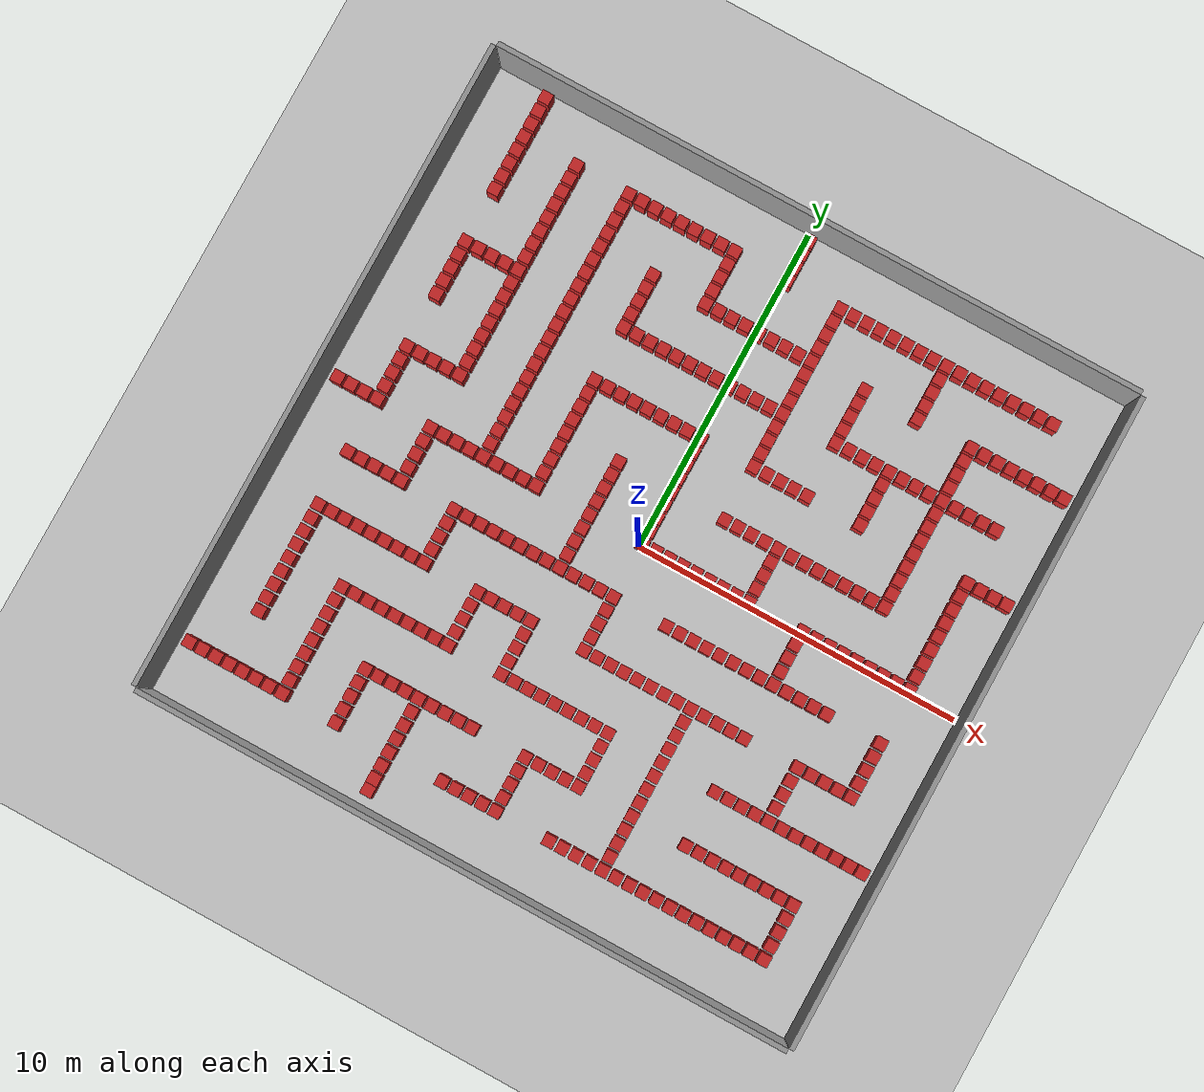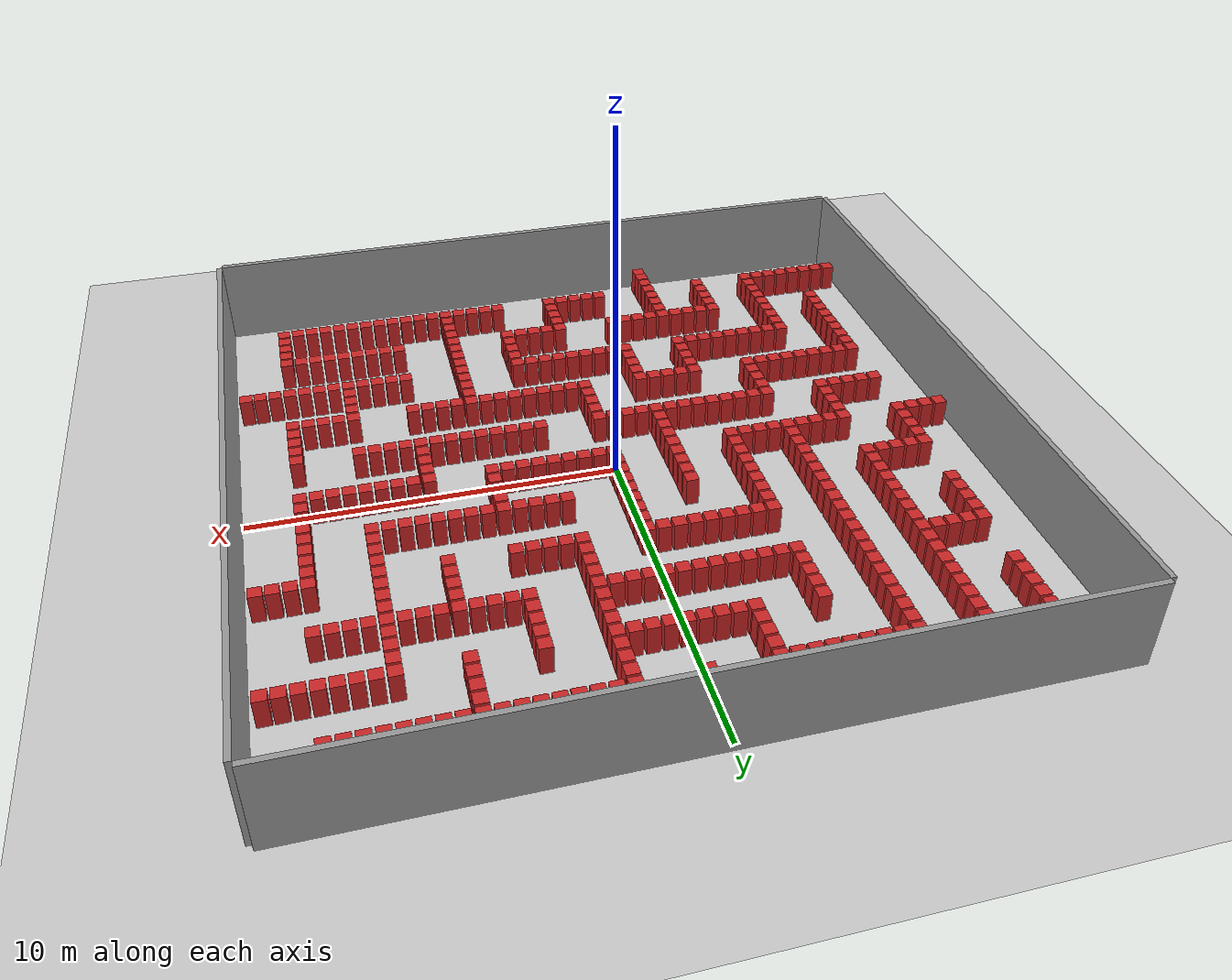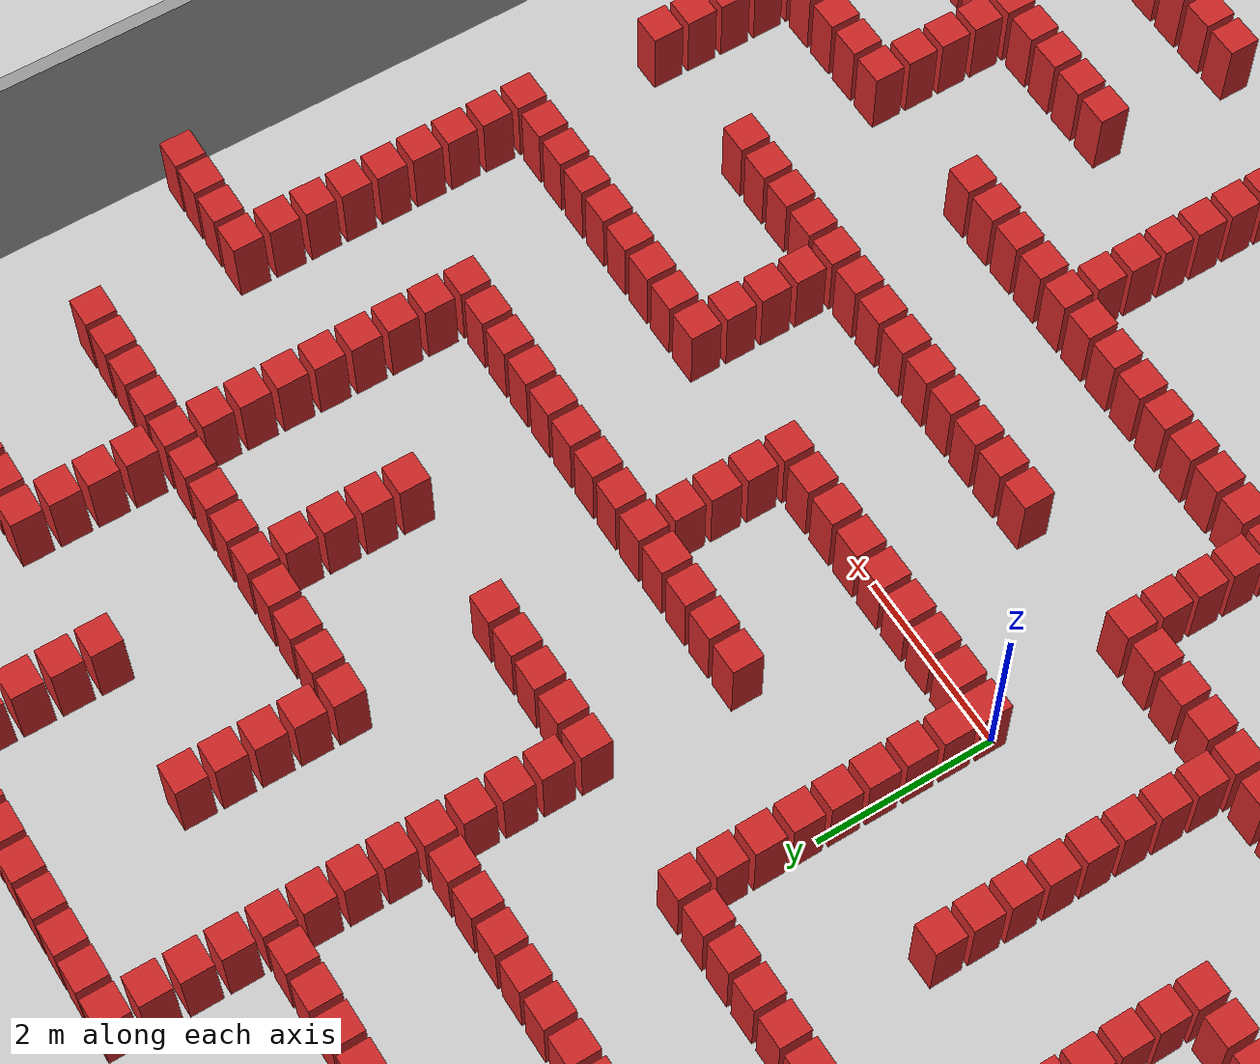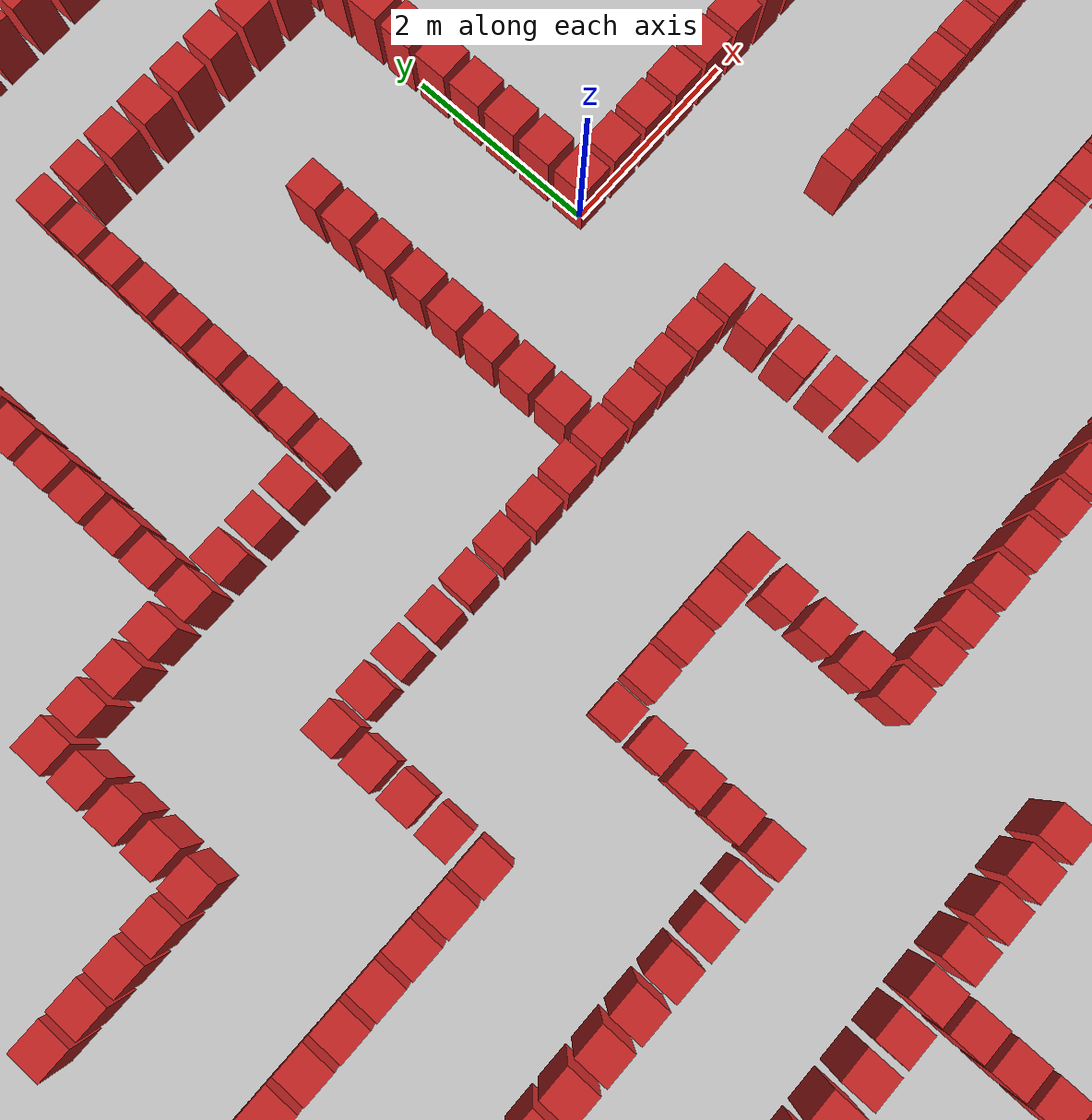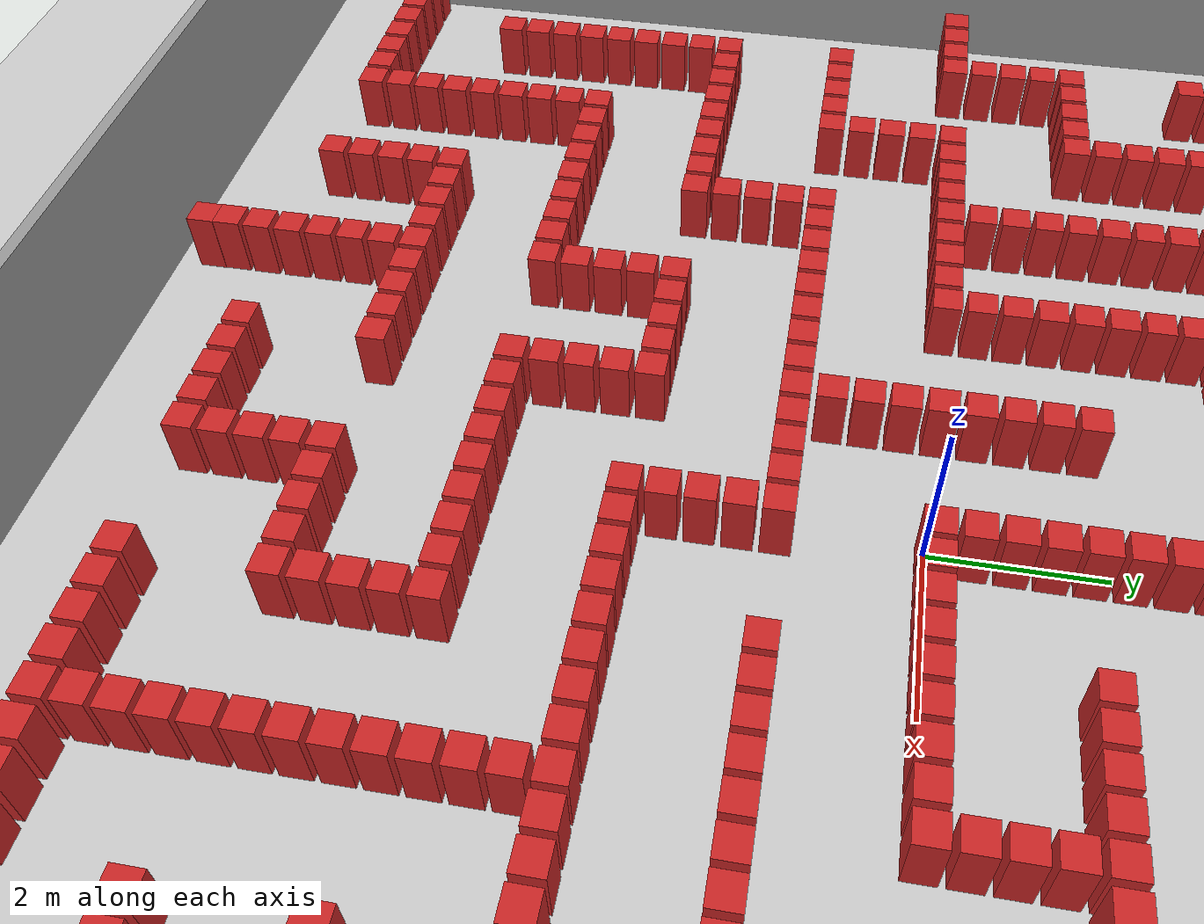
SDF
<sdf version="1.6">
 <world name="default">
  <light name="sun" type="directional">
   <pose>0 0 1000 0 -0 0</pose>
   <diffuse>0.8 0.8 0.8 1</diffuse>
   <specular>0.1 0.1 0.1 1</specular>
   <attenuation>
    <range>1000</range>
    <constant>0.9</constant>
    <linear>0.01</linear>
    <quadratic>0.001</quadratic>
   </attenuation>
   <direction>-0.5 0.5 -1</direction>
  </light>
  <model name="ground_plane">
   <static>1</static>
   <link name="link">
    <collision name="collision">
     <geometry><plane><normal>0 0 1</normal><size>100 100</size></plane></geometry>
     <surface><friction><ode><mu>100</mu><mu2>50</mu2></ode></friction></surface>
    </collision>
    <visual name="visual">
     <cast_shadows>0</cast_shadows>
     <geometry><plane><normal>0 0 1</normal><size>100 100</size></plane></geometry>
     <material>
      <script><uri>file://media/materials/scripts/gazebo.material</uri><name>Gazebo/Grey</name></script>
     </material>
    </visual>
   </link>
  </model>
  <gravity>0 0 -9.8</gravity>
  <magnetic_field>6e-06 2.3e-05 -4.2e-05</magnetic_field>
  <atmosphere type="adiabatic"/>
  <physics name="default_physics" default="0" type="ode">
   <max_step_size>0.001</max_step_size>
   <real_time_factor>1</real_time_factor>
   <real_time_update_rate>1000</real_time_update_rate>
  </physics>
  <scene><ambient>0.4 0.4 0.4 1</ambient><background>0.7 0.7 0.7 1</background><shadows>1</shadows></scene>
  <spherical_coordinates>
   <surface_model>EARTH_WGS84</surface_model>
   <latitude_deg>0</latitude_deg>
   <longitude_deg>0</longitude_deg>
   <elevation>0</elevation>
   <heading_deg>0</heading_deg>
  </spherical_coordinates>
  <model name="NamedLocations"><static>1</static><link name="DefaultStart"/></model>
  <model name="20x20_walls">
   <pose>0.044518 0.0211 0 0 -0 0</pose>
   <link name="Wall_1">
    <collision name="Wall_1_Collision">
     <geometry><box><size>20 0.15 2.5</size></box></geometry>
     <pose>0 0 1.25 0 -0 0</pose>
    </collision>
    <visual name="Wall_1_Visual">
     <pose>0 0 1.25 0 -0 0</pose>
     <geometry><box><size>20 0.15 2.5</size></box></geometry>
     <material>
      <script><uri>file://media/materials/scripts/gazebo.material</uri><name>Gazebo/Grey</name></script>
      <ambient>0.976471 0.992157 1 1</ambient>
     </material>
     <meta><layer>0</layer></meta>
    </visual>
    <pose>0 10.08 0 0 -0 0</pose>
   </link>
   <link name="Wall_3">
    <collision name="Wall_3_Collision">
     <geometry><box><size>20 0.15 2.5</size></box></geometry>
     <pose>0 0 1.25 0 -0 0</pose>
    </collision>
    <visual name="Wall_3_Visual">
     <pose>0 0 1.25 0 -0 0</pose>
     <geometry><box><size>20 0.15 2.5</size></box></geometry>
     <material>
      <script><uri>file://media/materials/scripts/gazebo.material</uri><name>Gazebo/Grey</name></script>
      <ambient>0.976471 0.992157 1 1</ambient>
     </material>
     <meta><layer>0</layer></meta>
    </visual>
    <pose>10.08 0 0 0 0 -1.5708</pose>
   </link>
   <link name="Wall_4">
    <collision name="Wall_4_Collision">
     <geometry><box><size>20 0.15 2.5</size></box></geometry>
     <pose>0 0 1.25 0 -0 0</pose>
    </collision>
    <visual name="Wall_4_Visual">
     <pose>0 0 1.25 0 -0 0</pose>
     <geometry><box><size>20 0.15 2.5</size></box></geometry>
     <material>
      <script><uri>file://media/materials/scripts/gazebo.material</uri><name>Gazebo/Grey</name></script>
      <ambient>0.976471 0.992157 1 1</ambient>
     </material>
     <meta><layer>0</layer></meta>
    </visual>
    <pose>0 -10.08 0 0 -0 3.14159</pose>
   </link>
   <link name="Wall_5">
    <collision name="Wall_5_Collision">
     <geometry><box><size>20 0.15 2.5</size></box></geometry>
     <pose>0 0 1.25 0 -0 0</pose>
    </collision>
    <visual name="Wall_5_Visual">
     <pose>0 0 1.25 0 -0 0</pose>
     <geometry><box><size>20 0.15 2.5</size></box></geometry>
     <material>
      <script><uri>file://media/materials/scripts/gazebo.material</uri><name>Gazebo/Grey</name></script>
      <ambient>0.976471 0.992157 1 1</ambient>
     </material>
     <meta><layer>0</layer></meta>
    </visual>
    <pose>-10.08 0 0 0 -0 1.5708</pose>
   </link>
   <static>1</static>
  </model>
  <model name="box_obstacle0">
   <static>0</static>
   <link name="link">
    <pose>0 0 0.1 0 -0 0</pose>
    <inertial>
     <mass>100</mass>
     <inertia>
      <ixx>0.166667</ixx>
      <ixy>0</ixy>
      <ixz>0</ixz>
      <iyy>0.166667</iyy>
      <iyz>0</iyz>
      <izz>0.166667</izz>
     </inertia>
    </inertial>
    <collision name="collision"><geometry><box><size>0.35 0.35 0.8</size></box></geometry></collision>
    <visual name="visual">
     <geometry><box><size>0.35 0.35 0.8</size></box></geometry>
     <material>
      <script><name>Gazebo/Red</name><uri>file://media/materials/scripts/gazebo.material</uri></script>
     </material>
    </visual>
   </link>
   <pose>-9.58034 -8.31994 0.300001 -1e-06 1.7e-05 0.000735</pose>
  </model>
  <model name="box_obstacle1">
   <static>0</static>
   <link name="link">
    <pose>0 0 0.1 0 -0 0</pose>
    <inertial>
     <mass>100</mass>
     <inertia>
      <ixx>0.166667</ixx>
      <ixy>0</ixy>
      <ixz>0</ixz>
      <iyy>0.166667</iyy>
      <iyz>0</iyz>
      <izz>0.166667</izz>
     </inertia>
    </inertial>
    <collision name="collision"><geometry><box><size>0.35 0.35 0.8</size></box></geometry></collision>
    <visual name="visual">
     <geometry><box><size>0.35 0.35 0.8</size></box></geometry>
     <material>
      <script><name>Gazebo/Red</name><uri>file://media/materials/scripts/gazebo.material</uri></script>
     </material>
    </visual>
   </link>
   <pose>-9.58034 0.080061 0.300001 -1e-06 1.7e-05 0.000735</pose>
  </model>
  <model name="box_obstacle2">
   <static>0</static>
   <link name="link">
    <pose>0 0 0.1 0 -0 0</pose>
    <inertial>
     <mass>100</mass>
     <inertia>
      <ixx>0.166667</ixx>
      <ixy>0</ixy>
      <ixz>0</ixz>
      <iyy>0.166667</iyy>
      <iyz>0</iyz>
      <izz>0.166667</izz>
     </inertia>
    </inertial>
    <collision name="collision"><geometry><box><size>0.35 0.35 0.8</size></box></geometry></collision>
    <visual name="visual">
     <geometry><box><size>0.35 0.35 0.8</size></box></geometry>
     <material>
      <script><name>Gazebo/Red</name><uri>file://media/materials/scripts/gazebo.material</uri></script>
     </material>
    </visual>
   </link>
   <pose>-9.16034 -8.31994 0.300001 -1e-06 1.7e-05 0.000735</pose>
  </model>
  <model name="box_obstacle3">
   <static>0</static>
   <link name="link">
    <pose>0 0 0.1 0 -0 0</pose>
    <inertial>
     <mass>100</mass>
     <inertia>
      <ixx>0.166667</ixx>
      <ixy>0</ixy>
      <ixz>0</ixz>
      <iyy>0.166667</iyy>
      <iyz>0</iyz>
      <izz>0.166667</izz>
     </inertia>
    </inertial>
    <collision name="collision"><geometry><box><size>0.35 0.35 0.8</size></box></geometry></collision>
    <visual name="visual">
     <geometry><box><size>0.35 0.35 0.8</size></box></geometry>
     <material>
      <script><name>Gazebo/Red</name><uri>file://media/materials/scripts/gazebo.material</uri></script>
     </material>
    </visual>
   </link>
   <pose>-9.16034 0.080061 0.300001 -1e-06 1.7e-05 0.000735</pose>
  </model>
  <model name="box_obstacle4">
   <static>0</static>
   <link name="link">
    <pose>0 0 0.1 0 -0 0</pose>
    <inertial>
     <mass>100</mass>
     <inertia>
      <ixx>0.166667</ixx>
      <ixy>0</ixy>
      <ixz>0</ixz>
      <iyy>0.166667</iyy>
      <iyz>0</iyz>
      <izz>0.166667</izz>
     </inertia>
    </inertial>
    <collision name="collision"><geometry><box><size>0.35 0.35 0.8</size></box></geometry></collision>
    <visual name="visual">
     <geometry><box><size>0.35 0.35 0.8</size></box></geometry>
     <material>
      <script><name>Gazebo/Red</name><uri>file://media/materials/scripts/gazebo.material</uri></script>
     </material>
    </visual>
   </link>
   <pose>-8.74034 -8.31994 0.300001 -1e-06 1.7e-05 0.000735</pose>
  </model>
  <model name="box_obstacle5">
   <static>0</static>
   <link name="link">
    <pose>0 0 0.1 0 -0 0</pose>
    <inertial>
     <mass>100</mass>
     <inertia>
      <ixx>0.166667</ixx>
      <ixy>0</ixy>
      <ixz>0</ixz>
      <iyy>0.166667</iyy>
      <iyz>0</iyz>
      <izz>0.166667</izz>
     </inertia>
    </inertial>
    <collision name="collision"><geometry><box><size>0.35 0.35 0.8</size></box></geometry></collision>
    <visual name="visual">
     <geometry><box><size>0.35 0.35 0.8</size></box></geometry>
     <material>
      <script><name>Gazebo/Red</name><uri>file://media/materials/scripts/gazebo.material</uri></script>
     </material>
    </visual>
   </link>
   <pose>-8.74034 0.080061 0.300001 -1e-06 1.7e-05 0.000735</pose>
  </model>
  <model name="box_obstacle6">
   <static>0</static>
   <link name="link">
    <pose>0 0 0.1 0 -0 0</pose>
    <inertial>
     <mass>100</mass>
     <inertia>
      <ixx>0.166667</ixx>
      <ixy>0</ixy>
      <ixz>0</ixz>
      <iyy>0.166667</iyy>
      <iyz>0</iyz>
      <izz>0.166667</izz>
     </inertia>
    </inertial>
    <collision name="collision"><geometry><box><size>0.35 0.35 0.8</size></box></geometry></collision>
    <visual name="visual">
     <geometry><box><size>0.35 0.35 0.8</size></box></geometry>
     <material>
      <script><name>Gazebo/Red</name><uri>file://media/materials/scripts/gazebo.material</uri></script>
     </material>
    </visual>
   </link>
   <pose>-8.32034 -8.31994 0.300001 -1e-06 1.7e-05 0.000735</pose>
  </model>
  <model name="box_obstacle7">
   <static>0</static>
   <link name="link">
    <pose>0 0 0.1 0 -0 0</pose>
    <inertial>
     <mass>100</mass>
     <inertia>
      <ixx>0.166667</ixx>
      <ixy>0</ixy>
      <ixz>0</ixz>
      <iyy>0.166667</iyy>
      <iyz>0</iyz>
      <izz>0.166667</izz>
     </inertia>
    </inertial>
    <collision name="collision"><geometry><box><size>0.35 0.35 0.8</size></box></geometry></collision>
    <visual name="visual">
     <geometry><box><size>0.35 0.35 0.8</size></box></geometry>
     <material>
      <script><name>Gazebo/Red</name><uri>file://media/materials/scripts/gazebo.material</uri></script>
     </material>
    </visual>
   </link>
   <pose>-8.32034 -6.63994 0.300001 -1e-06 1.7e-05 0.000735</pose>
  </model>
  <model name="box_obstacle8">
   <static>0</static>
   <link name="link">
    <pose>0 0 0.1 0 -0 0</pose>
    <inertial>
     <mass>100</mass>
     <inertia>
      <ixx>0.166667</ixx>
      <ixy>0</ixy>
      <ixz>0</ixz>
      <iyy>0.166667</iyy>
      <iyz>0</iyz>
      <izz>0.166667</izz>
     </inertia>
    </inertial>
    <collision name="collision"><geometry><box><size>0.35 0.35 0.8</size></box></geometry></collision>
    <visual name="visual">
     <geometry><box><size>0.35 0.35 0.8</size></box></geometry>
     <material>
      <script><name>Gazebo/Red</name><uri>file://media/materials/scripts/gazebo.material</uri></script>
     </material>
    </visual>
   </link>
   <pose>-8.32034 -6.21994 0.300001 -1e-06 1.7e-05 0.000735</pose>
  </model>
  <model name="box_obstacle9">
   <static>0</static>
   <link name="link">
    <pose>0 0 0.1 0 -0 0</pose>
    <inertial>
     <mass>100</mass>
     <inertia>
      <ixx>0.166667</ixx>
      <ixy>0</ixy>
      <ixz>0</ixz>
      <iyy>0.166667</iyy>
      <iyz>0</iyz>
      <izz>0.166667</izz>
     </inertia>
    </inertial>
    <collision name="collision"><geometry><box><size>0.35 0.35 0.8</size></box></geometry></collision>
    <visual name="visual">
     <geometry><box><size>0.35 0.35 0.8</size></box></geometry>
     <material>
      <script><name>Gazebo/Red</name><uri>file://media/materials/scripts/gazebo.material</uri></script>
     </material>
    </visual>
   </link>
   <pose>-8.32034 -5.79994 0.300001 -1e-06 1.7e-05 0.000735</pose>
  </model>
  <model name="box_obstacle10">
   <static>0</static>
   <link name="link">
    <pose>0 0 0.1 0 -0 0</pose>
    <inertial>
     <mass>100</mass>
     <inertia>
      <ixx>0.166667</ixx>
      <ixy>0</ixy>
      <ixz>0</ixz>
      <iyy>0.166667</iyy>
      <iyz>0</iyz>
      <izz>0.166667</izz>
     </inertia>
    </inertial>
    <collision name="collision"><geometry><box><size>0.35 0.35 0.8</size></box></geometry></collision>
    <visual name="visual">
     <geometry><box><size>0.35 0.35 0.8</size></box></geometry>
     <material>
      <script><name>Gazebo/Red</name><uri>file://media/materials/scripts/gazebo.material</uri></script>
     </material>
    </visual>
   </link>
   <pose>-8.32034 -5.37994 0.300001 -1e-06 1.7e-05 0.000735</pose>
  </model>
  <model name="box_obstacle11">
   <static>0</static>
   <link name="link">
    <pose>0 0 0.1 0 -0 0</pose>
    <inertial>
     <mass>100</mass>
     <inertia>
      <ixx>0.166667</ixx>
      <ixy>0</ixy>
      <ixz>0</ixz>
      <iyy>0.166667</iyy>
      <iyz>0</iyz>
      <izz>0.166667</izz>
     </inertia>
    </inertial>
    <collision name="collision"><geometry><box><size>0.35 0.35 0.8</size></box></geometry></collision>
    <visual name="visual">
     <geometry><box><size>0.35 0.35 0.8</size></box></geometry>
     <material>
      <script><name>Gazebo/Red</name><uri>file://media/materials/scripts/gazebo.material</uri></script>
     </material>
    </visual>
   </link>
   <pose>-8.32034 -4.95994 0.300001 -1e-06 1.7e-05 0.000735</pose>
  </model>
  <model name="box_obstacle12">
   <static>0</static>
   <link name="link">
    <pose>0 0 0.1 0 -0 0</pose>
    <inertial>
     <mass>100</mass>
     <inertia>
      <ixx>0.166667</ixx>
      <ixy>0</ixy>
      <ixz>0</ixz>
      <iyy>0.166667</iyy>
      <iyz>0</iyz>
      <izz>0.166667</izz>
     </inertia>
    </inertial>
    <collision name="collision"><geometry><box><size>0.35 0.35 0.8</size></box></geometry></collision>
    <visual name="visual">
     <geometry><box><size>0.35 0.35 0.8</size></box></geometry>
     <material>
      <script><name>Gazebo/Red</name><uri>file://media/materials/scripts/gazebo.material</uri></script>
     </material>
    </visual>
   </link>
   <pose>-8.32034 -4.53994 0.300001 -1e-06 1.7e-05 0.000735</pose>
  </model>
  <model name="box_obstacle13">
   <static>0</static>
   <link name="link">
    <pose>0 0 0.1 0 -0 0</pose>
    <inertial>
     <mass>100</mass>
     <inertia>
      <ixx>0.166667</ixx>
      <ixy>0</ixy>
      <ixz>0</ixz>
      <iyy>0.166667</iyy>
      <iyz>0</iyz>
      <izz>0.166667</izz>
     </inertia>
    </inertial>
    <collision name="collision"><geometry><box><size>0.35 0.35 0.8</size></box></geometry></collision>
    <visual name="visual">
     <geometry><box><size>0.35 0.35 0.8</size></box></geometry>
     <material>
      <script><name>Gazebo/Red</name><uri>file://media/materials/scripts/gazebo.material</uri></script>
     </material>
    </visual>
   </link>
   <pose>-8.32034 -4.11994 0.300001 -1e-06 1.7e-05 0.000735</pose>
  </model>
  <model name="box_obstacle14">
   <static>0</static>
   <link name="link">
    <pose>0 0 0.1 0 -0 0</pose>
    <inertial>
     <mass>100</mass>
     <inertia>
      <ixx>0.166667</ixx>
      <ixy>0</ixy>
      <ixz>0</ixz>
      <iyy>0.166667</iyy>
      <iyz>0</iyz>
      <izz>0.166667</izz>
     </inertia>
    </inertial>
    <collision name="collision"><geometry><box><size>0.35 0.35 0.8</size></box></geometry></collision>
    <visual name="visual">
     <geometry><box><size>0.35 0.35 0.8</size></box></geometry>
     <material>
      <script><name>Gazebo/Red</name><uri>file://media/materials/scripts/gazebo.material</uri></script>
     </material>
    </visual>
   </link>
   <pose>-8.32034 -3.69994 0.300001 -1e-06 1.7e-05 0.000735</pose>
  </model>
  <model name="box_obstacle15">
   <static>0</static>
   <link name="link">
    <pose>0 0 0.1 0 -0 0</pose>
    <inertial>
     <mass>100</mass>
     <inertia>
      <ixx>0.166667</ixx>
      <ixy>0</ixy>
      <ixz>0</ixz>
      <iyy>0.166667</iyy>
      <iyz>0</iyz>
      <izz>0.166667</izz>
     </inertia>
    </inertial>
    <collision name="collision"><geometry><box><size>0.35 0.35 0.8</size></box></geometry></collision>
    <visual name="visual">
     <geometry><box><size>0.35 0.35 0.8</size></box></geometry>
     <material>
      <script><name>Gazebo/Red</name><uri>file://media/materials/scripts/gazebo.material</uri></script>
     </material>
    </visual>
   </link>
   <pose>-8.32034 -3.27994 0.300001 -1e-06 1.7e-05 0.000735</pose>
  </model>
  <model name="box_obstacle16">
   <static>0</static>
   <link name="link">
    <pose>0 0 0.1 0 -0 0</pose>
    <inertial>
     <mass>100</mass>
     <inertia>
      <ixx>0.166667</ixx>
      <ixy>0</ixy>
      <ixz>0</ixz>
      <iyy>0.166667</iyy>
      <iyz>0</iyz>
      <izz>0.166667</izz>
     </inertia>
    </inertial>
    <collision name="collision"><geometry><box><size>0.35 0.35 0.8</size></box></geometry></collision>
    <visual name="visual">
     <geometry><box><size>0.35 0.35 0.8</size></box></geometry>
     <material>
      <script><name>Gazebo/Red</name><uri>file://media/materials/scripts/gazebo.material</uri></script>
     </material>
    </visual>
   </link>
   <pose>-8.32034 -1.59994 0.300001 -1e-06 1.7e-05 0.000735</pose>
  </model>
  <model name="box_obstacle17">
   <static>0</static>
   <link name="link">
    <pose>0 0 0.1 0 -0 0</pose>
    <inertial>
     <mass>100</mass>
     <inertia>
      <ixx>0.166667</ixx>
      <ixy>0</ixy>
      <ixz>0</ixz>
      <iyy>0.166667</iyy>
      <iyz>0</iyz>
      <izz>0.166667</izz>
     </inertia>
    </inertial>
    <collision name="collision"><geometry><box><size>0.35 0.35 0.8</size></box></geometry></collision>
    <visual name="visual">
     <geometry><box><size>0.35 0.35 0.8</size></box></geometry>
     <material>
      <script><name>Gazebo/Red</name><uri>file://media/materials/scripts/gazebo.material</uri></script>
     </material>
    </visual>
   </link>
   <pose>-8.32034 0.080061 0.300001 -1e-06 1.7e-05 0.000735</pose>
  </model>
  <model name="box_obstacle18">
   <static>0</static>
   <link name="link">
    <pose>0 0 0.1 0 -0 0</pose>
    <inertial>
     <mass>100</mass>
     <inertia>
      <ixx>0.166667</ixx>
      <ixy>0</ixy>
      <ixz>0</ixz>
      <iyy>0.166667</iyy>
      <iyz>0</iyz>
      <izz>0.166667</izz>
     </inertia>
    </inertial>
    <collision name="collision"><geometry><box><size>0.35 0.35 0.8</size></box></geometry></collision>
    <visual name="visual">
     <geometry><box><size>0.35 0.35 0.8</size></box></geometry>
     <material>
      <script><name>Gazebo/Red</name><uri>file://media/materials/scripts/gazebo.material</uri></script>
     </material>
    </visual>
   </link>
   <pose>-8.32034 0.500061 0.300001 -1e-06 1.7e-05 0.000735</pose>
  </model>
  <model name="box_obstacle19">
   <static>0</static>
   <link name="link">
    <pose>0 0 0.1 0 -0 0</pose>
    <inertial>
     <mass>100</mass>
     <inertia>
      <ixx>0.166667</ixx>
      <ixy>0</ixy>
      <ixz>0</ixz>
      <iyy>0.166667</iyy>
      <iyz>0</iyz>
      <izz>0.166667</izz>
     </inertia>
    </inertial>
    <collision name="collision"><geometry><box><size>0.35 0.35 0.8</size></box></geometry></collision>
    <visual name="visual">
     <geometry><box><size>0.35 0.35 0.8</size></box></geometry>
     <material>
      <script><name>Gazebo/Red</name><uri>file://media/materials/scripts/gazebo.material</uri></script>
     </material>
    </visual>
   </link>
   <pose>-8.32034 0.920061 0.300001 -1e-06 1.7e-05 0.000735</pose>
  </model>
  <model name="box_obstacle20">
   <static>0</static>
   <link name="link">
    <pose>0 0 0.1 0 -0 0</pose>
    <inertial>
     <mass>100</mass>
     <inertia>
      <ixx>0.166667</ixx>
      <ixy>0</ixy>
      <ixz>0</ixz>
      <iyy>0.166667</iyy>
      <iyz>0</iyz>
      <izz>0.166667</izz>
     </inertia>
    </inertial>
    <collision name="collision"><geometry><box><size>0.35 0.35 0.8</size></box></geometry></collision>
    <visual name="visual">
     <geometry><box><size>0.35 0.35 0.8</size></box></geometry>
     <material>
      <script><name>Gazebo/Red</name><uri>file://media/materials/scripts/gazebo.material</uri></script>
     </material>
    </visual>
   </link>
   <pose>-8.32034 1.34006 0.300001 -1e-06 1.7e-05 0.000735</pose>
  </model>
  <model name="box_obstacle21">
   <static>0</static>
   <link name="link">
    <pose>0 0 0.1 0 -0 0</pose>
    <inertial>
     <mass>100</mass>
     <inertia>
      <ixx>0.166667</ixx>
      <ixy>0</ixy>
      <ixz>0</ixz>
      <iyy>0.166667</iyy>
      <iyz>0</iyz>
      <izz>0.166667</izz>
     </inertia>
    </inertial>
    <collision name="collision"><geometry><box><size>0.35 0.35 0.8</size></box></geometry></collision>
    <visual name="visual">
     <geometry><box><size>0.35 0.35 0.8</size></box></geometry>
     <material>
      <script><name>Gazebo/Red</name><uri>file://media/materials/scripts/gazebo.material</uri></script>
     </material>
    </visual>
   </link>
   <pose>-8.32034 1.76006 0.300001 -1e-06 1.7e-05 0.000735</pose>
  </model>
  <model name="box_obstacle22">
   <static>0</static>
   <link name="link">
    <pose>0 0 0.1 0 -0 0</pose>
    <inertial>
     <mass>100</mass>
     <inertia>
      <ixx>0.166667</ixx>
      <ixy>0</ixy>
      <ixz>0</ixz>
      <iyy>0.166667</iyy>
      <iyz>0</iyz>
      <izz>0.166667</izz>
     </inertia>
    </inertial>
    <collision name="collision"><geometry><box><size>0.35 0.35 0.8</size></box></geometry></collision>
    <visual name="visual">
     <geometry><box><size>0.35 0.35 0.8</size></box></geometry>
     <material>
      <script><name>Gazebo/Red</name><uri>file://media/materials/scripts/gazebo.material</uri></script>
     </material>
    </visual>
   </link>
   <pose>-8.32034 3.44006 0.300001 -1e-06 1.7e-05 0.000735</pose>
  </model>
  <model name="box_obstacle23">
   <static>0</static>
   <link name="link">
    <pose>0 0 0.1 0 -0 0</pose>
    <inertial>
     <mass>100</mass>
     <inertia>
      <ixx>0.166667</ixx>
      <ixy>0</ixy>
      <ixz>0</ixz>
      <iyy>0.166667</iyy>
      <iyz>0</iyz>
      <izz>0.166667</izz>
     </inertia>
    </inertial>
    <collision name="collision"><geometry><box><size>0.35 0.35 0.8</size></box></geometry></collision>
    <visual name="visual">
     <geometry><box><size>0.35 0.35 0.8</size></box></geometry>
     <material>
      <script><name>Gazebo/Red</name><uri>file://media/materials/scripts/gazebo.material</uri></script>
     </material>
    </visual>
   </link>
   <pose>-8.32034 3.86006 0.300001 -1e-06 1.7e-05 0.000735</pose>
  </model>
  <model name="box_obstacle24">
   <static>0</static>
   <link name="link">
    <pose>0 0 0.1 0 -0 0</pose>
    <inertial>
     <mass>100</mass>
     <inertia>
      <ixx>0.166667</ixx>
      <ixy>0</ixy>
      <ixz>0</ixz>
      <iyy>0.166667</iyy>
      <iyz>0</iyz>
      <izz>0.166667</izz>
     </inertia>
    </inertial>
    <collision name="collision"><geometry><box><size>0.35 0.35 0.8</size></box></geometry></collision>
    <visual name="visual">
     <geometry><box><size>0.35 0.35 0.8</size></box></geometry>
     <material>
      <script><name>Gazebo/Red</name><uri>file://media/materials/scripts/gazebo.material</uri></script>
     </material>
    </visual>
   </link>
   <pose>-8.32034 4.28006 0.300001 -1e-06 1.7e-05 0.000735</pose>
  </model>
  <model name="box_obstacle25">
   <static>0</static>
   <link name="link">
    <pose>0 0 0.1 0 -0 0</pose>
    <inertial>
     <mass>100</mass>
     <inertia>
      <ixx>0.166667</ixx>
      <ixy>0</ixy>
      <ixz>0</ixz>
      <iyy>0.166667</iyy>
      <iyz>0</iyz>
      <izz>0.166667</izz>
     </inertia>
    </inertial>
    <collision name="collision"><geometry><box><size>0.35 0.35 0.8</size></box></geometry></collision>
    <visual name="visual">
     <geometry><box><size>0.35 0.35 0.8</size></box></geometry>
     <material>
      <script><name>Gazebo/Red</name><uri>file://media/materials/scripts/gazebo.material</uri></script>
     </material>
    </visual>
   </link>
   <pose>-8.32034 4.70006 0.300001 -1e-06 1.7e-05 0.000735</pose>
  </model>
  <model name="box_obstacle26">
   <static>0</static>
   <link name="link">
    <pose>0 0 0.1 0 -0 0</pose>
    <inertial>
     <mass>100</mass>
     <inertia>
      <ixx>0.166667</ixx>
      <ixy>0</ixy>
      <ixz>0</ixz>
      <iyy>0.166667</iyy>
      <iyz>0</iyz>
      <izz>0.166667</izz>
     </inertia>
    </inertial>
    <collision name="collision"><geometry><box><size>0.35 0.35 0.8</size></box></geometry></collision>
    <visual name="visual">
     <geometry><box><size>0.35 0.35 0.8</size></box></geometry>
     <material>
      <script><name>Gazebo/Red</name><uri>file://media/materials/scripts/gazebo.material</uri></script>
     </material>
    </visual>
   </link>
   <pose>-8.32034 5.12006 0.300001 -1e-06 1.7e-05 0.000735</pose>
  </model>
  <model name="box_obstacle27">
   <static>0</static>
   <link name="link">
    <pose>0 0 0.1 0 -0 0</pose>
    <inertial>
     <mass>100</mass>
     <inertia>
      <ixx>0.166667</ixx>
      <ixy>0</ixy>
      <ixz>0</ixz>
      <iyy>0.166667</iyy>
      <iyz>0</iyz>
      <izz>0.166667</izz>
     </inertia>
    </inertial>
    <collision name="collision"><geometry><box><size>0.35 0.35 0.8</size></box></geometry></collision>
    <visual name="visual">
     <geometry><box><size>0.35 0.35 0.8</size></box></geometry>
     <material>
      <script><name>Gazebo/Red</name><uri>file://media/materials/scripts/gazebo.material</uri></script>
     </material>
    </visual>
   </link>
   <pose>-8.32034 6.80006 0.300001 -1e-06 1.7e-05 0.000735</pose>
  </model>
  <model name="box_obstacle28">
   <static>0</static>
   <link name="link">
    <pose>0 0 0.1 0 -0 0</pose>
    <inertial>
     <mass>100</mass>
     <inertia>
      <ixx>0.166667</ixx>
      <ixy>0</ixy>
      <ixz>0</ixz>
      <iyy>0.166667</iyy>
      <iyz>0</iyz>
      <izz>0.166667</izz>
     </inertia>
    </inertial>
    <collision name="collision"><geometry><box><size>0.35 0.35 0.8</size></box></geometry></collision>
    <visual name="visual">
     <geometry><box><size>0.35 0.35 0.8</size></box></geometry>
     <material>
      <script><name>Gazebo/Red</name><uri>file://media/materials/scripts/gazebo.material</uri></script>
     </material>
    </visual>
   </link>
   <pose>-8.32034 7.22006 0.300001 -1e-06 1.7e-05 0.000735</pose>
  </model>
  <model name="box_obstacle29">
   <static>0</static>
   <link name="link">
    <pose>0 0 0.1 0 -0 0</pose>
    <inertial>
     <mass>100</mass>
     <inertia>
      <ixx>0.166667</ixx>
      <ixy>0</ixy>
      <ixz>0</ixz>
      <iyy>0.166667</iyy>
      <iyz>0</iyz>
      <izz>0.166667</izz>
     </inertia>
    </inertial>
    <collision name="collision"><geometry><box><size>0.35 0.35 0.8</size></box></geometry></collision>
    <visual name="visual">
     <geometry><box><size>0.35 0.35 0.8</size></box></geometry>
     <material>
      <script><name>Gazebo/Red</name><uri>file://media/materials/scripts/gazebo.material</uri></script>
     </material>
    </visual>
   </link>
   <pose>-8.32034 7.64006 0.300001 -1e-06 1.7e-05 0.000735</pose>
  </model>
  <model name="box_obstacle30">
   <static>0</static>
   <link name="link">
    <pose>0 0 0.1 0 -0 0</pose>
    <inertial>
     <mass>100</mass>
     <inertia>
      <ixx>0.166667</ixx>
      <ixy>0</ixy>
      <ixz>0</ixz>
      <iyy>0.166667</iyy>
      <iyz>0</iyz>
      <izz>0.166667</izz>
     </inertia>
    </inertial>
    <collision name="collision"><geometry><box><size>0.35 0.35 0.8</size></box></geometry></collision>
    <visual name="visual">
     <geometry><box><size>0.35 0.35 0.8</size></box></geometry>
     <material>
      <script><name>Gazebo/Red</name><uri>file://media/materials/scripts/gazebo.material</uri></script>
     </material>
    </visual>
   </link>
   <pose>-8.32034 8.06006 0.300001 -1e-06 1.7e-05 0.000735</pose>
  </model>
  <model name="box_obstacle31">
   <static>0</static>
   <link name="link">
    <pose>0 0 0.1 0 -0 0</pose>
    <inertial>
     <mass>100</mass>
     <inertia>
      <ixx>0.166667</ixx>
      <ixy>0</ixy>
      <ixz>0</ixz>
      <iyy>0.166667</iyy>
      <iyz>0</iyz>
      <izz>0.166667</izz>
     </inertia>
    </inertial>
    <collision name="collision"><geometry><box><size>0.35 0.35 0.8</size></box></geometry></collision>
    <visual name="visual">
     <geometry><box><size>0.35 0.35 0.8</size></box></geometry>
     <material>
      <script><name>Gazebo/Red</name><uri>file://media/materials/scripts/gazebo.material</uri></script>
     </material>
    </visual>
   </link>
   <pose>-8.32034 8.48006 0.300001 -1e-06 1.7e-05 0.000735</pose>
  </model>
  <model name="box_obstacle32">
   <static>0</static>
   <link name="link">
    <pose>0 0 0.1 0 -0 0</pose>
    <inertial>
     <mass>100</mass>
     <inertia>
      <ixx>0.166667</ixx>
      <ixy>0</ixy>
      <ixz>0</ixz>
      <iyy>0.166667</iyy>
      <iyz>0</iyz>
      <izz>0.166667</izz>
     </inertia>
    </inertial>
    <collision name="collision"><geometry><box><size>0.35 0.35 0.8</size></box></geometry></collision>
    <visual name="visual">
     <geometry><box><size>0.35 0.35 0.8</size></box></geometry>
     <material>
      <script><name>Gazebo/Red</name><uri>file://media/materials/scripts/gazebo.material</uri></script>
     </material>
    </visual>
   </link>
   <pose>-8.32034 8.90006 0.300001 -1e-06 1.7e-05 0.000735</pose>
  </model>
  <model name="box_obstacle33">
   <static>0</static>
   <link name="link">
    <pose>0 0 0.1 0 -0 0</pose>
    <inertial>
     <mass>100</mass>
     <inertia>
      <ixx>0.166667</ixx>
      <ixy>0</ixy>
      <ixz>0</ixz>
      <iyy>0.166667</iyy>
      <iyz>0</iyz>
      <izz>0.166667</izz>
     </inertia>
    </inertial>
    <collision name="collision"><geometry><box><size>0.35 0.35 0.8</size></box></geometry></collision>
    <visual name="visual">
     <geometry><box><size>0.35 0.35 0.8</size></box></geometry>
     <material>
      <script><name>Gazebo/Red</name><uri>file://media/materials/scripts/gazebo.material</uri></script>
     </material>
    </visual>
   </link>
   <pose>-8.32034 9.32006 0.300001 -1e-06 1.7e-05 0.000735</pose>
  </model>
  <model name="box_obstacle34">
   <static>0</static>
   <link name="link">
    <pose>0 0 0.1 0 -0 0</pose>
    <inertial>
     <mass>100</mass>
     <inertia>
      <ixx>0.166667</ixx>
      <ixy>0</ixy>
      <ixz>0</ixz>
      <iyy>0.166667</iyy>
      <iyz>0</iyz>
      <izz>0.166667</izz>
     </inertia>
    </inertial>
    <collision name="collision"><geometry><box><size>0.35 0.35 0.8</size></box></geometry></collision>
    <visual name="visual">
     <geometry><box><size>0.35 0.35 0.8</size></box></geometry>
     <material>
      <script><name>Gazebo/Red</name><uri>file://media/materials/scripts/gazebo.material</uri></script>
     </material>
    </visual>
   </link>
   <pose>-8.32034 9.74006 0.300001 -1e-06 1.7e-05 0.000735</pose>
  </model>
  <model name="box_obstacle35">
   <static>0</static>
   <link name="link">
    <pose>0 0 0.1 0 -0 0</pose>
    <inertial>
     <mass>100</mass>
     <inertia>
      <ixx>0.166667</ixx>
      <ixy>0</ixy>
      <ixz>0</ixz>
      <iyy>0.166667</iyy>
      <iyz>0</iyz>
      <izz>0.166667</izz>
     </inertia>
    </inertial>
    <collision name="collision"><geometry><box><size>0.35 0.35 0.8</size></box></geometry></collision>
    <visual name="visual">
     <geometry><box><size>0.35 0.35 0.8</size></box></geometry>
     <material>
      <script><name>Gazebo/Red</name><uri>file://media/materials/scripts/gazebo.material</uri></script>
     </material>
    </visual>
   </link>
   <pose>-7.90034 -8.31994 0.300001 -1e-06 1.7e-05 0.000735</pose>
  </model>
  <model name="box_obstacle36">
   <static>0</static>
   <link name="link">
    <pose>0 0 0.1 0 -0 0</pose>
    <inertial>
     <mass>100</mass>
     <inertia>
      <ixx>0.166667</ixx>
      <ixy>0</ixy>
      <ixz>0</ixz>
      <iyy>0.166667</iyy>
      <iyz>0</iyz>
      <izz>0.166667</izz>
     </inertia>
    </inertial>
    <collision name="collision"><geometry><box><size>0.35 0.35 0.8</size></box></geometry></collision>
    <visual name="visual">
     <geometry><box><size>0.35 0.35 0.8</size></box></geometry>
     <material>
      <script><name>Gazebo/Red</name><uri>file://media/materials/scripts/gazebo.material</uri></script>
     </material>
    </visual>
   </link>
   <pose>-7.90034 -3.27994 0.300001 -1e-06 1.7e-05 0.000735</pose>
  </model>
  <model name="box_obstacle37">
   <static>0</static>
   <link name="link">
    <pose>0 0 0.1 0 -0 0</pose>
    <inertial>
     <mass>100</mass>
     <inertia>
      <ixx>0.166667</ixx>
      <ixy>0</ixy>
      <ixz>0</ixz>
      <iyy>0.166667</iyy>
      <iyz>0</iyz>
      <izz>0.166667</izz>
     </inertia>
    </inertial>
    <collision name="collision"><geometry><box><size>0.35 0.35 0.8</size></box></geometry></collision>
    <visual name="visual">
     <geometry><box><size>0.35 0.35 0.8</size></box></geometry>
     <material>
      <script><name>Gazebo/Red</name><uri>file://media/materials/scripts/gazebo.material</uri></script>
     </material>
    </visual>
   </link>
   <pose>-7.90034 -1.59994 0.300001 -1e-06 1.7e-05 0.000735</pose>
  </model>
  <model name="box_obstacle38">
   <static>0</static>
   <link name="link">
    <pose>0 0 0.1 0 -0 0</pose>
    <inertial>
     <mass>100</mass>
     <inertia>
      <ixx>0.166667</ixx>
      <ixy>0</ixy>
      <ixz>0</ixz>
      <iyy>0.166667</iyy>
      <iyz>0</iyz>
      <izz>0.166667</izz>
     </inertia>
    </inertial>
    <collision name="collision"><geometry><box><size>0.35 0.35 0.8</size></box></geometry></collision>
    <visual name="visual">
     <geometry><box><size>0.35 0.35 0.8</size></box></geometry>
     <material>
      <script><name>Gazebo/Red</name><uri>file://media/materials/scripts/gazebo.material</uri></script>
     </material>
    </visual>
   </link>
   <pose>-7.90034 1.76006 0.300001 -1e-06 1.7e-05 0.000735</pose>
  </model>
  <model name="box_obstacle39">
   <static>0</static>
   <link name="link">
    <pose>0 0 0.1 0 -0 0</pose>
    <inertial>
     <mass>100</mass>
     <inertia>
      <ixx>0.166667</ixx>
      <ixy>0</ixy>
      <ixz>0</ixz>
      <iyy>0.166667</iyy>
      <iyz>0</iyz>
      <izz>0.166667</izz>
     </inertia>
    </inertial>
    <collision name="collision"><geometry><box><size>0.35 0.35 0.8</size></box></geometry></collision>
    <visual name="visual">
     <geometry><box><size>0.35 0.35 0.8</size></box></geometry>
     <material>
      <script><name>Gazebo/Red</name><uri>file://media/materials/scripts/gazebo.material</uri></script>
     </material>
    </visual>
   </link>
   <pose>-7.90034 5.12006 0.300001 -1e-06 1.7e-05 0.000735</pose>
  </model>
  <model name="box_obstacle40">
   <static>0</static>
   <link name="link">
    <pose>0 0 0.1 0 -0 0</pose>
    <inertial>
     <mass>100</mass>
     <inertia>
      <ixx>0.166667</ixx>
      <ixy>0</ixy>
      <ixz>0</ixz>
      <iyy>0.166667</iyy>
      <iyz>0</iyz>
      <izz>0.166667</izz>
     </inertia>
    </inertial>
    <collision name="collision"><geometry><box><size>0.35 0.35 0.8</size></box></geometry></collision>
    <visual name="visual">
     <geometry><box><size>0.35 0.35 0.8</size></box></geometry>
     <material>
      <script><name>Gazebo/Red</name><uri>file://media/materials/scripts/gazebo.material</uri></script>
     </material>
    </visual>
   </link>
   <pose>-7.48034 -8.31994 0.300001 -1e-06 1.7e-05 0.000735</pose>
  </model>
  <model name="box_obstacle41">
   <static>0</static>
   <link name="link">
    <pose>0 0 0.1 0 -0 0</pose>
    <inertial>
     <mass>100</mass>
     <inertia>
      <ixx>0.166667</ixx>
      <ixy>0</ixy>
      <ixz>0</ixz>
      <iyy>0.166667</iyy>
      <iyz>0</iyz>
      <izz>0.166667</izz>
     </inertia>
    </inertial>
    <collision name="collision"><geometry><box><size>0.35 0.35 0.8</size></box></geometry></collision>
    <visual name="visual">
     <geometry><box><size>0.35 0.35 0.8</size></box></geometry>
     <material>
      <script><name>Gazebo/Red</name><uri>file://media/materials/scripts/gazebo.material</uri></script>
     </material>
    </visual>
   </link>
   <pose>-7.48034 -3.27994 0.300001 -1e-06 1.7e-05 0.000735</pose>
  </model>
  <model name="box_obstacle42">
   <static>0</static>
   <link name="link">
    <pose>0 0 0.1 0 -0 0</pose>
    <inertial>
     <mass>100</mass>
     <inertia>
      <ixx>0.166667</ixx>
      <ixy>0</ixy>
      <ixz>0</ixz>
      <iyy>0.166667</iyy>
      <iyz>0</iyz>
      <izz>0.166667</izz>
     </inertia>
    </inertial>
    <collision name="collision"><geometry><box><size>0.35 0.35 0.8</size></box></geometry></collision>
    <visual name="visual">
     <geometry><box><size>0.35 0.35 0.8</size></box></geometry>
     <material>
      <script><name>Gazebo/Red</name><uri>file://media/materials/scripts/gazebo.material</uri></script>
     </material>
    </visual>
   </link>
   <pose>-7.48034 -1.59994 0.300001 -1e-06 1.7e-05 0.000735</pose>
  </model>
  <model name="box_obstacle43">
   <static>0</static>
   <link name="link">
    <pose>0 0 0.1 0 -0 0</pose>
    <inertial>
     <mass>100</mass>
     <inertia>
      <ixx>0.166667</ixx>
      <ixy>0</ixy>
      <ixz>0</ixz>
      <iyy>0.166667</iyy>
      <iyz>0</iyz>
      <izz>0.166667</izz>
     </inertia>
    </inertial>
    <collision name="collision"><geometry><box><size>0.35 0.35 0.8</size></box></geometry></collision>
    <visual name="visual">
     <geometry><box><size>0.35 0.35 0.8</size></box></geometry>
     <material>
      <script><name>Gazebo/Red</name><uri>file://media/materials/scripts/gazebo.material</uri></script>
     </material>
    </visual>
   </link>
   <pose>-7.48034 1.76006 0.300001 -1e-06 1.7e-05 0.000735</pose>
  </model>
  <model name="box_obstacle44">
   <static>0</static>
   <link name="link">
    <pose>0 0 0.1 0 -0 0</pose>
    <inertial>
     <mass>100</mass>
     <inertia>
      <ixx>0.166667</ixx>
      <ixy>0</ixy>
      <ixz>0</ixz>
      <iyy>0.166667</iyy>
      <iyz>0</iyz>
      <izz>0.166667</izz>
     </inertia>
    </inertial>
    <collision name="collision"><geometry><box><size>0.35 0.35 0.8</size></box></geometry></collision>
    <visual name="visual">
     <geometry><box><size>0.35 0.35 0.8</size></box></geometry>
     <material>
      <script><name>Gazebo/Red</name><uri>file://media/materials/scripts/gazebo.material</uri></script>
     </material>
    </visual>
   </link>
   <pose>-7.48034 5.12006 0.300001 -1e-06 1.7e-05 0.000735</pose>
  </model>
  <model name="box_obstacle45">
   <static>0</static>
   <link name="link">
    <pose>0 0 0.1 0 -0 0</pose>
    <inertial>
     <mass>100</mass>
     <inertia>
      <ixx>0.166667</ixx>
      <ixy>0</ixy>
      <ixz>0</ixz>
      <iyy>0.166667</iyy>
      <iyz>0</iyz>
      <izz>0.166667</izz>
     </inertia>
    </inertial>
    <collision name="collision"><geometry><box><size>0.35 0.35 0.8</size></box></geometry></collision>
    <visual name="visual">
     <geometry><box><size>0.35 0.35 0.8</size></box></geometry>
     <material>
      <script><name>Gazebo/Red</name><uri>file://media/materials/scripts/gazebo.material</uri></script>
     </material>
    </visual>
   </link>
   <pose>-7.06034 -8.31994 0.300001 -1e-06 1.7e-05 0.000735</pose>
  </model>
  <model name="box_obstacle46">
   <static>0</static>
   <link name="link">
    <pose>0 0 0.1 0 -0 0</pose>
    <inertial>
     <mass>100</mass>
     <inertia>
      <ixx>0.166667</ixx>
      <ixy>0</ixy>
      <ixz>0</ixz>
      <iyy>0.166667</iyy>
      <iyz>0</iyz>
      <izz>0.166667</izz>
     </inertia>
    </inertial>
    <collision name="collision"><geometry><box><size>0.35 0.35 0.8</size></box></geometry></collision>
    <visual name="visual">
     <geometry><box><size>0.35 0.35 0.8</size></box></geometry>
     <material>
      <script><name>Gazebo/Red</name><uri>file://media/materials/scripts/gazebo.material</uri></script>
     </material>
    </visual>
   </link>
   <pose>-7.06034 -3.27994 0.300001 -1e-06 1.7e-05 0.000735</pose>
  </model>
  <model name="box_obstacle47">
   <static>0</static>
   <link name="link">
    <pose>0 0 0.1 0 -0 0</pose>
    <inertial>
     <mass>100</mass>
     <inertia>
      <ixx>0.166667</ixx>
      <ixy>0</ixy>
      <ixz>0</ixz>
      <iyy>0.166667</iyy>
      <iyz>0</iyz>
      <izz>0.166667</izz>
     </inertia>
    </inertial>
    <collision name="collision"><geometry><box><size>0.35 0.35 0.8</size></box></geometry></collision>
    <visual name="visual">
     <geometry><box><size>0.35 0.35 0.8</size></box></geometry>
     <material>
      <script><name>Gazebo/Red</name><uri>file://media/materials/scripts/gazebo.material</uri></script>
     </material>
    </visual>
   </link>
   <pose>-7.06034 -1.59994 0.300001 -1e-06 1.7e-05 0.000735</pose>
  </model>
  <model name="box_obstacle48">
   <static>0</static>
   <link name="link">
    <pose>0 0 0.1 0 -0 0</pose>
    <inertial>
     <mass>100</mass>
     <inertia>
      <ixx>0.166667</ixx>
      <ixy>0</ixy>
      <ixz>0</ixz>
      <iyy>0.166667</iyy>
      <iyz>0</iyz>
      <izz>0.166667</izz>
     </inertia>
    </inertial>
    <collision name="collision"><geometry><box><size>0.35 0.35 0.8</size></box></geometry></collision>
    <visual name="visual">
     <geometry><box><size>0.35 0.35 0.8</size></box></geometry>
     <material>
      <script><name>Gazebo/Red</name><uri>file://media/materials/scripts/gazebo.material</uri></script>
     </material>
    </visual>
   </link>
   <pose>-7.06034 1.76006 0.300001 -1e-06 1.7e-05 0.000735</pose>
  </model>
  <model name="box_obstacle49">
   <static>0</static>
   <link name="link">
    <pose>0 0 0.1 0 -0 0</pose>
    <inertial>
     <mass>100</mass>
     <inertia>
      <ixx>0.166667</ixx>
      <ixy>0</ixy>
      <ixz>0</ixz>
      <iyy>0.166667</iyy>
      <iyz>0</iyz>
      <izz>0.166667</izz>
     </inertia>
    </inertial>
    <collision name="collision"><geometry><box><size>0.35 0.35 0.8</size></box></geometry></collision>
    <visual name="visual">
     <geometry><box><size>0.35 0.35 0.8</size></box></geometry>
     <material>
      <script><name>Gazebo/Red</name><uri>file://media/materials/scripts/gazebo.material</uri></script>
     </material>
    </visual>
   </link>
   <pose>-7.06034 5.12006 0.300001 -1e-06 1.7e-05 0.000735</pose>
  </model>
  <model name="box_obstacle50">
   <static>0</static>
   <link name="link">
    <pose>0 0 0.1 0 -0 0</pose>
    <inertial>
     <mass>100</mass>
     <inertia>
      <ixx>0.166667</ixx>
      <ixy>0</ixy>
      <ixz>0</ixz>
      <iyy>0.166667</iyy>
      <iyz>0</iyz>
      <izz>0.166667</izz>
     </inertia>
    </inertial>
    <collision name="collision"><geometry><box><size>0.35 0.35 0.8</size></box></geometry></collision>
    <visual name="visual">
     <geometry><box><size>0.35 0.35 0.8</size></box></geometry>
     <material>
      <script><name>Gazebo/Red</name><uri>file://media/materials/scripts/gazebo.material</uri></script>
     </material>
    </visual>
   </link>
   <pose>-6.64034 -8.31994 0.300001 -1e-06 1.7e-05 0.000735</pose>
  </model>
  <model name="box_obstacle51">
   <static>0</static>
   <link name="link">
    <pose>0 0 0.1 0 -0 0</pose>
    <inertial>
     <mass>100</mass>
     <inertia>
      <ixx>0.166667</ixx>
      <ixy>0</ixy>
      <ixz>0</ixz>
      <iyy>0.166667</iyy>
      <iyz>0</iyz>
      <izz>0.166667</izz>
     </inertia>
    </inertial>
    <collision name="collision"><geometry><box><size>0.35 0.35 0.8</size></box></geometry></collision>
    <visual name="visual">
     <geometry><box><size>0.35 0.35 0.8</size></box></geometry>
     <material>
      <script><name>Gazebo/Red</name><uri>file://media/materials/scripts/gazebo.material</uri></script>
     </material>
    </visual>
   </link>
   <pose>-6.64034 -7.89994 0.300001 -1e-06 1.7e-05 0.000735</pose>
  </model>
  <model name="box_obstacle52">
   <static>0</static>
   <link name="link">
    <pose>0 0 0.1 0 -0 0</pose>
    <inertial>
     <mass>100</mass>
     <inertia>
      <ixx>0.166667</ixx>
      <ixy>0</ixy>
      <ixz>0</ixz>
      <iyy>0.166667</iyy>
      <iyz>0</iyz>
      <izz>0.166667</izz>
     </inertia>
    </inertial>
    <collision name="collision"><geometry><box><size>0.35 0.35 0.8</size></box></geometry></collision>
    <visual name="visual">
     <geometry><box><size>0.35 0.35 0.8</size></box></geometry>
     <material>
      <script><name>Gazebo/Red</name><uri>file://media/materials/scripts/gazebo.material</uri></script>
     </material>
    </visual>
   </link>
   <pose>-6.64034 -7.47994 0.300001 -1e-06 1.7e-05 0.000735</pose>
  </model>
  <model name="box_obstacle53">
   <static>0</static>
   <link name="link">
    <pose>0 0 0.1 0 -0 0</pose>
    <inertial>
     <mass>100</mass>
     <inertia>
      <ixx>0.166667</ixx>
      <ixy>0</ixy>
      <ixz>0</ixz>
      <iyy>0.166667</iyy>
      <iyz>0</iyz>
      <izz>0.166667</izz>
     </inertia>
    </inertial>
    <collision name="collision"><geometry><box><size>0.35 0.35 0.8</size></box></geometry></collision>
    <visual name="visual">
     <geometry><box><size>0.35 0.35 0.8</size></box></geometry>
     <material>
      <script><name>Gazebo/Red</name><uri>file://media/materials/scripts/gazebo.material</uri></script>
     </material>
    </visual>
   </link>
   <pose>-6.64034 -7.05994 0.300001 -1e-06 1.7e-05 0.000735</pose>
  </model>
  <model name="box_obstacle54">
   <static>0</static>
   <link name="link">
    <pose>0 0 0.1 0 -0 0</pose>
    <inertial>
     <mass>100</mass>
     <inertia>
      <ixx>0.166667</ixx>
      <ixy>0</ixy>
      <ixz>0</ixz>
      <iyy>0.166667</iyy>
      <iyz>0</iyz>
      <izz>0.166667</izz>
     </inertia>
    </inertial>
    <collision name="collision"><geometry><box><size>0.35 0.35 0.8</size></box></geometry></collision>
    <visual name="visual">
     <geometry><box><size>0.35 0.35 0.8</size></box></geometry>
     <material>
      <script><name>Gazebo/Red</name><uri>file://media/materials/scripts/gazebo.material</uri></script>
     </material>
    </visual>
   </link>
   <pose>-6.64034 -6.63994 0.300001 -1e-06 1.7e-05 0.000735</pose>
  </model>
  <model name="box_obstacle55">
   <static>0</static>
   <link name="link">
    <pose>0 0 0.1 0 -0 0</pose>
    <inertial>
     <mass>100</mass>
     <inertia>
      <ixx>0.166667</ixx>
      <ixy>0</ixy>
      <ixz>0</ixz>
      <iyy>0.166667</iyy>
      <iyz>0</iyz>
      <izz>0.166667</izz>
     </inertia>
    </inertial>
    <collision name="collision"><geometry><box><size>0.35 0.35 0.8</size></box></geometry></collision>
    <visual name="visual">
     <geometry><box><size>0.35 0.35 0.8</size></box></geometry>
     <material>
      <script><name>Gazebo/Red</name><uri>file://media/materials/scripts/gazebo.material</uri></script>
     </material>
    </visual>
   </link>
   <pose>-6.64034 -6.21994 0.300001 -1e-06 1.7e-05 0.000735</pose>
  </model>
  <model name="box_obstacle56">
   <static>0</static>
   <link name="link">
    <pose>0 0 0.1 0 -0 0</pose>
    <inertial>
     <mass>100</mass>
     <inertia>
      <ixx>0.166667</ixx>
      <ixy>0</ixy>
      <ixz>0</ixz>
      <iyy>0.166667</iyy>
      <iyz>0</iyz>
      <izz>0.166667</izz>
     </inertia>
    </inertial>
    <collision name="collision"><geometry><box><size>0.35 0.35 0.8</size></box></geometry></collision>
    <visual name="visual">
     <geometry><box><size>0.35 0.35 0.8</size></box></geometry>
     <material>
      <script><name>Gazebo/Red</name><uri>file://media/materials/scripts/gazebo.material</uri></script>
     </material>
    </visual>
   </link>
   <pose>-6.64034 -5.79994 0.300001 -1e-06 1.7e-05 0.000735</pose>
  </model>
  <model name="box_obstacle57">
   <static>0</static>
   <link name="link">
    <pose>0 0 0.1 0 -0 0</pose>
    <inertial>
     <mass>100</mass>
     <inertia>
      <ixx>0.166667</ixx>
      <ixy>0</ixy>
      <ixz>0</ixz>
      <iyy>0.166667</iyy>
      <iyz>0</iyz>
      <izz>0.166667</izz>
     </inertia>
    </inertial>
    <collision name="collision"><geometry><box><size>0.35 0.35 0.8</size></box></geometry></collision>
    <visual name="visual">
     <geometry><box><size>0.35 0.35 0.8</size></box></geometry>
     <material>
      <script><name>Gazebo/Red</name><uri>file://media/materials/scripts/gazebo.material</uri></script>
     </material>
    </visual>
   </link>
   <pose>-6.64034 -5.37994 0.300001 -1e-06 1.7e-05 0.000735</pose>
  </model>
  <model name="box_obstacle58">
   <static>0</static>
   <link name="link">
    <pose>0 0 0.1 0 -0 0</pose>
    <inertial>
     <mass>100</mass>
     <inertia>
      <ixx>0.166667</ixx>
      <ixy>0</ixy>
      <ixz>0</ixz>
      <iyy>0.166667</iyy>
      <iyz>0</iyz>
      <izz>0.166667</izz>
     </inertia>
    </inertial>
    <collision name="collision"><geometry><box><size>0.35 0.35 0.8</size></box></geometry></collision>
    <visual name="visual">
     <geometry><box><size>0.35 0.35 0.8</size></box></geometry>
     <material>
      <script><name>Gazebo/Red</name><uri>file://media/materials/scripts/gazebo.material</uri></script>
     </material>
    </visual>
   </link>
   <pose>-6.64034 -4.95994 0.300001 -1e-06 1.7e-05 0.000735</pose>
  </model>
  <model name="box_obstacle59">
   <static>0</static>
   <link name="link">
    <pose>0 0 0.1 0 -0 0</pose>
    <inertial>
     <mass>100</mass>
     <inertia>
      <ixx>0.166667</ixx>
      <ixy>0</ixy>
      <ixz>0</ixz>
      <iyy>0.166667</iyy>
      <iyz>0</iyz>
      <izz>0.166667</izz>
     </inertia>
    </inertial>
    <collision name="collision"><geometry><box><size>0.35 0.35 0.8</size></box></geometry></collision>
    <visual name="visual">
     <geometry><box><size>0.35 0.35 0.8</size></box></geometry>
     <material>
      <script><name>Gazebo/Red</name><uri>file://media/materials/scripts/gazebo.material</uri></script>
     </material>
    </visual>
   </link>
   <pose>-6.64034 -3.27994 0.300001 -1e-06 1.7e-05 0.000735</pose>
  </model>
  <model name="box_obstacle60">
   <static>0</static>
   <link name="link">
    <pose>0 0 0.1 0 -0 0</pose>
    <inertial>
     <mass>100</mass>
     <inertia>
      <ixx>0.166667</ixx>
      <ixy>0</ixy>
      <ixz>0</ixz>
      <iyy>0.166667</iyy>
      <iyz>0</iyz>
      <izz>0.166667</izz>
     </inertia>
    </inertial>
    <collision name="collision"><geometry><box><size>0.35 0.35 0.8</size></box></geometry></collision>
    <visual name="visual">
     <geometry><box><size>0.35 0.35 0.8</size></box></geometry>
     <material>
      <script><name>Gazebo/Red</name><uri>file://media/materials/scripts/gazebo.material</uri></script>
     </material>
    </visual>
   </link>
   <pose>-6.64034 -1.59994 0.300001 -1e-06 1.7e-05 0.000735</pose>
  </model>
  <model name="box_obstacle61">
   <static>0</static>
   <link name="link">
    <pose>0 0 0.1 0 -0 0</pose>
    <inertial>
     <mass>100</mass>
     <inertia>
      <ixx>0.166667</ixx>
      <ixy>0</ixy>
      <ixz>0</ixz>
      <iyy>0.166667</iyy>
      <iyz>0</iyz>
      <izz>0.166667</izz>
     </inertia>
    </inertial>
    <collision name="collision"><geometry><box><size>0.35 0.35 0.8</size></box></geometry></collision>
    <visual name="visual">
     <geometry><box><size>0.35 0.35 0.8</size></box></geometry>
     <material>
      <script><name>Gazebo/Red</name><uri>file://media/materials/scripts/gazebo.material</uri></script>
     </material>
    </visual>
   </link>
   <pose>-6.64034 -1.17994 0.300001 -1e-06 1.7e-05 0.000735</pose>
  </model>
  <model name="box_obstacle62">
   <static>0</static>
   <link name="link">
    <pose>0 0 0.1 0 -0 0</pose>
    <inertial>
     <mass>100</mass>
     <inertia>
      <ixx>0.166667</ixx>
      <ixy>0</ixy>
      <ixz>0</ixz>
      <iyy>0.166667</iyy>
      <iyz>0</iyz>
      <izz>0.166667</izz>
     </inertia>
    </inertial>
    <collision name="collision"><geometry><box><size>0.35 0.35 0.8</size></box></geometry></collision>
    <visual name="visual">
     <geometry><box><size>0.35 0.35 0.8</size></box></geometry>
     <material>
      <script><name>Gazebo/Red</name><uri>file://media/materials/scripts/gazebo.material</uri></script>
     </material>
    </visual>
   </link>
   <pose>-6.64034 -0.759939 0.300001 -1e-06 1.7e-05 0.000735</pose>
  </model>
  <model name="box_obstacle63">
   <static>0</static>
   <link name="link">
    <pose>0 0 0.1 0 -0 0</pose>
    <inertial>
     <mass>100</mass>
     <inertia>
      <ixx>0.166667</ixx>
      <ixy>0</ixy>
      <ixz>0</ixz>
      <iyy>0.166667</iyy>
      <iyz>0</iyz>
      <izz>0.166667</izz>
     </inertia>
    </inertial>
    <collision name="collision"><geometry><box><size>0.35 0.35 0.8</size></box></geometry></collision>
    <visual name="visual">
     <geometry><box><size>0.35 0.35 0.8</size></box></geometry>
     <material>
      <script><name>Gazebo/Red</name><uri>file://media/materials/scripts/gazebo.material</uri></script>
     </material>
    </visual>
   </link>
   <pose>-6.64034 -0.339939 0.300001 -1e-06 1.7e-05 0.000735</pose>
  </model>
  <model name="box_obstacle64">
   <static>0</static>
   <link name="link">
    <pose>0 0 0.1 0 -0 0</pose>
    <inertial>
     <mass>100</mass>
     <inertia>
      <ixx>0.166667</ixx>
      <ixy>0</ixy>
      <ixz>0</ixz>
      <iyy>0.166667</iyy>
      <iyz>0</iyz>
      <izz>0.166667</izz>
     </inertia>
    </inertial>
    <collision name="collision"><geometry><box><size>0.35 0.35 0.8</size></box></geometry></collision>
    <visual name="visual">
     <geometry><box><size>0.35 0.35 0.8</size></box></geometry>
     <material>
      <script><name>Gazebo/Red</name><uri>file://media/materials/scripts/gazebo.material</uri></script>
     </material>
    </visual>
   </link>
   <pose>-6.64034 0.080061 0.300001 -1e-06 1.7e-05 0.000735</pose>
  </model>
  <model name="box_obstacle65">
   <static>0</static>
   <link name="link">
    <pose>0 0 0.1 0 -0 0</pose>
    <inertial>
     <mass>100</mass>
     <inertia>
      <ixx>0.166667</ixx>
      <ixy>0</ixy>
      <ixz>0</ixz>
      <iyy>0.166667</iyy>
      <iyz>0</iyz>
      <izz>0.166667</izz>
     </inertia>
    </inertial>
    <collision name="collision"><geometry><box><size>0.35 0.35 0.8</size></box></geometry></collision>
    <visual name="visual">
     <geometry><box><size>0.35 0.35 0.8</size></box></geometry>
     <material>
      <script><name>Gazebo/Red</name><uri>file://media/materials/scripts/gazebo.material</uri></script>
     </material>
    </visual>
   </link>
   <pose>-6.64034 1.76006 0.300001 -1e-06 1.7e-05 0.000735</pose>
  </model>
  <model name="box_obstacle66">
   <static>0</static>
   <link name="link">
    <pose>0 0 0.1 0 -0 0</pose>
    <inertial>
     <mass>100</mass>
     <inertia>
      <ixx>0.166667</ixx>
      <ixy>0</ixy>
      <ixz>0</ixz>
      <iyy>0.166667</iyy>
      <iyz>0</iyz>
      <izz>0.166667</izz>
     </inertia>
    </inertial>
    <collision name="collision"><geometry><box><size>0.35 0.35 0.8</size></box></geometry></collision>
    <visual name="visual">
     <geometry><box><size>0.35 0.35 0.8</size></box></geometry>
     <material>
      <script><name>Gazebo/Red</name><uri>file://media/materials/scripts/gazebo.material</uri></script>
     </material>
    </visual>
   </link>
   <pose>-6.64034 2.18006 0.300001 -1e-06 1.7e-05 0.000735</pose>
  </model>
  <model name="box_obstacle67">
   <static>0</static>
   <link name="link">
    <pose>0 0 0.1 0 -0 0</pose>
    <inertial>
     <mass>100</mass>
     <inertia>
      <ixx>0.166667</ixx>
      <ixy>0</ixy>
      <ixz>0</ixz>
      <iyy>0.166667</iyy>
      <iyz>0</iyz>
      <izz>0.166667</izz>
     </inertia>
    </inertial>
    <collision name="collision"><geometry><box><size>0.35 0.35 0.8</size></box></geometry></collision>
    <visual name="visual">
     <geometry><box><size>0.35 0.35 0.8</size></box></geometry>
     <material>
      <script><name>Gazebo/Red</name><uri>file://media/materials/scripts/gazebo.material</uri></script>
     </material>
    </visual>
   </link>
   <pose>-6.64034 2.60006 0.300001 -1e-06 1.7e-05 0.000735</pose>
  </model>
  <model name="box_obstacle68">
   <static>0</static>
   <link name="link">
    <pose>0 0 0.1 0 -0 0</pose>
    <inertial>
     <mass>100</mass>
     <inertia>
      <ixx>0.166667</ixx>
      <ixy>0</ixy>
      <ixz>0</ixz>
      <iyy>0.166667</iyy>
      <iyz>0</iyz>
      <izz>0.166667</izz>
     </inertia>
    </inertial>
    <collision name="collision"><geometry><box><size>0.35 0.35 0.8</size></box></geometry></collision>
    <visual name="visual">
     <geometry><box><size>0.35 0.35 0.8</size></box></geometry>
     <material>
      <script><name>Gazebo/Red</name><uri>file://media/materials/scripts/gazebo.material</uri></script>
     </material>
    </visual>
   </link>
   <pose>-6.64034 3.02006 0.300001 -1e-06 1.7e-05 0.000735</pose>
  </model>
  <model name="box_obstacle69">
   <static>0</static>
   <link name="link">
    <pose>0 0 0.1 0 -0 0</pose>
    <inertial>
     <mass>100</mass>
     <inertia>
      <ixx>0.166667</ixx>
      <ixy>0</ixy>
      <ixz>0</ixz>
      <iyy>0.166667</iyy>
      <iyz>0</iyz>
      <izz>0.166667</izz>
     </inertia>
    </inertial>
    <collision name="collision"><geometry><box><size>0.35 0.35 0.8</size></box></geometry></collision>
    <visual name="visual">
     <geometry><box><size>0.35 0.35 0.8</size></box></geometry>
     <material>
      <script><name>Gazebo/Red</name><uri>file://media/materials/scripts/gazebo.material</uri></script>
     </material>
    </visual>
   </link>
   <pose>-6.64034 3.44006 0.300001 -1e-06 1.7e-05 0.000735</pose>
  </model>
  <model name="box_obstacle70">
   <static>0</static>
   <link name="link">
    <pose>0 0 0.1 0 -0 0</pose>
    <inertial>
     <mass>100</mass>
     <inertia>
      <ixx>0.166667</ixx>
      <ixy>0</ixy>
      <ixz>0</ixz>
      <iyy>0.166667</iyy>
      <iyz>0</iyz>
      <izz>0.166667</izz>
     </inertia>
    </inertial>
    <collision name="collision"><geometry><box><size>0.35 0.35 0.8</size></box></geometry></collision>
    <visual name="visual">
     <geometry><box><size>0.35 0.35 0.8</size></box></geometry>
     <material>
      <script><name>Gazebo/Red</name><uri>file://media/materials/scripts/gazebo.material</uri></script>
     </material>
    </visual>
   </link>
   <pose>-6.64034 3.86006 0.300001 -1e-06 1.7e-05 0.000735</pose>
  </model>
  <model name="box_obstacle71">
   <static>0</static>
   <link name="link">
    <pose>0 0 0.1 0 -0 0</pose>
    <inertial>
     <mass>100</mass>
     <inertia>
      <ixx>0.166667</ixx>
      <ixy>0</ixy>
      <ixz>0</ixz>
      <iyy>0.166667</iyy>
      <iyz>0</iyz>
      <izz>0.166667</izz>
     </inertia>
    </inertial>
    <collision name="collision"><geometry><box><size>0.35 0.35 0.8</size></box></geometry></collision>
    <visual name="visual">
     <geometry><box><size>0.35 0.35 0.8</size></box></geometry>
     <material>
      <script><name>Gazebo/Red</name><uri>file://media/materials/scripts/gazebo.material</uri></script>
     </material>
    </visual>
   </link>
   <pose>-6.64034 4.28006 0.300001 -1e-06 1.7e-05 0.000735</pose>
  </model>
  <model name="box_obstacle72">
   <static>0</static>
   <link name="link">
    <pose>0 0 0.1 0 -0 0</pose>
    <inertial>
     <mass>100</mass>
     <inertia>
      <ixx>0.166667</ixx>
      <ixy>0</ixy>
      <ixz>0</ixz>
      <iyy>0.166667</iyy>
      <iyz>0</iyz>
      <izz>0.166667</izz>
     </inertia>
    </inertial>
    <collision name="collision"><geometry><box><size>0.35 0.35 0.8</size></box></geometry></collision>
    <visual name="visual">
     <geometry><box><size>0.35 0.35 0.8</size></box></geometry>
     <material>
      <script><name>Gazebo/Red</name><uri>file://media/materials/scripts/gazebo.material</uri></script>
     </material>
    </visual>
   </link>
   <pose>-6.64034 4.70006 0.300001 -1e-06 1.7e-05 0.000735</pose>
  </model>
  <model name="box_obstacle73">
   <static>0</static>
   <link name="link">
    <pose>0 0 0.1 0 -0 0</pose>
    <inertial>
     <mass>100</mass>
     <inertia>
      <ixx>0.166667</ixx>
      <ixy>0</ixy>
      <ixz>0</ixz>
      <iyy>0.166667</iyy>
      <iyz>0</iyz>
      <izz>0.166667</izz>
     </inertia>
    </inertial>
    <collision name="collision"><geometry><box><size>0.35 0.35 0.8</size></box></geometry></collision>
    <visual name="visual">
     <geometry><box><size>0.35 0.35 0.8</size></box></geometry>
     <material>
      <script><name>Gazebo/Red</name><uri>file://media/materials/scripts/gazebo.material</uri></script>
     </material>
    </visual>
   </link>
   <pose>-6.64034 5.12006 0.300001 -1e-06 1.7e-05 0.000735</pose>
  </model>
  <model name="box_obstacle74">
   <static>0</static>
   <link name="link">
    <pose>0 0 0.1 0 -0 0</pose>
    <inertial>
     <mass>100</mass>
     <inertia>
      <ixx>0.166667</ixx>
      <ixy>0</ixy>
      <ixz>0</ixz>
      <iyy>0.166667</iyy>
      <iyz>0</iyz>
      <izz>0.166667</izz>
     </inertia>
    </inertial>
    <collision name="collision"><geometry><box><size>0.35 0.35 0.8</size></box></geometry></collision>
    <visual name="visual">
     <geometry><box><size>0.35 0.35 0.8</size></box></geometry>
     <material>
      <script><name>Gazebo/Red</name><uri>file://media/materials/scripts/gazebo.material</uri></script>
     </material>
    </visual>
   </link>
   <pose>-6.64034 5.54006 0.300001 -1e-06 1.7e-05 0.000735</pose>
  </model>
  <model name="box_obstacle75">
   <static>0</static>
   <link name="link">
    <pose>0 0 0.1 0 -0 0</pose>
    <inertial>
     <mass>100</mass>
     <inertia>
      <ixx>0.166667</ixx>
      <ixy>0</ixy>
      <ixz>0</ixz>
      <iyy>0.166667</iyy>
      <iyz>0</iyz>
      <izz>0.166667</izz>
     </inertia>
    </inertial>
    <collision name="collision"><geometry><box><size>0.35 0.35 0.8</size></box></geometry></collision>
    <visual name="visual">
     <geometry><box><size>0.35 0.35 0.8</size></box></geometry>
     <material>
      <script><name>Gazebo/Red</name><uri>file://media/materials/scripts/gazebo.material</uri></script>
     </material>
    </visual>
   </link>
   <pose>-6.64034 5.96006 0.300001 -1e-06 1.7e-05 0.000735</pose>
  </model>
  <model name="box_obstacle76">
   <static>0</static>
   <link name="link">
    <pose>0 0 0.1 0 -0 0</pose>
    <inertial>
     <mass>100</mass>
     <inertia>
      <ixx>0.166667</ixx>
      <ixy>0</ixy>
      <ixz>0</ixz>
      <iyy>0.166667</iyy>
      <iyz>0</iyz>
      <izz>0.166667</izz>
     </inertia>
    </inertial>
    <collision name="collision"><geometry><box><size>0.35 0.35 0.8</size></box></geometry></collision>
    <visual name="visual">
     <geometry><box><size>0.35 0.35 0.8</size></box></geometry>
     <material>
      <script><name>Gazebo/Red</name><uri>file://media/materials/scripts/gazebo.material</uri></script>
     </material>
    </visual>
   </link>
   <pose>-6.64034 6.38006 0.300001 -1e-06 1.7e-05 0.000735</pose>
  </model>
  <model name="box_obstacle77">
   <static>0</static>
   <link name="link">
    <pose>0 0 0.1 0 -0 0</pose>
    <inertial>
     <mass>100</mass>
     <inertia>
      <ixx>0.166667</ixx>
      <ixy>0</ixy>
      <ixz>0</ixz>
      <iyy>0.166667</iyy>
      <iyz>0</iyz>
      <izz>0.166667</izz>
     </inertia>
    </inertial>
    <collision name="collision"><geometry><box><size>0.35 0.35 0.8</size></box></geometry></collision>
    <visual name="visual">
     <geometry><box><size>0.35 0.35 0.8</size></box></geometry>
     <material>
      <script><name>Gazebo/Red</name><uri>file://media/materials/scripts/gazebo.material</uri></script>
     </material>
    </visual>
   </link>
   <pose>-6.64034 6.80006 0.300001 -1e-06 1.7e-05 0.000735</pose>
  </model>
  <model name="box_obstacle78">
   <static>0</static>
   <link name="link">
    <pose>0 0 0.1 0 -0 0</pose>
    <inertial>
     <mass>100</mass>
     <inertia>
      <ixx>0.166667</ixx>
      <ixy>0</ixy>
      <ixz>0</ixz>
      <iyy>0.166667</iyy>
      <iyz>0</iyz>
      <izz>0.166667</izz>
     </inertia>
    </inertial>
    <collision name="collision"><geometry><box><size>0.35 0.35 0.8</size></box></geometry></collision>
    <visual name="visual">
     <geometry><box><size>0.35 0.35 0.8</size></box></geometry>
     <material>
      <script><name>Gazebo/Red</name><uri>file://media/materials/scripts/gazebo.material</uri></script>
     </material>
    </visual>
   </link>
   <pose>-6.64034 7.22006 0.300001 -1e-06 1.7e-05 0.000735</pose>
  </model>
  <model name="box_obstacle79">
   <static>0</static>
   <link name="link">
    <pose>0 0 0.1 0 -0 0</pose>
    <inertial>
     <mass>100</mass>
     <inertia>
      <ixx>0.166667</ixx>
      <ixy>0</ixy>
      <ixz>0</ixz>
      <iyy>0.166667</iyy>
      <iyz>0</iyz>
      <izz>0.166667</izz>
     </inertia>
    </inertial>
    <collision name="collision"><geometry><box><size>0.35 0.35 0.8</size></box></geometry></collision>
    <visual name="visual">
     <geometry><box><size>0.35 0.35 0.8</size></box></geometry>
     <material>
      <script><name>Gazebo/Red</name><uri>file://media/materials/scripts/gazebo.material</uri></script>
     </material>
    </visual>
   </link>
   <pose>-6.64034 7.64006 0.300001 -1e-06 1.7e-05 0.000735</pose>
  </model>
  <model name="box_obstacle80">
   <static>0</static>
   <link name="link">
    <pose>0 0 0.1 0 -0 0</pose>
    <inertial>
     <mass>100</mass>
     <inertia>
      <ixx>0.166667</ixx>
      <ixy>0</ixy>
      <ixz>0</ixz>
      <iyy>0.166667</iyy>
      <iyz>0</iyz>
      <izz>0.166667</izz>
     </inertia>
    </inertial>
    <collision name="collision"><geometry><box><size>0.35 0.35 0.8</size></box></geometry></collision>
    <visual name="visual">
     <geometry><box><size>0.35 0.35 0.8</size></box></geometry>
     <material>
      <script><name>Gazebo/Red</name><uri>file://media/materials/scripts/gazebo.material</uri></script>
     </material>
    </visual>
   </link>
   <pose>-6.64034 8.06006 0.300001 -1e-06 1.7e-05 0.000735</pose>
  </model>
  <model name="box_obstacle81">
   <static>0</static>
   <link name="link">
    <pose>0 0 0.1 0 -0 0</pose>
    <inertial>
     <mass>100</mass>
     <inertia>
      <ixx>0.166667</ixx>
      <ixy>0</ixy>
      <ixz>0</ixz>
      <iyy>0.166667</iyy>
      <iyz>0</iyz>
      <izz>0.166667</izz>
     </inertia>
    </inertial>
    <collision name="collision"><geometry><box><size>0.35 0.35 0.8</size></box></geometry></collision>
    <visual name="visual">
     <geometry><box><size>0.35 0.35 0.8</size></box></geometry>
     <material>
      <script><name>Gazebo/Red</name><uri>file://media/materials/scripts/gazebo.material</uri></script>
     </material>
    </visual>
   </link>
   <pose>-6.64034 8.48006 0.300001 -1e-06 1.7e-05 0.000735</pose>
  </model>
  <model name="box_obstacle82">
   <static>0</static>
   <link name="link">
    <pose>0 0 0.1 0 -0 0</pose>
    <inertial>
     <mass>100</mass>
     <inertia>
      <ixx>0.166667</ixx>
      <ixy>0</ixy>
      <ixz>0</ixz>
      <iyy>0.166667</iyy>
      <iyz>0</iyz>
      <izz>0.166667</izz>
     </inertia>
    </inertial>
    <collision name="collision"><geometry><box><size>0.35 0.35 0.8</size></box></geometry></collision>
    <visual name="visual">
     <geometry><box><size>0.35 0.35 0.8</size></box></geometry>
     <material>
      <script><name>Gazebo/Red</name><uri>file://media/materials/scripts/gazebo.material</uri></script>
     </material>
    </visual>
   </link>
   <pose>-6.22034 -4.95994 0.300001 -1e-06 1.7e-05 0.000735</pose>
  </model>
  <model name="box_obstacle83">
   <static>0</static>
   <link name="link">
    <pose>0 0 0.1 0 -0 0</pose>
    <inertial>
     <mass>100</mass>
     <inertia>
      <ixx>0.166667</ixx>
      <ixy>0</ixy>
      <ixz>0</ixz>
      <iyy>0.166667</iyy>
      <iyz>0</iyz>
      <izz>0.166667</izz>
     </inertia>
    </inertial>
    <collision name="collision"><geometry><box><size>0.35 0.35 0.8</size></box></geometry></collision>
    <visual name="visual">
     <geometry><box><size>0.35 0.35 0.8</size></box></geometry>
     <material>
      <script><name>Gazebo/Red</name><uri>file://media/materials/scripts/gazebo.material</uri></script>
     </material>
    </visual>
   </link>
   <pose>-6.22034 -3.27994 0.300001 -1e-06 1.7e-05 0.000735</pose>
  </model>
  <model name="box_obstacle84">
   <static>0</static>
   <link name="link">
    <pose>0 0 0.1 0 -0 0</pose>
    <inertial>
     <mass>100</mass>
     <inertia>
      <ixx>0.166667</ixx>
      <ixy>0</ixy>
      <ixz>0</ixz>
      <iyy>0.166667</iyy>
      <iyz>0</iyz>
      <izz>0.166667</izz>
     </inertia>
    </inertial>
    <collision name="collision"><geometry><box><size>0.35 0.35 0.8</size></box></geometry></collision>
    <visual name="visual">
     <geometry><box><size>0.35 0.35 0.8</size></box></geometry>
     <material>
      <script><name>Gazebo/Red</name><uri>file://media/materials/scripts/gazebo.material</uri></script>
     </material>
    </visual>
   </link>
   <pose>-6.22034 0.080061 0.300001 -1e-06 1.7e-05 0.000735</pose>
  </model>
  <model name="box_obstacle85">
   <static>0</static>
   <link name="link">
    <pose>0 0 0.1 0 -0 0</pose>
    <inertial>
     <mass>100</mass>
     <inertia>
      <ixx>0.166667</ixx>
      <ixy>0</ixy>
      <ixz>0</ixz>
      <iyy>0.166667</iyy>
      <iyz>0</iyz>
      <izz>0.166667</izz>
     </inertia>
    </inertial>
    <collision name="collision"><geometry><box><size>0.35 0.35 0.8</size></box></geometry></collision>
    <visual name="visual">
     <geometry><box><size>0.35 0.35 0.8</size></box></geometry>
     <material>
      <script><name>Gazebo/Red</name><uri>file://media/materials/scripts/gazebo.material</uri></script>
     </material>
    </visual>
   </link>
   <pose>-5.80034 -4.95994 0.300001 -1e-06 1.7e-05 0.000735</pose>
  </model>
  <model name="box_obstacle86">
   <static>0</static>
   <link name="link">
    <pose>0 0 0.1 0 -0 0</pose>
    <inertial>
     <mass>100</mass>
     <inertia>
      <ixx>0.166667</ixx>
      <ixy>0</ixy>
      <ixz>0</ixz>
      <iyy>0.166667</iyy>
      <iyz>0</iyz>
      <izz>0.166667</izz>
     </inertia>
    </inertial>
    <collision name="collision"><geometry><box><size>0.35 0.35 0.8</size></box></geometry></collision>
    <visual name="visual">
     <geometry><box><size>0.35 0.35 0.8</size></box></geometry>
     <material>
      <script><name>Gazebo/Red</name><uri>file://media/materials/scripts/gazebo.material</uri></script>
     </material>
    </visual>
   </link>
   <pose>-5.80034 -3.27994 0.300001 -1e-06 1.7e-05 0.000735</pose>
  </model>
  <model name="box_obstacle87">
   <static>0</static>
   <link name="link">
    <pose>0 0 0.1 0 -0 0</pose>
    <inertial>
     <mass>100</mass>
     <inertia>
      <ixx>0.166667</ixx>
      <ixy>0</ixy>
      <ixz>0</ixz>
      <iyy>0.166667</iyy>
      <iyz>0</iyz>
      <izz>0.166667</izz>
     </inertia>
    </inertial>
    <collision name="collision"><geometry><box><size>0.35 0.35 0.8</size></box></geometry></collision>
    <visual name="visual">
     <geometry><box><size>0.35 0.35 0.8</size></box></geometry>
     <material>
      <script><name>Gazebo/Red</name><uri>file://media/materials/scripts/gazebo.material</uri></script>
     </material>
    </visual>
   </link>
   <pose>-5.80034 0.080061 0.300001 -1e-06 1.7e-05 0.000735</pose>
  </model>
  <model name="box_obstacle88">
   <static>0</static>
   <link name="link">
    <pose>0 0 0.1 0 -0 0</pose>
    <inertial>
     <mass>100</mass>
     <inertia>
      <ixx>0.166667</ixx>
      <ixy>0</ixy>
      <ixz>0</ixz>
      <iyy>0.166667</iyy>
      <iyz>0</iyz>
      <izz>0.166667</izz>
     </inertia>
    </inertial>
    <collision name="collision"><geometry><box><size>0.35 0.35 0.8</size></box></geometry></collision>
    <visual name="visual">
     <geometry><box><size>0.35 0.35 0.8</size></box></geometry>
     <material>
      <script><name>Gazebo/Red</name><uri>file://media/materials/scripts/gazebo.material</uri></script>
     </material>
    </visual>
   </link>
   <pose>-5.38034 -4.95994 0.300001 -1e-06 1.7e-05 0.000735</pose>
  </model>
  <model name="box_obstacle89">
   <static>0</static>
   <link name="link">
    <pose>0 0 0.1 0 -0 0</pose>
    <inertial>
     <mass>100</mass>
     <inertia>
      <ixx>0.166667</ixx>
      <ixy>0</ixy>
      <ixz>0</ixz>
      <iyy>0.166667</iyy>
      <iyz>0</iyz>
      <izz>0.166667</izz>
     </inertia>
    </inertial>
    <collision name="collision"><geometry><box><size>0.35 0.35 0.8</size></box></geometry></collision>
    <visual name="visual">
     <geometry><box><size>0.35 0.35 0.8</size></box></geometry>
     <material>
      <script><name>Gazebo/Red</name><uri>file://media/materials/scripts/gazebo.material</uri></script>
     </material>
    </visual>
   </link>
   <pose>-5.38034 -3.27994 0.300001 -1e-06 1.7e-05 0.000735</pose>
  </model>
  <model name="box_obstacle90">
   <static>0</static>
   <link name="link">
    <pose>0 0 0.1 0 -0 0</pose>
    <inertial>
     <mass>100</mass>
     <inertia>
      <ixx>0.166667</ixx>
      <ixy>0</ixy>
      <ixz>0</ixz>
      <iyy>0.166667</iyy>
      <iyz>0</iyz>
      <izz>0.166667</izz>
     </inertia>
    </inertial>
    <collision name="collision"><geometry><box><size>0.35 0.35 0.8</size></box></geometry></collision>
    <visual name="visual">
     <geometry><box><size>0.35 0.35 0.8</size></box></geometry>
     <material>
      <script><name>Gazebo/Red</name><uri>file://media/materials/scripts/gazebo.material</uri></script>
     </material>
    </visual>
   </link>
   <pose>-5.38034 0.080061 0.300001 -1e-06 1.7e-05 0.000735</pose>
  </model>
  <model name="box_obstacle91">
   <static>0</static>
   <link name="link">
    <pose>0 0 0.1 0 -0 0</pose>
    <inertial>
     <mass>100</mass>
     <inertia>
      <ixx>0.166667</ixx>
      <ixy>0</ixy>
      <ixz>0</ixz>
      <iyy>0.166667</iyy>
      <iyz>0</iyz>
      <izz>0.166667</izz>
     </inertia>
    </inertial>
    <collision name="collision"><geometry><box><size>0.35 0.35 0.8</size></box></geometry></collision>
    <visual name="visual">
     <geometry><box><size>0.35 0.35 0.8</size></box></geometry>
     <material>
      <script><name>Gazebo/Red</name><uri>file://media/materials/scripts/gazebo.material</uri></script>
     </material>
    </visual>
   </link>
   <pose>-4.96034 -8.31994 0.300001 -1e-06 1.7e-05 0.000735</pose>
  </model>
  <model name="box_obstacle92">
   <static>0</static>
   <link name="link">
    <pose>0 0 0.1 0 -0 0</pose>
    <inertial>
     <mass>100</mass>
     <inertia>
      <ixx>0.166667</ixx>
      <ixy>0</ixy>
      <ixz>0</ixz>
      <iyy>0.166667</iyy>
      <iyz>0</iyz>
      <izz>0.166667</izz>
     </inertia>
    </inertial>
    <collision name="collision"><geometry><box><size>0.35 0.35 0.8</size></box></geometry></collision>
    <visual name="visual">
     <geometry><box><size>0.35 0.35 0.8</size></box></geometry>
     <material>
      <script><name>Gazebo/Red</name><uri>file://media/materials/scripts/gazebo.material</uri></script>
     </material>
    </visual>
   </link>
   <pose>-4.96034 -7.89994 0.300001 -1e-06 1.7e-05 0.000735</pose>
  </model>
  <model name="box_obstacle93">
   <static>0</static>
   <link name="link">
    <pose>0 0 0.1 0 -0 0</pose>
    <inertial>
     <mass>100</mass>
     <inertia>
      <ixx>0.166667</ixx>
      <ixy>0</ixy>
      <ixz>0</ixz>
      <iyy>0.166667</iyy>
      <iyz>0</iyz>
      <izz>0.166667</izz>
     </inertia>
    </inertial>
    <collision name="collision"><geometry><box><size>0.35 0.35 0.8</size></box></geometry></collision>
    <visual name="visual">
     <geometry><box><size>0.35 0.35 0.8</size></box></geometry>
     <material>
      <script><name>Gazebo/Red</name><uri>file://media/materials/scripts/gazebo.material</uri></script>
     </material>
    </visual>
   </link>
   <pose>-4.96034 -7.47994 0.300001 -1e-06 1.7e-05 0.000735</pose>
  </model>
  <model name="box_obstacle94">
   <static>0</static>
   <link name="link">
    <pose>0 0 0.1 0 -0 0</pose>
    <inertial>
     <mass>100</mass>
     <inertia>
      <ixx>0.166667</ixx>
      <ixy>0</ixy>
      <ixz>0</ixz>
      <iyy>0.166667</iyy>
      <iyz>0</iyz>
      <izz>0.166667</izz>
     </inertia>
    </inertial>
    <collision name="collision"><geometry><box><size>0.35 0.35 0.8</size></box></geometry></collision>
    <visual name="visual">
     <geometry><box><size>0.35 0.35 0.8</size></box></geometry>
     <material>
      <script><name>Gazebo/Red</name><uri>file://media/materials/scripts/gazebo.material</uri></script>
     </material>
    </visual>
   </link>
   <pose>-4.96034 -7.05994 0.300001 -1e-06 1.7e-05 0.000735</pose>
  </model>
  <model name="box_obstacle95">
   <static>0</static>
   <link name="link">
    <pose>0 0 0.1 0 -0 0</pose>
    <inertial>
     <mass>100</mass>
     <inertia>
      <ixx>0.166667</ixx>
      <ixy>0</ixy>
      <ixz>0</ixz>
      <iyy>0.166667</iyy>
      <iyz>0</iyz>
      <izz>0.166667</izz>
     </inertia>
    </inertial>
    <collision name="collision"><geometry><box><size>0.35 0.35 0.8</size></box></geometry></collision>
    <visual name="visual">
     <geometry><box><size>0.35 0.35 0.8</size></box></geometry>
     <material>
      <script><name>Gazebo/Red</name><uri>file://media/materials/scripts/gazebo.material</uri></script>
     </material>
    </visual>
   </link>
   <pose>-4.96034 -6.63994 0.300001 -1e-06 1.7e-05 0.000735</pose>
  </model>
  <model name="box_obstacle96">
   <static>0</static>
   <link name="link">
    <pose>0 0 0.1 0 -0 0</pose>
    <inertial>
     <mass>100</mass>
     <inertia>
      <ixx>0.166667</ixx>
      <ixy>0</ixy>
      <ixz>0</ixz>
      <iyy>0.166667</iyy>
      <iyz>0</iyz>
      <izz>0.166667</izz>
     </inertia>
    </inertial>
    <collision name="collision"><geometry><box><size>0.35 0.35 0.8</size></box></geometry></collision>
    <visual name="visual">
     <geometry><box><size>0.35 0.35 0.8</size></box></geometry>
     <material>
      <script><name>Gazebo/Red</name><uri>file://media/materials/scripts/gazebo.material</uri></script>
     </material>
    </visual>
   </link>
   <pose>-4.96034 -4.95994 0.300001 -1e-06 1.7e-05 0.000735</pose>
  </model>
  <model name="box_obstacle97">
   <static>0</static>
   <link name="link">
    <pose>0 0 0.1 0 -0 0</pose>
    <inertial>
     <mass>100</mass>
     <inertia>
      <ixx>0.166667</ixx>
      <ixy>0</ixy>
      <ixz>0</ixz>
      <iyy>0.166667</iyy>
      <iyz>0</iyz>
      <izz>0.166667</izz>
     </inertia>
    </inertial>
    <collision name="collision"><geometry><box><size>0.35 0.35 0.8</size></box></geometry></collision>
    <visual name="visual">
     <geometry><box><size>0.35 0.35 0.8</size></box></geometry>
     <material>
      <script><name>Gazebo/Red</name><uri>file://media/materials/scripts/gazebo.material</uri></script>
     </material>
    </visual>
   </link>
   <pose>-4.96034 -3.27994 0.300001 -1e-06 1.7e-05 0.000735</pose>
  </model>
  <model name="box_obstacle98">
   <static>0</static>
   <link name="link">
    <pose>0 0 0.1 0 -0 0</pose>
    <inertial>
     <mass>100</mass>
     <inertia>
      <ixx>0.166667</ixx>
      <ixy>0</ixy>
      <ixz>0</ixz>
      <iyy>0.166667</iyy>
      <iyz>0</iyz>
      <izz>0.166667</izz>
     </inertia>
    </inertial>
    <collision name="collision"><geometry><box><size>0.35 0.35 0.8</size></box></geometry></collision>
    <visual name="visual">
     <geometry><box><size>0.35 0.35 0.8</size></box></geometry>
     <material>
      <script><name>Gazebo/Red</name><uri>file://media/materials/scripts/gazebo.material</uri></script>
     </material>
    </visual>
   </link>
   <pose>-4.96034 -2.85994 0.300001 -1e-06 1.7e-05 0.000735</pose>
  </model>
  <model name="box_obstacle99">
   <static>0</static>
   <link name="link">
    <pose>0 0 0.1 0 -0 0</pose>
    <inertial>
     <mass>100</mass>
     <inertia>
      <ixx>0.166667</ixx>
      <ixy>0</ixy>
      <ixz>0</ixz>
      <iyy>0.166667</iyy>
      <iyz>0</iyz>
      <izz>0.166667</izz>
     </inertia>
    </inertial>
    <collision name="collision"><geometry><box><size>0.35 0.35 0.8</size></box></geometry></collision>
    <visual name="visual">
     <geometry><box><size>0.35 0.35 0.8</size></box></geometry>
     <material>
      <script><name>Gazebo/Red</name><uri>file://media/materials/scripts/gazebo.material</uri></script>
     </material>
    </visual>
   </link>
   <pose>-4.96034 -2.43994 0.300001 -1e-06 1.7e-05 0.000735</pose>
  </model>
  <model name="box_obstacle100">
   <static>0</static>
   <link name="link">
    <pose>0 0 0.1 0 -0 0</pose>
    <inertial>
     <mass>100</mass>
     <inertia>
      <ixx>0.166667</ixx>
      <ixy>0</ixy>
      <ixz>0</ixz>
      <iyy>0.166667</iyy>
      <iyz>0</iyz>
      <izz>0.166667</izz>
     </inertia>
    </inertial>
    <collision name="collision"><geometry><box><size>0.35 0.35 0.8</size></box></geometry></collision>
    <visual name="visual">
     <geometry><box><size>0.35 0.35 0.8</size></box></geometry>
     <material>
      <script><name>Gazebo/Red</name><uri>file://media/materials/scripts/gazebo.material</uri></script>
     </material>
    </visual>
   </link>
   <pose>-4.96034 -2.01994 0.300001 -1e-06 1.7e-05 0.000735</pose>
  </model>
  <model name="box_obstacle101">
   <static>0</static>
   <link name="link">
    <pose>0 0 0.1 0 -0 0</pose>
    <inertial>
     <mass>100</mass>
     <inertia>
      <ixx>0.166667</ixx>
      <ixy>0</ixy>
      <ixz>0</ixz>
      <iyy>0.166667</iyy>
      <iyz>0</iyz>
      <izz>0.166667</izz>
     </inertia>
    </inertial>
    <collision name="collision"><geometry><box><size>0.35 0.35 0.8</size></box></geometry></collision>
    <visual name="visual">
     <geometry><box><size>0.35 0.35 0.8</size></box></geometry>
     <material>
      <script><name>Gazebo/Red</name><uri>file://media/materials/scripts/gazebo.material</uri></script>
     </material>
    </visual>
   </link>
   <pose>-4.96034 -1.59994 0.300001 -1e-06 1.7e-05 0.000735</pose>
  </model>
  <model name="box_obstacle102">
   <static>0</static>
   <link name="link">
    <pose>0 0 0.1 0 -0 0</pose>
    <inertial>
     <mass>100</mass>
     <inertia>
      <ixx>0.166667</ixx>
      <ixy>0</ixy>
      <ixz>0</ixz>
      <iyy>0.166667</iyy>
      <iyz>0</iyz>
      <izz>0.166667</izz>
     </inertia>
    </inertial>
    <collision name="collision"><geometry><box><size>0.35 0.35 0.8</size></box></geometry></collision>
    <visual name="visual">
     <geometry><box><size>0.35 0.35 0.8</size></box></geometry>
     <material>
      <script><name>Gazebo/Red</name><uri>file://media/materials/scripts/gazebo.material</uri></script>
     </material>
    </visual>
   </link>
   <pose>-4.96034 0.080061 0.300001 -1e-06 1.7e-05 0.000735</pose>
  </model>
  <model name="box_obstacle103">
   <static>0</static>
   <link name="link">
    <pose>0 0 0.1 0 -0 0</pose>
    <inertial>
     <mass>100</mass>
     <inertia>
      <ixx>0.166667</ixx>
      <ixy>0</ixy>
      <ixz>0</ixz>
      <iyy>0.166667</iyy>
      <iyz>0</iyz>
      <izz>0.166667</izz>
     </inertia>
    </inertial>
    <collision name="collision"><geometry><box><size>0.35 0.35 0.8</size></box></geometry></collision>
    <visual name="visual">
     <geometry><box><size>0.35 0.35 0.8</size></box></geometry>
     <material>
      <script><name>Gazebo/Red</name><uri>file://media/materials/scripts/gazebo.material</uri></script>
     </material>
    </visual>
   </link>
   <pose>-4.96034 0.500061 0.300001 -1e-06 1.7e-05 0.000735</pose>
  </model>
  <model name="box_obstacle104">
   <static>0</static>
   <link name="link">
    <pose>0 0 0.1 0 -0 0</pose>
    <inertial>
     <mass>100</mass>
     <inertia>
      <ixx>0.166667</ixx>
      <ixy>0</ixy>
      <ixz>0</ixz>
      <iyy>0.166667</iyy>
      <iyz>0</iyz>
      <izz>0.166667</izz>
     </inertia>
    </inertial>
    <collision name="collision"><geometry><box><size>0.35 0.35 0.8</size></box></geometry></collision>
    <visual name="visual">
     <geometry><box><size>0.35 0.35 0.8</size></box></geometry>
     <material>
      <script><name>Gazebo/Red</name><uri>file://media/materials/scripts/gazebo.material</uri></script>
     </material>
    </visual>
   </link>
   <pose>-4.96034 0.920061 0.300001 -1e-06 1.7e-05 0.000735</pose>
  </model>
  <model name="box_obstacle105">
   <static>0</static>
   <link name="link">
    <pose>0 0 0.1 0 -0 0</pose>
    <inertial>
     <mass>100</mass>
     <inertia>
      <ixx>0.166667</ixx>
      <ixy>0</ixy>
      <ixz>0</ixz>
      <iyy>0.166667</iyy>
      <iyz>0</iyz>
      <izz>0.166667</izz>
     </inertia>
    </inertial>
    <collision name="collision"><geometry><box><size>0.35 0.35 0.8</size></box></geometry></collision>
    <visual name="visual">
     <geometry><box><size>0.35 0.35 0.8</size></box></geometry>
     <material>
      <script><name>Gazebo/Red</name><uri>file://media/materials/scripts/gazebo.material</uri></script>
     </material>
    </visual>
   </link>
   <pose>-4.96034 1.34006 0.300001 -1e-06 1.7e-05 0.000735</pose>
  </model>
  <model name="box_obstacle106">
   <static>0</static>
   <link name="link">
    <pose>0 0 0.1 0 -0 0</pose>
    <inertial>
     <mass>100</mass>
     <inertia>
      <ixx>0.166667</ixx>
      <ixy>0</ixy>
      <ixz>0</ixz>
      <iyy>0.166667</iyy>
      <iyz>0</iyz>
      <izz>0.166667</izz>
     </inertia>
    </inertial>
    <collision name="collision"><geometry><box><size>0.35 0.35 0.8</size></box></geometry></collision>
    <visual name="visual">
     <geometry><box><size>0.35 0.35 0.8</size></box></geometry>
     <material>
      <script><name>Gazebo/Red</name><uri>file://media/materials/scripts/gazebo.material</uri></script>
     </material>
    </visual>
   </link>
   <pose>-4.96034 1.76006 0.300001 -1e-06 1.7e-05 0.000735</pose>
  </model>
  <model name="box_obstacle107">
   <static>0</static>
   <link name="link">
    <pose>0 0 0.1 0 -0 0</pose>
    <inertial>
     <mass>100</mass>
     <inertia>
      <ixx>0.166667</ixx>
      <ixy>0</ixy>
      <ixz>0</ixz>
      <iyy>0.166667</iyy>
      <iyz>0</iyz>
      <izz>0.166667</izz>
     </inertia>
    </inertial>
    <collision name="collision"><geometry><box><size>0.35 0.35 0.8</size></box></geometry></collision>
    <visual name="visual">
     <geometry><box><size>0.35 0.35 0.8</size></box></geometry>
     <material>
      <script><name>Gazebo/Red</name><uri>file://media/materials/scripts/gazebo.material</uri></script>
     </material>
    </visual>
   </link>
   <pose>-4.96034 2.18006 0.300001 -1e-06 1.7e-05 0.000735</pose>
  </model>
  <model name="box_obstacle108">
   <static>0</static>
   <link name="link">
    <pose>0 0 0.1 0 -0 0</pose>
    <inertial>
     <mass>100</mass>
     <inertia>
      <ixx>0.166667</ixx>
      <ixy>0</ixy>
      <ixz>0</ixz>
      <iyy>0.166667</iyy>
      <iyz>0</iyz>
      <izz>0.166667</izz>
     </inertia>
    </inertial>
    <collision name="collision"><geometry><box><size>0.35 0.35 0.8</size></box></geometry></collision>
    <visual name="visual">
     <geometry><box><size>0.35 0.35 0.8</size></box></geometry>
     <material>
      <script><name>Gazebo/Red</name><uri>file://media/materials/scripts/gazebo.material</uri></script>
     </material>
    </visual>
   </link>
   <pose>-4.96034 2.60006 0.300001 -1e-06 1.7e-05 0.000735</pose>
  </model>
  <model name="box_obstacle109">
   <static>0</static>
   <link name="link">
    <pose>0 0 0.1 0 -0 0</pose>
    <inertial>
     <mass>100</mass>
     <inertia>
      <ixx>0.166667</ixx>
      <ixy>0</ixy>
      <ixz>0</ixz>
      <iyy>0.166667</iyy>
      <iyz>0</iyz>
      <izz>0.166667</izz>
     </inertia>
    </inertial>
    <collision name="collision"><geometry><box><size>0.35 0.35 0.8</size></box></geometry></collision>
    <visual name="visual">
     <geometry><box><size>0.35 0.35 0.8</size></box></geometry>
     <material>
      <script><name>Gazebo/Red</name><uri>file://media/materials/scripts/gazebo.material</uri></script>
     </material>
    </visual>
   </link>
   <pose>-4.96034 3.02006 0.300001 -1e-06 1.7e-05 0.000735</pose>
  </model>
  <model name="box_obstacle110">
   <static>0</static>
   <link name="link">
    <pose>0 0 0.1 0 -0 0</pose>
    <inertial>
     <mass>100</mass>
     <inertia>
      <ixx>0.166667</ixx>
      <ixy>0</ixy>
      <ixz>0</ixz>
      <iyy>0.166667</iyy>
      <iyz>0</iyz>
      <izz>0.166667</izz>
     </inertia>
    </inertial>
    <collision name="collision"><geometry><box><size>0.35 0.35 0.8</size></box></geometry></collision>
    <visual name="visual">
     <geometry><box><size>0.35 0.35 0.8</size></box></geometry>
     <material>
      <script><name>Gazebo/Red</name><uri>file://media/materials/scripts/gazebo.material</uri></script>
     </material>
    </visual>
   </link>
   <pose>-4.96034 3.44006 0.300001 -1e-06 1.7e-05 0.000735</pose>
  </model>
  <model name="box_obstacle111">
   <static>0</static>
   <link name="link">
    <pose>0 0 0.1 0 -0 0</pose>
    <inertial>
     <mass>100</mass>
     <inertia>
      <ixx>0.166667</ixx>
      <ixy>0</ixy>
      <ixz>0</ixz>
      <iyy>0.166667</iyy>
      <iyz>0</iyz>
      <izz>0.166667</izz>
     </inertia>
    </inertial>
    <collision name="collision"><geometry><box><size>0.35 0.35 0.8</size></box></geometry></collision>
    <visual name="visual">
     <geometry><box><size>0.35 0.35 0.8</size></box></geometry>
     <material>
      <script><name>Gazebo/Red</name><uri>file://media/materials/scripts/gazebo.material</uri></script>
     </material>
    </visual>
   </link>
   <pose>-4.96034 3.86006 0.300001 -1e-06 1.7e-05 0.000735</pose>
  </model>
  <model name="box_obstacle112">
   <static>0</static>
   <link name="link">
    <pose>0 0 0.1 0 -0 0</pose>
    <inertial>
     <mass>100</mass>
     <inertia>
      <ixx>0.166667</ixx>
      <ixy>0</ixy>
      <ixz>0</ixz>
      <iyy>0.166667</iyy>
      <iyz>0</iyz>
      <izz>0.166667</izz>
     </inertia>
    </inertial>
    <collision name="collision"><geometry><box><size>0.35 0.35 0.8</size></box></geometry></collision>
    <visual name="visual">
     <geometry><box><size>0.35 0.35 0.8</size></box></geometry>
     <material>
      <script><name>Gazebo/Red</name><uri>file://media/materials/scripts/gazebo.material</uri></script>
     </material>
    </visual>
   </link>
   <pose>-4.96034 4.28006 0.300001 -1e-06 1.7e-05 0.000735</pose>
  </model>
  <model name="box_obstacle113">
   <static>0</static>
   <link name="link">
    <pose>0 0 0.1 0 -0 0</pose>
    <inertial>
     <mass>100</mass>
     <inertia>
      <ixx>0.166667</ixx>
      <ixy>0</ixy>
      <ixz>0</ixz>
      <iyy>0.166667</iyy>
      <iyz>0</iyz>
      <izz>0.166667</izz>
     </inertia>
    </inertial>
    <collision name="collision"><geometry><box><size>0.35 0.35 0.8</size></box></geometry></collision>
    <visual name="visual">
     <geometry><box><size>0.35 0.35 0.8</size></box></geometry>
     <material>
      <script><name>Gazebo/Red</name><uri>file://media/materials/scripts/gazebo.material</uri></script>
     </material>
    </visual>
   </link>
   <pose>-4.96034 4.70006 0.300001 -1e-06 1.7e-05 0.000735</pose>
  </model>
  <model name="box_obstacle114">
   <static>0</static>
   <link name="link">
    <pose>0 0 0.1 0 -0 0</pose>
    <inertial>
     <mass>100</mass>
     <inertia>
      <ixx>0.166667</ixx>
      <ixy>0</ixy>
      <ixz>0</ixz>
      <iyy>0.166667</iyy>
      <iyz>0</iyz>
      <izz>0.166667</izz>
     </inertia>
    </inertial>
    <collision name="collision"><geometry><box><size>0.35 0.35 0.8</size></box></geometry></collision>
    <visual name="visual">
     <geometry><box><size>0.35 0.35 0.8</size></box></geometry>
     <material>
      <script><name>Gazebo/Red</name><uri>file://media/materials/scripts/gazebo.material</uri></script>
     </material>
    </visual>
   </link>
   <pose>-4.96034 5.12006 0.300001 -1e-06 1.7e-05 0.000735</pose>
  </model>
  <model name="box_obstacle115">
   <static>0</static>
   <link name="link">
    <pose>0 0 0.1 0 -0 0</pose>
    <inertial>
     <mass>100</mass>
     <inertia>
      <ixx>0.166667</ixx>
      <ixy>0</ixy>
      <ixz>0</ixz>
      <iyy>0.166667</iyy>
      <iyz>0</iyz>
      <izz>0.166667</izz>
     </inertia>
    </inertial>
    <collision name="collision"><geometry><box><size>0.35 0.35 0.8</size></box></geometry></collision>
    <visual name="visual">
     <geometry><box><size>0.35 0.35 0.8</size></box></geometry>
     <material>
      <script><name>Gazebo/Red</name><uri>file://media/materials/scripts/gazebo.material</uri></script>
     </material>
    </visual>
   </link>
   <pose>-4.96034 5.54006 0.300001 -1e-06 1.7e-05 0.000735</pose>
  </model>
  <model name="box_obstacle116">
   <static>0</static>
   <link name="link">
    <pose>0 0 0.1 0 -0 0</pose>
    <inertial>
     <mass>100</mass>
     <inertia>
      <ixx>0.166667</ixx>
      <ixy>0</ixy>
      <ixz>0</ixz>
      <iyy>0.166667</iyy>
      <iyz>0</iyz>
      <izz>0.166667</izz>
     </inertia>
    </inertial>
    <collision name="collision"><geometry><box><size>0.35 0.35 0.8</size></box></geometry></collision>
    <visual name="visual">
     <geometry><box><size>0.35 0.35 0.8</size></box></geometry>
     <material>
      <script><name>Gazebo/Red</name><uri>file://media/materials/scripts/gazebo.material</uri></script>
     </material>
    </visual>
   </link>
   <pose>-4.96034 5.96006 0.300001 -1e-06 1.7e-05 0.000735</pose>
  </model>
  <model name="box_obstacle117">
   <static>0</static>
   <link name="link">
    <pose>0 0 0.1 0 -0 0</pose>
    <inertial>
     <mass>100</mass>
     <inertia>
      <ixx>0.166667</ixx>
      <ixy>0</ixy>
      <ixz>0</ixz>
      <iyy>0.166667</iyy>
      <iyz>0</iyz>
      <izz>0.166667</izz>
     </inertia>
    </inertial>
    <collision name="collision"><geometry><box><size>0.35 0.35 0.8</size></box></geometry></collision>
    <visual name="visual">
     <geometry><box><size>0.35 0.35 0.8</size></box></geometry>
     <material>
      <script><name>Gazebo/Red</name><uri>file://media/materials/scripts/gazebo.material</uri></script>
     </material>
    </visual>
   </link>
   <pose>-4.96034 6.38006 0.300001 -1e-06 1.7e-05 0.000735</pose>
  </model>
  <model name="box_obstacle118">
   <static>0</static>
   <link name="link">
    <pose>0 0 0.1 0 -0 0</pose>
    <inertial>
     <mass>100</mass>
     <inertia>
      <ixx>0.166667</ixx>
      <ixy>0</ixy>
      <ixz>0</ixz>
      <iyy>0.166667</iyy>
      <iyz>0</iyz>
      <izz>0.166667</izz>
     </inertia>
    </inertial>
    <collision name="collision"><geometry><box><size>0.35 0.35 0.8</size></box></geometry></collision>
    <visual name="visual">
     <geometry><box><size>0.35 0.35 0.8</size></box></geometry>
     <material>
      <script><name>Gazebo/Red</name><uri>file://media/materials/scripts/gazebo.material</uri></script>
     </material>
    </visual>
   </link>
   <pose>-4.96034 6.80006 0.300001 -1e-06 1.7e-05 0.000735</pose>
  </model>
  <model name="box_obstacle119">
   <static>0</static>
   <link name="link">
    <pose>0 0 0.1 0 -0 0</pose>
    <inertial>
     <mass>100</mass>
     <inertia>
      <ixx>0.166667</ixx>
      <ixy>0</ixy>
      <ixz>0</ixz>
      <iyy>0.166667</iyy>
      <iyz>0</iyz>
      <izz>0.166667</izz>
     </inertia>
    </inertial>
    <collision name="collision"><geometry><box><size>0.35 0.35 0.8</size></box></geometry></collision>
    <visual name="visual">
     <geometry><box><size>0.35 0.35 0.8</size></box></geometry>
     <material>
      <script><name>Gazebo/Red</name><uri>file://media/materials/scripts/gazebo.material</uri></script>
     </material>
    </visual>
   </link>
   <pose>-4.96034 7.22006 0.300001 -1e-06 1.7e-05 0.000735</pose>
  </model>
  <model name="box_obstacle120">
   <static>0</static>
   <link name="link">
    <pose>0 0 0.1 0 -0 0</pose>
    <inertial>
     <mass>100</mass>
     <inertia>
      <ixx>0.166667</ixx>
      <ixy>0</ixy>
      <ixz>0</ixz>
      <iyy>0.166667</iyy>
      <iyz>0</iyz>
      <izz>0.166667</izz>
     </inertia>
    </inertial>
    <collision name="collision"><geometry><box><size>0.35 0.35 0.8</size></box></geometry></collision>
    <visual name="visual">
     <geometry><box><size>0.35 0.35 0.8</size></box></geometry>
     <material>
      <script><name>Gazebo/Red</name><uri>file://media/materials/scripts/gazebo.material</uri></script>
     </material>
    </visual>
   </link>
   <pose>-4.96034 7.64006 0.300001 -1e-06 1.7e-05 0.000735</pose>
  </model>
  <model name="box_obstacle121">
   <static>0</static>
   <link name="link">
    <pose>0 0 0.1 0 -0 0</pose>
    <inertial>
     <mass>100</mass>
     <inertia>
      <ixx>0.166667</ixx>
      <ixy>0</ixy>
      <ixz>0</ixz>
      <iyy>0.166667</iyy>
      <iyz>0</iyz>
      <izz>0.166667</izz>
     </inertia>
    </inertial>
    <collision name="collision"><geometry><box><size>0.35 0.35 0.8</size></box></geometry></collision>
    <visual name="visual">
     <geometry><box><size>0.35 0.35 0.8</size></box></geometry>
     <material>
      <script><name>Gazebo/Red</name><uri>file://media/materials/scripts/gazebo.material</uri></script>
     </material>
    </visual>
   </link>
   <pose>-4.96034 8.06006 0.300001 -1e-06 1.7e-05 0.000735</pose>
  </model>
  <model name="box_obstacle122">
   <static>0</static>
   <link name="link">
    <pose>0 0 0.1 0 -0 0</pose>
    <inertial>
     <mass>100</mass>
     <inertia>
      <ixx>0.166667</ixx>
      <ixy>0</ixy>
      <ixz>0</ixz>
      <iyy>0.166667</iyy>
      <iyz>0</iyz>
      <izz>0.166667</izz>
     </inertia>
    </inertial>
    <collision name="collision"><geometry><box><size>0.35 0.35 0.8</size></box></geometry></collision>
    <visual name="visual">
     <geometry><box><size>0.35 0.35 0.8</size></box></geometry>
     <material>
      <script><name>Gazebo/Red</name><uri>file://media/materials/scripts/gazebo.material</uri></script>
     </material>
    </visual>
   </link>
   <pose>-4.96034 8.48006 0.300001 -1e-06 1.7e-05 0.000735</pose>
  </model>
  <model name="box_obstacle123">
   <static>0</static>
   <link name="link">
    <pose>0 0 0.1 0 -0 0</pose>
    <inertial>
     <mass>100</mass>
     <inertia>
      <ixx>0.166667</ixx>
      <ixy>0</ixy>
      <ixz>0</ixz>
      <iyy>0.166667</iyy>
      <iyz>0</iyz>
      <izz>0.166667</izz>
     </inertia>
    </inertial>
    <collision name="collision"><geometry><box><size>0.35 0.35 0.8</size></box></geometry></collision>
    <visual name="visual">
     <geometry><box><size>0.35 0.35 0.8</size></box></geometry>
     <material>
      <script><name>Gazebo/Red</name><uri>file://media/materials/scripts/gazebo.material</uri></script>
     </material>
    </visual>
   </link>
   <pose>-4.54034 -6.63994 0.300001 -1e-06 1.7e-05 0.000735</pose>
  </model>
  <model name="box_obstacle124">
   <static>0</static>
   <link name="link">
    <pose>0 0 0.1 0 -0 0</pose>
    <inertial>
     <mass>100</mass>
     <inertia>
      <ixx>0.166667</ixx>
      <ixy>0</ixy>
      <ixz>0</ixz>
      <iyy>0.166667</iyy>
      <iyz>0</iyz>
      <izz>0.166667</izz>
     </inertia>
    </inertial>
    <collision name="collision"><geometry><box><size>0.35 0.35 0.8</size></box></geometry></collision>
    <visual name="visual">
     <geometry><box><size>0.35 0.35 0.8</size></box></geometry>
     <material>
      <script><name>Gazebo/Red</name><uri>file://media/materials/scripts/gazebo.material</uri></script>
     </material>
    </visual>
   </link>
   <pose>-4.54034 -4.95994 0.300001 -1e-06 1.7e-05 0.000735</pose>
  </model>
  <model name="box_obstacle125">
   <static>0</static>
   <link name="link">
    <pose>0 0 0.1 0 -0 0</pose>
    <inertial>
     <mass>100</mass>
     <inertia>
      <ixx>0.166667</ixx>
      <ixy>0</ixy>
      <ixz>0</ixz>
      <iyy>0.166667</iyy>
      <iyz>0</iyz>
      <izz>0.166667</izz>
     </inertia>
    </inertial>
    <collision name="collision"><geometry><box><size>0.35 0.35 0.8</size></box></geometry></collision>
    <visual name="visual">
     <geometry><box><size>0.35 0.35 0.8</size></box></geometry>
     <material>
      <script><name>Gazebo/Red</name><uri>file://media/materials/scripts/gazebo.material</uri></script>
     </material>
    </visual>
   </link>
   <pose>-4.54034 -1.59994 0.300001 -1e-06 1.7e-05 0.000735</pose>
  </model>
  <model name="box_obstacle126">
   <static>0</static>
   <link name="link">
    <pose>0 0 0.1 0 -0 0</pose>
    <inertial>
     <mass>100</mass>
     <inertia>
      <ixx>0.166667</ixx>
      <ixy>0</ixy>
      <ixz>0</ixz>
      <iyy>0.166667</iyy>
      <iyz>0</iyz>
      <izz>0.166667</izz>
     </inertia>
    </inertial>
    <collision name="collision"><geometry><box><size>0.35 0.35 0.8</size></box></geometry></collision>
    <visual name="visual">
     <geometry><box><size>0.35 0.35 0.8</size></box></geometry>
     <material>
      <script><name>Gazebo/Red</name><uri>file://media/materials/scripts/gazebo.material</uri></script>
     </material>
    </visual>
   </link>
   <pose>-4.54034 0.080061 0.300001 -1e-06 1.7e-05 0.000735</pose>
  </model>
  <model name="box_obstacle127">
   <static>0</static>
   <link name="link">
    <pose>0 0 0.1 0 -0 0</pose>
    <inertial>
     <mass>100</mass>
     <inertia>
      <ixx>0.166667</ixx>
      <ixy>0</ixy>
      <ixz>0</ixz>
      <iyy>0.166667</iyy>
      <iyz>0</iyz>
      <izz>0.166667</izz>
     </inertia>
    </inertial>
    <collision name="collision"><geometry><box><size>0.35 0.35 0.8</size></box></geometry></collision>
    <visual name="visual">
     <geometry><box><size>0.35 0.35 0.8</size></box></geometry>
     <material>
      <script><name>Gazebo/Red</name><uri>file://media/materials/scripts/gazebo.material</uri></script>
     </material>
    </visual>
   </link>
   <pose>-4.54034 8.48006 0.300001 -1e-06 1.7e-05 0.000735</pose>
  </model>
  <model name="box_obstacle128">
   <static>0</static>
   <link name="link">
    <pose>0 0 0.1 0 -0 0</pose>
    <inertial>
     <mass>100</mass>
     <inertia>
      <ixx>0.166667</ixx>
      <ixy>0</ixy>
      <ixz>0</ixz>
      <iyy>0.166667</iyy>
      <iyz>0</iyz>
      <izz>0.166667</izz>
     </inertia>
    </inertial>
    <collision name="collision"><geometry><box><size>0.35 0.35 0.8</size></box></geometry></collision>
    <visual name="visual">
     <geometry><box><size>0.35 0.35 0.8</size></box></geometry>
     <material>
      <script><name>Gazebo/Red</name><uri>file://media/materials/scripts/gazebo.material</uri></script>
     </material>
    </visual>
   </link>
   <pose>-4.12034 -6.63994 0.300001 -1e-06 1.7e-05 0.000735</pose>
  </model>
  <model name="box_obstacle129">
   <static>0</static>
   <link name="link">
    <pose>0 0 0.1 0 -0 0</pose>
    <inertial>
     <mass>100</mass>
     <inertia>
      <ixx>0.166667</ixx>
      <ixy>0</ixy>
      <ixz>0</ixz>
      <iyy>0.166667</iyy>
      <iyz>0</iyz>
      <izz>0.166667</izz>
     </inertia>
    </inertial>
    <collision name="collision"><geometry><box><size>0.35 0.35 0.8</size></box></geometry></collision>
    <visual name="visual">
     <geometry><box><size>0.35 0.35 0.8</size></box></geometry>
     <material>
      <script><name>Gazebo/Red</name><uri>file://media/materials/scripts/gazebo.material</uri></script>
     </material>
    </visual>
   </link>
   <pose>-4.12034 -4.95994 0.300001 -1e-06 1.7e-05 0.000735</pose>
  </model>
  <model name="box_obstacle130">
   <static>0</static>
   <link name="link">
    <pose>0 0 0.1 0 -0 0</pose>
    <inertial>
     <mass>100</mass>
     <inertia>
      <ixx>0.166667</ixx>
      <ixy>0</ixy>
      <ixz>0</ixz>
      <iyy>0.166667</iyy>
      <iyz>0</iyz>
      <izz>0.166667</izz>
     </inertia>
    </inertial>
    <collision name="collision"><geometry><box><size>0.35 0.35 0.8</size></box></geometry></collision>
    <visual name="visual">
     <geometry><box><size>0.35 0.35 0.8</size></box></geometry>
     <material>
      <script><name>Gazebo/Red</name><uri>file://media/materials/scripts/gazebo.material</uri></script>
     </material>
    </visual>
   </link>
   <pose>-4.12034 -1.59994 0.300001 -1e-06 1.7e-05 0.000735</pose>
  </model>
  <model name="box_obstacle131">
   <static>0</static>
   <link name="link">
    <pose>0 0 0.1 0 -0 0</pose>
    <inertial>
     <mass>100</mass>
     <inertia>
      <ixx>0.166667</ixx>
      <ixy>0</ixy>
      <ixz>0</ixz>
      <iyy>0.166667</iyy>
      <iyz>0</iyz>
      <izz>0.166667</izz>
     </inertia>
    </inertial>
    <collision name="collision"><geometry><box><size>0.35 0.35 0.8</size></box></geometry></collision>
    <visual name="visual">
     <geometry><box><size>0.35 0.35 0.8</size></box></geometry>
     <material>
      <script><name>Gazebo/Red</name><uri>file://media/materials/scripts/gazebo.material</uri></script>
     </material>
    </visual>
   </link>
   <pose>-4.12034 0.080061 0.300001 -1e-06 1.7e-05 0.000735</pose>
  </model>
  <model name="box_obstacle132">
   <static>0</static>
   <link name="link">
    <pose>0 0 0.1 0 -0 0</pose>
    <inertial>
     <mass>100</mass>
     <inertia>
      <ixx>0.166667</ixx>
      <ixy>0</ixy>
      <ixz>0</ixz>
      <iyy>0.166667</iyy>
      <iyz>0</iyz>
      <izz>0.166667</izz>
     </inertia>
    </inertial>
    <collision name="collision"><geometry><box><size>0.35 0.35 0.8</size></box></geometry></collision>
    <visual name="visual">
     <geometry><box><size>0.35 0.35 0.8</size></box></geometry>
     <material>
      <script><name>Gazebo/Red</name><uri>file://media/materials/scripts/gazebo.material</uri></script>
     </material>
    </visual>
   </link>
   <pose>-4.12034 8.48006 0.300001 -1e-06 1.7e-05 0.000735</pose>
  </model>
  <model name="box_obstacle133">
   <static>0</static>
   <link name="link">
    <pose>0 0 0.1 0 -0 0</pose>
    <inertial>
     <mass>100</mass>
     <inertia>
      <ixx>0.166667</ixx>
      <ixy>0</ixy>
      <ixz>0</ixz>
      <iyy>0.166667</iyy>
      <iyz>0</iyz>
      <izz>0.166667</izz>
     </inertia>
    </inertial>
    <collision name="collision"><geometry><box><size>0.35 0.35 0.8</size></box></geometry></collision>
    <visual name="visual">
     <geometry><box><size>0.35 0.35 0.8</size></box></geometry>
     <material>
      <script><name>Gazebo/Red</name><uri>file://media/materials/scripts/gazebo.material</uri></script>
     </material>
    </visual>
   </link>
   <pose>-3.70034 -6.63994 0.300001 -1e-06 1.7e-05 0.000735</pose>
  </model>
  <model name="box_obstacle134">
   <static>0</static>
   <link name="link">
    <pose>0 0 0.1 0 -0 0</pose>
    <inertial>
     <mass>100</mass>
     <inertia>
      <ixx>0.166667</ixx>
      <ixy>0</ixy>
      <ixz>0</ixz>
      <iyy>0.166667</iyy>
      <iyz>0</iyz>
      <izz>0.166667</izz>
     </inertia>
    </inertial>
    <collision name="collision"><geometry><box><size>0.35 0.35 0.8</size></box></geometry></collision>
    <visual name="visual">
     <geometry><box><size>0.35 0.35 0.8</size></box></geometry>
     <material>
      <script><name>Gazebo/Red</name><uri>file://media/materials/scripts/gazebo.material</uri></script>
     </material>
    </visual>
   </link>
   <pose>-3.70034 -4.95994 0.300001 -1e-06 1.7e-05 0.000735</pose>
  </model>
  <model name="box_obstacle135">
   <static>0</static>
   <link name="link">
    <pose>0 0 0.1 0 -0 0</pose>
    <inertial>
     <mass>100</mass>
     <inertia>
      <ixx>0.166667</ixx>
      <ixy>0</ixy>
      <ixz>0</ixz>
      <iyy>0.166667</iyy>
      <iyz>0</iyz>
      <izz>0.166667</izz>
     </inertia>
    </inertial>
    <collision name="collision"><geometry><box><size>0.35 0.35 0.8</size></box></geometry></collision>
    <visual name="visual">
     <geometry><box><size>0.35 0.35 0.8</size></box></geometry>
     <material>
      <script><name>Gazebo/Red</name><uri>file://media/materials/scripts/gazebo.material</uri></script>
     </material>
    </visual>
   </link>
   <pose>-3.70034 -1.59994 0.300001 -1e-06 1.7e-05 0.000735</pose>
  </model>
  <model name="box_obstacle136">
   <static>0</static>
   <link name="link">
    <pose>0 0 0.1 0 -0 0</pose>
    <inertial>
     <mass>100</mass>
     <inertia>
      <ixx>0.166667</ixx>
      <ixy>0</ixy>
      <ixz>0</ixz>
      <iyy>0.166667</iyy>
      <iyz>0</iyz>
      <izz>0.166667</izz>
     </inertia>
    </inertial>
    <collision name="collision"><geometry><box><size>0.35 0.35 0.8</size></box></geometry></collision>
    <visual name="visual">
     <geometry><box><size>0.35 0.35 0.8</size></box></geometry>
     <material>
      <script><name>Gazebo/Red</name><uri>file://media/materials/scripts/gazebo.material</uri></script>
     </material>
    </visual>
   </link>
   <pose>-3.70034 0.080061 0.300001 -1e-06 1.7e-05 0.000735</pose>
  </model>
  <model name="box_obstacle137">
   <static>0</static>
   <link name="link">
    <pose>0 0 0.1 0 -0 0</pose>
    <inertial>
     <mass>100</mass>
     <inertia>
      <ixx>0.166667</ixx>
      <ixy>0</ixy>
      <ixz>0</ixz>
      <iyy>0.166667</iyy>
      <iyz>0</iyz>
      <izz>0.166667</izz>
     </inertia>
    </inertial>
    <collision name="collision"><geometry><box><size>0.35 0.35 0.8</size></box></geometry></collision>
    <visual name="visual">
     <geometry><box><size>0.35 0.35 0.8</size></box></geometry>
     <material>
      <script><name>Gazebo/Red</name><uri>file://media/materials/scripts/gazebo.material</uri></script>
     </material>
    </visual>
   </link>
   <pose>-3.70034 8.48006 0.300001 -1e-06 1.7e-05 0.000735</pose>
  </model>
  <model name="box_obstacle138">
   <static>0</static>
   <link name="link">
    <pose>0 0 0.1 0 -0 0</pose>
    <inertial>
     <mass>100</mass>
     <inertia>
      <ixx>0.166667</ixx>
      <ixy>0</ixy>
      <ixz>0</ixz>
      <iyy>0.166667</iyy>
      <iyz>0</iyz>
      <izz>0.166667</izz>
     </inertia>
    </inertial>
    <collision name="collision"><geometry><box><size>0.35 0.35 0.8</size></box></geometry></collision>
    <visual name="visual">
     <geometry><box><size>0.35 0.35 0.8</size></box></geometry>
     <material>
      <script><name>Gazebo/Red</name><uri>file://media/materials/scripts/gazebo.material</uri></script>
     </material>
    </visual>
   </link>
   <pose>-3.27613 -9.49865 0.3 7e-06 -4e-06 0.001217</pose>
  </model>
  <model name="box_obstacle139">
   <static>0</static>
   <link name="link">
    <pose>0 0 0.1 0 -0 0</pose>
    <inertial>
     <mass>100</mass>
     <inertia>
      <ixx>0.166667</ixx>
      <ixy>0</ixy>
      <ixz>0</ixz>
      <iyy>0.166667</iyy>
      <iyz>0</iyz>
      <izz>0.166667</izz>
     </inertia>
    </inertial>
    <collision name="collision"><geometry><box><size>0.35 0.35 0.8</size></box></geometry></collision>
    <visual name="visual">
     <geometry><box><size>0.35 0.35 0.8</size></box></geometry>
     <material>
      <script><name>Gazebo/Red</name><uri>file://media/materials/scripts/gazebo.material</uri></script>
     </material>
    </visual>
   </link>
   <pose>-3.28146 -9.14859 0.299999 6e-06 4e-06 0.001076</pose>
  </model>
  <model name="box_obstacle140">
   <static>0</static>
   <link name="link">
    <pose>0 0 0.1 0 -0 0</pose>
    <inertial>
     <mass>100</mass>
     <inertia>
      <ixx>0.166667</ixx>
      <ixy>0</ixy>
      <ixz>0</ixz>
      <iyy>0.166667</iyy>
      <iyz>0</iyz>
      <izz>0.166667</izz>
     </inertia>
    </inertial>
    <collision name="collision"><geometry><box><size>0.35 0.35 0.8</size></box></geometry></collision>
    <visual name="visual">
     <geometry><box><size>0.35 0.35 0.8</size></box></geometry>
     <material>
      <script><name>Gazebo/Red</name><uri>file://media/materials/scripts/gazebo.material</uri></script>
     </material>
    </visual>
   </link>
   <pose>-3.28034 -8.73994 0.300001 -1e-06 1.7e-05 0.000735</pose>
  </model>
  <model name="box_obstacle141">
   <static>0</static>
   <link name="link">
    <pose>0 0 0.1 0 -0 0</pose>
    <inertial>
     <mass>100</mass>
     <inertia>
      <ixx>0.166667</ixx>
      <ixy>0</ixy>
      <ixz>0</ixz>
      <iyy>0.166667</iyy>
      <iyz>0</iyz>
      <izz>0.166667</izz>
     </inertia>
    </inertial>
    <collision name="collision"><geometry><box><size>0.35 0.35 0.8</size></box></geometry></collision>
    <visual name="visual">
     <geometry><box><size>0.35 0.35 0.8</size></box></geometry>
     <material>
      <script><name>Gazebo/Red</name><uri>file://media/materials/scripts/gazebo.material</uri></script>
     </material>
    </visual>
   </link>
   <pose>-3.28034 -8.31994 0.300001 -1e-06 1.7e-05 0.000735</pose>
  </model>
  <model name="box_obstacle142">
   <static>0</static>
   <link name="link">
    <pose>0 0 0.1 0 -0 0</pose>
    <inertial>
     <mass>100</mass>
     <inertia>
      <ixx>0.166667</ixx>
      <ixy>0</ixy>
      <ixz>0</ixz>
      <iyy>0.166667</iyy>
      <iyz>0</iyz>
      <izz>0.166667</izz>
     </inertia>
    </inertial>
    <collision name="collision"><geometry><box><size>0.35 0.35 0.8</size></box></geometry></collision>
    <visual name="visual">
     <geometry><box><size>0.35 0.35 0.8</size></box></geometry>
     <material>
      <script><name>Gazebo/Red</name><uri>file://media/materials/scripts/gazebo.material</uri></script>
     </material>
    </visual>
   </link>
   <pose>-3.28034 -7.89994 0.300001 -1e-06 1.7e-05 0.000735</pose>
  </model>
  <model name="box_obstacle143">
   <static>0</static>
   <link name="link">
    <pose>0 0 0.1 0 -0 0</pose>
    <inertial>
     <mass>100</mass>
     <inertia>
      <ixx>0.166667</ixx>
      <ixy>0</ixy>
      <ixz>0</ixz>
      <iyy>0.166667</iyy>
      <iyz>0</iyz>
      <izz>0.166667</izz>
     </inertia>
    </inertial>
    <collision name="collision"><geometry><box><size>0.35 0.35 0.8</size></box></geometry></collision>
    <visual name="visual">
     <geometry><box><size>0.35 0.35 0.8</size></box></geometry>
     <material>
      <script><name>Gazebo/Red</name><uri>file://media/materials/scripts/gazebo.material</uri></script>
     </material>
    </visual>
   </link>
   <pose>-3.28034 -7.47994 0.300001 -1e-06 1.7e-05 0.000735</pose>
  </model>
  <model name="box_obstacle144">
   <static>0</static>
   <link name="link">
    <pose>0 0 0.1 0 -0 0</pose>
    <inertial>
     <mass>100</mass>
     <inertia>
      <ixx>0.166667</ixx>
      <ixy>0</ixy>
      <ixz>0</ixz>
      <iyy>0.166667</iyy>
      <iyz>0</iyz>
      <izz>0.166667</izz>
     </inertia>
    </inertial>
    <collision name="collision"><geometry><box><size>0.35 0.35 0.8</size></box></geometry></collision>
    <visual name="visual">
     <geometry><box><size>0.35 0.35 0.8</size></box></geometry>
     <material>
      <script><name>Gazebo/Red</name><uri>file://media/materials/scripts/gazebo.material</uri></script>
     </material>
    </visual>
   </link>
   <pose>-3.28034 -7.05994 0.300001 -1e-06 1.7e-05 0.000735</pose>
  </model>
  <model name="box_obstacle145">
   <static>0</static>
   <link name="link">
    <pose>0 0 0.1 0 -0 0</pose>
    <inertial>
     <mass>100</mass>
     <inertia>
      <ixx>0.166667</ixx>
      <ixy>0</ixy>
      <ixz>0</ixz>
      <iyy>0.166667</iyy>
      <iyz>0</iyz>
      <izz>0.166667</izz>
     </inertia>
    </inertial>
    <collision name="collision"><geometry><box><size>0.35 0.35 0.8</size></box></geometry></collision>
    <visual name="visual">
     <geometry><box><size>0.35 0.35 0.8</size></box></geometry>
     <material>
      <script><name>Gazebo/Red</name><uri>file://media/materials/scripts/gazebo.material</uri></script>
     </material>
    </visual>
   </link>
   <pose>-3.28034 -6.63994 0.300001 -1e-06 1.7e-05 0.000735</pose>
  </model>
  <model name="box_obstacle146">
   <static>0</static>
   <link name="link">
    <pose>0 0 0.1 0 -0 0</pose>
    <inertial>
     <mass>100</mass>
     <inertia>
      <ixx>0.166667</ixx>
      <ixy>0</ixy>
      <ixz>0</ixz>
      <iyy>0.166667</iyy>
      <iyz>0</iyz>
      <izz>0.166667</izz>
     </inertia>
    </inertial>
    <collision name="collision"><geometry><box><size>0.35 0.35 0.8</size></box></geometry></collision>
    <visual name="visual">
     <geometry><box><size>0.35 0.35 0.8</size></box></geometry>
     <material>
      <script><name>Gazebo/Red</name><uri>file://media/materials/scripts/gazebo.material</uri></script>
     </material>
    </visual>
   </link>
   <pose>-3.28034 -4.95994 0.300001 -1e-06 1.7e-05 0.000735</pose>
  </model>
  <model name="box_obstacle147">
   <static>0</static>
   <link name="link">
    <pose>0 0 0.1 0 -0 0</pose>
    <inertial>
     <mass>100</mass>
     <inertia>
      <ixx>0.166667</ixx>
      <ixy>0</ixy>
      <ixz>0</ixz>
      <iyy>0.166667</iyy>
      <iyz>0</iyz>
      <izz>0.166667</izz>
     </inertia>
    </inertial>
    <collision name="collision"><geometry><box><size>0.35 0.35 0.8</size></box></geometry></collision>
    <visual name="visual">
     <geometry><box><size>0.35 0.35 0.8</size></box></geometry>
     <material>
      <script><name>Gazebo/Red</name><uri>file://media/materials/scripts/gazebo.material</uri></script>
     </material>
    </visual>
   </link>
   <pose>-3.28034 -4.53994 0.300001 -1e-06 1.7e-05 0.000735</pose>
  </model>
  <model name="box_obstacle148">
   <static>0</static>
   <link name="link">
    <pose>0 0 0.1 0 -0 0</pose>
    <inertial>
     <mass>100</mass>
     <inertia>
      <ixx>0.166667</ixx>
      <ixy>0</ixy>
      <ixz>0</ixz>
      <iyy>0.166667</iyy>
      <iyz>0</iyz>
      <izz>0.166667</izz>
     </inertia>
    </inertial>
    <collision name="collision"><geometry><box><size>0.35 0.35 0.8</size></box></geometry></collision>
    <visual name="visual">
     <geometry><box><size>0.35 0.35 0.8</size></box></geometry>
     <material>
      <script><name>Gazebo/Red</name><uri>file://media/materials/scripts/gazebo.material</uri></script>
     </material>
    </visual>
   </link>
   <pose>-3.28034 -4.11994 0.300001 -1e-06 1.7e-05 0.000735</pose>
  </model>
  <model name="box_obstacle149">
   <static>0</static>
   <link name="link">
    <pose>0 0 0.1 0 -0 0</pose>
    <inertial>
     <mass>100</mass>
     <inertia>
      <ixx>0.166667</ixx>
      <ixy>0</ixy>
      <ixz>0</ixz>
      <iyy>0.166667</iyy>
      <iyz>0</iyz>
      <izz>0.166667</izz>
     </inertia>
    </inertial>
    <collision name="collision"><geometry><box><size>0.35 0.35 0.8</size></box></geometry></collision>
    <visual name="visual">
     <geometry><box><size>0.35 0.35 0.8</size></box></geometry>
     <material>
      <script><name>Gazebo/Red</name><uri>file://media/materials/scripts/gazebo.material</uri></script>
     </material>
    </visual>
   </link>
   <pose>-3.28034 -3.69994 0.300001 -1e-06 1.7e-05 0.000735</pose>
  </model>
  <model name="box_obstacle150">
   <static>0</static>
   <link name="link">
    <pose>0 0 0.1 0 -0 0</pose>
    <inertial>
     <mass>100</mass>
     <inertia>
      <ixx>0.166667</ixx>
      <ixy>0</ixy>
      <ixz>0</ixz>
      <iyy>0.166667</iyy>
      <iyz>0</iyz>
      <izz>0.166667</izz>
     </inertia>
    </inertial>
    <collision name="collision"><geometry><box><size>0.35 0.35 0.8</size></box></geometry></collision>
    <visual name="visual">
     <geometry><box><size>0.35 0.35 0.8</size></box></geometry>
     <material>
      <script><name>Gazebo/Red</name><uri>file://media/materials/scripts/gazebo.material</uri></script>
     </material>
    </visual>
   </link>
   <pose>-3.28034 -3.27994 0.300001 -1e-06 1.7e-05 0.000735</pose>
  </model>
  <model name="box_obstacle151">
   <static>0</static>
   <link name="link">
    <pose>0 0 0.1 0 -0 0</pose>
    <inertial>
     <mass>100</mass>
     <inertia>
      <ixx>0.166667</ixx>
      <ixy>0</ixy>
      <ixz>0</ixz>
      <iyy>0.166667</iyy>
      <iyz>0</iyz>
      <izz>0.166667</izz>
     </inertia>
    </inertial>
    <collision name="collision"><geometry><box><size>0.35 0.35 0.8</size></box></geometry></collision>
    <visual name="visual">
     <geometry><box><size>0.35 0.35 0.8</size></box></geometry>
     <material>
      <script><name>Gazebo/Red</name><uri>file://media/materials/scripts/gazebo.material</uri></script>
     </material>
    </visual>
   </link>
   <pose>-3.28034 -1.59994 0.300001 -1e-06 1.7e-05 0.000735</pose>
  </model>
  <model name="box_obstacle152">
   <static>0</static>
   <link name="link">
    <pose>0 0 0.1 0 -0 0</pose>
    <inertial>
     <mass>100</mass>
     <inertia>
      <ixx>0.166667</ixx>
      <ixy>0</ixy>
      <ixz>0</ixz>
      <iyy>0.166667</iyy>
      <iyz>0</iyz>
      <izz>0.166667</izz>
     </inertia>
    </inertial>
    <collision name="collision"><geometry><box><size>0.35 0.35 0.8</size></box></geometry></collision>
    <visual name="visual">
     <geometry><box><size>0.35 0.35 0.8</size></box></geometry>
     <material>
      <script><name>Gazebo/Red</name><uri>file://media/materials/scripts/gazebo.material</uri></script>
     </material>
    </visual>
   </link>
   <pose>-3.28034 0.080061 0.300001 -1e-06 1.7e-05 0.000735</pose>
  </model>
  <model name="box_obstacle153">
   <static>0</static>
   <link name="link">
    <pose>0 0 0.1 0 -0 0</pose>
    <inertial>
     <mass>100</mass>
     <inertia>
      <ixx>0.166667</ixx>
      <ixy>0</ixy>
      <ixz>0</ixz>
      <iyy>0.166667</iyy>
      <iyz>0</iyz>
      <izz>0.166667</izz>
     </inertia>
    </inertial>
    <collision name="collision"><geometry><box><size>0.35 0.35 0.8</size></box></geometry></collision>
    <visual name="visual">
     <geometry><box><size>0.35 0.35 0.8</size></box></geometry>
     <material>
      <script><name>Gazebo/Red</name><uri>file://media/materials/scripts/gazebo.material</uri></script>
     </material>
    </visual>
   </link>
   <pose>-3.28034 0.500061 0.300001 -1e-06 1.7e-05 0.000735</pose>
  </model>
  <model name="box_obstacle154">
   <static>0</static>
   <link name="link">
    <pose>0 0 0.1 0 -0 0</pose>
    <inertial>
     <mass>100</mass>
     <inertia>
      <ixx>0.166667</ixx>
      <ixy>0</ixy>
      <ixz>0</ixz>
      <iyy>0.166667</iyy>
      <iyz>0</iyz>
      <izz>0.166667</izz>
     </inertia>
    </inertial>
    <collision name="collision"><geometry><box><size>0.35 0.35 0.8</size></box></geometry></collision>
    <visual name="visual">
     <geometry><box><size>0.35 0.35 0.8</size></box></geometry>
     <material>
      <script><name>Gazebo/Red</name><uri>file://media/materials/scripts/gazebo.material</uri></script>
     </material>
    </visual>
   </link>
   <pose>-3.28034 0.920061 0.300001 -1e-06 1.7e-05 0.000735</pose>
  </model>
  <model name="box_obstacle155">
   <static>0</static>
   <link name="link">
    <pose>0 0 0.1 0 -0 0</pose>
    <inertial>
     <mass>100</mass>
     <inertia>
      <ixx>0.166667</ixx>
      <ixy>0</ixy>
      <ixz>0</ixz>
      <iyy>0.166667</iyy>
      <iyz>0</iyz>
      <izz>0.166667</izz>
     </inertia>
    </inertial>
    <collision name="collision"><geometry><box><size>0.35 0.35 0.8</size></box></geometry></collision>
    <visual name="visual">
     <geometry><box><size>0.35 0.35 0.8</size></box></geometry>
     <material>
      <script><name>Gazebo/Red</name><uri>file://media/materials/scripts/gazebo.material</uri></script>
     </material>
    </visual>
   </link>
   <pose>-3.28034 1.34006 0.300001 -1e-06 1.7e-05 0.000735</pose>
  </model>
  <model name="box_obstacle156">
   <static>0</static>
   <link name="link">
    <pose>0 0 0.1 0 -0 0</pose>
    <inertial>
     <mass>100</mass>
     <inertia>
      <ixx>0.166667</ixx>
      <ixy>0</ixy>
      <ixz>0</ixz>
      <iyy>0.166667</iyy>
      <iyz>0</iyz>
      <izz>0.166667</izz>
     </inertia>
    </inertial>
    <collision name="collision"><geometry><box><size>0.35 0.35 0.8</size></box></geometry></collision>
    <visual name="visual">
     <geometry><box><size>0.35 0.35 0.8</size></box></geometry>
     <material>
      <script><name>Gazebo/Red</name><uri>file://media/materials/scripts/gazebo.material</uri></script>
     </material>
    </visual>
   </link>
   <pose>-3.28034 1.76006 0.300001 -1e-06 1.7e-05 0.000735</pose>
  </model>
  <model name="box_obstacle157">
   <static>0</static>
   <link name="link">
    <pose>0 0 0.1 0 -0 0</pose>
    <inertial>
     <mass>100</mass>
     <inertia>
      <ixx>0.166667</ixx>
      <ixy>0</ixy>
      <ixz>0</ixz>
      <iyy>0.166667</iyy>
      <iyz>0</iyz>
      <izz>0.166667</izz>
     </inertia>
    </inertial>
    <collision name="collision"><geometry><box><size>0.35 0.35 0.8</size></box></geometry></collision>
    <visual name="visual">
     <geometry><box><size>0.35 0.35 0.8</size></box></geometry>
     <material>
      <script><name>Gazebo/Red</name><uri>file://media/materials/scripts/gazebo.material</uri></script>
     </material>
    </visual>
   </link>
   <pose>-3.28034 2.18006 0.300001 -1e-06 1.7e-05 0.000735</pose>
  </model>
  <model name="box_obstacle158">
   <static>0</static>
   <link name="link">
    <pose>0 0 0.1 0 -0 0</pose>
    <inertial>
     <mass>100</mass>
     <inertia>
      <ixx>0.166667</ixx>
      <ixy>0</ixy>
      <ixz>0</ixz>
      <iyy>0.166667</iyy>
      <iyz>0</iyz>
      <izz>0.166667</izz>
     </inertia>
    </inertial>
    <collision name="collision"><geometry><box><size>0.35 0.35 0.8</size></box></geometry></collision>
    <visual name="visual">
     <geometry><box><size>0.35 0.35 0.8</size></box></geometry>
     <material>
      <script><name>Gazebo/Red</name><uri>file://media/materials/scripts/gazebo.material</uri></script>
     </material>
    </visual>
   </link>
   <pose>-3.28034 2.60006 0.300001 -1e-06 1.7e-05 0.000735</pose>
  </model>
  <model name="box_obstacle159">
   <static>0</static>
   <link name="link">
    <pose>0 0 0.1 0 -0 0</pose>
    <inertial>
     <mass>100</mass>
     <inertia>
      <ixx>0.166667</ixx>
      <ixy>0</ixy>
      <ixz>0</ixz>
      <iyy>0.166667</iyy>
      <iyz>0</iyz>
      <izz>0.166667</izz>
     </inertia>
    </inertial>
    <collision name="collision"><geometry><box><size>0.35 0.35 0.8</size></box></geometry></collision>
    <visual name="visual">
     <geometry><box><size>0.35 0.35 0.8</size></box></geometry>
     <material>
      <script><name>Gazebo/Red</name><uri>file://media/materials/scripts/gazebo.material</uri></script>
     </material>
    </visual>
   </link>
   <pose>-3.28034 3.02006 0.300001 -1e-06 1.7e-05 0.000735</pose>
  </model>
  <model name="box_obstacle160">
   <static>0</static>
   <link name="link">
    <pose>0 0 0.1 0 -0 0</pose>
    <inertial>
     <mass>100</mass>
     <inertia>
      <ixx>0.166667</ixx>
      <ixy>0</ixy>
      <ixz>0</ixz>
      <iyy>0.166667</iyy>
      <iyz>0</iyz>
      <izz>0.166667</izz>
     </inertia>
    </inertial>
    <collision name="collision"><geometry><box><size>0.35 0.35 0.8</size></box></geometry></collision>
    <visual name="visual">
     <geometry><box><size>0.35 0.35 0.8</size></box></geometry>
     <material>
      <script><name>Gazebo/Red</name><uri>file://media/materials/scripts/gazebo.material</uri></script>
     </material>
    </visual>
   </link>
   <pose>-3.28034 3.44006 0.300001 -1e-06 1.7e-05 0.000735</pose>
  </model>
  <model name="box_obstacle161">
   <static>0</static>
   <link name="link">
    <pose>0 0 0.1 0 -0 0</pose>
    <inertial>
     <mass>100</mass>
     <inertia>
      <ixx>0.166667</ixx>
      <ixy>0</ixy>
      <ixz>0</ixz>
      <iyy>0.166667</iyy>
      <iyz>0</iyz>
      <izz>0.166667</izz>
     </inertia>
    </inertial>
    <collision name="collision"><geometry><box><size>0.35 0.35 0.8</size></box></geometry></collision>
    <visual name="visual">
     <geometry><box><size>0.35 0.35 0.8</size></box></geometry>
     <material>
      <script><name>Gazebo/Red</name><uri>file://media/materials/scripts/gazebo.material</uri></script>
     </material>
    </visual>
   </link>
   <pose>-3.28034 5.12006 0.300001 -1e-06 1.7e-05 0.000735</pose>
  </model>
  <model name="box_obstacle162">
   <static>0</static>
   <link name="link">
    <pose>0 0 0.1 0 -0 0</pose>
    <inertial>
     <mass>100</mass>
     <inertia>
      <ixx>0.166667</ixx>
      <ixy>0</ixy>
      <ixz>0</ixz>
      <iyy>0.166667</iyy>
      <iyz>0</iyz>
      <izz>0.166667</izz>
     </inertia>
    </inertial>
    <collision name="collision"><geometry><box><size>0.35 0.35 0.8</size></box></geometry></collision>
    <visual name="visual">
     <geometry><box><size>0.35 0.35 0.8</size></box></geometry>
     <material>
      <script><name>Gazebo/Red</name><uri>file://media/materials/scripts/gazebo.material</uri></script>
     </material>
    </visual>
   </link>
   <pose>-3.28034 5.54006 0.300001 -1e-06 1.7e-05 0.000735</pose>
  </model>
  <model name="box_obstacle163">
   <static>0</static>
   <link name="link">
    <pose>0 0 0.1 0 -0 0</pose>
    <inertial>
     <mass>100</mass>
     <inertia>
      <ixx>0.166667</ixx>
      <ixy>0</ixy>
      <ixz>0</ixz>
      <iyy>0.166667</iyy>
      <iyz>0</iyz>
      <izz>0.166667</izz>
     </inertia>
    </inertial>
    <collision name="collision"><geometry><box><size>0.35 0.35 0.8</size></box></geometry></collision>
    <visual name="visual">
     <geometry><box><size>0.35 0.35 0.8</size></box></geometry>
     <material>
      <script><name>Gazebo/Red</name><uri>file://media/materials/scripts/gazebo.material</uri></script>
     </material>
    </visual>
   </link>
   <pose>-3.28034 5.96006 0.300001 -1e-06 1.7e-05 0.000735</pose>
  </model>
  <model name="box_obstacle164">
   <static>0</static>
   <link name="link">
    <pose>0 0 0.1 0 -0 0</pose>
    <inertial>
     <mass>100</mass>
     <inertia>
      <ixx>0.166667</ixx>
      <ixy>0</ixy>
      <ixz>0</ixz>
      <iyy>0.166667</iyy>
      <iyz>0</iyz>
      <izz>0.166667</izz>
     </inertia>
    </inertial>
    <collision name="collision"><geometry><box><size>0.35 0.35 0.8</size></box></geometry></collision>
    <visual name="visual">
     <geometry><box><size>0.35 0.35 0.8</size></box></geometry>
     <material>
      <script><name>Gazebo/Red</name><uri>file://media/materials/scripts/gazebo.material</uri></script>
     </material>
    </visual>
   </link>
   <pose>-3.28034 6.38006 0.300001 -1e-06 1.7e-05 0.000735</pose>
  </model>
  <model name="box_obstacle165">
   <static>0</static>
   <link name="link">
    <pose>0 0 0.1 0 -0 0</pose>
    <inertial>
     <mass>100</mass>
     <inertia>
      <ixx>0.166667</ixx>
      <ixy>0</ixy>
      <ixz>0</ixz>
      <iyy>0.166667</iyy>
      <iyz>0</iyz>
      <izz>0.166667</izz>
     </inertia>
    </inertial>
    <collision name="collision"><geometry><box><size>0.35 0.35 0.8</size></box></geometry></collision>
    <visual name="visual">
     <geometry><box><size>0.35 0.35 0.8</size></box></geometry>
     <material>
      <script><name>Gazebo/Red</name><uri>file://media/materials/scripts/gazebo.material</uri></script>
     </material>
    </visual>
   </link>
   <pose>-3.28034 6.80006 0.300001 -1e-06 1.7e-05 0.000735</pose>
  </model>
  <model name="box_obstacle166">
   <static>0</static>
   <link name="link">
    <pose>0 0 0.1 0 -0 0</pose>
    <inertial>
     <mass>100</mass>
     <inertia>
      <ixx>0.166667</ixx>
      <ixy>0</ixy>
      <ixz>0</ixz>
      <iyy>0.166667</iyy>
      <iyz>0</iyz>
      <izz>0.166667</izz>
     </inertia>
    </inertial>
    <collision name="collision"><geometry><box><size>0.35 0.35 0.8</size></box></geometry></collision>
    <visual name="visual">
     <geometry><box><size>0.35 0.35 0.8</size></box></geometry>
     <material>
      <script><name>Gazebo/Red</name><uri>file://media/materials/scripts/gazebo.material</uri></script>
     </material>
    </visual>
   </link>
   <pose>-3.28034 8.48006 0.300001 -1e-06 1.7e-05 0.000735</pose>
  </model>
  <model name="box_obstacle167">
   <static>0</static>
   <link name="link">
    <pose>0 0 0.1 0 -0 0</pose>
    <inertial>
     <mass>100</mass>
     <inertia>
      <ixx>0.166667</ixx>
      <ixy>0</ixy>
      <ixz>0</ixz>
      <iyy>0.166667</iyy>
      <iyz>0</iyz>
      <izz>0.166667</izz>
     </inertia>
    </inertial>
    <collision name="collision"><geometry><box><size>0.35 0.35 0.8</size></box></geometry></collision>
    <visual name="visual">
     <geometry><box><size>0.35 0.35 0.8</size></box></geometry>
     <material>
      <script><name>Gazebo/Red</name><uri>file://media/materials/scripts/gazebo.material</uri></script>
     </material>
    </visual>
   </link>
   <pose>-2.86034 -6.63994 0.300001 -1e-06 1.7e-05 0.000735</pose>
  </model>
  <model name="box_obstacle168">
   <static>0</static>
   <link name="link">
    <pose>0 0 0.1 0 -0 0</pose>
    <inertial>
     <mass>100</mass>
     <inertia>
      <ixx>0.166667</ixx>
      <ixy>0</ixy>
      <ixz>0</ixz>
      <iyy>0.166667</iyy>
      <iyz>0</iyz>
      <izz>0.166667</izz>
     </inertia>
    </inertial>
    <collision name="collision"><geometry><box><size>0.35 0.35 0.8</size></box></geometry></collision>
    <visual name="visual">
     <geometry><box><size>0.35 0.35 0.8</size></box></geometry>
     <material>
      <script><name>Gazebo/Red</name><uri>file://media/materials/scripts/gazebo.material</uri></script>
     </material>
    </visual>
   </link>
   <pose>-2.86034 -3.27994 0.300001 -1e-06 1.7e-05 0.000735</pose>
  </model>
  <model name="box_obstacle169">
   <static>0</static>
   <link name="link">
    <pose>0 0 0.1 0 -0 0</pose>
    <inertial>
     <mass>100</mass>
     <inertia>
      <ixx>0.166667</ixx>
      <ixy>0</ixy>
      <ixz>0</ixz>
      <iyy>0.166667</iyy>
      <iyz>0</iyz>
      <izz>0.166667</izz>
     </inertia>
    </inertial>
    <collision name="collision"><geometry><box><size>0.35 0.35 0.8</size></box></geometry></collision>
    <visual name="visual">
     <geometry><box><size>0.35 0.35 0.8</size></box></geometry>
     <material>
      <script><name>Gazebo/Red</name><uri>file://media/materials/scripts/gazebo.material</uri></script>
     </material>
    </visual>
   </link>
   <pose>-2.86034 -1.59994 0.300001 -1e-06 1.7e-05 0.000735</pose>
  </model>
  <model name="box_obstacle170">
   <static>0</static>
   <link name="link">
    <pose>0 0 0.1 0 -0 0</pose>
    <inertial>
     <mass>100</mass>
     <inertia>
      <ixx>0.166667</ixx>
      <ixy>0</ixy>
      <ixz>0</ixz>
      <iyy>0.166667</iyy>
      <iyz>0</iyz>
      <izz>0.166667</izz>
     </inertia>
    </inertial>
    <collision name="collision"><geometry><box><size>0.35 0.35 0.8</size></box></geometry></collision>
    <visual name="visual">
     <geometry><box><size>0.35 0.35 0.8</size></box></geometry>
     <material>
      <script><name>Gazebo/Red</name><uri>file://media/materials/scripts/gazebo.material</uri></script>
     </material>
    </visual>
   </link>
   <pose>-2.86034 3.44006 0.300001 -1e-06 1.7e-05 0.000735</pose>
  </model>
  <model name="box_obstacle171">
   <static>0</static>
   <link name="link">
    <pose>0 0 0.1 0 -0 0</pose>
    <inertial>
     <mass>100</mass>
     <inertia>
      <ixx>0.166667</ixx>
      <ixy>0</ixy>
      <ixz>0</ixz>
      <iyy>0.166667</iyy>
      <iyz>0</iyz>
      <izz>0.166667</izz>
     </inertia>
    </inertial>
    <collision name="collision"><geometry><box><size>0.35 0.35 0.8</size></box></geometry></collision>
    <visual name="visual">
     <geometry><box><size>0.35 0.35 0.8</size></box></geometry>
     <material>
      <script><name>Gazebo/Red</name><uri>file://media/materials/scripts/gazebo.material</uri></script>
     </material>
    </visual>
   </link>
   <pose>-2.86034 5.12006 0.300001 -1e-06 1.7e-05 0.000735</pose>
  </model>
  <model name="box_obstacle172">
   <static>0</static>
   <link name="link">
    <pose>0 0 0.1 0 -0 0</pose>
    <inertial>
     <mass>100</mass>
     <inertia>
      <ixx>0.166667</ixx>
      <ixy>0</ixy>
      <ixz>0</ixz>
      <iyy>0.166667</iyy>
      <iyz>0</iyz>
      <izz>0.166667</izz>
     </inertia>
    </inertial>
    <collision name="collision"><geometry><box><size>0.35 0.35 0.8</size></box></geometry></collision>
    <visual name="visual">
     <geometry><box><size>0.35 0.35 0.8</size></box></geometry>
     <material>
      <script><name>Gazebo/Red</name><uri>file://media/materials/scripts/gazebo.material</uri></script>
     </material>
    </visual>
   </link>
   <pose>-2.86034 8.48006 0.300001 -1e-06 1.7e-05 0.000735</pose>
  </model>
  <model name="box_obstacle173">
   <static>0</static>
   <link name="link">
    <pose>0 0 0.1 0 -0 0</pose>
    <inertial>
     <mass>100</mass>
     <inertia>
      <ixx>0.166667</ixx>
      <ixy>0</ixy>
      <ixz>0</ixz>
      <iyy>0.166667</iyy>
      <iyz>0</iyz>
      <izz>0.166667</izz>
     </inertia>
    </inertial>
    <collision name="collision"><geometry><box><size>0.35 0.35 0.8</size></box></geometry></collision>
    <visual name="visual">
     <geometry><box><size>0.35 0.35 0.8</size></box></geometry>
     <material>
      <script><name>Gazebo/Red</name><uri>file://media/materials/scripts/gazebo.material</uri></script>
     </material>
    </visual>
   </link>
   <pose>-2.44034 -6.63994 0.300001 -1e-06 1.7e-05 0.000735</pose>
  </model>
  <model name="box_obstacle174">
   <static>0</static>
   <link name="link">
    <pose>0 0 0.1 0 -0 0</pose>
    <inertial>
     <mass>100</mass>
     <inertia>
      <ixx>0.166667</ixx>
      <ixy>0</ixy>
      <ixz>0</ixz>
      <iyy>0.166667</iyy>
      <iyz>0</iyz>
      <izz>0.166667</izz>
     </inertia>
    </inertial>
    <collision name="collision"><geometry><box><size>0.35 0.35 0.8</size></box></geometry></collision>
    <visual name="visual">
     <geometry><box><size>0.35 0.35 0.8</size></box></geometry>
     <material>
      <script><name>Gazebo/Red</name><uri>file://media/materials/scripts/gazebo.material</uri></script>
     </material>
    </visual>
   </link>
   <pose>-2.44034 -3.27994 0.300001 -1e-06 1.7e-05 0.000735</pose>
  </model>
  <model name="box_obstacle175">
   <static>0</static>
   <link name="link">
    <pose>0 0 0.1 0 -0 0</pose>
    <inertial>
     <mass>100</mass>
     <inertia>
      <ixx>0.166667</ixx>
      <ixy>0</ixy>
      <ixz>0</ixz>
      <iyy>0.166667</iyy>
      <iyz>0</iyz>
      <izz>0.166667</izz>
     </inertia>
    </inertial>
    <collision name="collision"><geometry><box><size>0.35 0.35 0.8</size></box></geometry></collision>
    <visual name="visual">
     <geometry><box><size>0.35 0.35 0.8</size></box></geometry>
     <material>
      <script><name>Gazebo/Red</name><uri>file://media/materials/scripts/gazebo.material</uri></script>
     </material>
    </visual>
   </link>
   <pose>-2.44034 -1.59994 0.300001 -1e-06 1.7e-05 0.000735</pose>
  </model>
  <model name="box_obstacle176">
   <static>0</static>
   <link name="link">
    <pose>0 0 0.1 0 -0 0</pose>
    <inertial>
     <mass>100</mass>
     <inertia>
      <ixx>0.166667</ixx>
      <ixy>0</ixy>
      <ixz>0</ixz>
      <iyy>0.166667</iyy>
      <iyz>0</iyz>
      <izz>0.166667</izz>
     </inertia>
    </inertial>
    <collision name="collision"><geometry><box><size>0.35 0.35 0.8</size></box></geometry></collision>
    <visual name="visual">
     <geometry><box><size>0.35 0.35 0.8</size></box></geometry>
     <material>
      <script><name>Gazebo/Red</name><uri>file://media/materials/scripts/gazebo.material</uri></script>
     </material>
    </visual>
   </link>
   <pose>-2.44034 3.44006 0.300001 -1e-06 1.7e-05 0.000735</pose>
  </model>
  <model name="box_obstacle177">
   <static>0</static>
   <link name="link">
    <pose>0 0 0.1 0 -0 0</pose>
    <inertial>
     <mass>100</mass>
     <inertia>
      <ixx>0.166667</ixx>
      <ixy>0</ixy>
      <ixz>0</ixz>
      <iyy>0.166667</iyy>
      <iyz>0</iyz>
      <izz>0.166667</izz>
     </inertia>
    </inertial>
    <collision name="collision"><geometry><box><size>0.35 0.35 0.8</size></box></geometry></collision>
    <visual name="visual">
     <geometry><box><size>0.35 0.35 0.8</size></box></geometry>
     <material>
      <script><name>Gazebo/Red</name><uri>file://media/materials/scripts/gazebo.material</uri></script>
     </material>
    </visual>
   </link>
   <pose>-2.44034 5.12006 0.300001 -1e-06 1.7e-05 0.000735</pose>
  </model>
  <model name="box_obstacle178">
   <static>0</static>
   <link name="link">
    <pose>0 0 0.1 0 -0 0</pose>
    <inertial>
     <mass>100</mass>
     <inertia>
      <ixx>0.166667</ixx>
      <ixy>0</ixy>
      <ixz>0</ixz>
      <iyy>0.166667</iyy>
      <iyz>0</iyz>
      <izz>0.166667</izz>
     </inertia>
    </inertial>
    <collision name="collision"><geometry><box><size>0.35 0.35 0.8</size></box></geometry></collision>
    <visual name="visual">
     <geometry><box><size>0.35 0.35 0.8</size></box></geometry>
     <material>
      <script><name>Gazebo/Red</name><uri>file://media/materials/scripts/gazebo.material</uri></script>
     </material>
    </visual>
   </link>
   <pose>-2.44034 8.48006 0.300001 -1e-06 1.7e-05 0.000735</pose>
  </model>
  <model name="box_obstacle179">
   <static>0</static>
   <link name="link">
    <pose>0 0 0.1 0 -0 0</pose>
    <inertial>
     <mass>100</mass>
     <inertia>
      <ixx>0.166667</ixx>
      <ixy>0</ixy>
      <ixz>0</ixz>
      <iyy>0.166667</iyy>
      <iyz>0</iyz>
      <izz>0.166667</izz>
     </inertia>
    </inertial>
    <collision name="collision"><geometry><box><size>0.35 0.35 0.8</size></box></geometry></collision>
    <visual name="visual">
     <geometry><box><size>0.35 0.35 0.8</size></box></geometry>
     <material>
      <script><name>Gazebo/Red</name><uri>file://media/materials/scripts/gazebo.material</uri></script>
     </material>
    </visual>
   </link>
   <pose>-2.02034 -6.63994 0.300001 -1e-06 1.7e-05 0.000735</pose>
  </model>
  <model name="box_obstacle180">
   <static>0</static>
   <link name="link">
    <pose>0 0 0.1 0 -0 0</pose>
    <inertial>
     <mass>100</mass>
     <inertia>
      <ixx>0.166667</ixx>
      <ixy>0</ixy>
      <ixz>0</ixz>
      <iyy>0.166667</iyy>
      <iyz>0</iyz>
      <izz>0.166667</izz>
     </inertia>
    </inertial>
    <collision name="collision"><geometry><box><size>0.35 0.35 0.8</size></box></geometry></collision>
    <visual name="visual">
     <geometry><box><size>0.35 0.35 0.8</size></box></geometry>
     <material>
      <script><name>Gazebo/Red</name><uri>file://media/materials/scripts/gazebo.material</uri></script>
     </material>
    </visual>
   </link>
   <pose>-2.02034 -3.27994 0.300001 -1e-06 1.7e-05 0.000735</pose>
  </model>
  <model name="box_obstacle181">
   <static>0</static>
   <link name="link">
    <pose>0 0 0.1 0 -0 0</pose>
    <inertial>
     <mass>100</mass>
     <inertia>
      <ixx>0.166667</ixx>
      <ixy>0</ixy>
      <ixz>0</ixz>
      <iyy>0.166667</iyy>
      <iyz>0</iyz>
      <izz>0.166667</izz>
     </inertia>
    </inertial>
    <collision name="collision"><geometry><box><size>0.35 0.35 0.8</size></box></geometry></collision>
    <visual name="visual">
     <geometry><box><size>0.35 0.35 0.8</size></box></geometry>
     <material>
      <script><name>Gazebo/Red</name><uri>file://media/materials/scripts/gazebo.material</uri></script>
     </material>
    </visual>
   </link>
   <pose>-2.02034 -1.59994 0.300001 -1e-06 1.7e-05 0.000735</pose>
  </model>
  <model name="box_obstacle182">
   <static>0</static>
   <link name="link">
    <pose>0 0 0.1 0 -0 0</pose>
    <inertial>
     <mass>100</mass>
     <inertia>
      <ixx>0.166667</ixx>
      <ixy>0</ixy>
      <ixz>0</ixz>
      <iyy>0.166667</iyy>
      <iyz>0</iyz>
      <izz>0.166667</izz>
     </inertia>
    </inertial>
    <collision name="collision"><geometry><box><size>0.35 0.35 0.8</size></box></geometry></collision>
    <visual name="visual">
     <geometry><box><size>0.35 0.35 0.8</size></box></geometry>
     <material>
      <script><name>Gazebo/Red</name><uri>file://media/materials/scripts/gazebo.material</uri></script>
     </material>
    </visual>
   </link>
   <pose>-2.02034 3.44006 0.300001 -1e-06 1.7e-05 0.000735</pose>
  </model>
  <model name="box_obstacle183">
   <static>0</static>
   <link name="link">
    <pose>0 0 0.1 0 -0 0</pose>
    <inertial>
     <mass>100</mass>
     <inertia>
      <ixx>0.166667</ixx>
      <ixy>0</ixy>
      <ixz>0</ixz>
      <iyy>0.166667</iyy>
      <iyz>0</iyz>
      <izz>0.166667</izz>
     </inertia>
    </inertial>
    <collision name="collision"><geometry><box><size>0.35 0.35 0.8</size></box></geometry></collision>
    <visual name="visual">
     <geometry><box><size>0.35 0.35 0.8</size></box></geometry>
     <material>
      <script><name>Gazebo/Red</name><uri>file://media/materials/scripts/gazebo.material</uri></script>
     </material>
    </visual>
   </link>
   <pose>-2.02034 5.12006 0.300001 -1e-06 1.7e-05 0.000735</pose>
  </model>
  <model name="box_obstacle184">
   <static>0</static>
   <link name="link">
    <pose>0 0 0.1 0 -0 0</pose>
    <inertial>
     <mass>100</mass>
     <inertia>
      <ixx>0.166667</ixx>
      <ixy>0</ixy>
      <ixz>0</ixz>
      <iyy>0.166667</iyy>
      <iyz>0</iyz>
      <izz>0.166667</izz>
     </inertia>
    </inertial>
    <collision name="collision"><geometry><box><size>0.35 0.35 0.8</size></box></geometry></collision>
    <visual name="visual">
     <geometry><box><size>0.35 0.35 0.8</size></box></geometry>
     <material>
      <script><name>Gazebo/Red</name><uri>file://media/materials/scripts/gazebo.material</uri></script>
     </material>
    </visual>
   </link>
   <pose>-2.02034 8.48006 0.300001 -1e-06 1.7e-05 0.000735</pose>
  </model>
  <model name="box_obstacle185">
   <static>0</static>
   <link name="link">
    <pose>0 0 0.1 0 -0 0</pose>
    <inertial>
     <mass>100</mass>
     <inertia>
      <ixx>0.166667</ixx>
      <ixy>0</ixy>
      <ixz>0</ixz>
      <iyy>0.166667</iyy>
      <iyz>0</iyz>
      <izz>0.166667</izz>
     </inertia>
    </inertial>
    <collision name="collision"><geometry><box><size>0.35 0.35 0.8</size></box></geometry></collision>
    <visual name="visual">
     <geometry><box><size>0.35 0.35 0.8</size></box></geometry>
     <material>
      <script><name>Gazebo/Red</name><uri>file://media/materials/scripts/gazebo.material</uri></script>
     </material>
    </visual>
   </link>
   <pose>-1.60034 -8.31994 0.300001 -1e-06 1.7e-05 0.000735</pose>
  </model>
  <model name="box_obstacle186">
   <static>0</static>
   <link name="link">
    <pose>0 0 0.1 0 -0 0</pose>
    <inertial>
     <mass>100</mass>
     <inertia>
      <ixx>0.166667</ixx>
      <ixy>0</ixy>
      <ixz>0</ixz>
      <iyy>0.166667</iyy>
      <iyz>0</iyz>
      <izz>0.166667</izz>
     </inertia>
    </inertial>
    <collision name="collision"><geometry><box><size>0.35 0.35 0.8</size></box></geometry></collision>
    <visual name="visual">
     <geometry><box><size>0.35 0.35 0.8</size></box></geometry>
     <material>
      <script><name>Gazebo/Red</name><uri>file://media/materials/scripts/gazebo.material</uri></script>
     </material>
    </visual>
   </link>
   <pose>-1.60034 -6.63994 0.300001 -1e-06 1.7e-05 0.000735</pose>
  </model>
  <model name="box_obstacle187">
   <static>0</static>
   <link name="link">
    <pose>0 0 0.1 0 -0 0</pose>
    <inertial>
     <mass>100</mass>
     <inertia>
      <ixx>0.166667</ixx>
      <ixy>0</ixy>
      <ixz>0</ixz>
      <iyy>0.166667</iyy>
      <iyz>0</iyz>
      <izz>0.166667</izz>
     </inertia>
    </inertial>
    <collision name="collision"><geometry><box><size>0.35 0.35 0.8</size></box></geometry></collision>
    <visual name="visual">
     <geometry><box><size>0.35 0.35 0.8</size></box></geometry>
     <material>
      <script><name>Gazebo/Red</name><uri>file://media/materials/scripts/gazebo.material</uri></script>
     </material>
    </visual>
   </link>
   <pose>-1.60034 -4.95994 0.300001 -1e-06 1.7e-05 0.000735</pose>
  </model>
  <model name="box_obstacle188">
   <static>0</static>
   <link name="link">
    <pose>0 0 0.1 0 -0 0</pose>
    <inertial>
     <mass>100</mass>
     <inertia>
      <ixx>0.166667</ixx>
      <ixy>0</ixy>
      <ixz>0</ixz>
      <iyy>0.166667</iyy>
      <iyz>0</iyz>
      <izz>0.166667</izz>
     </inertia>
    </inertial>
    <collision name="collision"><geometry><box><size>0.35 0.35 0.8</size></box></geometry></collision>
    <visual name="visual">
     <geometry><box><size>0.35 0.35 0.8</size></box></geometry>
     <material>
      <script><name>Gazebo/Red</name><uri>file://media/materials/scripts/gazebo.material</uri></script>
     </material>
    </visual>
   </link>
   <pose>-1.60034 -4.53994 0.300001 -1e-06 1.7e-05 0.000735</pose>
  </model>
  <model name="box_obstacle189">
   <static>0</static>
   <link name="link">
    <pose>0 0 0.1 0 -0 0</pose>
    <inertial>
     <mass>100</mass>
     <inertia>
      <ixx>0.166667</ixx>
      <ixy>0</ixy>
      <ixz>0</ixz>
      <iyy>0.166667</iyy>
      <iyz>0</iyz>
      <izz>0.166667</izz>
     </inertia>
    </inertial>
    <collision name="collision"><geometry><box><size>0.35 0.35 0.8</size></box></geometry></collision>
    <visual name="visual">
     <geometry><box><size>0.35 0.35 0.8</size></box></geometry>
     <material>
      <script><name>Gazebo/Red</name><uri>file://media/materials/scripts/gazebo.material</uri></script>
     </material>
    </visual>
   </link>
   <pose>-1.60034 -4.11994 0.300001 -1e-06 1.7e-05 0.000735</pose>
  </model>
  <model name="box_obstacle190">
   <static>0</static>
   <link name="link">
    <pose>0 0 0.1 0 -0 0</pose>
    <inertial>
     <mass>100</mass>
     <inertia>
      <ixx>0.166667</ixx>
      <ixy>0</ixy>
      <ixz>0</ixz>
      <iyy>0.166667</iyy>
      <iyz>0</iyz>
      <izz>0.166667</izz>
     </inertia>
    </inertial>
    <collision name="collision"><geometry><box><size>0.35 0.35 0.8</size></box></geometry></collision>
    <visual name="visual">
     <geometry><box><size>0.35 0.35 0.8</size></box></geometry>
     <material>
      <script><name>Gazebo/Red</name><uri>file://media/materials/scripts/gazebo.material</uri></script>
     </material>
    </visual>
   </link>
   <pose>-1.60034 -3.69994 0.300001 -1e-06 1.7e-05 0.000735</pose>
  </model>
  <model name="box_obstacle191">
   <static>0</static>
   <link name="link">
    <pose>0 0 0.1 0 -0 0</pose>
    <inertial>
     <mass>100</mass>
     <inertia>
      <ixx>0.166667</ixx>
      <ixy>0</ixy>
      <ixz>0</ixz>
      <iyy>0.166667</iyy>
      <iyz>0</iyz>
      <izz>0.166667</izz>
     </inertia>
    </inertial>
    <collision name="collision"><geometry><box><size>0.35 0.35 0.8</size></box></geometry></collision>
    <visual name="visual">
     <geometry><box><size>0.35 0.35 0.8</size></box></geometry>
     <material>
      <script><name>Gazebo/Red</name><uri>file://media/materials/scripts/gazebo.material</uri></script>
     </material>
    </visual>
   </link>
   <pose>-1.60034 -3.27994 0.300001 -1e-06 1.7e-05 0.000735</pose>
  </model>
  <model name="box_obstacle192">
   <static>0</static>
   <link name="link">
    <pose>0 0 0.1 0 -0 0</pose>
    <inertial>
     <mass>100</mass>
     <inertia>
      <ixx>0.166667</ixx>
      <ixy>0</ixy>
      <ixz>0</ixz>
      <iyy>0.166667</iyy>
      <iyz>0</iyz>
      <izz>0.166667</izz>
     </inertia>
    </inertial>
    <collision name="collision"><geometry><box><size>0.35 0.35 0.8</size></box></geometry></collision>
    <visual name="visual">
     <geometry><box><size>0.35 0.35 0.8</size></box></geometry>
     <material>
      <script><name>Gazebo/Red</name><uri>file://media/materials/scripts/gazebo.material</uri></script>
     </material>
    </visual>
   </link>
   <pose>-1.60034 -1.59994 0.300001 -1e-06 1.7e-05 0.000735</pose>
  </model>
  <model name="box_obstacle193">
   <static>0</static>
   <link name="link">
    <pose>0 0 0.1 0 -0 0</pose>
    <inertial>
     <mass>100</mass>
     <inertia>
      <ixx>0.166667</ixx>
      <ixy>0</ixy>
      <ixz>0</ixz>
      <iyy>0.166667</iyy>
      <iyz>0</iyz>
      <izz>0.166667</izz>
     </inertia>
    </inertial>
    <collision name="collision"><geometry><box><size>0.35 0.35 0.8</size></box></geometry></collision>
    <visual name="visual">
     <geometry><box><size>0.35 0.35 0.8</size></box></geometry>
     <material>
      <script><name>Gazebo/Red</name><uri>file://media/materials/scripts/gazebo.material</uri></script>
     </material>
    </visual>
   </link>
   <pose>-1.60034 -1.17994 0.300001 -1e-06 1.7e-05 0.000735</pose>
  </model>
  <model name="box_obstacle194">
   <static>0</static>
   <link name="link">
    <pose>0 0 0.1 0 -0 0</pose>
    <inertial>
     <mass>100</mass>
     <inertia>
      <ixx>0.166667</ixx>
      <ixy>0</ixy>
      <ixz>0</ixz>
      <iyy>0.166667</iyy>
      <iyz>0</iyz>
      <izz>0.166667</izz>
     </inertia>
    </inertial>
    <collision name="collision"><geometry><box><size>0.35 0.35 0.8</size></box></geometry></collision>
    <visual name="visual">
     <geometry><box><size>0.35 0.35 0.8</size></box></geometry>
     <material>
      <script><name>Gazebo/Red</name><uri>file://media/materials/scripts/gazebo.material</uri></script>
     </material>
    </visual>
   </link>
   <pose>-1.60034 -0.759939 0.300001 -1e-06 1.7e-05 0.000735</pose>
  </model>
  <model name="box_obstacle195">
   <static>0</static>
   <link name="link">
    <pose>0 0 0.1 0 -0 0</pose>
    <inertial>
     <mass>100</mass>
     <inertia>
      <ixx>0.166667</ixx>
      <ixy>0</ixy>
      <ixz>0</ixz>
      <iyy>0.166667</iyy>
      <iyz>0</iyz>
      <izz>0.166667</izz>
     </inertia>
    </inertial>
    <collision name="collision"><geometry><box><size>0.35 0.35 0.8</size></box></geometry></collision>
    <visual name="visual">
     <geometry><box><size>0.35 0.35 0.8</size></box></geometry>
     <material>
      <script><name>Gazebo/Red</name><uri>file://media/materials/scripts/gazebo.material</uri></script>
     </material>
    </visual>
   </link>
   <pose>-1.60034 -0.339939 0.300001 -1e-06 1.7e-05 0.000735</pose>
  </model>
  <model name="box_obstacle196">
   <static>0</static>
   <link name="link">
    <pose>0 0 0.1 0 -0 0</pose>
    <inertial>
     <mass>100</mass>
     <inertia>
      <ixx>0.166667</ixx>
      <ixy>0</ixy>
      <ixz>0</ixz>
      <iyy>0.166667</iyy>
      <iyz>0</iyz>
      <izz>0.166667</izz>
     </inertia>
    </inertial>
    <collision name="collision"><geometry><box><size>0.35 0.35 0.8</size></box></geometry></collision>
    <visual name="visual">
     <geometry><box><size>0.35 0.35 0.8</size></box></geometry>
     <material>
      <script><name>Gazebo/Red</name><uri>file://media/materials/scripts/gazebo.material</uri></script>
     </material>
    </visual>
   </link>
   <pose>-1.60034 0.080061 0.300001 -1e-06 1.7e-05 0.000735</pose>
  </model>
  <model name="box_obstacle197">
   <static>0</static>
   <link name="link">
    <pose>0 0 0.1 0 -0 0</pose>
    <inertial>
     <mass>100</mass>
     <inertia>
      <ixx>0.166667</ixx>
      <ixy>0</ixy>
      <ixz>0</ixz>
      <iyy>0.166667</iyy>
      <iyz>0</iyz>
      <izz>0.166667</izz>
     </inertia>
    </inertial>
    <collision name="collision"><geometry><box><size>0.35 0.35 0.8</size></box></geometry></collision>
    <visual name="visual">
     <geometry><box><size>0.35 0.35 0.8</size></box></geometry>
     <material>
      <script><name>Gazebo/Red</name><uri>file://media/materials/scripts/gazebo.material</uri></script>
     </material>
    </visual>
   </link>
   <pose>-1.60034 0.500061 0.300001 -1e-06 1.7e-05 0.000735</pose>
  </model>
  <model name="box_obstacle198">
   <static>0</static>
   <link name="link">
    <pose>0 0 0.1 0 -0 0</pose>
    <inertial>
     <mass>100</mass>
     <inertia>
      <ixx>0.166667</ixx>
      <ixy>0</ixy>
      <ixz>0</ixz>
      <iyy>0.166667</iyy>
      <iyz>0</iyz>
      <izz>0.166667</izz>
     </inertia>
    </inertial>
    <collision name="collision"><geometry><box><size>0.35 0.35 0.8</size></box></geometry></collision>
    <visual name="visual">
     <geometry><box><size>0.35 0.35 0.8</size></box></geometry>
     <material>
      <script><name>Gazebo/Red</name><uri>file://media/materials/scripts/gazebo.material</uri></script>
     </material>
    </visual>
   </link>
   <pose>-1.60034 0.920061 0.300001 -1e-06 1.7e-05 0.000735</pose>
  </model>
  <model name="box_obstacle199">
   <static>0</static>
   <link name="link">
    <pose>0 0 0.1 0 -0 0</pose>
    <inertial>
     <mass>100</mass>
     <inertia>
      <ixx>0.166667</ixx>
      <ixy>0</ixy>
      <ixz>0</ixz>
      <iyy>0.166667</iyy>
      <iyz>0</iyz>
      <izz>0.166667</izz>
     </inertia>
    </inertial>
    <collision name="collision"><geometry><box><size>0.35 0.35 0.8</size></box></geometry></collision>
    <visual name="visual">
     <geometry><box><size>0.35 0.35 0.8</size></box></geometry>
     <material>
      <script><name>Gazebo/Red</name><uri>file://media/materials/scripts/gazebo.material</uri></script>
     </material>
    </visual>
   </link>
   <pose>-1.60034 1.34006 0.300001 -1e-06 1.7e-05 0.000735</pose>
  </model>
  <model name="box_obstacle200">
   <static>0</static>
   <link name="link">
    <pose>0 0 0.1 0 -0 0</pose>
    <inertial>
     <mass>100</mass>
     <inertia>
      <ixx>0.166667</ixx>
      <ixy>0</ixy>
      <ixz>0</ixz>
      <iyy>0.166667</iyy>
      <iyz>0</iyz>
      <izz>0.166667</izz>
     </inertia>
    </inertial>
    <collision name="collision"><geometry><box><size>0.35 0.35 0.8</size></box></geometry></collision>
    <visual name="visual">
     <geometry><box><size>0.35 0.35 0.8</size></box></geometry>
     <material>
      <script><name>Gazebo/Red</name><uri>file://media/materials/scripts/gazebo.material</uri></script>
     </material>
    </visual>
   </link>
   <pose>-1.60034 1.76006 0.300001 -1e-06 1.7e-05 0.000735</pose>
  </model>
  <model name="box_obstacle201">
   <static>0</static>
   <link name="link">
    <pose>0 0 0.1 0 -0 0</pose>
    <inertial>
     <mass>100</mass>
     <inertia>
      <ixx>0.166667</ixx>
      <ixy>0</ixy>
      <ixz>0</ixz>
      <iyy>0.166667</iyy>
      <iyz>0</iyz>
      <izz>0.166667</izz>
     </inertia>
    </inertial>
    <collision name="collision"><geometry><box><size>0.35 0.35 0.8</size></box></geometry></collision>
    <visual name="visual">
     <geometry><box><size>0.35 0.35 0.8</size></box></geometry>
     <material>
      <script><name>Gazebo/Red</name><uri>file://media/materials/scripts/gazebo.material</uri></script>
     </material>
    </visual>
   </link>
   <pose>-1.60034 3.44006 0.300001 -1e-06 1.7e-05 0.000735</pose>
  </model>
  <model name="box_obstacle202">
   <static>0</static>
   <link name="link">
    <pose>0 0 0.1 0 -0 0</pose>
    <inertial>
     <mass>100</mass>
     <inertia>
      <ixx>0.166667</ixx>
      <ixy>0</ixy>
      <ixz>0</ixz>
      <iyy>0.166667</iyy>
      <iyz>0</iyz>
      <izz>0.166667</izz>
     </inertia>
    </inertial>
    <collision name="collision"><geometry><box><size>0.35 0.35 0.8</size></box></geometry></collision>
    <visual name="visual">
     <geometry><box><size>0.35 0.35 0.8</size></box></geometry>
     <material>
      <script><name>Gazebo/Red</name><uri>file://media/materials/scripts/gazebo.material</uri></script>
     </material>
    </visual>
   </link>
   <pose>-1.60034 5.12006 0.300001 -1e-06 1.7e-05 0.000735</pose>
  </model>
  <model name="box_obstacle203">
   <static>0</static>
   <link name="link">
    <pose>0 0 0.1 0 -0 0</pose>
    <inertial>
     <mass>100</mass>
     <inertia>
      <ixx>0.166667</ixx>
      <ixy>0</ixy>
      <ixz>0</ixz>
      <iyy>0.166667</iyy>
      <iyz>0</iyz>
      <izz>0.166667</izz>
     </inertia>
    </inertial>
    <collision name="collision"><geometry><box><size>0.35 0.35 0.8</size></box></geometry></collision>
    <visual name="visual">
     <geometry><box><size>0.35 0.35 0.8</size></box></geometry>
     <material>
      <script><name>Gazebo/Red</name><uri>file://media/materials/scripts/gazebo.material</uri></script>
     </material>
    </visual>
   </link>
   <pose>-1.60034 6.80006 0.300001 -1e-06 1.7e-05 0.000735</pose>
  </model>
  <model name="box_obstacle204">
   <static>0</static>
   <link name="link">
    <pose>0 0 0.1 0 -0 0</pose>
    <inertial>
     <mass>100</mass>
     <inertia>
      <ixx>0.166667</ixx>
      <ixy>0</ixy>
      <ixz>0</ixz>
      <iyy>0.166667</iyy>
      <iyz>0</iyz>
      <izz>0.166667</izz>
     </inertia>
    </inertial>
    <collision name="collision"><geometry><box><size>0.35 0.35 0.8</size></box></geometry></collision>
    <visual name="visual">
     <geometry><box><size>0.35 0.35 0.8</size></box></geometry>
     <material>
      <script><name>Gazebo/Red</name><uri>file://media/materials/scripts/gazebo.material</uri></script>
     </material>
    </visual>
   </link>
   <pose>-1.60034 7.22006 0.300001 -1e-06 1.7e-05 0.000735</pose>
  </model>
  <model name="box_obstacle205">
   <static>0</static>
   <link name="link">
    <pose>0 0 0.1 0 -0 0</pose>
    <inertial>
     <mass>100</mass>
     <inertia>
      <ixx>0.166667</ixx>
      <ixy>0</ixy>
      <ixz>0</ixz>
      <iyy>0.166667</iyy>
      <iyz>0</iyz>
      <izz>0.166667</izz>
     </inertia>
    </inertial>
    <collision name="collision"><geometry><box><size>0.35 0.35 0.8</size></box></geometry></collision>
    <visual name="visual">
     <geometry><box><size>0.35 0.35 0.8</size></box></geometry>
     <material>
      <script><name>Gazebo/Red</name><uri>file://media/materials/scripts/gazebo.material</uri></script>
     </material>
    </visual>
   </link>
   <pose>-1.60034 7.64006 0.300001 -1e-06 1.7e-05 0.000735</pose>
  </model>
  <model name="box_obstacle206">
   <static>0</static>
   <link name="link">
    <pose>0 0 0.1 0 -0 0</pose>
    <inertial>
     <mass>100</mass>
     <inertia>
      <ixx>0.166667</ixx>
      <ixy>0</ixy>
      <ixz>0</ixz>
      <iyy>0.166667</iyy>
      <iyz>0</iyz>
      <izz>0.166667</izz>
     </inertia>
    </inertial>
    <collision name="collision"><geometry><box><size>0.35 0.35 0.8</size></box></geometry></collision>
    <visual name="visual">
     <geometry><box><size>0.35 0.35 0.8</size></box></geometry>
     <material>
      <script><name>Gazebo/Red</name><uri>file://media/materials/scripts/gazebo.material</uri></script>
     </material>
    </visual>
   </link>
   <pose>-1.60034 8.06006 0.300001 -1e-06 1.7e-05 0.000735</pose>
  </model>
  <model name="box_obstacle207">
   <static>0</static>
   <link name="link">
    <pose>0 0 0.1 0 -0 0</pose>
    <inertial>
     <mass>100</mass>
     <inertia>
      <ixx>0.166667</ixx>
      <ixy>0</ixy>
      <ixz>0</ixz>
      <iyy>0.166667</iyy>
      <iyz>0</iyz>
      <izz>0.166667</izz>
     </inertia>
    </inertial>
    <collision name="collision"><geometry><box><size>0.35 0.35 0.8</size></box></geometry></collision>
    <visual name="visual">
     <geometry><box><size>0.35 0.35 0.8</size></box></geometry>
     <material>
      <script><name>Gazebo/Red</name><uri>file://media/materials/scripts/gazebo.material</uri></script>
     </material>
    </visual>
   </link>
   <pose>-1.60034 8.48006 0.300001 -1e-06 1.7e-05 0.000735</pose>
  </model>
  <model name="box_obstacle208">
   <static>0</static>
   <link name="link">
    <pose>0 0 0.1 0 -0 0</pose>
    <inertial>
     <mass>100</mass>
     <inertia>
      <ixx>0.166667</ixx>
      <ixy>0</ixy>
      <ixz>0</ixz>
      <iyy>0.166667</iyy>
      <iyz>0</iyz>
      <izz>0.166667</izz>
     </inertia>
    </inertial>
    <collision name="collision"><geometry><box><size>0.35 0.35 0.8</size></box></geometry></collision>
    <visual name="visual">
     <geometry><box><size>0.35 0.35 0.8</size></box></geometry>
     <material>
      <script><name>Gazebo/Red</name><uri>file://media/materials/scripts/gazebo.material</uri></script>
     </material>
    </visual>
   </link>
   <pose>-1.18034 -8.31994 0.300001 -1e-06 1.7e-05 0.000735</pose>
  </model>
  <model name="box_obstacle209">
   <static>0</static>
   <link name="link">
    <pose>0 0 0.1 0 -0 0</pose>
    <inertial>
     <mass>100</mass>
     <inertia>
      <ixx>0.166667</ixx>
      <ixy>0</ixy>
      <ixz>0</ixz>
      <iyy>0.166667</iyy>
      <iyz>0</iyz>
      <izz>0.166667</izz>
     </inertia>
    </inertial>
    <collision name="collision"><geometry><box><size>0.35 0.35 0.8</size></box></geometry></collision>
    <visual name="visual">
     <geometry><box><size>0.35 0.35 0.8</size></box></geometry>
     <material>
      <script><name>Gazebo/Red</name><uri>file://media/materials/scripts/gazebo.material</uri></script>
     </material>
    </visual>
   </link>
   <pose>-1.18034 -4.95994 0.300001 -1e-06 1.7e-05 0.000735</pose>
  </model>
  <model name="box_obstacle210">
   <static>0</static>
   <link name="link">
    <pose>0 0 0.1 0 -0 0</pose>
    <inertial>
     <mass>100</mass>
     <inertia>
      <ixx>0.166667</ixx>
      <ixy>0</ixy>
      <ixz>0</ixz>
      <iyy>0.166667</iyy>
      <iyz>0</iyz>
      <izz>0.166667</izz>
     </inertia>
    </inertial>
    <collision name="collision"><geometry><box><size>0.35 0.35 0.8</size></box></geometry></collision>
    <visual name="visual">
     <geometry><box><size>0.35 0.35 0.8</size></box></geometry>
     <material>
      <script><name>Gazebo/Red</name><uri>file://media/materials/scripts/gazebo.material</uri></script>
     </material>
    </visual>
   </link>
   <pose>-1.18034 -1.59994 0.300001 -1e-06 1.7e-05 0.000735</pose>
  </model>
  <model name="box_obstacle211">
   <static>0</static>
   <link name="link">
    <pose>0 0 0.1 0 -0 0</pose>
    <inertial>
     <mass>100</mass>
     <inertia>
      <ixx>0.166667</ixx>
      <ixy>0</ixy>
      <ixz>0</ixz>
      <iyy>0.166667</iyy>
      <iyz>0</iyz>
      <izz>0.166667</izz>
     </inertia>
    </inertial>
    <collision name="collision"><geometry><box><size>0.35 0.35 0.8</size></box></geometry></collision>
    <visual name="visual">
     <geometry><box><size>0.35 0.35 0.8</size></box></geometry>
     <material>
      <script><name>Gazebo/Red</name><uri>file://media/materials/scripts/gazebo.material</uri></script>
     </material>
    </visual>
   </link>
   <pose>-1.18034 3.44006 0.300001 -1e-06 1.7e-05 0.000735</pose>
  </model>
  <model name="box_obstacle212">
   <static>0</static>
   <link name="link">
    <pose>0 0 0.1 0 -0 0</pose>
    <inertial>
     <mass>100</mass>
     <inertia>
      <ixx>0.166667</ixx>
      <ixy>0</ixy>
      <ixz>0</ixz>
      <iyy>0.166667</iyy>
      <iyz>0</iyz>
      <izz>0.166667</izz>
     </inertia>
    </inertial>
    <collision name="collision"><geometry><box><size>0.35 0.35 0.8</size></box></geometry></collision>
    <visual name="visual">
     <geometry><box><size>0.35 0.35 0.8</size></box></geometry>
     <material>
      <script><name>Gazebo/Red</name><uri>file://media/materials/scripts/gazebo.material</uri></script>
     </material>
    </visual>
   </link>
   <pose>-1.18034 5.12006 0.300001 -1e-06 1.7e-05 0.000735</pose>
  </model>
  <model name="box_obstacle213">
   <static>0</static>
   <link name="link">
    <pose>0 0 0.1 0 -0 0</pose>
    <inertial>
     <mass>100</mass>
     <inertia>
      <ixx>0.166667</ixx>
      <ixy>0</ixy>
      <ixz>0</ixz>
      <iyy>0.166667</iyy>
      <iyz>0</iyz>
      <izz>0.166667</izz>
     </inertia>
    </inertial>
    <collision name="collision"><geometry><box><size>0.35 0.35 0.8</size></box></geometry></collision>
    <visual name="visual">
     <geometry><box><size>0.35 0.35 0.8</size></box></geometry>
     <material>
      <script><name>Gazebo/Red</name><uri>file://media/materials/scripts/gazebo.material</uri></script>
     </material>
    </visual>
   </link>
   <pose>-1.18034 6.80006 0.300001 -1e-06 1.7e-05 0.000735</pose>
  </model>
  <model name="box_obstacle214">
   <static>0</static>
   <link name="link">
    <pose>0 0 0.1 0 -0 0</pose>
    <inertial>
     <mass>100</mass>
     <inertia>
      <ixx>0.166667</ixx>
      <ixy>0</ixy>
      <ixz>0</ixz>
      <iyy>0.166667</iyy>
      <iyz>0</iyz>
      <izz>0.166667</izz>
     </inertia>
    </inertial>
    <collision name="collision"><geometry><box><size>0.35 0.35 0.8</size></box></geometry></collision>
    <visual name="visual">
     <geometry><box><size>0.35 0.35 0.8</size></box></geometry>
     <material>
      <script><name>Gazebo/Red</name><uri>file://media/materials/scripts/gazebo.material</uri></script>
     </material>
    </visual>
   </link>
   <pose>-0.760339 -8.31994 0.300001 -1e-06 1.7e-05 0.000735</pose>
  </model>
  <model name="box_obstacle215">
   <static>0</static>
   <link name="link">
    <pose>0 0 0.1 0 -0 0</pose>
    <inertial>
     <mass>100</mass>
     <inertia>
      <ixx>0.166667</ixx>
      <ixy>0</ixy>
      <ixz>0</ixz>
      <iyy>0.166667</iyy>
      <iyz>0</iyz>
      <izz>0.166667</izz>
     </inertia>
    </inertial>
    <collision name="collision"><geometry><box><size>0.35 0.35 0.8</size></box></geometry></collision>
    <visual name="visual">
     <geometry><box><size>0.35 0.35 0.8</size></box></geometry>
     <material>
      <script><name>Gazebo/Red</name><uri>file://media/materials/scripts/gazebo.material</uri></script>
     </material>
    </visual>
   </link>
   <pose>-0.760339 -4.95994 0.300001 -1e-06 1.7e-05 0.000735</pose>
  </model>
  <model name="box_obstacle216">
   <static>0</static>
   <link name="link">
    <pose>0 0 0.1 0 -0 0</pose>
    <inertial>
     <mass>100</mass>
     <inertia>
      <ixx>0.166667</ixx>
      <ixy>0</ixy>
      <ixz>0</ixz>
      <iyy>0.166667</iyy>
      <iyz>0</iyz>
      <izz>0.166667</izz>
     </inertia>
    </inertial>
    <collision name="collision"><geometry><box><size>0.35 0.35 0.8</size></box></geometry></collision>
    <visual name="visual">
     <geometry><box><size>0.35 0.35 0.8</size></box></geometry>
     <material>
      <script><name>Gazebo/Red</name><uri>file://media/materials/scripts/gazebo.material</uri></script>
     </material>
    </visual>
   </link>
   <pose>-0.760339 -1.59994 0.300001 -1e-06 1.7e-05 0.000735</pose>
  </model>
  <model name="box_obstacle217">
   <static>0</static>
   <link name="link">
    <pose>0 0 0.1 0 -0 0</pose>
    <inertial>
     <mass>100</mass>
     <inertia>
      <ixx>0.166667</ixx>
      <ixy>0</ixy>
      <ixz>0</ixz>
      <iyy>0.166667</iyy>
      <iyz>0</iyz>
      <izz>0.166667</izz>
     </inertia>
    </inertial>
    <collision name="collision"><geometry><box><size>0.35 0.35 0.8</size></box></geometry></collision>
    <visual name="visual">
     <geometry><box><size>0.35 0.35 0.8</size></box></geometry>
     <material>
      <script><name>Gazebo/Red</name><uri>file://media/materials/scripts/gazebo.material</uri></script>
     </material>
    </visual>
   </link>
   <pose>-0.760339 3.44006 0.300001 -1e-06 1.7e-05 0.000735</pose>
  </model>
  <model name="box_obstacle218">
   <static>0</static>
   <link name="link">
    <pose>0 0 0.1 0 -0 0</pose>
    <inertial>
     <mass>100</mass>
     <inertia>
      <ixx>0.166667</ixx>
      <ixy>0</ixy>
      <ixz>0</ixz>
      <iyy>0.166667</iyy>
      <iyz>0</iyz>
      <izz>0.166667</izz>
     </inertia>
    </inertial>
    <collision name="collision"><geometry><box><size>0.35 0.35 0.8</size></box></geometry></collision>
    <visual name="visual">
     <geometry><box><size>0.35 0.35 0.8</size></box></geometry>
     <material>
      <script><name>Gazebo/Red</name><uri>file://media/materials/scripts/gazebo.material</uri></script>
     </material>
    </visual>
   </link>
   <pose>-0.760339 5.12006 0.300001 -1e-06 1.7e-05 0.000735</pose>
  </model>
  <model name="box_obstacle219">
   <static>0</static>
   <link name="link">
    <pose>0 0 0.1 0 -0 0</pose>
    <inertial>
     <mass>100</mass>
     <inertia>
      <ixx>0.166667</ixx>
      <ixy>0</ixy>
      <ixz>0</ixz>
      <iyy>0.166667</iyy>
      <iyz>0</iyz>
      <izz>0.166667</izz>
     </inertia>
    </inertial>
    <collision name="collision"><geometry><box><size>0.35 0.35 0.8</size></box></geometry></collision>
    <visual name="visual">
     <geometry><box><size>0.35 0.35 0.8</size></box></geometry>
     <material>
      <script><name>Gazebo/Red</name><uri>file://media/materials/scripts/gazebo.material</uri></script>
     </material>
    </visual>
   </link>
   <pose>-0.760339 6.80006 0.300001 -1e-06 1.7e-05 0.000735</pose>
  </model>
  <model name="box_obstacle220">
   <static>0</static>
   <link name="link">
    <pose>0 0 0.1 0 -0 0</pose>
    <inertial>
     <mass>100</mass>
     <inertia>
      <ixx>0.166667</ixx>
      <ixy>0</ixy>
      <ixz>0</ixz>
      <iyy>0.166667</iyy>
      <iyz>0</iyz>
      <izz>0.166667</izz>
     </inertia>
    </inertial>
    <collision name="collision"><geometry><box><size>0.35 0.35 0.8</size></box></geometry></collision>
    <visual name="visual">
     <geometry><box><size>0.35 0.35 0.8</size></box></geometry>
     <material>
      <script><name>Gazebo/Red</name><uri>file://media/materials/scripts/gazebo.material</uri></script>
     </material>
    </visual>
   </link>
   <pose>-0.340339 -8.31994 0.300001 -1e-06 1.7e-05 0.000735</pose>
  </model>
  <model name="box_obstacle221">
   <static>0</static>
   <link name="link">
    <pose>0 0 0.1 0 -0 0</pose>
    <inertial>
     <mass>100</mass>
     <inertia>
      <ixx>0.166667</ixx>
      <ixy>0</ixy>
      <ixz>0</ixz>
      <iyy>0.166667</iyy>
      <iyz>0</iyz>
      <izz>0.166667</izz>
     </inertia>
    </inertial>
    <collision name="collision"><geometry><box><size>0.35 0.35 0.8</size></box></geometry></collision>
    <visual name="visual">
     <geometry><box><size>0.35 0.35 0.8</size></box></geometry>
     <material>
      <script><name>Gazebo/Red</name><uri>file://media/materials/scripts/gazebo.material</uri></script>
     </material>
    </visual>
   </link>
   <pose>-0.340339 -4.95994 0.300001 -1e-06 1.7e-05 0.000735</pose>
  </model>
  <model name="box_obstacle222">
   <static>0</static>
   <link name="link">
    <pose>0 0 0.1 0 -0 0</pose>
    <inertial>
     <mass>100</mass>
     <inertia>
      <ixx>0.166667</ixx>
      <ixy>0</ixy>
      <ixz>0</ixz>
      <iyy>0.166667</iyy>
      <iyz>0</iyz>
      <izz>0.166667</izz>
     </inertia>
    </inertial>
    <collision name="collision"><geometry><box><size>0.35 0.35 0.8</size></box></geometry></collision>
    <visual name="visual">
     <geometry><box><size>0.35 0.35 0.8</size></box></geometry>
     <material>
      <script><name>Gazebo/Red</name><uri>file://media/materials/scripts/gazebo.material</uri></script>
     </material>
    </visual>
   </link>
   <pose>-0.340339 -1.59994 0.300001 -1e-06 1.7e-05 0.000735</pose>
  </model>
  <model name="box_obstacle223">
   <static>0</static>
   <link name="link">
    <pose>0 0 0.1 0 -0 0</pose>
    <inertial>
     <mass>100</mass>
     <inertia>
      <ixx>0.166667</ixx>
      <ixy>0</ixy>
      <ixz>0</ixz>
      <iyy>0.166667</iyy>
      <iyz>0</iyz>
      <izz>0.166667</izz>
     </inertia>
    </inertial>
    <collision name="collision"><geometry><box><size>0.35 0.35 0.8</size></box></geometry></collision>
    <visual name="visual">
     <geometry><box><size>0.35 0.35 0.8</size></box></geometry>
     <material>
      <script><name>Gazebo/Red</name><uri>file://media/materials/scripts/gazebo.material</uri></script>
     </material>
    </visual>
   </link>
   <pose>-0.340339 3.44006 0.300001 -1e-06 1.7e-05 0.000735</pose>
  </model>
  <model name="box_obstacle224">
   <static>0</static>
   <link name="link">
    <pose>0 0 0.1 0 -0 0</pose>
    <inertial>
     <mass>100</mass>
     <inertia>
      <ixx>0.166667</ixx>
      <ixy>0</ixy>
      <ixz>0</ixz>
      <iyy>0.166667</iyy>
      <iyz>0</iyz>
      <izz>0.166667</izz>
     </inertia>
    </inertial>
    <collision name="collision"><geometry><box><size>0.35 0.35 0.8</size></box></geometry></collision>
    <visual name="visual">
     <geometry><box><size>0.35 0.35 0.8</size></box></geometry>
     <material>
      <script><name>Gazebo/Red</name><uri>file://media/materials/scripts/gazebo.material</uri></script>
     </material>
    </visual>
   </link>
   <pose>-0.340339 5.12006 0.300001 -1e-06 1.7e-05 0.000735</pose>
  </model>
  <model name="box_obstacle225">
   <static>0</static>
   <link name="link">
    <pose>0 0 0.1 0 -0 0</pose>
    <inertial>
     <mass>100</mass>
     <inertia>
      <ixx>0.166667</ixx>
      <ixy>0</ixy>
      <ixz>0</ixz>
      <iyy>0.166667</iyy>
      <iyz>0</iyz>
      <izz>0.166667</izz>
     </inertia>
    </inertial>
    <collision name="collision"><geometry><box><size>0.35 0.35 0.8</size></box></geometry></collision>
    <visual name="visual">
     <geometry><box><size>0.35 0.35 0.8</size></box></geometry>
     <material>
      <script><name>Gazebo/Red</name><uri>file://media/materials/scripts/gazebo.material</uri></script>
     </material>
    </visual>
   </link>
   <pose>-0.340339 6.80006 0.300001 -1e-06 1.7e-05 0.000735</pose>
  </model>
  <model name="box_obstacle226">
   <static>0</static>
   <link name="link">
    <pose>0 0 0.1 0 -0 0</pose>
    <inertial>
     <mass>100</mass>
     <inertia>
      <ixx>0.166667</ixx>
      <ixy>0</ixy>
      <ixz>0</ixz>
      <iyy>0.166667</iyy>
      <iyz>0</iyz>
      <izz>0.166667</izz>
     </inertia>
    </inertial>
    <collision name="collision"><geometry><box><size>0.35 0.35 0.8</size></box></geometry></collision>
    <visual name="visual">
     <geometry><box><size>0.35 0.35 0.8</size></box></geometry>
     <material>
      <script><name>Gazebo/Red</name><uri>file://media/materials/scripts/gazebo.material</uri></script>
     </material>
    </visual>
   </link>
   <pose>0.079661 -8.31994 0.300001 -1e-06 1.7e-05 0.000735</pose>
  </model>
  <model name="box_obstacle227">
   <static>0</static>
   <link name="link">
    <pose>0 0 0.1 0 -0 0</pose>
    <inertial>
     <mass>100</mass>
     <inertia>
      <ixx>0.166667</ixx>
      <ixy>0</ixy>
      <ixz>0</ixz>
      <iyy>0.166667</iyy>
      <iyz>0</iyz>
      <izz>0.166667</izz>
     </inertia>
    </inertial>
    <collision name="collision"><geometry><box><size>0.35 0.35 0.8</size></box></geometry></collision>
    <visual name="visual">
     <geometry><box><size>0.35 0.35 0.8</size></box></geometry>
     <material>
      <script><name>Gazebo/Red</name><uri>file://media/materials/scripts/gazebo.material</uri></script>
     </material>
    </visual>
   </link>
   <pose>0.079661 -7.89994 0.300001 -1e-06 1.7e-05 0.000735</pose>
  </model>
  <model name="box_obstacle228">
   <static>0</static>
   <link name="link">
    <pose>0 0 0.1 0 -0 0</pose>
    <inertial>
     <mass>100</mass>
     <inertia>
      <ixx>0.166667</ixx>
      <ixy>0</ixy>
      <ixz>0</ixz>
      <iyy>0.166667</iyy>
      <iyz>0</iyz>
      <izz>0.166667</izz>
     </inertia>
    </inertial>
    <collision name="collision"><geometry><box><size>0.35 0.35 0.8</size></box></geometry></collision>
    <visual name="visual">
     <geometry><box><size>0.35 0.35 0.8</size></box></geometry>
     <material>
      <script><name>Gazebo/Red</name><uri>file://media/materials/scripts/gazebo.material</uri></script>
     </material>
    </visual>
   </link>
   <pose>0.079661 -7.47994 0.300001 -1e-06 1.7e-05 0.000735</pose>
  </model>
  <model name="box_obstacle229">
   <static>0</static>
   <link name="link">
    <pose>0 0 0.1 0 -0 0</pose>
    <inertial>
     <mass>100</mass>
     <inertia>
      <ixx>0.166667</ixx>
      <ixy>0</ixy>
      <ixz>0</ixz>
      <iyy>0.166667</iyy>
      <iyz>0</iyz>
      <izz>0.166667</izz>
     </inertia>
    </inertial>
    <collision name="collision"><geometry><box><size>0.35 0.35 0.8</size></box></geometry></collision>
    <visual name="visual">
     <geometry><box><size>0.35 0.35 0.8</size></box></geometry>
     <material>
      <script><name>Gazebo/Red</name><uri>file://media/materials/scripts/gazebo.material</uri></script>
     </material>
    </visual>
   </link>
   <pose>0.079661 -7.05994 0.300001 -1e-06 1.7e-05 0.000735</pose>
  </model>
  <model name="box_obstacle230">
   <static>0</static>
   <link name="link">
    <pose>0 0 0.1 0 -0 0</pose>
    <inertial>
     <mass>100</mass>
     <inertia>
      <ixx>0.166667</ixx>
      <ixy>0</ixy>
      <ixz>0</ixz>
      <iyy>0.166667</iyy>
      <iyz>0</iyz>
      <izz>0.166667</izz>
     </inertia>
    </inertial>
    <collision name="collision"><geometry><box><size>0.35 0.35 0.8</size></box></geometry></collision>
    <visual name="visual">
     <geometry><box><size>0.35 0.35 0.8</size></box></geometry>
     <material>
      <script><name>Gazebo/Red</name><uri>file://media/materials/scripts/gazebo.material</uri></script>
     </material>
    </visual>
   </link>
   <pose>0.079661 -6.63994 0.300001 -1e-06 1.7e-05 0.000735</pose>
  </model>
  <model name="box_obstacle231">
   <static>0</static>
   <link name="link">
    <pose>0 0 0.1 0 -0 0</pose>
    <inertial>
     <mass>100</mass>
     <inertia>
      <ixx>0.166667</ixx>
      <ixy>0</ixy>
      <ixz>0</ixz>
      <iyy>0.166667</iyy>
      <iyz>0</iyz>
      <izz>0.166667</izz>
     </inertia>
    </inertial>
    <collision name="collision"><geometry><box><size>0.35 0.35 0.8</size></box></geometry></collision>
    <visual name="visual">
     <geometry><box><size>0.35 0.35 0.8</size></box></geometry>
     <material>
      <script><name>Gazebo/Red</name><uri>file://media/materials/scripts/gazebo.material</uri></script>
     </material>
    </visual>
   </link>
   <pose>0.079661 -4.95994 0.300001 -1e-06 1.7e-05 0.000735</pose>
  </model>
  <model name="box_obstacle232">
   <static>0</static>
   <link name="link">
    <pose>0 0 0.1 0 -0 0</pose>
    <inertial>
     <mass>100</mass>
     <inertia>
      <ixx>0.166667</ixx>
      <ixy>0</ixy>
      <ixz>0</ixz>
      <iyy>0.166667</iyy>
      <iyz>0</iyz>
      <izz>0.166667</izz>
     </inertia>
    </inertial>
    <collision name="collision"><geometry><box><size>0.35 0.35 0.8</size></box></geometry></collision>
    <visual name="visual">
     <geometry><box><size>0.35 0.35 0.8</size></box></geometry>
     <material>
      <script><name>Gazebo/Red</name><uri>file://media/materials/scripts/gazebo.material</uri></script>
     </material>
    </visual>
   </link>
   <pose>0.079661 -3.27994 0.300001 -1e-06 1.7e-05 0.000735</pose>
  </model>
  <model name="box_obstacle233">
   <static>0</static>
   <link name="link">
    <pose>0 0 0.1 0 -0 0</pose>
    <inertial>
     <mass>100</mass>
     <inertia>
      <ixx>0.166667</ixx>
      <ixy>0</ixy>
      <ixz>0</ixz>
      <iyy>0.166667</iyy>
      <iyz>0</iyz>
      <izz>0.166667</izz>
     </inertia>
    </inertial>
    <collision name="collision"><geometry><box><size>0.35 0.35 0.8</size></box></geometry></collision>
    <visual name="visual">
     <geometry><box><size>0.35 0.35 0.8</size></box></geometry>
     <material>
      <script><name>Gazebo/Red</name><uri>file://media/materials/scripts/gazebo.material</uri></script>
     </material>
    </visual>
   </link>
   <pose>0.079661 -2.85994 0.300001 -1e-06 1.7e-05 0.000735</pose>
  </model>
  <model name="box_obstacle234">
   <static>0</static>
   <link name="link">
    <pose>0 0 0.1 0 -0 0</pose>
    <inertial>
     <mass>100</mass>
     <inertia>
      <ixx>0.166667</ixx>
      <ixy>0</ixy>
      <ixz>0</ixz>
      <iyy>0.166667</iyy>
      <iyz>0</iyz>
      <izz>0.166667</izz>
     </inertia>
    </inertial>
    <collision name="collision"><geometry><box><size>0.35 0.35 0.8</size></box></geometry></collision>
    <visual name="visual">
     <geometry><box><size>0.35 0.35 0.8</size></box></geometry>
     <material>
      <script><name>Gazebo/Red</name><uri>file://media/materials/scripts/gazebo.material</uri></script>
     </material>
    </visual>
   </link>
   <pose>0.079661 -2.43994 0.300001 -1e-06 1.7e-05 0.000735</pose>
  </model>
  <model name="box_obstacle235">
   <static>0</static>
   <link name="link">
    <pose>0 0 0.1 0 -0 0</pose>
    <inertial>
     <mass>100</mass>
     <inertia>
      <ixx>0.166667</ixx>
      <ixy>0</ixy>
      <ixz>0</ixz>
      <iyy>0.166667</iyy>
      <iyz>0</iyz>
      <izz>0.166667</izz>
     </inertia>
    </inertial>
    <collision name="collision"><geometry><box><size>0.35 0.35 0.8</size></box></geometry></collision>
    <visual name="visual">
     <geometry><box><size>0.35 0.35 0.8</size></box></geometry>
     <material>
      <script><name>Gazebo/Red</name><uri>file://media/materials/scripts/gazebo.material</uri></script>
     </material>
    </visual>
   </link>
   <pose>0.079661 -2.01994 0.300001 -1e-06 1.7e-05 0.000735</pose>
  </model>
  <model name="box_obstacle236">
   <static>0</static>
   <link name="link">
    <pose>0 0 0.1 0 -0 0</pose>
    <inertial>
     <mass>100</mass>
     <inertia>
      <ixx>0.166667</ixx>
      <ixy>0</ixy>
      <ixz>0</ixz>
      <iyy>0.166667</iyy>
      <iyz>0</iyz>
      <izz>0.166667</izz>
     </inertia>
    </inertial>
    <collision name="collision"><geometry><box><size>0.35 0.35 0.8</size></box></geometry></collision>
    <visual name="visual">
     <geometry><box><size>0.35 0.35 0.8</size></box></geometry>
     <material>
      <script><name>Gazebo/Red</name><uri>file://media/materials/scripts/gazebo.material</uri></script>
     </material>
    </visual>
   </link>
   <pose>0.079661 -1.59994 0.300001 -1e-06 1.7e-05 0.000735</pose>
  </model>
  <model name="box_obstacle237">
   <static>0</static>
   <link name="link">
    <pose>0 0 0.1 0 -0 0</pose>
    <inertial>
     <mass>100</mass>
     <inertia>
      <ixx>0.166667</ixx>
      <ixy>0</ixy>
      <ixz>0</ixz>
      <iyy>0.166667</iyy>
      <iyz>0</iyz>
      <izz>0.166667</izz>
     </inertia>
    </inertial>
    <collision name="collision"><geometry><box><size>0.35 0.35 0.8</size></box></geometry></collision>
    <visual name="visual">
     <geometry><box><size>0.35 0.35 0.8</size></box></geometry>
     <material>
      <script><name>Gazebo/Red</name><uri>file://media/materials/scripts/gazebo.material</uri></script>
     </material>
    </visual>
   </link>
   <pose>0.079661 0.080061 0.300001 -1e-06 1.7e-05 0.000735</pose>
  </model>
  <model name="box_obstacle238">
   <static>0</static>
   <link name="link">
    <pose>0 0 0.1 0 -0 0</pose>
    <inertial>
     <mass>100</mass>
     <inertia>
      <ixx>0.166667</ixx>
      <ixy>0</ixy>
      <ixz>0</ixz>
      <iyy>0.166667</iyy>
      <iyz>0</iyz>
      <izz>0.166667</izz>
     </inertia>
    </inertial>
    <collision name="collision"><geometry><box><size>0.35 0.35 0.8</size></box></geometry></collision>
    <visual name="visual">
     <geometry><box><size>0.35 0.35 0.8</size></box></geometry>
     <material>
      <script><name>Gazebo/Red</name><uri>file://media/materials/scripts/gazebo.material</uri></script>
     </material>
    </visual>
   </link>
   <pose>0.079661 0.500061 0.300001 -1e-06 1.7e-05 0.000735</pose>
  </model>
  <model name="box_obstacle239">
   <static>0</static>
   <link name="link">
    <pose>0 0 0.1 0 -0 0</pose>
    <inertial>
     <mass>100</mass>
     <inertia>
      <ixx>0.166667</ixx>
      <ixy>0</ixy>
      <ixz>0</ixz>
      <iyy>0.166667</iyy>
      <iyz>0</iyz>
      <izz>0.166667</izz>
     </inertia>
    </inertial>
    <collision name="collision"><geometry><box><size>0.35 0.35 0.8</size></box></geometry></collision>
    <visual name="visual">
     <geometry><box><size>0.35 0.35 0.8</size></box></geometry>
     <material>
      <script><name>Gazebo/Red</name><uri>file://media/materials/scripts/gazebo.material</uri></script>
     </material>
    </visual>
   </link>
   <pose>0.079661 0.920061 0.300001 -1e-06 1.7e-05 0.000735</pose>
  </model>
  <model name="box_obstacle240">
   <static>0</static>
   <link name="link">
    <pose>0 0 0.1 0 -0 0</pose>
    <inertial>
     <mass>100</mass>
     <inertia>
      <ixx>0.166667</ixx>
      <ixy>0</ixy>
      <ixz>0</ixz>
      <iyy>0.166667</iyy>
      <iyz>0</iyz>
      <izz>0.166667</izz>
     </inertia>
    </inertial>
    <collision name="collision"><geometry><box><size>0.35 0.35 0.8</size></box></geometry></collision>
    <visual name="visual">
     <geometry><box><size>0.35 0.35 0.8</size></box></geometry>
     <material>
      <script><name>Gazebo/Red</name><uri>file://media/materials/scripts/gazebo.material</uri></script>
     </material>
    </visual>
   </link>
   <pose>0.079661 1.34006 0.300001 -1e-06 1.7e-05 0.000735</pose>
  </model>
  <model name="box_obstacle241">
   <static>0</static>
   <link name="link">
    <pose>0 0 0.1 0 -0 0</pose>
    <inertial>
     <mass>100</mass>
     <inertia>
      <ixx>0.166667</ixx>
      <ixy>0</ixy>
      <ixz>0</ixz>
      <iyy>0.166667</iyy>
      <iyz>0</iyz>
      <izz>0.166667</izz>
     </inertia>
    </inertial>
    <collision name="collision"><geometry><box><size>0.35 0.35 0.8</size></box></geometry></collision>
    <visual name="visual">
     <geometry><box><size>0.35 0.35 0.8</size></box></geometry>
     <material>
      <script><name>Gazebo/Red</name><uri>file://media/materials/scripts/gazebo.material</uri></script>
     </material>
    </visual>
   </link>
   <pose>0.079661 1.76006 0.300001 -1e-06 1.7e-05 0.000735</pose>
  </model>
  <model name="box_obstacle242">
   <static>0</static>
   <link name="link">
    <pose>0 0 0.1 0 -0 0</pose>
    <inertial>
     <mass>100</mass>
     <inertia>
      <ixx>0.166667</ixx>
      <ixy>0</ixy>
      <ixz>0</ixz>
      <iyy>0.166667</iyy>
      <iyz>0</iyz>
      <izz>0.166667</izz>
     </inertia>
    </inertial>
    <collision name="collision"><geometry><box><size>0.35 0.35 0.8</size></box></geometry></collision>
    <visual name="visual">
     <geometry><box><size>0.35 0.35 0.8</size></box></geometry>
     <material>
      <script><name>Gazebo/Red</name><uri>file://media/materials/scripts/gazebo.material</uri></script>
     </material>
    </visual>
   </link>
   <pose>0.079661 2.18006 0.300001 -1e-06 1.7e-05 0.000735</pose>
  </model>
  <model name="box_obstacle243">
   <static>0</static>
   <link name="link">
    <pose>0 0 0.1 0 -0 0</pose>
    <inertial>
     <mass>100</mass>
     <inertia>
      <ixx>0.166667</ixx>
      <ixy>0</ixy>
      <ixz>0</ixz>
      <iyy>0.166667</iyy>
      <iyz>0</iyz>
      <izz>0.166667</izz>
     </inertia>
    </inertial>
    <collision name="collision"><geometry><box><size>0.35 0.35 0.8</size></box></geometry></collision>
    <visual name="visual">
     <geometry><box><size>0.35 0.35 0.8</size></box></geometry>
     <material>
      <script><name>Gazebo/Red</name><uri>file://media/materials/scripts/gazebo.material</uri></script>
     </material>
    </visual>
   </link>
   <pose>0.079661 2.60006 0.300001 -1e-06 1.7e-05 0.000735</pose>
  </model>
  <model name="box_obstacle244">
   <static>0</static>
   <link name="link">
    <pose>0 0 0.1 0 -0 0</pose>
    <inertial>
     <mass>100</mass>
     <inertia>
      <ixx>0.166667</ixx>
      <ixy>0</ixy>
      <ixz>0</ixz>
      <iyy>0.166667</iyy>
      <iyz>0</iyz>
      <izz>0.166667</izz>
     </inertia>
    </inertial>
    <collision name="collision"><geometry><box><size>0.35 0.35 0.8</size></box></geometry></collision>
    <visual name="visual">
     <geometry><box><size>0.35 0.35 0.8</size></box></geometry>
     <material>
      <script><name>Gazebo/Red</name><uri>file://media/materials/scripts/gazebo.material</uri></script>
     </material>
    </visual>
   </link>
   <pose>0.079661 3.02006 0.300001 -1e-06 1.7e-05 0.000735</pose>
  </model>
  <model name="box_obstacle245">
   <static>0</static>
   <link name="link">
    <pose>0 0 0.1 0 -0 0</pose>
    <inertial>
     <mass>100</mass>
     <inertia>
      <ixx>0.166667</ixx>
      <ixy>0</ixy>
      <ixz>0</ixz>
      <iyy>0.166667</iyy>
      <iyz>0</iyz>
      <izz>0.166667</izz>
     </inertia>
    </inertial>
    <collision name="collision"><geometry><box><size>0.35 0.35 0.8</size></box></geometry></collision>
    <visual name="visual">
     <geometry><box><size>0.35 0.35 0.8</size></box></geometry>
     <material>
      <script><name>Gazebo/Red</name><uri>file://media/materials/scripts/gazebo.material</uri></script>
     </material>
    </visual>
   </link>
   <pose>0.079661 3.44006 0.300001 -1e-06 1.7e-05 0.000735</pose>
  </model>
  <model name="box_obstacle246">
   <static>0</static>
   <link name="link">
    <pose>0 0 0.1 0 -0 0</pose>
    <inertial>
     <mass>100</mass>
     <inertia>
      <ixx>0.166667</ixx>
      <ixy>0</ixy>
      <ixz>0</ixz>
      <iyy>0.166667</iyy>
      <iyz>0</iyz>
      <izz>0.166667</izz>
     </inertia>
    </inertial>
    <collision name="collision"><geometry><box><size>0.35 0.35 0.8</size></box></geometry></collision>
    <visual name="visual">
     <geometry><box><size>0.35 0.35 0.8</size></box></geometry>
     <material>
      <script><name>Gazebo/Red</name><uri>file://media/materials/scripts/gazebo.material</uri></script>
     </material>
    </visual>
   </link>
   <pose>0.079661 5.12006 0.300001 -1e-06 1.7e-05 0.000735</pose>
  </model>
  <model name="box_obstacle247">
   <static>0</static>
   <link name="link">
    <pose>0 0 0.1 0 -0 0</pose>
    <inertial>
     <mass>100</mass>
     <inertia>
      <ixx>0.166667</ixx>
      <ixy>0</ixy>
      <ixz>0</ixz>
      <iyy>0.166667</iyy>
      <iyz>0</iyz>
      <izz>0.166667</izz>
     </inertia>
    </inertial>
    <collision name="collision"><geometry><box><size>0.35 0.35 0.8</size></box></geometry></collision>
    <visual name="visual">
     <geometry><box><size>0.35 0.35 0.8</size></box></geometry>
     <material>
      <script><name>Gazebo/Red</name><uri>file://media/materials/scripts/gazebo.material</uri></script>
     </material>
    </visual>
   </link>
   <pose>0.079661 6.80006 0.300001 -1e-06 1.7e-05 0.000735</pose>
  </model>
  <model name="box_obstacle248">
   <static>0</static>
   <link name="link">
    <pose>0 0 0.1 0 -0 0</pose>
    <inertial>
     <mass>100</mass>
     <inertia>
      <ixx>0.166667</ixx>
      <ixy>0</ixy>
      <ixz>0</ixz>
      <iyy>0.166667</iyy>
      <iyz>0</iyz>
      <izz>0.166667</izz>
     </inertia>
    </inertial>
    <collision name="collision"><geometry><box><size>0.35 0.35 0.8</size></box></geometry></collision>
    <visual name="visual">
     <geometry><box><size>0.35 0.35 0.8</size></box></geometry>
     <material>
      <script><name>Gazebo/Red</name><uri>file://media/materials/scripts/gazebo.material</uri></script>
     </material>
    </visual>
   </link>
   <pose>0.079661 8.48006 0.300001 -1e-06 1.7e-05 0.000735</pose>
  </model>
  <model name="box_obstacle249">
   <static>0</static>
   <link name="link">
    <pose>0 0 0.1 0 -0 0</pose>
    <inertial>
     <mass>100</mass>
     <inertia>
      <ixx>0.166667</ixx>
      <ixy>0</ixy>
      <ixz>0</ixz>
      <iyy>0.166667</iyy>
      <iyz>0</iyz>
      <izz>0.166667</izz>
     </inertia>
    </inertial>
    <collision name="collision"><geometry><box><size>0.35 0.35 0.8</size></box></geometry></collision>
    <visual name="visual">
     <geometry><box><size>0.35 0.35 0.8</size></box></geometry>
     <material>
      <script><name>Gazebo/Red</name><uri>file://media/materials/scripts/gazebo.material</uri></script>
     </material>
    </visual>
   </link>
   <pose>0.079661 8.90006 0.300001 -1e-06 1.7e-05 0.000735</pose>
  </model>
  <model name="box_obstacle250">
   <static>0</static>
   <link name="link">
    <pose>0 0 0.1 0 -0 0</pose>
    <inertial>
     <mass>100</mass>
     <inertia>
      <ixx>0.166667</ixx>
      <ixy>0</ixy>
      <ixz>0</ixz>
      <iyy>0.166667</iyy>
      <iyz>0</iyz>
      <izz>0.166667</izz>
     </inertia>
    </inertial>
    <collision name="collision"><geometry><box><size>0.35 0.35 0.8</size></box></geometry></collision>
    <visual name="visual">
     <geometry><box><size>0.35 0.35 0.8</size></box></geometry>
     <material>
      <script><name>Gazebo/Red</name><uri>file://media/materials/scripts/gazebo.material</uri></script>
     </material>
    </visual>
   </link>
   <pose>0.079661 9.32006 0.300001 -1e-06 1.7e-05 0.000735</pose>
  </model>
  <model name="box_obstacle251">
   <static>0</static>
   <link name="link">
    <pose>0 0 0.1 0 -0 0</pose>
    <inertial>
     <mass>100</mass>
     <inertia>
      <ixx>0.166667</ixx>
      <ixy>0</ixy>
      <ixz>0</ixz>
      <iyy>0.166667</iyy>
      <iyz>0</iyz>
      <izz>0.166667</izz>
     </inertia>
    </inertial>
    <collision name="collision"><geometry><box><size>0.35 0.35 0.8</size></box></geometry></collision>
    <visual name="visual">
     <geometry><box><size>0.35 0.35 0.8</size></box></geometry>
     <material>
      <script><name>Gazebo/Red</name><uri>file://media/materials/scripts/gazebo.material</uri></script>
     </material>
    </visual>
   </link>
   <pose>0.079661 9.74006 0.300001 -1e-06 1.7e-05 0.000735</pose>
  </model>
  <model name="box_obstacle252">
   <static>0</static>
   <link name="link">
    <pose>0 0 0.1 0 -0 0</pose>
    <inertial>
     <mass>100</mass>
     <inertia>
      <ixx>0.166667</ixx>
      <ixy>0</ixy>
      <ixz>0</ixz>
      <iyy>0.166667</iyy>
      <iyz>0</iyz>
      <izz>0.166667</izz>
     </inertia>
    </inertial>
    <collision name="collision"><geometry><box><size>0.35 0.35 0.8</size></box></geometry></collision>
    <visual name="visual">
     <geometry><box><size>0.35 0.35 0.8</size></box></geometry>
     <material>
      <script><name>Gazebo/Red</name><uri>file://media/materials/scripts/gazebo.material</uri></script>
     </material>
    </visual>
   </link>
   <pose>0.499661 -6.63994 0.300001 -1e-06 1.7e-05 0.000735</pose>
  </model>
  <model name="box_obstacle253">
   <static>0</static>
   <link name="link">
    <pose>0 0 0.1 0 -0 0</pose>
    <inertial>
     <mass>100</mass>
     <inertia>
      <ixx>0.166667</ixx>
      <ixy>0</ixy>
      <ixz>0</ixz>
      <iyy>0.166667</iyy>
      <iyz>0</iyz>
      <izz>0.166667</izz>
     </inertia>
    </inertial>
    <collision name="collision"><geometry><box><size>0.35 0.35 0.8</size></box></geometry></collision>
    <visual name="visual">
     <geometry><box><size>0.35 0.35 0.8</size></box></geometry>
     <material>
      <script><name>Gazebo/Red</name><uri>file://media/materials/scripts/gazebo.material</uri></script>
     </material>
    </visual>
   </link>
   <pose>0.499661 -4.95994 0.300001 -1e-06 1.7e-05 0.000735</pose>
  </model>
  <model name="box_obstacle254">
   <static>0</static>
   <link name="link">
    <pose>0 0 0.1 0 -0 0</pose>
    <inertial>
     <mass>100</mass>
     <inertia>
      <ixx>0.166667</ixx>
      <ixy>0</ixy>
      <ixz>0</ixz>
      <iyy>0.166667</iyy>
      <iyz>0</iyz>
      <izz>0.166667</izz>
     </inertia>
    </inertial>
    <collision name="collision"><geometry><box><size>0.35 0.35 0.8</size></box></geometry></collision>
    <visual name="visual">
     <geometry><box><size>0.35 0.35 0.8</size></box></geometry>
     <material>
      <script><name>Gazebo/Red</name><uri>file://media/materials/scripts/gazebo.material</uri></script>
     </material>
    </visual>
   </link>
   <pose>0.499661 -3.27994 0.300001 -1e-06 1.7e-05 0.000735</pose>
  </model>
  <model name="box_obstacle255">
   <static>0</static>
   <link name="link">
    <pose>0 0 0.1 0 -0 0</pose>
    <inertial>
     <mass>100</mass>
     <inertia>
      <ixx>0.166667</ixx>
      <ixy>0</ixy>
      <ixz>0</ixz>
      <iyy>0.166667</iyy>
      <iyz>0</iyz>
      <izz>0.166667</izz>
     </inertia>
    </inertial>
    <collision name="collision"><geometry><box><size>0.35 0.35 0.8</size></box></geometry></collision>
    <visual name="visual">
     <geometry><box><size>0.35 0.35 0.8</size></box></geometry>
     <material>
      <script><name>Gazebo/Red</name><uri>file://media/materials/scripts/gazebo.material</uri></script>
     </material>
    </visual>
   </link>
   <pose>0.499661 0.080061 0.300001 -1e-06 1.7e-05 0.000735</pose>
  </model>
  <model name="box_obstacle256">
   <static>0</static>
   <link name="link">
    <pose>0 0 0.1 0 -0 0</pose>
    <inertial>
     <mass>100</mass>
     <inertia>
      <ixx>0.166667</ixx>
      <ixy>0</ixy>
      <ixz>0</ixz>
      <iyy>0.166667</iyy>
      <iyz>0</iyz>
      <izz>0.166667</izz>
     </inertia>
    </inertial>
    <collision name="collision"><geometry><box><size>0.35 0.35 0.8</size></box></geometry></collision>
    <visual name="visual">
     <geometry><box><size>0.35 0.35 0.8</size></box></geometry>
     <material>
      <script><name>Gazebo/Red</name><uri>file://media/materials/scripts/gazebo.material</uri></script>
     </material>
    </visual>
   </link>
   <pose>0.499661 5.12006 0.300001 -1e-06 1.7e-05 0.000735</pose>
  </model>
  <model name="box_obstacle257">
   <static>0</static>
   <link name="link">
    <pose>0 0 0.1 0 -0 0</pose>
    <inertial>
     <mass>100</mass>
     <inertia>
      <ixx>0.166667</ixx>
      <ixy>0</ixy>
      <ixz>0</ixz>
      <iyy>0.166667</iyy>
      <iyz>0</iyz>
      <izz>0.166667</izz>
     </inertia>
    </inertial>
    <collision name="collision"><geometry><box><size>0.35 0.35 0.8</size></box></geometry></collision>
    <visual name="visual">
     <geometry><box><size>0.35 0.35 0.8</size></box></geometry>
     <material>
      <script><name>Gazebo/Red</name><uri>file://media/materials/scripts/gazebo.material</uri></script>
     </material>
    </visual>
   </link>
   <pose>0.499661 6.80006 0.300001 -1e-06 1.7e-05 0.000735</pose>
  </model>
  <model name="box_obstacle258">
   <static>0</static>
   <link name="link">
    <pose>0 0 0.1 0 -0 0</pose>
    <inertial>
     <mass>100</mass>
     <inertia>
      <ixx>0.166667</ixx>
      <ixy>0</ixy>
      <ixz>0</ixz>
      <iyy>0.166667</iyy>
      <iyz>0</iyz>
      <izz>0.166667</izz>
     </inertia>
    </inertial>
    <collision name="collision"><geometry><box><size>0.35 0.35 0.8</size></box></geometry></collision>
    <visual name="visual">
     <geometry><box><size>0.35 0.35 0.8</size></box></geometry>
     <material>
      <script><name>Gazebo/Red</name><uri>file://media/materials/scripts/gazebo.material</uri></script>
     </material>
    </visual>
   </link>
   <pose>0.919661 -6.63994 0.300001 -1e-06 1.7e-05 0.000735</pose>
  </model>
  <model name="box_obstacle259">
   <static>0</static>
   <link name="link">
    <pose>0 0 0.1 0 -0 0</pose>
    <inertial>
     <mass>100</mass>
     <inertia>
      <ixx>0.166667</ixx>
      <ixy>0</ixy>
      <ixz>0</ixz>
      <iyy>0.166667</iyy>
      <iyz>0</iyz>
      <izz>0.166667</izz>
     </inertia>
    </inertial>
    <collision name="collision"><geometry><box><size>0.35 0.35 0.8</size></box></geometry></collision>
    <visual name="visual">
     <geometry><box><size>0.35 0.35 0.8</size></box></geometry>
     <material>
      <script><name>Gazebo/Red</name><uri>file://media/materials/scripts/gazebo.material</uri></script>
     </material>
    </visual>
   </link>
   <pose>0.919661 -4.95994 0.300001 -1e-06 1.7e-05 0.000735</pose>
  </model>
  <model name="box_obstacle260">
   <static>0</static>
   <link name="link">
    <pose>0 0 0.1 0 -0 0</pose>
    <inertial>
     <mass>100</mass>
     <inertia>
      <ixx>0.166667</ixx>
      <ixy>0</ixy>
      <ixz>0</ixz>
      <iyy>0.166667</iyy>
      <iyz>0</iyz>
      <izz>0.166667</izz>
     </inertia>
    </inertial>
    <collision name="collision"><geometry><box><size>0.35 0.35 0.8</size></box></geometry></collision>
    <visual name="visual">
     <geometry><box><size>0.35 0.35 0.8</size></box></geometry>
     <material>
      <script><name>Gazebo/Red</name><uri>file://media/materials/scripts/gazebo.material</uri></script>
     </material>
    </visual>
   </link>
   <pose>0.919661 -3.27994 0.300001 -1e-06 1.7e-05 0.000735</pose>
  </model>
  <model name="box_obstacle261">
   <static>0</static>
   <link name="link">
    <pose>0 0 0.1 0 -0 0</pose>
    <inertial>
     <mass>100</mass>
     <inertia>
      <ixx>0.166667</ixx>
      <ixy>0</ixy>
      <ixz>0</ixz>
      <iyy>0.166667</iyy>
      <iyz>0</iyz>
      <izz>0.166667</izz>
     </inertia>
    </inertial>
    <collision name="collision"><geometry><box><size>0.35 0.35 0.8</size></box></geometry></collision>
    <visual name="visual">
     <geometry><box><size>0.35 0.35 0.8</size></box></geometry>
     <material>
      <script><name>Gazebo/Red</name><uri>file://media/materials/scripts/gazebo.material</uri></script>
     </material>
    </visual>
   </link>
   <pose>0.919661 0.080061 0.300001 -1e-06 1.7e-05 0.000735</pose>
  </model>
  <model name="box_obstacle262">
   <static>0</static>
   <link name="link">
    <pose>0 0 0.1 0 -0 0</pose>
    <inertial>
     <mass>100</mass>
     <inertia>
      <ixx>0.166667</ixx>
      <ixy>0</ixy>
      <ixz>0</ixz>
      <iyy>0.166667</iyy>
      <iyz>0</iyz>
      <izz>0.166667</izz>
     </inertia>
    </inertial>
    <collision name="collision"><geometry><box><size>0.35 0.35 0.8</size></box></geometry></collision>
    <visual name="visual">
     <geometry><box><size>0.35 0.35 0.8</size></box></geometry>
     <material>
      <script><name>Gazebo/Red</name><uri>file://media/materials/scripts/gazebo.material</uri></script>
     </material>
    </visual>
   </link>
   <pose>0.919661 5.12006 0.300001 -1e-06 1.7e-05 0.000735</pose>
  </model>
  <model name="box_obstacle263">
   <static>0</static>
   <link name="link">
    <pose>0 0 0.1 0 -0 0</pose>
    <inertial>
     <mass>100</mass>
     <inertia>
      <ixx>0.166667</ixx>
      <ixy>0</ixy>
      <ixz>0</ixz>
      <iyy>0.166667</iyy>
      <iyz>0</iyz>
      <izz>0.166667</izz>
     </inertia>
    </inertial>
    <collision name="collision"><geometry><box><size>0.35 0.35 0.8</size></box></geometry></collision>
    <visual name="visual">
     <geometry><box><size>0.35 0.35 0.8</size></box></geometry>
     <material>
      <script><name>Gazebo/Red</name><uri>file://media/materials/scripts/gazebo.material</uri></script>
     </material>
    </visual>
   </link>
   <pose>0.919661 6.80006 0.300001 -1e-06 1.7e-05 0.000735</pose>
  </model>
  <model name="box_obstacle264">
   <static>0</static>
   <link name="link">
    <pose>0 0 0.1 0 -0 0</pose>
    <inertial>
     <mass>100</mass>
     <inertia>
      <ixx>0.166667</ixx>
      <ixy>0</ixy>
      <ixz>0</ixz>
      <iyy>0.166667</iyy>
      <iyz>0</iyz>
      <izz>0.166667</izz>
     </inertia>
    </inertial>
    <collision name="collision"><geometry><box><size>0.35 0.35 0.8</size></box></geometry></collision>
    <visual name="visual">
     <geometry><box><size>0.35 0.35 0.8</size></box></geometry>
     <material>
      <script><name>Gazebo/Red</name><uri>file://media/materials/scripts/gazebo.material</uri></script>
     </material>
    </visual>
   </link>
   <pose>1.33966 -6.63994 0.300001 -1e-06 1.7e-05 0.000735</pose>
  </model>
  <model name="box_obstacle265">
   <static>0</static>
   <link name="link">
    <pose>0 0 0.1 0 -0 0</pose>
    <inertial>
     <mass>100</mass>
     <inertia>
      <ixx>0.166667</ixx>
      <ixy>0</ixy>
      <ixz>0</ixz>
      <iyy>0.166667</iyy>
      <iyz>0</iyz>
      <izz>0.166667</izz>
     </inertia>
    </inertial>
    <collision name="collision"><geometry><box><size>0.35 0.35 0.8</size></box></geometry></collision>
    <visual name="visual">
     <geometry><box><size>0.35 0.35 0.8</size></box></geometry>
     <material>
      <script><name>Gazebo/Red</name><uri>file://media/materials/scripts/gazebo.material</uri></script>
     </material>
    </visual>
   </link>
   <pose>1.33966 -4.95994 0.300001 -1e-06 1.7e-05 0.000735</pose>
  </model>
  <model name="box_obstacle266">
   <static>0</static>
   <link name="link">
    <pose>0 0 0.1 0 -0 0</pose>
    <inertial>
     <mass>100</mass>
     <inertia>
      <ixx>0.166667</ixx>
      <ixy>0</ixy>
      <ixz>0</ixz>
      <iyy>0.166667</iyy>
      <iyz>0</iyz>
      <izz>0.166667</izz>
     </inertia>
    </inertial>
    <collision name="collision"><geometry><box><size>0.35 0.35 0.8</size></box></geometry></collision>
    <visual name="visual">
     <geometry><box><size>0.35 0.35 0.8</size></box></geometry>
     <material>
      <script><name>Gazebo/Red</name><uri>file://media/materials/scripts/gazebo.material</uri></script>
     </material>
    </visual>
   </link>
   <pose>1.33966 -3.27994 0.300001 -1e-06 1.7e-05 0.000735</pose>
  </model>
  <model name="box_obstacle267">
   <static>0</static>
   <link name="link">
    <pose>0 0 0.1 0 -0 0</pose>
    <inertial>
     <mass>100</mass>
     <inertia>
      <ixx>0.166667</ixx>
      <ixy>0</ixy>
      <ixz>0</ixz>
      <iyy>0.166667</iyy>
      <iyz>0</iyz>
      <izz>0.166667</izz>
     </inertia>
    </inertial>
    <collision name="collision"><geometry><box><size>0.35 0.35 0.8</size></box></geometry></collision>
    <visual name="visual">
     <geometry><box><size>0.35 0.35 0.8</size></box></geometry>
     <material>
      <script><name>Gazebo/Red</name><uri>file://media/materials/scripts/gazebo.material</uri></script>
     </material>
    </visual>
   </link>
   <pose>1.33966 0.080061 0.300001 -1e-06 1.7e-05 0.000735</pose>
  </model>
  <model name="box_obstacle268">
   <static>0</static>
   <link name="link">
    <pose>0 0 0.1 0 -0 0</pose>
    <inertial>
     <mass>100</mass>
     <inertia>
      <ixx>0.166667</ixx>
      <ixy>0</ixy>
      <ixz>0</ixz>
      <iyy>0.166667</iyy>
      <iyz>0</iyz>
      <izz>0.166667</izz>
     </inertia>
    </inertial>
    <collision name="collision"><geometry><box><size>0.35 0.35 0.8</size></box></geometry></collision>
    <visual name="visual">
     <geometry><box><size>0.35 0.35 0.8</size></box></geometry>
     <material>
      <script><name>Gazebo/Red</name><uri>file://media/materials/scripts/gazebo.material</uri></script>
     </material>
    </visual>
   </link>
   <pose>1.33966 5.12006 0.300001 -1e-06 1.7e-05 0.000735</pose>
  </model>
  <model name="box_obstacle269">
   <static>0</static>
   <link name="link">
    <pose>0 0 0.1 0 -0 0</pose>
    <inertial>
     <mass>100</mass>
     <inertia>
      <ixx>0.166667</ixx>
      <ixy>0</ixy>
      <ixz>0</ixz>
      <iyy>0.166667</iyy>
      <iyz>0</iyz>
      <izz>0.166667</izz>
     </inertia>
    </inertial>
    <collision name="collision"><geometry><box><size>0.35 0.35 0.8</size></box></geometry></collision>
    <visual name="visual">
     <geometry><box><size>0.35 0.35 0.8</size></box></geometry>
     <material>
      <script><name>Gazebo/Red</name><uri>file://media/materials/scripts/gazebo.material</uri></script>
     </material>
    </visual>
   </link>
   <pose>1.33966 6.80006 0.300001 -1e-06 1.7e-05 0.000735</pose>
  </model>
  <model name="box_obstacle270">
   <static>0</static>
   <link name="link">
    <pose>0 0 0.1 0 -0 0</pose>
    <inertial>
     <mass>100</mass>
     <inertia>
      <ixx>0.166667</ixx>
      <ixy>0</ixy>
      <ixz>0</ixz>
      <iyy>0.166667</iyy>
      <iyz>0</iyz>
      <izz>0.166667</izz>
     </inertia>
    </inertial>
    <collision name="collision"><geometry><box><size>0.35 0.35 0.8</size></box></geometry></collision>
    <visual name="visual">
     <geometry><box><size>0.35 0.35 0.8</size></box></geometry>
     <material>
      <script><name>Gazebo/Red</name><uri>file://media/materials/scripts/gazebo.material</uri></script>
     </material>
    </visual>
   </link>
   <pose>1.75966 -8.31994 0.300001 -1e-06 1.7e-05 0.000735</pose>
  </model>
  <model name="box_obstacle271">
   <static>0</static>
   <link name="link">
    <pose>0 0 0.1 0 -0 0</pose>
    <inertial>
     <mass>100</mass>
     <inertia>
      <ixx>0.166667</ixx>
      <ixy>0</ixy>
      <ixz>0</ixz>
      <iyy>0.166667</iyy>
      <iyz>0</iyz>
      <izz>0.166667</izz>
     </inertia>
    </inertial>
    <collision name="collision"><geometry><box><size>0.35 0.35 0.8</size></box></geometry></collision>
    <visual name="visual">
     <geometry><box><size>0.35 0.35 0.8</size></box></geometry>
     <material>
      <script><name>Gazebo/Red</name><uri>file://media/materials/scripts/gazebo.material</uri></script>
     </material>
    </visual>
   </link>
   <pose>1.75966 -6.63994 0.300001 -1e-06 1.7e-05 0.000735</pose>
  </model>
  <model name="box_obstacle272">
   <static>0</static>
   <link name="link">
    <pose>0 0 0.1 0 -0 0</pose>
    <inertial>
     <mass>100</mass>
     <inertia>
      <ixx>0.166667</ixx>
      <ixy>0</ixy>
      <ixz>0</ixz>
      <iyy>0.166667</iyy>
      <iyz>0</iyz>
      <izz>0.166667</izz>
     </inertia>
    </inertial>
    <collision name="collision"><geometry><box><size>0.35 0.35 0.8</size></box></geometry></collision>
    <visual name="visual">
     <geometry><box><size>0.35 0.35 0.8</size></box></geometry>
     <material>
      <script><name>Gazebo/Red</name><uri>file://media/materials/scripts/gazebo.material</uri></script>
     </material>
    </visual>
   </link>
   <pose>1.75966 -6.21994 0.300001 -1e-06 1.7e-05 0.000735</pose>
  </model>
  <model name="box_obstacle273">
   <static>0</static>
   <link name="link">
    <pose>0 0 0.1 0 -0 0</pose>
    <inertial>
     <mass>100</mass>
     <inertia>
      <ixx>0.166667</ixx>
      <ixy>0</ixy>
      <ixz>0</ixz>
      <iyy>0.166667</iyy>
      <iyz>0</iyz>
      <izz>0.166667</izz>
     </inertia>
    </inertial>
    <collision name="collision"><geometry><box><size>0.35 0.35 0.8</size></box></geometry></collision>
    <visual name="visual">
     <geometry><box><size>0.35 0.35 0.8</size></box></geometry>
     <material>
      <script><name>Gazebo/Red</name><uri>file://media/materials/scripts/gazebo.material</uri></script>
     </material>
    </visual>
   </link>
   <pose>1.75966 -5.79994 0.300001 -1e-06 1.7e-05 0.000735</pose>
  </model>
  <model name="box_obstacle274">
   <static>0</static>
   <link name="link">
    <pose>0 0 0.1 0 -0 0</pose>
    <inertial>
     <mass>100</mass>
     <inertia>
      <ixx>0.166667</ixx>
      <ixy>0</ixy>
      <ixz>0</ixz>
      <iyy>0.166667</iyy>
      <iyz>0</iyz>
      <izz>0.166667</izz>
     </inertia>
    </inertial>
    <collision name="collision"><geometry><box><size>0.35 0.35 0.8</size></box></geometry></collision>
    <visual name="visual">
     <geometry><box><size>0.35 0.35 0.8</size></box></geometry>
     <material>
      <script><name>Gazebo/Red</name><uri>file://media/materials/scripts/gazebo.material</uri></script>
     </material>
    </visual>
   </link>
   <pose>1.75966 -5.37994 0.300001 -1e-06 1.7e-05 0.000735</pose>
  </model>
  <model name="box_obstacle275">
   <static>0</static>
   <link name="link">
    <pose>0 0 0.1 0 -0 0</pose>
    <inertial>
     <mass>100</mass>
     <inertia>
      <ixx>0.166667</ixx>
      <ixy>0</ixy>
      <ixz>0</ixz>
      <iyy>0.166667</iyy>
      <iyz>0</iyz>
      <izz>0.166667</izz>
     </inertia>
    </inertial>
    <collision name="collision"><geometry><box><size>0.35 0.35 0.8</size></box></geometry></collision>
    <visual name="visual">
     <geometry><box><size>0.35 0.35 0.8</size></box></geometry>
     <material>
      <script><name>Gazebo/Red</name><uri>file://media/materials/scripts/gazebo.material</uri></script>
     </material>
    </visual>
   </link>
   <pose>1.75966 -4.95994 0.300001 -1e-06 1.7e-05 0.000735</pose>
  </model>
  <model name="box_obstacle276">
   <static>0</static>
   <link name="link">
    <pose>0 0 0.1 0 -0 0</pose>
    <inertial>
     <mass>100</mass>
     <inertia>
      <ixx>0.166667</ixx>
      <ixy>0</ixy>
      <ixz>0</ixz>
      <iyy>0.166667</iyy>
      <iyz>0</iyz>
      <izz>0.166667</izz>
     </inertia>
    </inertial>
    <collision name="collision"><geometry><box><size>0.35 0.35 0.8</size></box></geometry></collision>
    <visual name="visual">
     <geometry><box><size>0.35 0.35 0.8</size></box></geometry>
     <material>
      <script><name>Gazebo/Red</name><uri>file://media/materials/scripts/gazebo.material</uri></script>
     </material>
    </visual>
   </link>
   <pose>1.75966 -3.27994 0.300001 -1e-06 1.7e-05 0.000735</pose>
  </model>
  <model name="box_obstacle277">
   <static>0</static>
   <link name="link">
    <pose>0 0 0.1 0 -0 0</pose>
    <inertial>
     <mass>100</mass>
     <inertia>
      <ixx>0.166667</ixx>
      <ixy>0</ixy>
      <ixz>0</ixz>
      <iyy>0.166667</iyy>
      <iyz>0</iyz>
      <izz>0.166667</izz>
     </inertia>
    </inertial>
    <collision name="collision"><geometry><box><size>0.35 0.35 0.8</size></box></geometry></collision>
    <visual name="visual">
     <geometry><box><size>0.35 0.35 0.8</size></box></geometry>
     <material>
      <script><name>Gazebo/Red</name><uri>file://media/materials/scripts/gazebo.material</uri></script>
     </material>
    </visual>
   </link>
   <pose>1.75966 -1.59994 0.300001 -1e-06 1.7e-05 0.000735</pose>
  </model>
  <model name="box_obstacle278">
   <static>0</static>
   <link name="link">
    <pose>0 0 0.1 0 -0 0</pose>
    <inertial>
     <mass>100</mass>
     <inertia>
      <ixx>0.166667</ixx>
      <ixy>0</ixy>
      <ixz>0</ixz>
      <iyy>0.166667</iyy>
      <iyz>0</iyz>
      <izz>0.166667</izz>
     </inertia>
    </inertial>
    <collision name="collision"><geometry><box><size>0.35 0.35 0.8</size></box></geometry></collision>
    <visual name="visual">
     <geometry><box><size>0.35 0.35 0.8</size></box></geometry>
     <material>
      <script><name>Gazebo/Red</name><uri>file://media/materials/scripts/gazebo.material</uri></script>
     </material>
    </visual>
   </link>
   <pose>1.75966 0.080061 0.300001 -1e-06 1.7e-05 0.000735</pose>
  </model>
  <model name="box_obstacle279">
   <static>0</static>
   <link name="link">
    <pose>0 0 0.1 0 -0 0</pose>
    <inertial>
     <mass>100</mass>
     <inertia>
      <ixx>0.166667</ixx>
      <ixy>0</ixy>
      <ixz>0</ixz>
      <iyy>0.166667</iyy>
      <iyz>0</iyz>
      <izz>0.166667</izz>
     </inertia>
    </inertial>
    <collision name="collision"><geometry><box><size>0.35 0.35 0.8</size></box></geometry></collision>
    <visual name="visual">
     <geometry><box><size>0.35 0.35 0.8</size></box></geometry>
     <material>
      <script><name>Gazebo/Red</name><uri>file://media/materials/scripts/gazebo.material</uri></script>
     </material>
    </visual>
   </link>
   <pose>1.75966 1.76006 0.300001 -1e-06 1.7e-05 0.000735</pose>
  </model>
  <model name="box_obstacle280">
   <static>0</static>
   <link name="link">
    <pose>0 0 0.1 0 -0 0</pose>
    <inertial>
     <mass>100</mass>
     <inertia>
      <ixx>0.166667</ixx>
      <ixy>0</ixy>
      <ixz>0</ixz>
      <iyy>0.166667</iyy>
      <iyz>0</iyz>
      <izz>0.166667</izz>
     </inertia>
    </inertial>
    <collision name="collision"><geometry><box><size>0.35 0.35 0.8</size></box></geometry></collision>
    <visual name="visual">
     <geometry><box><size>0.35 0.35 0.8</size></box></geometry>
     <material>
      <script><name>Gazebo/Red</name><uri>file://media/materials/scripts/gazebo.material</uri></script>
     </material>
    </visual>
   </link>
   <pose>1.75966 3.44006 0.300001 -1e-06 1.7e-05 0.000735</pose>
  </model>
  <model name="box_obstacle281">
   <static>0</static>
   <link name="link">
    <pose>0 0 0.1 0 -0 0</pose>
    <inertial>
     <mass>100</mass>
     <inertia>
      <ixx>0.166667</ixx>
      <ixy>0</ixy>
      <ixz>0</ixz>
      <iyy>0.166667</iyy>
      <iyz>0</iyz>
      <izz>0.166667</izz>
     </inertia>
    </inertial>
    <collision name="collision"><geometry><box><size>0.35 0.35 0.8</size></box></geometry></collision>
    <visual name="visual">
     <geometry><box><size>0.35 0.35 0.8</size></box></geometry>
     <material>
      <script><name>Gazebo/Red</name><uri>file://media/materials/scripts/gazebo.material</uri></script>
     </material>
    </visual>
   </link>
   <pose>1.75966 3.86006 0.300001 -1e-06 1.7e-05 0.000735</pose>
  </model>
  <model name="box_obstacle282">
   <static>0</static>
   <link name="link">
    <pose>0 0 0.1 0 -0 0</pose>
    <inertial>
     <mass>100</mass>
     <inertia>
      <ixx>0.166667</ixx>
      <ixy>0</ixy>
      <ixz>0</ixz>
      <iyy>0.166667</iyy>
      <iyz>0</iyz>
      <izz>0.166667</izz>
     </inertia>
    </inertial>
    <collision name="collision"><geometry><box><size>0.35 0.35 0.8</size></box></geometry></collision>
    <visual name="visual">
     <geometry><box><size>0.35 0.35 0.8</size></box></geometry>
     <material>
      <script><name>Gazebo/Red</name><uri>file://media/materials/scripts/gazebo.material</uri></script>
     </material>
    </visual>
   </link>
   <pose>1.75966 4.28006 0.300001 -1e-06 1.7e-05 0.000735</pose>
  </model>
  <model name="box_obstacle283">
   <static>0</static>
   <link name="link">
    <pose>0 0 0.1 0 -0 0</pose>
    <inertial>
     <mass>100</mass>
     <inertia>
      <ixx>0.166667</ixx>
      <ixy>0</ixy>
      <ixz>0</ixz>
      <iyy>0.166667</iyy>
      <iyz>0</iyz>
      <izz>0.166667</izz>
     </inertia>
    </inertial>
    <collision name="collision"><geometry><box><size>0.35 0.35 0.8</size></box></geometry></collision>
    <visual name="visual">
     <geometry><box><size>0.35 0.35 0.8</size></box></geometry>
     <material>
      <script><name>Gazebo/Red</name><uri>file://media/materials/scripts/gazebo.material</uri></script>
     </material>
    </visual>
   </link>
   <pose>1.75966 4.70006 0.300001 -1e-06 1.7e-05 0.000735</pose>
  </model>
  <model name="box_obstacle284">
   <static>0</static>
   <link name="link">
    <pose>0 0 0.1 0 -0 0</pose>
    <inertial>
     <mass>100</mass>
     <inertia>
      <ixx>0.166667</ixx>
      <ixy>0</ixy>
      <ixz>0</ixz>
      <iyy>0.166667</iyy>
      <iyz>0</iyz>
      <izz>0.166667</izz>
     </inertia>
    </inertial>
    <collision name="collision"><geometry><box><size>0.35 0.35 0.8</size></box></geometry></collision>
    <visual name="visual">
     <geometry><box><size>0.35 0.35 0.8</size></box></geometry>
     <material>
      <script><name>Gazebo/Red</name><uri>file://media/materials/scripts/gazebo.material</uri></script>
     </material>
    </visual>
   </link>
   <pose>1.75966 5.12006 0.300001 -1e-06 1.7e-05 0.000735</pose>
  </model>
  <model name="box_obstacle285">
   <static>0</static>
   <link name="link">
    <pose>0 0 0.1 0 -0 0</pose>
    <inertial>
     <mass>100</mass>
     <inertia>
      <ixx>0.166667</ixx>
      <ixy>0</ixy>
      <ixz>0</ixz>
      <iyy>0.166667</iyy>
      <iyz>0</iyz>
      <izz>0.166667</izz>
     </inertia>
    </inertial>
    <collision name="collision"><geometry><box><size>0.35 0.35 0.8</size></box></geometry></collision>
    <visual name="visual">
     <geometry><box><size>0.35 0.35 0.8</size></box></geometry>
     <material>
      <script><name>Gazebo/Red</name><uri>file://media/materials/scripts/gazebo.material</uri></script>
     </material>
    </visual>
   </link>
   <pose>1.75966 5.54006 0.300001 -1e-06 1.7e-05 0.000735</pose>
  </model>
  <model name="box_obstacle286">
   <static>0</static>
   <link name="link">
    <pose>0 0 0.1 0 -0 0</pose>
    <inertial>
     <mass>100</mass>
     <inertia>
      <ixx>0.166667</ixx>
      <ixy>0</ixy>
      <ixz>0</ixz>
      <iyy>0.166667</iyy>
      <iyz>0</iyz>
      <izz>0.166667</izz>
     </inertia>
    </inertial>
    <collision name="collision"><geometry><box><size>0.35 0.35 0.8</size></box></geometry></collision>
    <visual name="visual">
     <geometry><box><size>0.35 0.35 0.8</size></box></geometry>
     <material>
      <script><name>Gazebo/Red</name><uri>file://media/materials/scripts/gazebo.material</uri></script>
     </material>
    </visual>
   </link>
   <pose>1.75966 5.96006 0.300001 -1e-06 1.7e-05 0.000735</pose>
  </model>
  <model name="box_obstacle287">
   <static>0</static>
   <link name="link">
    <pose>0 0 0.1 0 -0 0</pose>
    <inertial>
     <mass>100</mass>
     <inertia>
      <ixx>0.166667</ixx>
      <ixy>0</ixy>
      <ixz>0</ixz>
      <iyy>0.166667</iyy>
      <iyz>0</iyz>
      <izz>0.166667</izz>
     </inertia>
    </inertial>
    <collision name="collision"><geometry><box><size>0.35 0.35 0.8</size></box></geometry></collision>
    <visual name="visual">
     <geometry><box><size>0.35 0.35 0.8</size></box></geometry>
     <material>
      <script><name>Gazebo/Red</name><uri>file://media/materials/scripts/gazebo.material</uri></script>
     </material>
    </visual>
   </link>
   <pose>1.75966 6.38006 0.300001 -1e-06 1.7e-05 0.000735</pose>
  </model>
  <model name="box_obstacle288">
   <static>0</static>
   <link name="link">
    <pose>0 0 0.1 0 -0 0</pose>
    <inertial>
     <mass>100</mass>
     <inertia>
      <ixx>0.166667</ixx>
      <ixy>0</ixy>
      <ixz>0</ixz>
      <iyy>0.166667</iyy>
      <iyz>0</iyz>
      <izz>0.166667</izz>
     </inertia>
    </inertial>
    <collision name="collision"><geometry><box><size>0.35 0.35 0.8</size></box></geometry></collision>
    <visual name="visual">
     <geometry><box><size>0.35 0.35 0.8</size></box></geometry>
     <material>
      <script><name>Gazebo/Red</name><uri>file://media/materials/scripts/gazebo.material</uri></script>
     </material>
    </visual>
   </link>
   <pose>1.75966 6.80006 0.300001 -1e-06 1.7e-05 0.000735</pose>
  </model>
  <model name="box_obstacle289">
   <static>0</static>
   <link name="link">
    <pose>0 0 0.1 0 -0 0</pose>
    <inertial>
     <mass>100</mass>
     <inertia>
      <ixx>0.166667</ixx>
      <ixy>0</ixy>
      <ixz>0</ixz>
      <iyy>0.166667</iyy>
      <iyz>0</iyz>
      <izz>0.166667</izz>
     </inertia>
    </inertial>
    <collision name="collision"><geometry><box><size>0.35 0.35 0.8</size></box></geometry></collision>
    <visual name="visual">
     <geometry><box><size>0.35 0.35 0.8</size></box></geometry>
     <material>
      <script><name>Gazebo/Red</name><uri>file://media/materials/scripts/gazebo.material</uri></script>
     </material>
    </visual>
   </link>
   <pose>1.75966 7.22006 0.300001 -1e-06 1.7e-05 0.000735</pose>
  </model>
  <model name="box_obstacle290">
   <static>0</static>
   <link name="link">
    <pose>0 0 0.1 0 -0 0</pose>
    <inertial>
     <mass>100</mass>
     <inertia>
      <ixx>0.166667</ixx>
      <ixy>0</ixy>
      <ixz>0</ixz>
      <iyy>0.166667</iyy>
      <iyz>0</iyz>
      <izz>0.166667</izz>
     </inertia>
    </inertial>
    <collision name="collision"><geometry><box><size>0.35 0.35 0.8</size></box></geometry></collision>
    <visual name="visual">
     <geometry><box><size>0.35 0.35 0.8</size></box></geometry>
     <material>
      <script><name>Gazebo/Red</name><uri>file://media/materials/scripts/gazebo.material</uri></script>
     </material>
    </visual>
   </link>
   <pose>1.75966 7.64006 0.300001 -1e-06 1.7e-05 0.000735</pose>
  </model>
  <model name="box_obstacle291">
   <static>0</static>
   <link name="link">
    <pose>0 0 0.1 0 -0 0</pose>
    <inertial>
     <mass>100</mass>
     <inertia>
      <ixx>0.166667</ixx>
      <ixy>0</ixy>
      <ixz>0</ixz>
      <iyy>0.166667</iyy>
      <iyz>0</iyz>
      <izz>0.166667</izz>
     </inertia>
    </inertial>
    <collision name="collision"><geometry><box><size>0.35 0.35 0.8</size></box></geometry></collision>
    <visual name="visual">
     <geometry><box><size>0.35 0.35 0.8</size></box></geometry>
     <material>
      <script><name>Gazebo/Red</name><uri>file://media/materials/scripts/gazebo.material</uri></script>
     </material>
    </visual>
   </link>
   <pose>1.75966 8.06006 0.300001 -1e-06 1.7e-05 0.000735</pose>
  </model>
  <model name="box_obstacle292">
   <static>0</static>
   <link name="link">
    <pose>0 0 0.1 0 -0 0</pose>
    <inertial>
     <mass>100</mass>
     <inertia>
      <ixx>0.166667</ixx>
      <ixy>0</ixy>
      <ixz>0</ixz>
      <iyy>0.166667</iyy>
      <iyz>0</iyz>
      <izz>0.166667</izz>
     </inertia>
    </inertial>
    <collision name="collision"><geometry><box><size>0.35 0.35 0.8</size></box></geometry></collision>
    <visual name="visual">
     <geometry><box><size>0.35 0.35 0.8</size></box></geometry>
     <material>
      <script><name>Gazebo/Red</name><uri>file://media/materials/scripts/gazebo.material</uri></script>
     </material>
    </visual>
   </link>
   <pose>1.75966 8.48006 0.300001 -1e-06 1.7e-05 0.000735</pose>
  </model>
  <model name="box_obstacle293">
   <static>0</static>
   <link name="link">
    <pose>0 0 0.1 0 -0 0</pose>
    <inertial>
     <mass>100</mass>
     <inertia>
      <ixx>0.166667</ixx>
      <ixy>0</ixy>
      <ixz>0</ixz>
      <iyy>0.166667</iyy>
      <iyz>0</iyz>
      <izz>0.166667</izz>
     </inertia>
    </inertial>
    <collision name="collision"><geometry><box><size>0.35 0.35 0.8</size></box></geometry></collision>
    <visual name="visual">
     <geometry><box><size>0.35 0.35 0.8</size></box></geometry>
     <material>
      <script><name>Gazebo/Red</name><uri>file://media/materials/scripts/gazebo.material</uri></script>
     </material>
    </visual>
   </link>
   <pose>2.17966 -8.31994 0.300001 -1e-06 1.7e-05 0.000735</pose>
  </model>
  <model name="box_obstacle294">
   <static>0</static>
   <link name="link">
    <pose>0 0 0.1 0 -0 0</pose>
    <inertial>
     <mass>100</mass>
     <inertia>
      <ixx>0.166667</ixx>
      <ixy>0</ixy>
      <ixz>0</ixz>
      <iyy>0.166667</iyy>
      <iyz>0</iyz>
      <izz>0.166667</izz>
     </inertia>
    </inertial>
    <collision name="collision"><geometry><box><size>0.35 0.35 0.8</size></box></geometry></collision>
    <visual name="visual">
     <geometry><box><size>0.35 0.35 0.8</size></box></geometry>
     <material>
      <script><name>Gazebo/Red</name><uri>file://media/materials/scripts/gazebo.material</uri></script>
     </material>
    </visual>
   </link>
   <pose>2.17966 -3.27994 0.300001 -1e-06 1.7e-05 0.000735</pose>
  </model>
  <model name="box_obstacle295">
   <static>0</static>
   <link name="link">
    <pose>0 0 0.1 0 -0 0</pose>
    <inertial>
     <mass>100</mass>
     <inertia>
      <ixx>0.166667</ixx>
      <ixy>0</ixy>
      <ixz>0</ixz>
      <iyy>0.166667</iyy>
      <iyz>0</iyz>
      <izz>0.166667</izz>
     </inertia>
    </inertial>
    <collision name="collision"><geometry><box><size>0.35 0.35 0.8</size></box></geometry></collision>
    <visual name="visual">
     <geometry><box><size>0.35 0.35 0.8</size></box></geometry>
     <material>
      <script><name>Gazebo/Red</name><uri>file://media/materials/scripts/gazebo.material</uri></script>
     </material>
    </visual>
   </link>
   <pose>2.17966 -1.59994 0.300001 -1e-06 1.7e-05 0.000735</pose>
  </model>
  <model name="box_obstacle296">
   <static>0</static>
   <link name="link">
    <pose>0 0 0.1 0 -0 0</pose>
    <inertial>
     <mass>100</mass>
     <inertia>
      <ixx>0.166667</ixx>
      <ixy>0</ixy>
      <ixz>0</ixz>
      <iyy>0.166667</iyy>
      <iyz>0</iyz>
      <izz>0.166667</izz>
     </inertia>
    </inertial>
    <collision name="collision"><geometry><box><size>0.35 0.35 0.8</size></box></geometry></collision>
    <visual name="visual">
     <geometry><box><size>0.35 0.35 0.8</size></box></geometry>
     <material>
      <script><name>Gazebo/Red</name><uri>file://media/materials/scripts/gazebo.material</uri></script>
     </material>
    </visual>
   </link>
   <pose>2.17966 0.080061 0.300001 -1e-06 1.7e-05 0.000735</pose>
  </model>
  <model name="box_obstacle297">
   <static>0</static>
   <link name="link">
    <pose>0 0 0.1 0 -0 0</pose>
    <inertial>
     <mass>100</mass>
     <inertia>
      <ixx>0.166667</ixx>
      <ixy>0</ixy>
      <ixz>0</ixz>
      <iyy>0.166667</iyy>
      <iyz>0</iyz>
      <izz>0.166667</izz>
     </inertia>
    </inertial>
    <collision name="collision"><geometry><box><size>0.35 0.35 0.8</size></box></geometry></collision>
    <visual name="visual">
     <geometry><box><size>0.35 0.35 0.8</size></box></geometry>
     <material>
      <script><name>Gazebo/Red</name><uri>file://media/materials/scripts/gazebo.material</uri></script>
     </material>
    </visual>
   </link>
   <pose>2.17966 1.76006 0.300001 -1e-06 1.7e-05 0.000735</pose>
  </model>
  <model name="box_obstacle298">
   <static>0</static>
   <link name="link">
    <pose>0 0 0.1 0 -0 0</pose>
    <inertial>
     <mass>100</mass>
     <inertia>
      <ixx>0.166667</ixx>
      <ixy>0</ixy>
      <ixz>0</ixz>
      <iyy>0.166667</iyy>
      <iyz>0</iyz>
      <izz>0.166667</izz>
     </inertia>
    </inertial>
    <collision name="collision"><geometry><box><size>0.35 0.35 0.8</size></box></geometry></collision>
    <visual name="visual">
     <geometry><box><size>0.35 0.35 0.8</size></box></geometry>
     <material>
      <script><name>Gazebo/Red</name><uri>file://media/materials/scripts/gazebo.material</uri></script>
     </material>
    </visual>
   </link>
   <pose>2.17966 3.44006 0.300001 -1e-06 1.7e-05 0.000735</pose>
  </model>
  <model name="box_obstacle299">
   <static>0</static>
   <link name="link">
    <pose>0 0 0.1 0 -0 0</pose>
    <inertial>
     <mass>100</mass>
     <inertia>
      <ixx>0.166667</ixx>
      <ixy>0</ixy>
      <ixz>0</ixz>
      <iyy>0.166667</iyy>
      <iyz>0</iyz>
      <izz>0.166667</izz>
     </inertia>
    </inertial>
    <collision name="collision"><geometry><box><size>0.35 0.35 0.8</size></box></geometry></collision>
    <visual name="visual">
     <geometry><box><size>0.35 0.35 0.8</size></box></geometry>
     <material>
      <script><name>Gazebo/Red</name><uri>file://media/materials/scripts/gazebo.material</uri></script>
     </material>
    </visual>
   </link>
   <pose>2.17966 8.48006 0.300001 -1e-06 1.7e-05 0.000735</pose>
  </model>
  <model name="box_obstacle300">
   <static>0</static>
   <link name="link">
    <pose>0 0 0.1 0 -0 0</pose>
    <inertial>
     <mass>100</mass>
     <inertia>
      <ixx>0.166667</ixx>
      <ixy>0</ixy>
      <ixz>0</ixz>
      <iyy>0.166667</iyy>
      <iyz>0</iyz>
      <izz>0.166667</izz>
     </inertia>
    </inertial>
    <collision name="collision"><geometry><box><size>0.35 0.35 0.8</size></box></geometry></collision>
    <visual name="visual">
     <geometry><box><size>0.35 0.35 0.8</size></box></geometry>
     <material>
      <script><name>Gazebo/Red</name><uri>file://media/materials/scripts/gazebo.material</uri></script>
     </material>
    </visual>
   </link>
   <pose>2.59966 -8.31994 0.300001 -1e-06 1.7e-05 0.000735</pose>
  </model>
  <model name="box_obstacle301">
   <static>0</static>
   <link name="link">
    <pose>0 0 0.1 0 -0 0</pose>
    <inertial>
     <mass>100</mass>
     <inertia>
      <ixx>0.166667</ixx>
      <ixy>0</ixy>
      <ixz>0</ixz>
      <iyy>0.166667</iyy>
      <iyz>0</iyz>
      <izz>0.166667</izz>
     </inertia>
    </inertial>
    <collision name="collision"><geometry><box><size>0.35 0.35 0.8</size></box></geometry></collision>
    <visual name="visual">
     <geometry><box><size>0.35 0.35 0.8</size></box></geometry>
     <material>
      <script><name>Gazebo/Red</name><uri>file://media/materials/scripts/gazebo.material</uri></script>
     </material>
    </visual>
   </link>
   <pose>2.59966 -3.27994 0.300001 -1e-06 1.7e-05 0.000735</pose>
  </model>
  <model name="box_obstacle302">
   <static>0</static>
   <link name="link">
    <pose>0 0 0.1 0 -0 0</pose>
    <inertial>
     <mass>100</mass>
     <inertia>
      <ixx>0.166667</ixx>
      <ixy>0</ixy>
      <ixz>0</ixz>
      <iyy>0.166667</iyy>
      <iyz>0</iyz>
      <izz>0.166667</izz>
     </inertia>
    </inertial>
    <collision name="collision"><geometry><box><size>0.35 0.35 0.8</size></box></geometry></collision>
    <visual name="visual">
     <geometry><box><size>0.35 0.35 0.8</size></box></geometry>
     <material>
      <script><name>Gazebo/Red</name><uri>file://media/materials/scripts/gazebo.material</uri></script>
     </material>
    </visual>
   </link>
   <pose>2.59966 -1.59994 0.300001 -1e-06 1.7e-05 0.000735</pose>
  </model>
  <model name="box_obstacle303">
   <static>0</static>
   <link name="link">
    <pose>0 0 0.1 0 -0 0</pose>
    <inertial>
     <mass>100</mass>
     <inertia>
      <ixx>0.166667</ixx>
      <ixy>0</ixy>
      <ixz>0</ixz>
      <iyy>0.166667</iyy>
      <iyz>0</iyz>
      <izz>0.166667</izz>
     </inertia>
    </inertial>
    <collision name="collision"><geometry><box><size>0.35 0.35 0.8</size></box></geometry></collision>
    <visual name="visual">
     <geometry><box><size>0.35 0.35 0.8</size></box></geometry>
     <material>
      <script><name>Gazebo/Red</name><uri>file://media/materials/scripts/gazebo.material</uri></script>
     </material>
    </visual>
   </link>
   <pose>2.59966 0.080061 0.300001 -1e-06 1.7e-05 0.000735</pose>
  </model>
  <model name="box_obstacle304">
   <static>0</static>
   <link name="link">
    <pose>0 0 0.1 0 -0 0</pose>
    <inertial>
     <mass>100</mass>
     <inertia>
      <ixx>0.166667</ixx>
      <ixy>0</ixy>
      <ixz>0</ixz>
      <iyy>0.166667</iyy>
      <iyz>0</iyz>
      <izz>0.166667</izz>
     </inertia>
    </inertial>
    <collision name="collision"><geometry><box><size>0.35 0.35 0.8</size></box></geometry></collision>
    <visual name="visual">
     <geometry><box><size>0.35 0.35 0.8</size></box></geometry>
     <material>
      <script><name>Gazebo/Red</name><uri>file://media/materials/scripts/gazebo.material</uri></script>
     </material>
    </visual>
   </link>
   <pose>2.59966 1.76006 0.300001 -1e-06 1.7e-05 0.000735</pose>
  </model>
  <model name="box_obstacle305">
   <static>0</static>
   <link name="link">
    <pose>0 0 0.1 0 -0 0</pose>
    <inertial>
     <mass>100</mass>
     <inertia>
      <ixx>0.166667</ixx>
      <ixy>0</ixy>
      <ixz>0</ixz>
      <iyy>0.166667</iyy>
      <iyz>0</iyz>
      <izz>0.166667</izz>
     </inertia>
    </inertial>
    <collision name="collision"><geometry><box><size>0.35 0.35 0.8</size></box></geometry></collision>
    <visual name="visual">
     <geometry><box><size>0.35 0.35 0.8</size></box></geometry>
     <material>
      <script><name>Gazebo/Red</name><uri>file://media/materials/scripts/gazebo.material</uri></script>
     </material>
    </visual>
   </link>
   <pose>2.59966 3.44006 0.300001 -1e-06 1.7e-05 0.000735</pose>
  </model>
  <model name="box_obstacle306">
   <static>0</static>
   <link name="link">
    <pose>0 0 0.1 0 -0 0</pose>
    <inertial>
     <mass>100</mass>
     <inertia>
      <ixx>0.166667</ixx>
      <ixy>0</ixy>
      <ixz>0</ixz>
      <iyy>0.166667</iyy>
      <iyz>0</iyz>
      <izz>0.166667</izz>
     </inertia>
    </inertial>
    <collision name="collision"><geometry><box><size>0.35 0.35 0.8</size></box></geometry></collision>
    <visual name="visual">
     <geometry><box><size>0.35 0.35 0.8</size></box></geometry>
     <material>
      <script><name>Gazebo/Red</name><uri>file://media/materials/scripts/gazebo.material</uri></script>
     </material>
    </visual>
   </link>
   <pose>2.59966 8.48006 0.300001 -1e-06 1.7e-05 0.000735</pose>
  </model>
  <model name="box_obstacle307">
   <static>0</static>
   <link name="link">
    <pose>0 0 0.1 0 -0 0</pose>
    <inertial>
     <mass>100</mass>
     <inertia>
      <ixx>0.166667</ixx>
      <ixy>0</ixy>
      <ixz>0</ixz>
      <iyy>0.166667</iyy>
      <iyz>0</iyz>
      <izz>0.166667</izz>
     </inertia>
    </inertial>
    <collision name="collision"><geometry><box><size>0.35 0.35 0.8</size></box></geometry></collision>
    <visual name="visual">
     <geometry><box><size>0.35 0.35 0.8</size></box></geometry>
     <material>
      <script><name>Gazebo/Red</name><uri>file://media/materials/scripts/gazebo.material</uri></script>
     </material>
    </visual>
   </link>
   <pose>3.01966 -8.31994 0.300001 -1e-06 1.7e-05 0.000735</pose>
  </model>
  <model name="box_obstacle308">
   <static>0</static>
   <link name="link">
    <pose>0 0 0.1 0 -0 0</pose>
    <inertial>
     <mass>100</mass>
     <inertia>
      <ixx>0.166667</ixx>
      <ixy>0</ixy>
      <ixz>0</ixz>
      <iyy>0.166667</iyy>
      <iyz>0</iyz>
      <izz>0.166667</izz>
     </inertia>
    </inertial>
    <collision name="collision"><geometry><box><size>0.35 0.35 0.8</size></box></geometry></collision>
    <visual name="visual">
     <geometry><box><size>0.35 0.35 0.8</size></box></geometry>
     <material>
      <script><name>Gazebo/Red</name><uri>file://media/materials/scripts/gazebo.material</uri></script>
     </material>
    </visual>
   </link>
   <pose>3.01966 -3.27994 0.300001 -1e-06 1.7e-05 0.000735</pose>
  </model>
  <model name="box_obstacle309">
   <static>0</static>
   <link name="link">
    <pose>0 0 0.1 0 -0 0</pose>
    <inertial>
     <mass>100</mass>
     <inertia>
      <ixx>0.166667</ixx>
      <ixy>0</ixy>
      <ixz>0</ixz>
      <iyy>0.166667</iyy>
      <iyz>0</iyz>
      <izz>0.166667</izz>
     </inertia>
    </inertial>
    <collision name="collision"><geometry><box><size>0.35 0.35 0.8</size></box></geometry></collision>
    <visual name="visual">
     <geometry><box><size>0.35 0.35 0.8</size></box></geometry>
     <material>
      <script><name>Gazebo/Red</name><uri>file://media/materials/scripts/gazebo.material</uri></script>
     </material>
    </visual>
   </link>
   <pose>3.01966 -1.59994 0.300001 -1e-06 1.7e-05 0.000735</pose>
  </model>
  <model name="box_obstacle310">
   <static>0</static>
   <link name="link">
    <pose>0 0 0.1 0 -0 0</pose>
    <inertial>
     <mass>100</mass>
     <inertia>
      <ixx>0.166667</ixx>
      <ixy>0</ixy>
      <ixz>0</ixz>
      <iyy>0.166667</iyy>
      <iyz>0</iyz>
      <izz>0.166667</izz>
     </inertia>
    </inertial>
    <collision name="collision"><geometry><box><size>0.35 0.35 0.8</size></box></geometry></collision>
    <visual name="visual">
     <geometry><box><size>0.35 0.35 0.8</size></box></geometry>
     <material>
      <script><name>Gazebo/Red</name><uri>file://media/materials/scripts/gazebo.material</uri></script>
     </material>
    </visual>
   </link>
   <pose>3.01966 0.080061 0.300001 -1e-06 1.7e-05 0.000735</pose>
  </model>
  <model name="box_obstacle311">
   <static>0</static>
   <link name="link">
    <pose>0 0 0.1 0 -0 0</pose>
    <inertial>
     <mass>100</mass>
     <inertia>
      <ixx>0.166667</ixx>
      <ixy>0</ixy>
      <ixz>0</ixz>
      <iyy>0.166667</iyy>
      <iyz>0</iyz>
      <izz>0.166667</izz>
     </inertia>
    </inertial>
    <collision name="collision"><geometry><box><size>0.35 0.35 0.8</size></box></geometry></collision>
    <visual name="visual">
     <geometry><box><size>0.35 0.35 0.8</size></box></geometry>
     <material>
      <script><name>Gazebo/Red</name><uri>file://media/materials/scripts/gazebo.material</uri></script>
     </material>
    </visual>
   </link>
   <pose>3.01966 1.76006 0.300001 -1e-06 1.7e-05 0.000735</pose>
  </model>
  <model name="box_obstacle312">
   <static>0</static>
   <link name="link">
    <pose>0 0 0.1 0 -0 0</pose>
    <inertial>
     <mass>100</mass>
     <inertia>
      <ixx>0.166667</ixx>
      <ixy>0</ixy>
      <ixz>0</ixz>
      <iyy>0.166667</iyy>
      <iyz>0</iyz>
      <izz>0.166667</izz>
     </inertia>
    </inertial>
    <collision name="collision"><geometry><box><size>0.35 0.35 0.8</size></box></geometry></collision>
    <visual name="visual">
     <geometry><box><size>0.35 0.35 0.8</size></box></geometry>
     <material>
      <script><name>Gazebo/Red</name><uri>file://media/materials/scripts/gazebo.material</uri></script>
     </material>
    </visual>
   </link>
   <pose>3.01966 3.44006 0.300001 -1e-06 1.7e-05 0.000735</pose>
  </model>
  <model name="box_obstacle313">
   <static>0</static>
   <link name="link">
    <pose>0 0 0.1 0 -0 0</pose>
    <inertial>
     <mass>100</mass>
     <inertia>
      <ixx>0.166667</ixx>
      <ixy>0</ixy>
      <ixz>0</ixz>
      <iyy>0.166667</iyy>
      <iyz>0</iyz>
      <izz>0.166667</izz>
     </inertia>
    </inertial>
    <collision name="collision"><geometry><box><size>0.35 0.35 0.8</size></box></geometry></collision>
    <visual name="visual">
     <geometry><box><size>0.35 0.35 0.8</size></box></geometry>
     <material>
      <script><name>Gazebo/Red</name><uri>file://media/materials/scripts/gazebo.material</uri></script>
     </material>
    </visual>
   </link>
   <pose>3.01966 8.48006 0.300001 -1e-06 1.7e-05 0.000735</pose>
  </model>
  <model name="box_obstacle314">
   <static>0</static>
   <link name="link">
    <pose>0 0 0.1 0 -0 0</pose>
    <inertial>
     <mass>100</mass>
     <inertia>
      <ixx>0.166667</ixx>
      <ixy>0</ixy>
      <ixz>0</ixz>
      <iyy>0.166667</iyy>
      <iyz>0</iyz>
      <izz>0.166667</izz>
     </inertia>
    </inertial>
    <collision name="collision"><geometry><box><size>0.35 0.35 0.8</size></box></geometry></collision>
    <visual name="visual">
     <geometry><box><size>0.35 0.35 0.8</size></box></geometry>
     <material>
      <script><name>Gazebo/Red</name><uri>file://media/materials/scripts/gazebo.material</uri></script>
     </material>
    </visual>
   </link>
   <pose>3.43966 -8.31994 0.300001 -1e-06 1.7e-05 0.000735</pose>
  </model>
  <model name="box_obstacle315">
   <static>0</static>
   <link name="link">
    <pose>0 0 0.1 0 -0 0</pose>
    <inertial>
     <mass>100</mass>
     <inertia>
      <ixx>0.166667</ixx>
      <ixy>0</ixy>
      <ixz>0</ixz>
      <iyy>0.166667</iyy>
      <iyz>0</iyz>
      <izz>0.166667</izz>
     </inertia>
    </inertial>
    <collision name="collision"><geometry><box><size>0.35 0.35 0.8</size></box></geometry></collision>
    <visual name="visual">
     <geometry><box><size>0.35 0.35 0.8</size></box></geometry>
     <material>
      <script><name>Gazebo/Red</name><uri>file://media/materials/scripts/gazebo.material</uri></script>
     </material>
    </visual>
   </link>
   <pose>3.43966 -7.89994 0.300001 -1e-06 1.7e-05 0.000735</pose>
  </model>
  <model name="box_obstacle316">
   <static>0</static>
   <link name="link">
    <pose>0 0 0.1 0 -0 0</pose>
    <inertial>
     <mass>100</mass>
     <inertia>
      <ixx>0.166667</ixx>
      <ixy>0</ixy>
      <ixz>0</ixz>
      <iyy>0.166667</iyy>
      <iyz>0</iyz>
      <izz>0.166667</izz>
     </inertia>
    </inertial>
    <collision name="collision"><geometry><box><size>0.35 0.35 0.8</size></box></geometry></collision>
    <visual name="visual">
     <geometry><box><size>0.35 0.35 0.8</size></box></geometry>
     <material>
      <script><name>Gazebo/Red</name><uri>file://media/materials/scripts/gazebo.material</uri></script>
     </material>
    </visual>
   </link>
   <pose>3.43966 -7.47994 0.300001 -1e-06 1.7e-05 0.000735</pose>
  </model>
  <model name="box_obstacle317">
   <static>0</static>
   <link name="link">
    <pose>0 0 0.1 0 -0 0</pose>
    <inertial>
     <mass>100</mass>
     <inertia>
      <ixx>0.166667</ixx>
      <ixy>0</ixy>
      <ixz>0</ixz>
      <iyy>0.166667</iyy>
      <iyz>0</iyz>
      <izz>0.166667</izz>
     </inertia>
    </inertial>
    <collision name="collision"><geometry><box><size>0.35 0.35 0.8</size></box></geometry></collision>
    <visual name="visual">
     <geometry><box><size>0.35 0.35 0.8</size></box></geometry>
     <material>
      <script><name>Gazebo/Red</name><uri>file://media/materials/scripts/gazebo.material</uri></script>
     </material>
    </visual>
   </link>
   <pose>3.43966 -7.05994 0.300001 -1e-06 1.7e-05 0.000735</pose>
  </model>
  <model name="box_obstacle318">
   <static>0</static>
   <link name="link">
    <pose>0 0 0.1 0 -0 0</pose>
    <inertial>
     <mass>100</mass>
     <inertia>
      <ixx>0.166667</ixx>
      <ixy>0</ixy>
      <ixz>0</ixz>
      <iyy>0.166667</iyy>
      <iyz>0</iyz>
      <izz>0.166667</izz>
     </inertia>
    </inertial>
    <collision name="collision"><geometry><box><size>0.35 0.35 0.8</size></box></geometry></collision>
    <visual name="visual">
     <geometry><box><size>0.35 0.35 0.8</size></box></geometry>
     <material>
      <script><name>Gazebo/Red</name><uri>file://media/materials/scripts/gazebo.material</uri></script>
     </material>
    </visual>
   </link>
   <pose>3.43966 -6.63994 0.300001 -1e-06 1.7e-05 0.000735</pose>
  </model>
  <model name="box_obstacle319">
   <static>0</static>
   <link name="link">
    <pose>0 0 0.1 0 -0 0</pose>
    <inertial>
     <mass>100</mass>
     <inertia>
      <ixx>0.166667</ixx>
      <ixy>0</ixy>
      <ixz>0</ixz>
      <iyy>0.166667</iyy>
      <iyz>0</iyz>
      <izz>0.166667</izz>
     </inertia>
    </inertial>
    <collision name="collision"><geometry><box><size>0.35 0.35 0.8</size></box></geometry></collision>
    <visual name="visual">
     <geometry><box><size>0.35 0.35 0.8</size></box></geometry>
     <material>
      <script><name>Gazebo/Red</name><uri>file://media/materials/scripts/gazebo.material</uri></script>
     </material>
    </visual>
   </link>
   <pose>3.43966 -6.21994 0.300001 -1e-06 1.7e-05 0.000735</pose>
  </model>
  <model name="box_obstacle320">
   <static>0</static>
   <link name="link">
    <pose>0 0 0.1 0 -0 0</pose>
    <inertial>
     <mass>100</mass>
     <inertia>
      <ixx>0.166667</ixx>
      <ixy>0</ixy>
      <ixz>0</ixz>
      <iyy>0.166667</iyy>
      <iyz>0</iyz>
      <izz>0.166667</izz>
     </inertia>
    </inertial>
    <collision name="collision"><geometry><box><size>0.35 0.35 0.8</size></box></geometry></collision>
    <visual name="visual">
     <geometry><box><size>0.35 0.35 0.8</size></box></geometry>
     <material>
      <script><name>Gazebo/Red</name><uri>file://media/materials/scripts/gazebo.material</uri></script>
     </material>
    </visual>
   </link>
   <pose>3.43966 -5.79994 0.300001 -1e-06 1.7e-05 0.000735</pose>
  </model>
  <model name="box_obstacle321">
   <static>0</static>
   <link name="link">
    <pose>0 0 0.1 0 -0 0</pose>
    <inertial>
     <mass>100</mass>
     <inertia>
      <ixx>0.166667</ixx>
      <ixy>0</ixy>
      <ixz>0</ixz>
      <iyy>0.166667</iyy>
      <iyz>0</iyz>
      <izz>0.166667</izz>
     </inertia>
    </inertial>
    <collision name="collision"><geometry><box><size>0.35 0.35 0.8</size></box></geometry></collision>
    <visual name="visual">
     <geometry><box><size>0.35 0.35 0.8</size></box></geometry>
     <material>
      <script><name>Gazebo/Red</name><uri>file://media/materials/scripts/gazebo.material</uri></script>
     </material>
    </visual>
   </link>
   <pose>3.43966 -5.37994 0.300001 -1e-06 1.7e-05 0.000735</pose>
  </model>
  <model name="box_obstacle322">
   <static>0</static>
   <link name="link">
    <pose>0 0 0.1 0 -0 0</pose>
    <inertial>
     <mass>100</mass>
     <inertia>
      <ixx>0.166667</ixx>
      <ixy>0</ixy>
      <ixz>0</ixz>
      <iyy>0.166667</iyy>
      <iyz>0</iyz>
      <izz>0.166667</izz>
     </inertia>
    </inertial>
    <collision name="collision"><geometry><box><size>0.35 0.35 0.8</size></box></geometry></collision>
    <visual name="visual">
     <geometry><box><size>0.35 0.35 0.8</size></box></geometry>
     <material>
      <script><name>Gazebo/Red</name><uri>file://media/materials/scripts/gazebo.material</uri></script>
     </material>
    </visual>
   </link>
   <pose>3.43966 -4.95994 0.300001 -1e-06 1.7e-05 0.000735</pose>
  </model>
  <model name="box_obstacle323">
   <static>0</static>
   <link name="link">
    <pose>0 0 0.1 0 -0 0</pose>
    <inertial>
     <mass>100</mass>
     <inertia>
      <ixx>0.166667</ixx>
      <ixy>0</ixy>
      <ixz>0</ixz>
      <iyy>0.166667</iyy>
      <iyz>0</iyz>
      <izz>0.166667</izz>
     </inertia>
    </inertial>
    <collision name="collision"><geometry><box><size>0.35 0.35 0.8</size></box></geometry></collision>
    <visual name="visual">
     <geometry><box><size>0.35 0.35 0.8</size></box></geometry>
     <material>
      <script><name>Gazebo/Red</name><uri>file://media/materials/scripts/gazebo.material</uri></script>
     </material>
    </visual>
   </link>
   <pose>3.43966 -4.53994 0.300001 -1e-06 1.7e-05 0.000735</pose>
  </model>
  <model name="box_obstacle324">
   <static>0</static>
   <link name="link">
    <pose>0 0 0.1 0 -0 0</pose>
    <inertial>
     <mass>100</mass>
     <inertia>
      <ixx>0.166667</ixx>
      <ixy>0</ixy>
      <ixz>0</ixz>
      <iyy>0.166667</iyy>
      <iyz>0</iyz>
      <izz>0.166667</izz>
     </inertia>
    </inertial>
    <collision name="collision"><geometry><box><size>0.35 0.35 0.8</size></box></geometry></collision>
    <visual name="visual">
     <geometry><box><size>0.35 0.35 0.8</size></box></geometry>
     <material>
      <script><name>Gazebo/Red</name><uri>file://media/materials/scripts/gazebo.material</uri></script>
     </material>
    </visual>
   </link>
   <pose>3.43966 -4.11994 0.300001 -1e-06 1.7e-05 0.000735</pose>
  </model>
  <model name="box_obstacle325">
   <static>0</static>
   <link name="link">
    <pose>0 0 0.1 0 -0 0</pose>
    <inertial>
     <mass>100</mass>
     <inertia>
      <ixx>0.166667</ixx>
      <ixy>0</ixy>
      <ixz>0</ixz>
      <iyy>0.166667</iyy>
      <iyz>0</iyz>
      <izz>0.166667</izz>
     </inertia>
    </inertial>
    <collision name="collision"><geometry><box><size>0.35 0.35 0.8</size></box></geometry></collision>
    <visual name="visual">
     <geometry><box><size>0.35 0.35 0.8</size></box></geometry>
     <material>
      <script><name>Gazebo/Red</name><uri>file://media/materials/scripts/gazebo.material</uri></script>
     </material>
    </visual>
   </link>
   <pose>3.43966 -3.69994 0.300001 -1e-06 1.7e-05 0.000735</pose>
  </model>
  <model name="box_obstacle326">
   <static>0</static>
   <link name="link">
    <pose>0 0 0.1 0 -0 0</pose>
    <inertial>
     <mass>100</mass>
     <inertia>
      <ixx>0.166667</ixx>
      <ixy>0</ixy>
      <ixz>0</ixz>
      <iyy>0.166667</iyy>
      <iyz>0</iyz>
      <izz>0.166667</izz>
     </inertia>
    </inertial>
    <collision name="collision"><geometry><box><size>0.35 0.35 0.8</size></box></geometry></collision>
    <visual name="visual">
     <geometry><box><size>0.35 0.35 0.8</size></box></geometry>
     <material>
      <script><name>Gazebo/Red</name><uri>file://media/materials/scripts/gazebo.material</uri></script>
     </material>
    </visual>
   </link>
   <pose>3.43966 -3.27994 0.300001 -1e-06 1.7e-05 0.000735</pose>
  </model>
  <model name="box_obstacle327">
   <static>0</static>
   <link name="link">
    <pose>0 0 0.1 0 -0 0</pose>
    <inertial>
     <mass>100</mass>
     <inertia>
      <ixx>0.166667</ixx>
      <ixy>0</ixy>
      <ixz>0</ixz>
      <iyy>0.166667</iyy>
      <iyz>0</iyz>
      <izz>0.166667</izz>
     </inertia>
    </inertial>
    <collision name="collision"><geometry><box><size>0.35 0.35 0.8</size></box></geometry></collision>
    <visual name="visual">
     <geometry><box><size>0.35 0.35 0.8</size></box></geometry>
     <material>
      <script><name>Gazebo/Red</name><uri>file://media/materials/scripts/gazebo.material</uri></script>
     </material>
    </visual>
   </link>
   <pose>3.43966 -1.59994 0.300001 -1e-06 1.7e-05 0.000735</pose>
  </model>
  <model name="box_obstacle328">
   <static>0</static>
   <link name="link">
    <pose>0 0 0.1 0 -0 0</pose>
    <inertial>
     <mass>100</mass>
     <inertia>
      <ixx>0.166667</ixx>
      <ixy>0</ixy>
      <ixz>0</ixz>
      <iyy>0.166667</iyy>
      <iyz>0</iyz>
      <izz>0.166667</izz>
     </inertia>
    </inertial>
    <collision name="collision"><geometry><box><size>0.35 0.35 0.8</size></box></geometry></collision>
    <visual name="visual">
     <geometry><box><size>0.35 0.35 0.8</size></box></geometry>
     <material>
      <script><name>Gazebo/Red</name><uri>file://media/materials/scripts/gazebo.material</uri></script>
     </material>
    </visual>
   </link>
   <pose>3.43966 0.080061 0.300001 -1e-06 1.7e-05 0.000735</pose>
  </model>
  <model name="box_obstacle329">
   <static>0</static>
   <link name="link">
    <pose>0 0 0.1 0 -0 0</pose>
    <inertial>
     <mass>100</mass>
     <inertia>
      <ixx>0.166667</ixx>
      <ixy>0</ixy>
      <ixz>0</ixz>
      <iyy>0.166667</iyy>
      <iyz>0</iyz>
      <izz>0.166667</izz>
     </inertia>
    </inertial>
    <collision name="collision"><geometry><box><size>0.35 0.35 0.8</size></box></geometry></collision>
    <visual name="visual">
     <geometry><box><size>0.35 0.35 0.8</size></box></geometry>
     <material>
      <script><name>Gazebo/Red</name><uri>file://media/materials/scripts/gazebo.material</uri></script>
     </material>
    </visual>
   </link>
   <pose>3.43966 0.500061 0.300001 -1e-06 1.7e-05 0.000735</pose>
  </model>
  <model name="box_obstacle330">
   <static>0</static>
   <link name="link">
    <pose>0 0 0.1 0 -0 0</pose>
    <inertial>
     <mass>100</mass>
     <inertia>
      <ixx>0.166667</ixx>
      <ixy>0</ixy>
      <ixz>0</ixz>
      <iyy>0.166667</iyy>
      <iyz>0</iyz>
      <izz>0.166667</izz>
     </inertia>
    </inertial>
    <collision name="collision"><geometry><box><size>0.35 0.35 0.8</size></box></geometry></collision>
    <visual name="visual">
     <geometry><box><size>0.35 0.35 0.8</size></box></geometry>
     <material>
      <script><name>Gazebo/Red</name><uri>file://media/materials/scripts/gazebo.material</uri></script>
     </material>
    </visual>
   </link>
   <pose>3.43966 0.920061 0.300001 -1e-06 1.7e-05 0.000735</pose>
  </model>
  <model name="box_obstacle331">
   <static>0</static>
   <link name="link">
    <pose>0 0 0.1 0 -0 0</pose>
    <inertial>
     <mass>100</mass>
     <inertia>
      <ixx>0.166667</ixx>
      <ixy>0</ixy>
      <ixz>0</ixz>
      <iyy>0.166667</iyy>
      <iyz>0</iyz>
      <izz>0.166667</izz>
     </inertia>
    </inertial>
    <collision name="collision"><geometry><box><size>0.35 0.35 0.8</size></box></geometry></collision>
    <visual name="visual">
     <geometry><box><size>0.35 0.35 0.8</size></box></geometry>
     <material>
      <script><name>Gazebo/Red</name><uri>file://media/materials/scripts/gazebo.material</uri></script>
     </material>
    </visual>
   </link>
   <pose>3.43966 1.34006 0.300001 -1e-06 1.7e-05 0.000735</pose>
  </model>
  <model name="box_obstacle332">
   <static>0</static>
   <link name="link">
    <pose>0 0 0.1 0 -0 0</pose>
    <inertial>
     <mass>100</mass>
     <inertia>
      <ixx>0.166667</ixx>
      <ixy>0</ixy>
      <ixz>0</ixz>
      <iyy>0.166667</iyy>
      <iyz>0</iyz>
      <izz>0.166667</izz>
     </inertia>
    </inertial>
    <collision name="collision"><geometry><box><size>0.35 0.35 0.8</size></box></geometry></collision>
    <visual name="visual">
     <geometry><box><size>0.35 0.35 0.8</size></box></geometry>
     <material>
      <script><name>Gazebo/Red</name><uri>file://media/materials/scripts/gazebo.material</uri></script>
     </material>
    </visual>
   </link>
   <pose>3.43966 1.76006 0.300001 -1e-06 1.7e-05 0.000735</pose>
  </model>
  <model name="box_obstacle333">
   <static>0</static>
   <link name="link">
    <pose>0 0 0.1 0 -0 0</pose>
    <inertial>
     <mass>100</mass>
     <inertia>
      <ixx>0.166667</ixx>
      <ixy>0</ixy>
      <ixz>0</ixz>
      <iyy>0.166667</iyy>
      <iyz>0</iyz>
      <izz>0.166667</izz>
     </inertia>
    </inertial>
    <collision name="collision"><geometry><box><size>0.35 0.35 0.8</size></box></geometry></collision>
    <visual name="visual">
     <geometry><box><size>0.35 0.35 0.8</size></box></geometry>
     <material>
      <script><name>Gazebo/Red</name><uri>file://media/materials/scripts/gazebo.material</uri></script>
     </material>
    </visual>
   </link>
   <pose>3.43966 3.44006 0.300001 -1e-06 1.7e-05 0.000735</pose>
  </model>
  <model name="box_obstacle334">
   <static>0</static>
   <link name="link">
    <pose>0 0 0.1 0 -0 0</pose>
    <inertial>
     <mass>100</mass>
     <inertia>
      <ixx>0.166667</ixx>
      <ixy>0</ixy>
      <ixz>0</ixz>
      <iyy>0.166667</iyy>
      <iyz>0</iyz>
      <izz>0.166667</izz>
     </inertia>
    </inertial>
    <collision name="collision"><geometry><box><size>0.35 0.35 0.8</size></box></geometry></collision>
    <visual name="visual">
     <geometry><box><size>0.35 0.35 0.8</size></box></geometry>
     <material>
      <script><name>Gazebo/Red</name><uri>file://media/materials/scripts/gazebo.material</uri></script>
     </material>
    </visual>
   </link>
   <pose>3.43966 5.12006 0.300001 -1e-06 1.7e-05 0.000735</pose>
  </model>
  <model name="box_obstacle335">
   <static>0</static>
   <link name="link">
    <pose>0 0 0.1 0 -0 0</pose>
    <inertial>
     <mass>100</mass>
     <inertia>
      <ixx>0.166667</ixx>
      <ixy>0</ixy>
      <ixz>0</ixz>
      <iyy>0.166667</iyy>
      <iyz>0</iyz>
      <izz>0.166667</izz>
     </inertia>
    </inertial>
    <collision name="collision"><geometry><box><size>0.35 0.35 0.8</size></box></geometry></collision>
    <visual name="visual">
     <geometry><box><size>0.35 0.35 0.8</size></box></geometry>
     <material>
      <script><name>Gazebo/Red</name><uri>file://media/materials/scripts/gazebo.material</uri></script>
     </material>
    </visual>
   </link>
   <pose>3.43966 5.54006 0.300001 -1e-06 1.7e-05 0.000735</pose>
  </model>
  <model name="box_obstacle336">
   <static>0</static>
   <link name="link">
    <pose>0 0 0.1 0 -0 0</pose>
    <inertial>
     <mass>100</mass>
     <inertia>
      <ixx>0.166667</ixx>
      <ixy>0</ixy>
      <ixz>0</ixz>
      <iyy>0.166667</iyy>
      <iyz>0</iyz>
      <izz>0.166667</izz>
     </inertia>
    </inertial>
    <collision name="collision"><geometry><box><size>0.35 0.35 0.8</size></box></geometry></collision>
    <visual name="visual">
     <geometry><box><size>0.35 0.35 0.8</size></box></geometry>
     <material>
      <script><name>Gazebo/Red</name><uri>file://media/materials/scripts/gazebo.material</uri></script>
     </material>
    </visual>
   </link>
   <pose>3.43966 5.96006 0.300001 -1e-06 1.7e-05 0.000735</pose>
  </model>
  <model name="box_obstacle337">
   <static>0</static>
   <link name="link">
    <pose>0 0 0.1 0 -0 0</pose>
    <inertial>
     <mass>100</mass>
     <inertia>
      <ixx>0.166667</ixx>
      <ixy>0</ixy>
      <ixz>0</ixz>
      <iyy>0.166667</iyy>
      <iyz>0</iyz>
      <izz>0.166667</izz>
     </inertia>
    </inertial>
    <collision name="collision"><geometry><box><size>0.35 0.35 0.8</size></box></geometry></collision>
    <visual name="visual">
     <geometry><box><size>0.35 0.35 0.8</size></box></geometry>
     <material>
      <script><name>Gazebo/Red</name><uri>file://media/materials/scripts/gazebo.material</uri></script>
     </material>
    </visual>
   </link>
   <pose>3.43966 6.38006 0.300001 -1e-06 1.7e-05 0.000735</pose>
  </model>
  <model name="box_obstacle338">
   <static>0</static>
   <link name="link">
    <pose>0 0 0.1 0 -0 0</pose>
    <inertial>
     <mass>100</mass>
     <inertia>
      <ixx>0.166667</ixx>
      <ixy>0</ixy>
      <ixz>0</ixz>
      <iyy>0.166667</iyy>
      <iyz>0</iyz>
      <izz>0.166667</izz>
     </inertia>
    </inertial>
    <collision name="collision"><geometry><box><size>0.35 0.35 0.8</size></box></geometry></collision>
    <visual name="visual">
     <geometry><box><size>0.35 0.35 0.8</size></box></geometry>
     <material>
      <script><name>Gazebo/Red</name><uri>file://media/materials/scripts/gazebo.material</uri></script>
     </material>
    </visual>
   </link>
   <pose>3.43966 6.80006 0.300001 -1e-06 1.7e-05 0.000735</pose>
  </model>
  <model name="box_obstacle339">
   <static>0</static>
   <link name="link">
    <pose>0 0 0.1 0 -0 0</pose>
    <inertial>
     <mass>100</mass>
     <inertia>
      <ixx>0.166667</ixx>
      <ixy>0</ixy>
      <ixz>0</ixz>
      <iyy>0.166667</iyy>
      <iyz>0</iyz>
      <izz>0.166667</izz>
     </inertia>
    </inertial>
    <collision name="collision"><geometry><box><size>0.35 0.35 0.8</size></box></geometry></collision>
    <visual name="visual">
     <geometry><box><size>0.35 0.35 0.8</size></box></geometry>
     <material>
      <script><name>Gazebo/Red</name><uri>file://media/materials/scripts/gazebo.material</uri></script>
     </material>
    </visual>
   </link>
   <pose>3.43966 8.48006 0.300001 -1e-06 1.7e-05 0.000735</pose>
  </model>
  <model name="box_obstacle340">
   <static>0</static>
   <link name="link">
    <pose>0 0 0.1 0 -0 0</pose>
    <inertial>
     <mass>100</mass>
     <inertia>
      <ixx>0.166667</ixx>
      <ixy>0</ixy>
      <ixz>0</ixz>
      <iyy>0.166667</iyy>
      <iyz>0</iyz>
      <izz>0.166667</izz>
     </inertia>
    </inertial>
    <collision name="collision"><geometry><box><size>0.35 0.35 0.8</size></box></geometry></collision>
    <visual name="visual">
     <geometry><box><size>0.35 0.35 0.8</size></box></geometry>
     <material>
      <script><name>Gazebo/Red</name><uri>file://media/materials/scripts/gazebo.material</uri></script>
     </material>
    </visual>
   </link>
   <pose>3.85966 -8.31994 0.300001 -1e-06 1.7e-05 0.000735</pose>
  </model>
  <model name="box_obstacle341">
   <static>0</static>
   <link name="link">
    <pose>0 0 0.1 0 -0 0</pose>
    <inertial>
     <mass>100</mass>
     <inertia>
      <ixx>0.166667</ixx>
      <ixy>0</ixy>
      <ixz>0</ixz>
      <iyy>0.166667</iyy>
      <iyz>0</iyz>
      <izz>0.166667</izz>
     </inertia>
    </inertial>
    <collision name="collision"><geometry><box><size>0.35 0.35 0.8</size></box></geometry></collision>
    <visual name="visual">
     <geometry><box><size>0.35 0.35 0.8</size></box></geometry>
     <material>
      <script><name>Gazebo/Red</name><uri>file://media/materials/scripts/gazebo.material</uri></script>
     </material>
    </visual>
   </link>
   <pose>3.85966 -3.27994 0.300001 -1e-06 1.7e-05 0.000735</pose>
  </model>
  <model name="box_obstacle342">
   <static>0</static>
   <link name="link">
    <pose>0 0 0.1 0 -0 0</pose>
    <inertial>
     <mass>100</mass>
     <inertia>
      <ixx>0.166667</ixx>
      <ixy>0</ixy>
      <ixz>0</ixz>
      <iyy>0.166667</iyy>
      <iyz>0</iyz>
      <izz>0.166667</izz>
     </inertia>
    </inertial>
    <collision name="collision"><geometry><box><size>0.35 0.35 0.8</size></box></geometry></collision>
    <visual name="visual">
     <geometry><box><size>0.35 0.35 0.8</size></box></geometry>
     <material>
      <script><name>Gazebo/Red</name><uri>file://media/materials/scripts/gazebo.material</uri></script>
     </material>
    </visual>
   </link>
   <pose>3.85966 -1.59994 0.300001 -1e-06 1.7e-05 0.000735</pose>
  </model>
  <model name="box_obstacle343">
   <static>0</static>
   <link name="link">
    <pose>0 0 0.1 0 -0 0</pose>
    <inertial>
     <mass>100</mass>
     <inertia>
      <ixx>0.166667</ixx>
      <ixy>0</ixy>
      <ixz>0</ixz>
      <iyy>0.166667</iyy>
      <iyz>0</iyz>
      <izz>0.166667</izz>
     </inertia>
    </inertial>
    <collision name="collision"><geometry><box><size>0.35 0.35 0.8</size></box></geometry></collision>
    <visual name="visual">
     <geometry><box><size>0.35 0.35 0.8</size></box></geometry>
     <material>
      <script><name>Gazebo/Red</name><uri>file://media/materials/scripts/gazebo.material</uri></script>
     </material>
    </visual>
   </link>
   <pose>3.85966 1.76006 0.300001 -1e-06 1.7e-05 0.000735</pose>
  </model>
  <model name="box_obstacle344">
   <static>0</static>
   <link name="link">
    <pose>0 0 0.1 0 -0 0</pose>
    <inertial>
     <mass>100</mass>
     <inertia>
      <ixx>0.166667</ixx>
      <ixy>0</ixy>
      <ixz>0</ixz>
      <iyy>0.166667</iyy>
      <iyz>0</iyz>
      <izz>0.166667</izz>
     </inertia>
    </inertial>
    <collision name="collision"><geometry><box><size>0.35 0.35 0.8</size></box></geometry></collision>
    <visual name="visual">
     <geometry><box><size>0.35 0.35 0.8</size></box></geometry>
     <material>
      <script><name>Gazebo/Red</name><uri>file://media/materials/scripts/gazebo.material</uri></script>
     </material>
    </visual>
   </link>
   <pose>3.85966 5.12006 0.300001 -1e-06 1.7e-05 0.000735</pose>
  </model>
  <model name="box_obstacle345">
   <static>0</static>
   <link name="link">
    <pose>0 0 0.1 0 -0 0</pose>
    <inertial>
     <mass>100</mass>
     <inertia>
      <ixx>0.166667</ixx>
      <ixy>0</ixy>
      <ixz>0</ixz>
      <iyy>0.166667</iyy>
      <iyz>0</iyz>
      <izz>0.166667</izz>
     </inertia>
    </inertial>
    <collision name="collision"><geometry><box><size>0.35 0.35 0.8</size></box></geometry></collision>
    <visual name="visual">
     <geometry><box><size>0.35 0.35 0.8</size></box></geometry>
     <material>
      <script><name>Gazebo/Red</name><uri>file://media/materials/scripts/gazebo.material</uri></script>
     </material>
    </visual>
   </link>
   <pose>3.85966 8.48006 0.300001 -1e-06 1.7e-05 0.000735</pose>
  </model>
  <model name="box_obstacle346">
   <static>0</static>
   <link name="link">
    <pose>0 0 0.1 0 -0 0</pose>
    <inertial>
     <mass>100</mass>
     <inertia>
      <ixx>0.166667</ixx>
      <ixy>0</ixy>
      <ixz>0</ixz>
      <iyy>0.166667</iyy>
      <iyz>0</iyz>
      <izz>0.166667</izz>
     </inertia>
    </inertial>
    <collision name="collision"><geometry><box><size>0.35 0.35 0.8</size></box></geometry></collision>
    <visual name="visual">
     <geometry><box><size>0.35 0.35 0.8</size></box></geometry>
     <material>
      <script><name>Gazebo/Red</name><uri>file://media/materials/scripts/gazebo.material</uri></script>
     </material>
    </visual>
   </link>
   <pose>4.27966 -8.31994 0.300001 -1e-06 1.7e-05 0.000735</pose>
  </model>
  <model name="box_obstacle347">
   <static>0</static>
   <link name="link">
    <pose>0 0 0.1 0 -0 0</pose>
    <inertial>
     <mass>100</mass>
     <inertia>
      <ixx>0.166667</ixx>
      <ixy>0</ixy>
      <ixz>0</ixz>
      <iyy>0.166667</iyy>
      <iyz>0</iyz>
      <izz>0.166667</izz>
     </inertia>
    </inertial>
    <collision name="collision"><geometry><box><size>0.35 0.35 0.8</size></box></geometry></collision>
    <visual name="visual">
     <geometry><box><size>0.35 0.35 0.8</size></box></geometry>
     <material>
      <script><name>Gazebo/Red</name><uri>file://media/materials/scripts/gazebo.material</uri></script>
     </material>
    </visual>
   </link>
   <pose>4.27966 -3.27994 0.300001 -1e-06 1.7e-05 0.000735</pose>
  </model>
  <model name="box_obstacle348">
   <static>0</static>
   <link name="link">
    <pose>0 0 0.1 0 -0 0</pose>
    <inertial>
     <mass>100</mass>
     <inertia>
      <ixx>0.166667</ixx>
      <ixy>0</ixy>
      <ixz>0</ixz>
      <iyy>0.166667</iyy>
      <iyz>0</iyz>
      <izz>0.166667</izz>
     </inertia>
    </inertial>
    <collision name="collision"><geometry><box><size>0.35 0.35 0.8</size></box></geometry></collision>
    <visual name="visual">
     <geometry><box><size>0.35 0.35 0.8</size></box></geometry>
     <material>
      <script><name>Gazebo/Red</name><uri>file://media/materials/scripts/gazebo.material</uri></script>
     </material>
    </visual>
   </link>
   <pose>4.27966 -1.59994 0.300001 -1e-06 1.7e-05 0.000735</pose>
  </model>
  <model name="box_obstacle349">
   <static>0</static>
   <link name="link">
    <pose>0 0 0.1 0 -0 0</pose>
    <inertial>
     <mass>100</mass>
     <inertia>
      <ixx>0.166667</ixx>
      <ixy>0</ixy>
      <ixz>0</ixz>
      <iyy>0.166667</iyy>
      <iyz>0</iyz>
      <izz>0.166667</izz>
     </inertia>
    </inertial>
    <collision name="collision"><geometry><box><size>0.35 0.35 0.8</size></box></geometry></collision>
    <visual name="visual">
     <geometry><box><size>0.35 0.35 0.8</size></box></geometry>
     <material>
      <script><name>Gazebo/Red</name><uri>file://media/materials/scripts/gazebo.material</uri></script>
     </material>
    </visual>
   </link>
   <pose>4.27966 1.76006 0.300001 -1e-06 1.7e-05 0.000735</pose>
  </model>
  <model name="box_obstacle350">
   <static>0</static>
   <link name="link">
    <pose>0 0 0.1 0 -0 0</pose>
    <inertial>
     <mass>100</mass>
     <inertia>
      <ixx>0.166667</ixx>
      <ixy>0</ixy>
      <ixz>0</ixz>
      <iyy>0.166667</iyy>
      <iyz>0</iyz>
      <izz>0.166667</izz>
     </inertia>
    </inertial>
    <collision name="collision"><geometry><box><size>0.35 0.35 0.8</size></box></geometry></collision>
    <visual name="visual">
     <geometry><box><size>0.35 0.35 0.8</size></box></geometry>
     <material>
      <script><name>Gazebo/Red</name><uri>file://media/materials/scripts/gazebo.material</uri></script>
     </material>
    </visual>
   </link>
   <pose>4.27966 5.12006 0.300001 -1e-06 1.7e-05 0.000735</pose>
  </model>
  <model name="box_obstacle351">
   <static>0</static>
   <link name="link">
    <pose>0 0 0.1 0 -0 0</pose>
    <inertial>
     <mass>100</mass>
     <inertia>
      <ixx>0.166667</ixx>
      <ixy>0</ixy>
      <ixz>0</ixz>
      <iyy>0.166667</iyy>
      <iyz>0</iyz>
      <izz>0.166667</izz>
     </inertia>
    </inertial>
    <collision name="collision"><geometry><box><size>0.35 0.35 0.8</size></box></geometry></collision>
    <visual name="visual">
     <geometry><box><size>0.35 0.35 0.8</size></box></geometry>
     <material>
      <script><name>Gazebo/Red</name><uri>file://media/materials/scripts/gazebo.material</uri></script>
     </material>
    </visual>
   </link>
   <pose>4.27966 8.48006 0.300001 -1e-06 1.7e-05 0.000735</pose>
  </model>
  <model name="box_obstacle352">
   <static>0</static>
   <link name="link">
    <pose>0 0 0.1 0 -0 0</pose>
    <inertial>
     <mass>100</mass>
     <inertia>
      <ixx>0.166667</ixx>
      <ixy>0</ixy>
      <ixz>0</ixz>
      <iyy>0.166667</iyy>
      <iyz>0</iyz>
      <izz>0.166667</izz>
     </inertia>
    </inertial>
    <collision name="collision"><geometry><box><size>0.35 0.35 0.8</size></box></geometry></collision>
    <visual name="visual">
     <geometry><box><size>0.35 0.35 0.8</size></box></geometry>
     <material>
      <script><name>Gazebo/Red</name><uri>file://media/materials/scripts/gazebo.material</uri></script>
     </material>
    </visual>
   </link>
   <pose>4.69966 -8.31994 0.300001 -1e-06 1.7e-05 0.000735</pose>
  </model>
  <model name="box_obstacle353">
   <static>0</static>
   <link name="link">
    <pose>0 0 0.1 0 -0 0</pose>
    <inertial>
     <mass>100</mass>
     <inertia>
      <ixx>0.166667</ixx>
      <ixy>0</ixy>
      <ixz>0</ixz>
      <iyy>0.166667</iyy>
      <iyz>0</iyz>
      <izz>0.166667</izz>
     </inertia>
    </inertial>
    <collision name="collision"><geometry><box><size>0.35 0.35 0.8</size></box></geometry></collision>
    <visual name="visual">
     <geometry><box><size>0.35 0.35 0.8</size></box></geometry>
     <material>
      <script><name>Gazebo/Red</name><uri>file://media/materials/scripts/gazebo.material</uri></script>
     </material>
    </visual>
   </link>
   <pose>4.69966 -3.27994 0.300001 -1e-06 1.7e-05 0.000735</pose>
  </model>
  <model name="box_obstacle354">
   <static>0</static>
   <link name="link">
    <pose>0 0 0.1 0 -0 0</pose>
    <inertial>
     <mass>100</mass>
     <inertia>
      <ixx>0.166667</ixx>
      <ixy>0</ixy>
      <ixz>0</ixz>
      <iyy>0.166667</iyy>
      <iyz>0</iyz>
      <izz>0.166667</izz>
     </inertia>
    </inertial>
    <collision name="collision"><geometry><box><size>0.35 0.35 0.8</size></box></geometry></collision>
    <visual name="visual">
     <geometry><box><size>0.35 0.35 0.8</size></box></geometry>
     <material>
      <script><name>Gazebo/Red</name><uri>file://media/materials/scripts/gazebo.material</uri></script>
     </material>
    </visual>
   </link>
   <pose>4.69966 -1.59994 0.300001 -1e-06 1.7e-05 0.000735</pose>
  </model>
  <model name="box_obstacle355">
   <static>0</static>
   <link name="link">
    <pose>0 0 0.1 0 -0 0</pose>
    <inertial>
     <mass>100</mass>
     <inertia>
      <ixx>0.166667</ixx>
      <ixy>0</ixy>
      <ixz>0</ixz>
      <iyy>0.166667</iyy>
      <iyz>0</iyz>
      <izz>0.166667</izz>
     </inertia>
    </inertial>
    <collision name="collision"><geometry><box><size>0.35 0.35 0.8</size></box></geometry></collision>
    <visual name="visual">
     <geometry><box><size>0.35 0.35 0.8</size></box></geometry>
     <material>
      <script><name>Gazebo/Red</name><uri>file://media/materials/scripts/gazebo.material</uri></script>
     </material>
    </visual>
   </link>
   <pose>4.69966 1.76006 0.300001 -1e-06 1.7e-05 0.000735</pose>
  </model>
  <model name="box_obstacle356">
   <static>0</static>
   <link name="link">
    <pose>0 0 0.1 0 -0 0</pose>
    <inertial>
     <mass>100</mass>
     <inertia>
      <ixx>0.166667</ixx>
      <ixy>0</ixy>
      <ixz>0</ixz>
      <iyy>0.166667</iyy>
      <iyz>0</iyz>
      <izz>0.166667</izz>
     </inertia>
    </inertial>
    <collision name="collision"><geometry><box><size>0.35 0.35 0.8</size></box></geometry></collision>
    <visual name="visual">
     <geometry><box><size>0.35 0.35 0.8</size></box></geometry>
     <material>
      <script><name>Gazebo/Red</name><uri>file://media/materials/scripts/gazebo.material</uri></script>
     </material>
    </visual>
   </link>
   <pose>4.69966 5.12006 0.300001 -1e-06 1.7e-05 0.000735</pose>
  </model>
  <model name="box_obstacle357">
   <static>0</static>
   <link name="link">
    <pose>0 0 0.1 0 -0 0</pose>
    <inertial>
     <mass>100</mass>
     <inertia>
      <ixx>0.166667</ixx>
      <ixy>0</ixy>
      <ixz>0</ixz>
      <iyy>0.166667</iyy>
      <iyz>0</iyz>
      <izz>0.166667</izz>
     </inertia>
    </inertial>
    <collision name="collision"><geometry><box><size>0.35 0.35 0.8</size></box></geometry></collision>
    <visual name="visual">
     <geometry><box><size>0.35 0.35 0.8</size></box></geometry>
     <material>
      <script><name>Gazebo/Red</name><uri>file://media/materials/scripts/gazebo.material</uri></script>
     </material>
    </visual>
   </link>
   <pose>4.69966 8.48006 0.300001 -1e-06 1.7e-05 0.000735</pose>
  </model>
  <model name="box_obstacle358">
   <static>0</static>
   <link name="link">
    <pose>0 0 0.1 0 -0 0</pose>
    <inertial>
     <mass>100</mass>
     <inertia>
      <ixx>0.166667</ixx>
      <ixy>0</ixy>
      <ixz>0</ixz>
      <iyy>0.166667</iyy>
      <iyz>0</iyz>
      <izz>0.166667</izz>
     </inertia>
    </inertial>
    <collision name="collision"><geometry><box><size>0.35 0.35 0.8</size></box></geometry></collision>
    <visual name="visual">
     <geometry><box><size>0.35 0.35 0.8</size></box></geometry>
     <material>
      <script><name>Gazebo/Red</name><uri>file://media/materials/scripts/gazebo.material</uri></script>
     </material>
    </visual>
   </link>
   <pose>5.11966 -8.31994 0.300001 -1e-06 1.7e-05 0.000735</pose>
  </model>
  <model name="box_obstacle359">
   <static>0</static>
   <link name="link">
    <pose>0 0 0.1 0 -0 0</pose>
    <inertial>
     <mass>100</mass>
     <inertia>
      <ixx>0.166667</ixx>
      <ixy>0</ixy>
      <ixz>0</ixz>
      <iyy>0.166667</iyy>
      <iyz>0</iyz>
      <izz>0.166667</izz>
     </inertia>
    </inertial>
    <collision name="collision"><geometry><box><size>0.35 0.35 0.8</size></box></geometry></collision>
    <visual name="visual">
     <geometry><box><size>0.35 0.35 0.8</size></box></geometry>
     <material>
      <script><name>Gazebo/Red</name><uri>file://media/materials/scripts/gazebo.material</uri></script>
     </material>
    </visual>
   </link>
   <pose>5.11966 -6.63994 0.300001 -1e-06 1.7e-05 0.000735</pose>
  </model>
  <model name="box_obstacle360">
   <static>0</static>
   <link name="link">
    <pose>0 0 0.1 0 -0 0</pose>
    <inertial>
     <mass>100</mass>
     <inertia>
      <ixx>0.166667</ixx>
      <ixy>0</ixy>
      <ixz>0</ixz>
      <iyy>0.166667</iyy>
      <iyz>0</iyz>
      <izz>0.166667</izz>
     </inertia>
    </inertial>
    <collision name="collision"><geometry><box><size>0.35 0.35 0.8</size></box></geometry></collision>
    <visual name="visual">
     <geometry><box><size>0.35 0.35 0.8</size></box></geometry>
     <material>
      <script><name>Gazebo/Red</name><uri>file://media/materials/scripts/gazebo.material</uri></script>
     </material>
    </visual>
   </link>
   <pose>5.11966 -4.95994 0.300001 -1e-06 1.7e-05 0.000735</pose>
  </model>
  <model name="box_obstacle361">
   <static>0</static>
   <link name="link">
    <pose>0 0 0.1 0 -0 0</pose>
    <inertial>
     <mass>100</mass>
     <inertia>
      <ixx>0.166667</ixx>
      <ixy>0</ixy>
      <ixz>0</ixz>
      <iyy>0.166667</iyy>
      <iyz>0</iyz>
      <izz>0.166667</izz>
     </inertia>
    </inertial>
    <collision name="collision"><geometry><box><size>0.35 0.35 0.8</size></box></geometry></collision>
    <visual name="visual">
     <geometry><box><size>0.35 0.35 0.8</size></box></geometry>
     <material>
      <script><name>Gazebo/Red</name><uri>file://media/materials/scripts/gazebo.material</uri></script>
     </material>
    </visual>
   </link>
   <pose>5.11966 -3.27994 0.300001 -1e-06 1.7e-05 0.000735</pose>
  </model>
  <model name="box_obstacle362">
   <static>0</static>
   <link name="link">
    <pose>0 0 0.1 0 -0 0</pose>
    <inertial>
     <mass>100</mass>
     <inertia>
      <ixx>0.166667</ixx>
      <ixy>0</ixy>
      <ixz>0</ixz>
      <iyy>0.166667</iyy>
      <iyz>0</iyz>
      <izz>0.166667</izz>
     </inertia>
    </inertial>
    <collision name="collision"><geometry><box><size>0.35 0.35 0.8</size></box></geometry></collision>
    <visual name="visual">
     <geometry><box><size>0.35 0.35 0.8</size></box></geometry>
     <material>
      <script><name>Gazebo/Red</name><uri>file://media/materials/scripts/gazebo.material</uri></script>
     </material>
    </visual>
   </link>
   <pose>5.11966 -1.59994 0.300001 -1e-06 1.7e-05 0.000735</pose>
  </model>
  <model name="box_obstacle363">
   <static>0</static>
   <link name="link">
    <pose>0 0 0.1 0 -0 0</pose>
    <inertial>
     <mass>100</mass>
     <inertia>
      <ixx>0.166667</ixx>
      <ixy>0</ixy>
      <ixz>0</ixz>
      <iyy>0.166667</iyy>
      <iyz>0</iyz>
      <izz>0.166667</izz>
     </inertia>
    </inertial>
    <collision name="collision"><geometry><box><size>0.35 0.35 0.8</size></box></geometry></collision>
    <visual name="visual">
     <geometry><box><size>0.35 0.35 0.8</size></box></geometry>
     <material>
      <script><name>Gazebo/Red</name><uri>file://media/materials/scripts/gazebo.material</uri></script>
     </material>
    </visual>
   </link>
   <pose>5.11966 -1.17994 0.300001 -1e-06 1.7e-05 0.000735</pose>
  </model>
  <model name="box_obstacle364">
   <static>0</static>
   <link name="link">
    <pose>0 0 0.1 0 -0 0</pose>
    <inertial>
     <mass>100</mass>
     <inertia>
      <ixx>0.166667</ixx>
      <ixy>0</ixy>
      <ixz>0</ixz>
      <iyy>0.166667</iyy>
      <iyz>0</iyz>
      <izz>0.166667</izz>
     </inertia>
    </inertial>
    <collision name="collision"><geometry><box><size>0.35 0.35 0.8</size></box></geometry></collision>
    <visual name="visual">
     <geometry><box><size>0.35 0.35 0.8</size></box></geometry>
     <material>
      <script><name>Gazebo/Red</name><uri>file://media/materials/scripts/gazebo.material</uri></script>
     </material>
    </visual>
   </link>
   <pose>5.11966 -0.759939 0.300001 -1e-06 1.7e-05 0.000735</pose>
  </model>
  <model name="box_obstacle365">
   <static>0</static>
   <link name="link">
    <pose>0 0 0.1 0 -0 0</pose>
    <inertial>
     <mass>100</mass>
     <inertia>
      <ixx>0.166667</ixx>
      <ixy>0</ixy>
      <ixz>0</ixz>
      <iyy>0.166667</iyy>
      <iyz>0</iyz>
      <izz>0.166667</izz>
     </inertia>
    </inertial>
    <collision name="collision"><geometry><box><size>0.35 0.35 0.8</size></box></geometry></collision>
    <visual name="visual">
     <geometry><box><size>0.35 0.35 0.8</size></box></geometry>
     <material>
      <script><name>Gazebo/Red</name><uri>file://media/materials/scripts/gazebo.material</uri></script>
     </material>
    </visual>
   </link>
   <pose>5.11966 -0.339939 0.300001 -1e-06 1.7e-05 0.000735</pose>
  </model>
  <model name="box_obstacle366">
   <static>0</static>
   <link name="link">
    <pose>0 0 0.1 0 -0 0</pose>
    <inertial>
     <mass>100</mass>
     <inertia>
      <ixx>0.166667</ixx>
      <ixy>0</ixy>
      <ixz>0</ixz>
      <iyy>0.166667</iyy>
      <iyz>0</iyz>
      <izz>0.166667</izz>
     </inertia>
    </inertial>
    <collision name="collision"><geometry><box><size>0.35 0.35 0.8</size></box></geometry></collision>
    <visual name="visual">
     <geometry><box><size>0.35 0.35 0.8</size></box></geometry>
     <material>
      <script><name>Gazebo/Red</name><uri>file://media/materials/scripts/gazebo.material</uri></script>
     </material>
    </visual>
   </link>
   <pose>5.11966 0.080061 0.300001 -1e-06 1.7e-05 0.000735</pose>
  </model>
  <model name="box_obstacle367">
   <static>0</static>
   <link name="link">
    <pose>0 0 0.1 0 -0 0</pose>
    <inertial>
     <mass>100</mass>
     <inertia>
      <ixx>0.166667</ixx>
      <ixy>0</ixy>
      <ixz>0</ixz>
      <iyy>0.166667</iyy>
      <iyz>0</iyz>
      <izz>0.166667</izz>
     </inertia>
    </inertial>
    <collision name="collision"><geometry><box><size>0.35 0.35 0.8</size></box></geometry></collision>
    <visual name="visual">
     <geometry><box><size>0.35 0.35 0.8</size></box></geometry>
     <material>
      <script><name>Gazebo/Red</name><uri>file://media/materials/scripts/gazebo.material</uri></script>
     </material>
    </visual>
   </link>
   <pose>5.11966 1.76006 0.300001 -1e-06 1.7e-05 0.000735</pose>
  </model>
  <model name="box_obstacle368">
   <static>0</static>
   <link name="link">
    <pose>0 0 0.1 0 -0 0</pose>
    <inertial>
     <mass>100</mass>
     <inertia>
      <ixx>0.166667</ixx>
      <ixy>0</ixy>
      <ixz>0</ixz>
      <iyy>0.166667</iyy>
      <iyz>0</iyz>
      <izz>0.166667</izz>
     </inertia>
    </inertial>
    <collision name="collision"><geometry><box><size>0.35 0.35 0.8</size></box></geometry></collision>
    <visual name="visual">
     <geometry><box><size>0.35 0.35 0.8</size></box></geometry>
     <material>
      <script><name>Gazebo/Red</name><uri>file://media/materials/scripts/gazebo.material</uri></script>
     </material>
    </visual>
   </link>
   <pose>5.11966 3.44006 0.300001 -1e-06 1.7e-05 0.000735</pose>
  </model>
  <model name="box_obstacle369">
   <static>0</static>
   <link name="link">
    <pose>0 0 0.1 0 -0 0</pose>
    <inertial>
     <mass>100</mass>
     <inertia>
      <ixx>0.166667</ixx>
      <ixy>0</ixy>
      <ixz>0</ixz>
      <iyy>0.166667</iyy>
      <iyz>0</iyz>
      <izz>0.166667</izz>
     </inertia>
    </inertial>
    <collision name="collision"><geometry><box><size>0.35 0.35 0.8</size></box></geometry></collision>
    <visual name="visual">
     <geometry><box><size>0.35 0.35 0.8</size></box></geometry>
     <material>
      <script><name>Gazebo/Red</name><uri>file://media/materials/scripts/gazebo.material</uri></script>
     </material>
    </visual>
   </link>
   <pose>5.11966 3.86006 0.300001 -1e-06 1.7e-05 0.000735</pose>
  </model>
  <model name="box_obstacle370">
   <static>0</static>
   <link name="link">
    <pose>0 0 0.1 0 -0 0</pose>
    <inertial>
     <mass>100</mass>
     <inertia>
      <ixx>0.166667</ixx>
      <ixy>0</ixy>
      <ixz>0</ixz>
      <iyy>0.166667</iyy>
      <iyz>0</iyz>
      <izz>0.166667</izz>
     </inertia>
    </inertial>
    <collision name="collision"><geometry><box><size>0.35 0.35 0.8</size></box></geometry></collision>
    <visual name="visual">
     <geometry><box><size>0.35 0.35 0.8</size></box></geometry>
     <material>
      <script><name>Gazebo/Red</name><uri>file://media/materials/scripts/gazebo.material</uri></script>
     </material>
    </visual>
   </link>
   <pose>5.11966 4.28006 0.300001 -1e-06 1.7e-05 0.000735</pose>
  </model>
  <model name="box_obstacle371">
   <static>0</static>
   <link name="link">
    <pose>0 0 0.1 0 -0 0</pose>
    <inertial>
     <mass>100</mass>
     <inertia>
      <ixx>0.166667</ixx>
      <ixy>0</ixy>
      <ixz>0</ixz>
      <iyy>0.166667</iyy>
      <iyz>0</iyz>
      <izz>0.166667</izz>
     </inertia>
    </inertial>
    <collision name="collision"><geometry><box><size>0.35 0.35 0.8</size></box></geometry></collision>
    <visual name="visual">
     <geometry><box><size>0.35 0.35 0.8</size></box></geometry>
     <material>
      <script><name>Gazebo/Red</name><uri>file://media/materials/scripts/gazebo.material</uri></script>
     </material>
    </visual>
   </link>
   <pose>5.11966 4.70006 0.300001 -1e-06 1.7e-05 0.000735</pose>
  </model>
  <model name="box_obstacle372">
   <static>0</static>
   <link name="link">
    <pose>0 0 0.1 0 -0 0</pose>
    <inertial>
     <mass>100</mass>
     <inertia>
      <ixx>0.166667</ixx>
      <ixy>0</ixy>
      <ixz>0</ixz>
      <iyy>0.166667</iyy>
      <iyz>0</iyz>
      <izz>0.166667</izz>
     </inertia>
    </inertial>
    <collision name="collision"><geometry><box><size>0.35 0.35 0.8</size></box></geometry></collision>
    <visual name="visual">
     <geometry><box><size>0.35 0.35 0.8</size></box></geometry>
     <material>
      <script><name>Gazebo/Red</name><uri>file://media/materials/scripts/gazebo.material</uri></script>
     </material>
    </visual>
   </link>
   <pose>5.11966 5.12006 0.300001 -1e-06 1.7e-05 0.000735</pose>
  </model>
  <model name="box_obstacle373">
   <static>0</static>
   <link name="link">
    <pose>0 0 0.1 0 -0 0</pose>
    <inertial>
     <mass>100</mass>
     <inertia>
      <ixx>0.166667</ixx>
      <ixy>0</ixy>
      <ixz>0</ixz>
      <iyy>0.166667</iyy>
      <iyz>0</iyz>
      <izz>0.166667</izz>
     </inertia>
    </inertial>
    <collision name="collision"><geometry><box><size>0.35 0.35 0.8</size></box></geometry></collision>
    <visual name="visual">
     <geometry><box><size>0.35 0.35 0.8</size></box></geometry>
     <material>
      <script><name>Gazebo/Red</name><uri>file://media/materials/scripts/gazebo.material</uri></script>
     </material>
    </visual>
   </link>
   <pose>5.11966 6.80006 0.300001 -1e-06 1.7e-05 0.000735</pose>
  </model>
  <model name="box_obstacle374">
   <static>0</static>
   <link name="link">
    <pose>0 0 0.1 0 -0 0</pose>
    <inertial>
     <mass>100</mass>
     <inertia>
      <ixx>0.166667</ixx>
      <ixy>0</ixy>
      <ixz>0</ixz>
      <iyy>0.166667</iyy>
      <iyz>0</iyz>
      <izz>0.166667</izz>
     </inertia>
    </inertial>
    <collision name="collision"><geometry><box><size>0.35 0.35 0.8</size></box></geometry></collision>
    <visual name="visual">
     <geometry><box><size>0.35 0.35 0.8</size></box></geometry>
     <material>
      <script><name>Gazebo/Red</name><uri>file://media/materials/scripts/gazebo.material</uri></script>
     </material>
    </visual>
   </link>
   <pose>5.11966 7.22006 0.300001 -1e-06 1.7e-05 0.000735</pose>
  </model>
  <model name="box_obstacle375">
   <static>0</static>
   <link name="link">
    <pose>0 0 0.1 0 -0 0</pose>
    <inertial>
     <mass>100</mass>
     <inertia>
      <ixx>0.166667</ixx>
      <ixy>0</ixy>
      <ixz>0</ixz>
      <iyy>0.166667</iyy>
      <iyz>0</iyz>
      <izz>0.166667</izz>
     </inertia>
    </inertial>
    <collision name="collision"><geometry><box><size>0.35 0.35 0.8</size></box></geometry></collision>
    <visual name="visual">
     <geometry><box><size>0.35 0.35 0.8</size></box></geometry>
     <material>
      <script><name>Gazebo/Red</name><uri>file://media/materials/scripts/gazebo.material</uri></script>
     </material>
    </visual>
   </link>
   <pose>5.11966 7.64006 0.300001 -1e-06 1.7e-05 0.000735</pose>
  </model>
  <model name="box_obstacle376">
   <static>0</static>
   <link name="link">
    <pose>0 0 0.1 0 -0 0</pose>
    <inertial>
     <mass>100</mass>
     <inertia>
      <ixx>0.166667</ixx>
      <ixy>0</ixy>
      <ixz>0</ixz>
      <iyy>0.166667</iyy>
      <iyz>0</iyz>
      <izz>0.166667</izz>
     </inertia>
    </inertial>
    <collision name="collision"><geometry><box><size>0.35 0.35 0.8</size></box></geometry></collision>
    <visual name="visual">
     <geometry><box><size>0.35 0.35 0.8</size></box></geometry>
     <material>
      <script><name>Gazebo/Red</name><uri>file://media/materials/scripts/gazebo.material</uri></script>
     </material>
    </visual>
   </link>
   <pose>5.11966 8.06006 0.300001 -1e-06 1.7e-05 0.000735</pose>
  </model>
  <model name="box_obstacle377">
   <static>0</static>
   <link name="link">
    <pose>0 0 0.1 0 -0 0</pose>
    <inertial>
     <mass>100</mass>
     <inertia>
      <ixx>0.166667</ixx>
      <ixy>0</ixy>
      <ixz>0</ixz>
      <iyy>0.166667</iyy>
      <iyz>0</iyz>
      <izz>0.166667</izz>
     </inertia>
    </inertial>
    <collision name="collision"><geometry><box><size>0.35 0.35 0.8</size></box></geometry></collision>
    <visual name="visual">
     <geometry><box><size>0.35 0.35 0.8</size></box></geometry>
     <material>
      <script><name>Gazebo/Red</name><uri>file://media/materials/scripts/gazebo.material</uri></script>
     </material>
    </visual>
   </link>
   <pose>5.11966 8.48006 0.300001 -1e-06 1.7e-05 0.000735</pose>
  </model>
  <model name="box_obstacle378">
   <static>0</static>
   <link name="link">
    <pose>0 0 0.1 0 -0 0</pose>
    <inertial>
     <mass>100</mass>
     <inertia>
      <ixx>0.166667</ixx>
      <ixy>0</ixy>
      <ixz>0</ixz>
      <iyy>0.166667</iyy>
      <iyz>0</iyz>
      <izz>0.166667</izz>
     </inertia>
    </inertial>
    <collision name="collision"><geometry><box><size>0.35 0.35 0.8</size></box></geometry></collision>
    <visual name="visual">
     <geometry><box><size>0.35 0.35 0.8</size></box></geometry>
     <material>
      <script><name>Gazebo/Red</name><uri>file://media/materials/scripts/gazebo.material</uri></script>
     </material>
    </visual>
   </link>
   <pose>5.53966 -8.31994 0.300001 -1e-06 1.7e-05 0.000735</pose>
  </model>
  <model name="box_obstacle379">
   <static>0</static>
   <link name="link">
    <pose>0 0 0.1 0 -0 0</pose>
    <inertial>
     <mass>100</mass>
     <inertia>
      <ixx>0.166667</ixx>
      <ixy>0</ixy>
      <ixz>0</ixz>
      <iyy>0.166667</iyy>
      <iyz>0</iyz>
      <izz>0.166667</izz>
     </inertia>
    </inertial>
    <collision name="collision"><geometry><box><size>0.35 0.35 0.8</size></box></geometry></collision>
    <visual name="visual">
     <geometry><box><size>0.35 0.35 0.8</size></box></geometry>
     <material>
      <script><name>Gazebo/Red</name><uri>file://media/materials/scripts/gazebo.material</uri></script>
     </material>
    </visual>
   </link>
   <pose>5.53966 -6.63994 0.300001 -1e-06 1.7e-05 0.000735</pose>
  </model>
  <model name="box_obstacle380">
   <static>0</static>
   <link name="link">
    <pose>0 0 0.1 0 -0 0</pose>
    <inertial>
     <mass>100</mass>
     <inertia>
      <ixx>0.166667</ixx>
      <ixy>0</ixy>
      <ixz>0</ixz>
      <iyy>0.166667</iyy>
      <iyz>0</iyz>
      <izz>0.166667</izz>
     </inertia>
    </inertial>
    <collision name="collision"><geometry><box><size>0.35 0.35 0.8</size></box></geometry></collision>
    <visual name="visual">
     <geometry><box><size>0.35 0.35 0.8</size></box></geometry>
     <material>
      <script><name>Gazebo/Red</name><uri>file://media/materials/scripts/gazebo.material</uri></script>
     </material>
    </visual>
   </link>
   <pose>5.53966 -4.95994 0.300001 -1e-06 1.7e-05 0.000735</pose>
  </model>
  <model name="box_obstacle381">
   <static>0</static>
   <link name="link">
    <pose>0 0 0.1 0 -0 0</pose>
    <inertial>
     <mass>100</mass>
     <inertia>
      <ixx>0.166667</ixx>
      <ixy>0</ixy>
      <ixz>0</ixz>
      <iyy>0.166667</iyy>
      <iyz>0</iyz>
      <izz>0.166667</izz>
     </inertia>
    </inertial>
    <collision name="collision"><geometry><box><size>0.35 0.35 0.8</size></box></geometry></collision>
    <visual name="visual">
     <geometry><box><size>0.35 0.35 0.8</size></box></geometry>
     <material>
      <script><name>Gazebo/Red</name><uri>file://media/materials/scripts/gazebo.material</uri></script>
     </material>
    </visual>
   </link>
   <pose>5.53966 -1.59994 0.300001 -1e-06 1.7e-05 0.000735</pose>
  </model>
  <model name="box_obstacle382">
   <static>0</static>
   <link name="link">
    <pose>0 0 0.1 0 -0 0</pose>
    <inertial>
     <mass>100</mass>
     <inertia>
      <ixx>0.166667</ixx>
      <ixy>0</ixy>
      <ixz>0</ixz>
      <iyy>0.166667</iyy>
      <iyz>0</iyz>
      <izz>0.166667</izz>
     </inertia>
    </inertial>
    <collision name="collision"><geometry><box><size>0.35 0.35 0.8</size></box></geometry></collision>
    <visual name="visual">
     <geometry><box><size>0.35 0.35 0.8</size></box></geometry>
     <material>
      <script><name>Gazebo/Red</name><uri>file://media/materials/scripts/gazebo.material</uri></script>
     </material>
    </visual>
   </link>
   <pose>5.53966 0.080061 0.300001 -1e-06 1.7e-05 0.000735</pose>
  </model>
  <model name="box_obstacle383">
   <static>0</static>
   <link name="link">
    <pose>0 0 0.1 0 -0 0</pose>
    <inertial>
     <mass>100</mass>
     <inertia>
      <ixx>0.166667</ixx>
      <ixy>0</ixy>
      <ixz>0</ixz>
      <iyy>0.166667</iyy>
      <iyz>0</iyz>
      <izz>0.166667</izz>
     </inertia>
    </inertial>
    <collision name="collision"><geometry><box><size>0.35 0.35 0.8</size></box></geometry></collision>
    <visual name="visual">
     <geometry><box><size>0.35 0.35 0.8</size></box></geometry>
     <material>
      <script><name>Gazebo/Red</name><uri>file://media/materials/scripts/gazebo.material</uri></script>
     </material>
    </visual>
   </link>
   <pose>5.53966 1.76006 0.300001 -1e-06 1.7e-05 0.000735</pose>
  </model>
  <model name="box_obstacle384">
   <static>0</static>
   <link name="link">
    <pose>0 0 0.1 0 -0 0</pose>
    <inertial>
     <mass>100</mass>
     <inertia>
      <ixx>0.166667</ixx>
      <ixy>0</ixy>
      <ixz>0</ixz>
      <iyy>0.166667</iyy>
      <iyz>0</iyz>
      <izz>0.166667</izz>
     </inertia>
    </inertial>
    <collision name="collision"><geometry><box><size>0.35 0.35 0.8</size></box></geometry></collision>
    <visual name="visual">
     <geometry><box><size>0.35 0.35 0.8</size></box></geometry>
     <material>
      <script><name>Gazebo/Red</name><uri>file://media/materials/scripts/gazebo.material</uri></script>
     </material>
    </visual>
   </link>
   <pose>5.53966 5.12006 0.300001 -1e-06 1.7e-05 0.000735</pose>
  </model>
  <model name="box_obstacle385">
   <static>0</static>
   <link name="link">
    <pose>0 0 0.1 0 -0 0</pose>
    <inertial>
     <mass>100</mass>
     <inertia>
      <ixx>0.166667</ixx>
      <ixy>0</ixy>
      <ixz>0</ixz>
      <iyy>0.166667</iyy>
      <iyz>0</iyz>
      <izz>0.166667</izz>
     </inertia>
    </inertial>
    <collision name="collision"><geometry><box><size>0.35 0.35 0.8</size></box></geometry></collision>
    <visual name="visual">
     <geometry><box><size>0.35 0.35 0.8</size></box></geometry>
     <material>
      <script><name>Gazebo/Red</name><uri>file://media/materials/scripts/gazebo.material</uri></script>
     </material>
    </visual>
   </link>
   <pose>5.53966 8.48006 0.300001 -1e-06 1.7e-05 0.000735</pose>
  </model>
  <model name="box_obstacle386">
   <static>0</static>
   <link name="link">
    <pose>0 0 0.1 0 -0 0</pose>
    <inertial>
     <mass>100</mass>
     <inertia>
      <ixx>0.166667</ixx>
      <ixy>0</ixy>
      <ixz>0</ixz>
      <iyy>0.166667</iyy>
      <iyz>0</iyz>
      <izz>0.166667</izz>
     </inertia>
    </inertial>
    <collision name="collision"><geometry><box><size>0.35 0.35 0.8</size></box></geometry></collision>
    <visual name="visual">
     <geometry><box><size>0.35 0.35 0.8</size></box></geometry>
     <material>
      <script><name>Gazebo/Red</name><uri>file://media/materials/scripts/gazebo.material</uri></script>
     </material>
    </visual>
   </link>
   <pose>5.95966 -8.31994 0.300001 -1e-06 1.7e-05 0.000735</pose>
  </model>
  <model name="box_obstacle387">
   <static>0</static>
   <link name="link">
    <pose>0 0 0.1 0 -0 0</pose>
    <inertial>
     <mass>100</mass>
     <inertia>
      <ixx>0.166667</ixx>
      <ixy>0</ixy>
      <ixz>0</ixz>
      <iyy>0.166667</iyy>
      <iyz>0</iyz>
      <izz>0.166667</izz>
     </inertia>
    </inertial>
    <collision name="collision"><geometry><box><size>0.35 0.35 0.8</size></box></geometry></collision>
    <visual name="visual">
     <geometry><box><size>0.35 0.35 0.8</size></box></geometry>
     <material>
      <script><name>Gazebo/Red</name><uri>file://media/materials/scripts/gazebo.material</uri></script>
     </material>
    </visual>
   </link>
   <pose>5.95966 -6.63994 0.300001 -1e-06 1.7e-05 0.000735</pose>
  </model>
  <model name="box_obstacle388">
   <static>0</static>
   <link name="link">
    <pose>0 0 0.1 0 -0 0</pose>
    <inertial>
     <mass>100</mass>
     <inertia>
      <ixx>0.166667</ixx>
      <ixy>0</ixy>
      <ixz>0</ixz>
      <iyy>0.166667</iyy>
      <iyz>0</iyz>
      <izz>0.166667</izz>
     </inertia>
    </inertial>
    <collision name="collision"><geometry><box><size>0.35 0.35 0.8</size></box></geometry></collision>
    <visual name="visual">
     <geometry><box><size>0.35 0.35 0.8</size></box></geometry>
     <material>
      <script><name>Gazebo/Red</name><uri>file://media/materials/scripts/gazebo.material</uri></script>
     </material>
    </visual>
   </link>
   <pose>5.95966 -4.95994 0.300001 -1e-06 1.7e-05 0.000735</pose>
  </model>
  <model name="box_obstacle389">
   <static>0</static>
   <link name="link">
    <pose>0 0 0.1 0 -0 0</pose>
    <inertial>
     <mass>100</mass>
     <inertia>
      <ixx>0.166667</ixx>
      <ixy>0</ixy>
      <ixz>0</ixz>
      <iyy>0.166667</iyy>
      <iyz>0</iyz>
      <izz>0.166667</izz>
     </inertia>
    </inertial>
    <collision name="collision"><geometry><box><size>0.35 0.35 0.8</size></box></geometry></collision>
    <visual name="visual">
     <geometry><box><size>0.35 0.35 0.8</size></box></geometry>
     <material>
      <script><name>Gazebo/Red</name><uri>file://media/materials/scripts/gazebo.material</uri></script>
     </material>
    </visual>
   </link>
   <pose>5.95966 -1.59994 0.300001 -1e-06 1.7e-05 0.000735</pose>
  </model>
  <model name="box_obstacle390">
   <static>0</static>
   <link name="link">
    <pose>0 0 0.1 0 -0 0</pose>
    <inertial>
     <mass>100</mass>
     <inertia>
      <ixx>0.166667</ixx>
      <ixy>0</ixy>
      <ixz>0</ixz>
      <iyy>0.166667</iyy>
      <iyz>0</iyz>
      <izz>0.166667</izz>
     </inertia>
    </inertial>
    <collision name="collision"><geometry><box><size>0.35 0.35 0.8</size></box></geometry></collision>
    <visual name="visual">
     <geometry><box><size>0.35 0.35 0.8</size></box></geometry>
     <material>
      <script><name>Gazebo/Red</name><uri>file://media/materials/scripts/gazebo.material</uri></script>
     </material>
    </visual>
   </link>
   <pose>5.95966 0.080061 0.300001 -1e-06 1.7e-05 0.000735</pose>
  </model>
  <model name="box_obstacle391">
   <static>0</static>
   <link name="link">
    <pose>0 0 0.1 0 -0 0</pose>
    <inertial>
     <mass>100</mass>
     <inertia>
      <ixx>0.166667</ixx>
      <ixy>0</ixy>
      <ixz>0</ixz>
      <iyy>0.166667</iyy>
      <iyz>0</iyz>
      <izz>0.166667</izz>
     </inertia>
    </inertial>
    <collision name="collision"><geometry><box><size>0.35 0.35 0.8</size></box></geometry></collision>
    <visual name="visual">
     <geometry><box><size>0.35 0.35 0.8</size></box></geometry>
     <material>
      <script><name>Gazebo/Red</name><uri>file://media/materials/scripts/gazebo.material</uri></script>
     </material>
    </visual>
   </link>
   <pose>5.95966 1.76006 0.300001 -1e-06 1.7e-05 0.000735</pose>
  </model>
  <model name="box_obstacle392">
   <static>0</static>
   <link name="link">
    <pose>0 0 0.1 0 -0 0</pose>
    <inertial>
     <mass>100</mass>
     <inertia>
      <ixx>0.166667</ixx>
      <ixy>0</ixy>
      <ixz>0</ixz>
      <iyy>0.166667</iyy>
      <iyz>0</iyz>
      <izz>0.166667</izz>
     </inertia>
    </inertial>
    <collision name="collision"><geometry><box><size>0.35 0.35 0.8</size></box></geometry></collision>
    <visual name="visual">
     <geometry><box><size>0.35 0.35 0.8</size></box></geometry>
     <material>
      <script><name>Gazebo/Red</name><uri>file://media/materials/scripts/gazebo.material</uri></script>
     </material>
    </visual>
   </link>
   <pose>5.95966 5.12006 0.300001 -1e-06 1.7e-05 0.000735</pose>
  </model>
  <model name="box_obstacle393">
   <static>0</static>
   <link name="link">
    <pose>0 0 0.1 0 -0 0</pose>
    <inertial>
     <mass>100</mass>
     <inertia>
      <ixx>0.166667</ixx>
      <ixy>0</ixy>
      <ixz>0</ixz>
      <iyy>0.166667</iyy>
      <iyz>0</iyz>
      <izz>0.166667</izz>
     </inertia>
    </inertial>
    <collision name="collision"><geometry><box><size>0.35 0.35 0.8</size></box></geometry></collision>
    <visual name="visual">
     <geometry><box><size>0.35 0.35 0.8</size></box></geometry>
     <material>
      <script><name>Gazebo/Red</name><uri>file://media/materials/scripts/gazebo.material</uri></script>
     </material>
    </visual>
   </link>
   <pose>5.95966 8.48006 0.300001 -1e-06 1.7e-05 0.000735</pose>
  </model>
  <model name="box_obstacle394">
   <static>0</static>
   <link name="link">
    <pose>0 0 0.1 0 -0 0</pose>
    <inertial>
     <mass>100</mass>
     <inertia>
      <ixx>0.166667</ixx>
      <ixy>0</ixy>
      <ixz>0</ixz>
      <iyy>0.166667</iyy>
      <iyz>0</iyz>
      <izz>0.166667</izz>
     </inertia>
    </inertial>
    <collision name="collision"><geometry><box><size>0.35 0.35 0.8</size></box></geometry></collision>
    <visual name="visual">
     <geometry><box><size>0.35 0.35 0.8</size></box></geometry>
     <material>
      <script><name>Gazebo/Red</name><uri>file://media/materials/scripts/gazebo.material</uri></script>
     </material>
    </visual>
   </link>
   <pose>6.37966 -8.31994 0.300001 -1e-06 1.7e-05 0.000735</pose>
  </model>
  <model name="box_obstacle395">
   <static>0</static>
   <link name="link">
    <pose>0 0 0.1 0 -0 0</pose>
    <inertial>
     <mass>100</mass>
     <inertia>
      <ixx>0.166667</ixx>
      <ixy>0</ixy>
      <ixz>0</ixz>
      <iyy>0.166667</iyy>
      <iyz>0</iyz>
      <izz>0.166667</izz>
     </inertia>
    </inertial>
    <collision name="collision"><geometry><box><size>0.35 0.35 0.8</size></box></geometry></collision>
    <visual name="visual">
     <geometry><box><size>0.35 0.35 0.8</size></box></geometry>
     <material>
      <script><name>Gazebo/Red</name><uri>file://media/materials/scripts/gazebo.material</uri></script>
     </material>
    </visual>
   </link>
   <pose>6.37966 -6.63994 0.300001 -1e-06 1.7e-05 0.000735</pose>
  </model>
  <model name="box_obstacle396">
   <static>0</static>
   <link name="link">
    <pose>0 0 0.1 0 -0 0</pose>
    <inertial>
     <mass>100</mass>
     <inertia>
      <ixx>0.166667</ixx>
      <ixy>0</ixy>
      <ixz>0</ixz>
      <iyy>0.166667</iyy>
      <iyz>0</iyz>
      <izz>0.166667</izz>
     </inertia>
    </inertial>
    <collision name="collision"><geometry><box><size>0.35 0.35 0.8</size></box></geometry></collision>
    <visual name="visual">
     <geometry><box><size>0.35 0.35 0.8</size></box></geometry>
     <material>
      <script><name>Gazebo/Red</name><uri>file://media/materials/scripts/gazebo.material</uri></script>
     </material>
    </visual>
   </link>
   <pose>6.37966 -4.95994 0.300001 -1e-06 1.7e-05 0.000735</pose>
  </model>
  <model name="box_obstacle397">
   <static>0</static>
   <link name="link">
    <pose>0 0 0.1 0 -0 0</pose>
    <inertial>
     <mass>100</mass>
     <inertia>
      <ixx>0.166667</ixx>
      <ixy>0</ixy>
      <ixz>0</ixz>
      <iyy>0.166667</iyy>
      <iyz>0</iyz>
      <izz>0.166667</izz>
     </inertia>
    </inertial>
    <collision name="collision"><geometry><box><size>0.35 0.35 0.8</size></box></geometry></collision>
    <visual name="visual">
     <geometry><box><size>0.35 0.35 0.8</size></box></geometry>
     <material>
      <script><name>Gazebo/Red</name><uri>file://media/materials/scripts/gazebo.material</uri></script>
     </material>
    </visual>
   </link>
   <pose>6.37966 -1.59994 0.300001 -1e-06 1.7e-05 0.000735</pose>
  </model>
  <model name="box_obstacle398">
   <static>0</static>
   <link name="link">
    <pose>0 0 0.1 0 -0 0</pose>
    <inertial>
     <mass>100</mass>
     <inertia>
      <ixx>0.166667</ixx>
      <ixy>0</ixy>
      <ixz>0</ixz>
      <iyy>0.166667</iyy>
      <iyz>0</iyz>
      <izz>0.166667</izz>
     </inertia>
    </inertial>
    <collision name="collision"><geometry><box><size>0.35 0.35 0.8</size></box></geometry></collision>
    <visual name="visual">
     <geometry><box><size>0.35 0.35 0.8</size></box></geometry>
     <material>
      <script><name>Gazebo/Red</name><uri>file://media/materials/scripts/gazebo.material</uri></script>
     </material>
    </visual>
   </link>
   <pose>6.37966 0.080061 0.300001 -1e-06 1.7e-05 0.000735</pose>
  </model>
  <model name="box_obstacle399">
   <static>0</static>
   <link name="link">
    <pose>0 0 0.1 0 -0 0</pose>
    <inertial>
     <mass>100</mass>
     <inertia>
      <ixx>0.166667</ixx>
      <ixy>0</ixy>
      <ixz>0</ixz>
      <iyy>0.166667</iyy>
      <iyz>0</iyz>
      <izz>0.166667</izz>
     </inertia>
    </inertial>
    <collision name="collision"><geometry><box><size>0.35 0.35 0.8</size></box></geometry></collision>
    <visual name="visual">
     <geometry><box><size>0.35 0.35 0.8</size></box></geometry>
     <material>
      <script><name>Gazebo/Red</name><uri>file://media/materials/scripts/gazebo.material</uri></script>
     </material>
    </visual>
   </link>
   <pose>6.37966 1.76006 0.300001 -1e-06 1.7e-05 0.000735</pose>
  </model>
  <model name="box_obstacle400">
   <static>0</static>
   <link name="link">
    <pose>0 0 0.1 0 -0 0</pose>
    <inertial>
     <mass>100</mass>
     <inertia>
      <ixx>0.166667</ixx>
      <ixy>0</ixy>
      <ixz>0</ixz>
      <iyy>0.166667</iyy>
      <iyz>0</iyz>
      <izz>0.166667</izz>
     </inertia>
    </inertial>
    <collision name="collision"><geometry><box><size>0.35 0.35 0.8</size></box></geometry></collision>
    <visual name="visual">
     <geometry><box><size>0.35 0.35 0.8</size></box></geometry>
     <material>
      <script><name>Gazebo/Red</name><uri>file://media/materials/scripts/gazebo.material</uri></script>
     </material>
    </visual>
   </link>
   <pose>6.37966 5.12006 0.300001 -1e-06 1.7e-05 0.000735</pose>
  </model>
  <model name="box_obstacle401">
   <static>0</static>
   <link name="link">
    <pose>0 0 0.1 0 -0 0</pose>
    <inertial>
     <mass>100</mass>
     <inertia>
      <ixx>0.166667</ixx>
      <ixy>0</ixy>
      <ixz>0</ixz>
      <iyy>0.166667</iyy>
      <iyz>0</iyz>
      <izz>0.166667</izz>
     </inertia>
    </inertial>
    <collision name="collision"><geometry><box><size>0.35 0.35 0.8</size></box></geometry></collision>
    <visual name="visual">
     <geometry><box><size>0.35 0.35 0.8</size></box></geometry>
     <material>
      <script><name>Gazebo/Red</name><uri>file://media/materials/scripts/gazebo.material</uri></script>
     </material>
    </visual>
   </link>
   <pose>6.37966 8.48006 0.300001 -1e-06 1.7e-05 0.000735</pose>
  </model>
  <model name="box_obstacle402">
   <static>0</static>
   <link name="link">
    <pose>0 0 0.1 0 -0 0</pose>
    <inertial>
     <mass>100</mass>
     <inertia>
      <ixx>0.166667</ixx>
      <ixy>0</ixy>
      <ixz>0</ixz>
      <iyy>0.166667</iyy>
      <iyz>0</iyz>
      <izz>0.166667</izz>
     </inertia>
    </inertial>
    <collision name="collision"><geometry><box><size>0.35 0.35 0.8</size></box></geometry></collision>
    <visual name="visual">
     <geometry><box><size>0.35 0.35 0.8</size></box></geometry>
     <material>
      <script><name>Gazebo/Red</name><uri>file://media/materials/scripts/gazebo.material</uri></script>
     </material>
    </visual>
   </link>
   <pose>6.79966 -8.31994 0.300001 -1e-06 1.7e-05 0.000735</pose>
  </model>
  <model name="box_obstacle403">
   <static>0</static>
   <link name="link">
    <pose>0 0 0.1 0 -0 0</pose>
    <inertial>
     <mass>100</mass>
     <inertia>
      <ixx>0.166667</ixx>
      <ixy>0</ixy>
      <ixz>0</ixz>
      <iyy>0.166667</iyy>
      <iyz>0</iyz>
      <izz>0.166667</izz>
     </inertia>
    </inertial>
    <collision name="collision"><geometry><box><size>0.35 0.35 0.8</size></box></geometry></collision>
    <visual name="visual">
     <geometry><box><size>0.35 0.35 0.8</size></box></geometry>
     <material>
      <script><name>Gazebo/Red</name><uri>file://media/materials/scripts/gazebo.material</uri></script>
     </material>
    </visual>
   </link>
   <pose>6.79966 -6.63994 0.300001 -1e-06 1.7e-05 0.000735</pose>
  </model>
  <model name="box_obstacle404">
   <static>0</static>
   <link name="link">
    <pose>0 0 0.1 0 -0 0</pose>
    <inertial>
     <mass>100</mass>
     <inertia>
      <ixx>0.166667</ixx>
      <ixy>0</ixy>
      <ixz>0</ixz>
      <iyy>0.166667</iyy>
      <iyz>0</iyz>
      <izz>0.166667</izz>
     </inertia>
    </inertial>
    <collision name="collision"><geometry><box><size>0.35 0.35 0.8</size></box></geometry></collision>
    <visual name="visual">
     <geometry><box><size>0.35 0.35 0.8</size></box></geometry>
     <material>
      <script><name>Gazebo/Red</name><uri>file://media/materials/scripts/gazebo.material</uri></script>
     </material>
    </visual>
   </link>
   <pose>6.79966 -4.95994 0.300001 -1e-06 1.7e-05 0.000735</pose>
  </model>
  <model name="box_obstacle405">
   <static>0</static>
   <link name="link">
    <pose>0 0 0.1 0 -0 0</pose>
    <inertial>
     <mass>100</mass>
     <inertia>
      <ixx>0.166667</ixx>
      <ixy>0</ixy>
      <ixz>0</ixz>
      <iyy>0.166667</iyy>
      <iyz>0</iyz>
      <izz>0.166667</izz>
     </inertia>
    </inertial>
    <collision name="collision"><geometry><box><size>0.35 0.35 0.8</size></box></geometry></collision>
    <visual name="visual">
     <geometry><box><size>0.35 0.35 0.8</size></box></geometry>
     <material>
      <script><name>Gazebo/Red</name><uri>file://media/materials/scripts/gazebo.material</uri></script>
     </material>
    </visual>
   </link>
   <pose>6.79966 -4.53994 0.300001 -1e-06 1.7e-05 0.000735</pose>
  </model>
  <model name="box_obstacle406">
   <static>0</static>
   <link name="link">
    <pose>0 0 0.1 0 -0 0</pose>
    <inertial>
     <mass>100</mass>
     <inertia>
      <ixx>0.166667</ixx>
      <ixy>0</ixy>
      <ixz>0</ixz>
      <iyy>0.166667</iyy>
      <iyz>0</iyz>
      <izz>0.166667</izz>
     </inertia>
    </inertial>
    <collision name="collision"><geometry><box><size>0.35 0.35 0.8</size></box></geometry></collision>
    <visual name="visual">
     <geometry><box><size>0.35 0.35 0.8</size></box></geometry>
     <material>
      <script><name>Gazebo/Red</name><uri>file://media/materials/scripts/gazebo.material</uri></script>
     </material>
    </visual>
   </link>
   <pose>6.79966 -4.11994 0.300001 -1e-06 1.7e-05 0.000735</pose>
  </model>
  <model name="box_obstacle407">
   <static>0</static>
   <link name="link">
    <pose>0 0 0.1 0 -0 0</pose>
    <inertial>
     <mass>100</mass>
     <inertia>
      <ixx>0.166667</ixx>
      <ixy>0</ixy>
      <ixz>0</ixz>
      <iyy>0.166667</iyy>
      <iyz>0</iyz>
      <izz>0.166667</izz>
     </inertia>
    </inertial>
    <collision name="collision"><geometry><box><size>0.35 0.35 0.8</size></box></geometry></collision>
    <visual name="visual">
     <geometry><box><size>0.35 0.35 0.8</size></box></geometry>
     <material>
      <script><name>Gazebo/Red</name><uri>file://media/materials/scripts/gazebo.material</uri></script>
     </material>
    </visual>
   </link>
   <pose>6.79966 -3.69994 0.300001 -1e-06 1.7e-05 0.000735</pose>
  </model>
  <model name="box_obstacle408">
   <static>0</static>
   <link name="link">
    <pose>0 0 0.1 0 -0 0</pose>
    <inertial>
     <mass>100</mass>
     <inertia>
      <ixx>0.166667</ixx>
      <ixy>0</ixy>
      <ixz>0</ixz>
      <iyy>0.166667</iyy>
      <iyz>0</iyz>
      <izz>0.166667</izz>
     </inertia>
    </inertial>
    <collision name="collision"><geometry><box><size>0.35 0.35 0.8</size></box></geometry></collision>
    <visual name="visual">
     <geometry><box><size>0.35 0.35 0.8</size></box></geometry>
     <material>
      <script><name>Gazebo/Red</name><uri>file://media/materials/scripts/gazebo.material</uri></script>
     </material>
    </visual>
   </link>
   <pose>6.79966 -3.27994 0.300001 -1e-06 1.7e-05 0.000735</pose>
  </model>
  <model name="box_obstacle409">
   <static>0</static>
   <link name="link">
    <pose>0 0 0.1 0 -0 0</pose>
    <inertial>
     <mass>100</mass>
     <inertia>
      <ixx>0.166667</ixx>
      <ixy>0</ixy>
      <ixz>0</ixz>
      <iyy>0.166667</iyy>
      <iyz>0</iyz>
      <izz>0.166667</izz>
     </inertia>
    </inertial>
    <collision name="collision"><geometry><box><size>0.35 0.35 0.8</size></box></geometry></collision>
    <visual name="visual">
     <geometry><box><size>0.35 0.35 0.8</size></box></geometry>
     <material>
      <script><name>Gazebo/Red</name><uri>file://media/materials/scripts/gazebo.material</uri></script>
     </material>
    </visual>
   </link>
   <pose>6.79966 -1.59994 0.300001 -1e-06 1.7e-05 0.000735</pose>
  </model>
  <model name="box_obstacle410">
   <static>0</static>
   <link name="link">
    <pose>0 0 0.1 0 -0 0</pose>
    <inertial>
     <mass>100</mass>
     <inertia>
      <ixx>0.166667</ixx>
      <ixy>0</ixy>
      <ixz>0</ixz>
      <iyy>0.166667</iyy>
      <iyz>0</iyz>
      <izz>0.166667</izz>
     </inertia>
    </inertial>
    <collision name="collision"><geometry><box><size>0.35 0.35 0.8</size></box></geometry></collision>
    <visual name="visual">
     <geometry><box><size>0.35 0.35 0.8</size></box></geometry>
     <material>
      <script><name>Gazebo/Red</name><uri>file://media/materials/scripts/gazebo.material</uri></script>
     </material>
    </visual>
   </link>
   <pose>6.79966 0.080061 0.300001 -1e-06 1.7e-05 0.000735</pose>
  </model>
  <model name="box_obstacle411">
   <static>0</static>
   <link name="link">
    <pose>0 0 0.1 0 -0 0</pose>
    <inertial>
     <mass>100</mass>
     <inertia>
      <ixx>0.166667</ixx>
      <ixy>0</ixy>
      <ixz>0</ixz>
      <iyy>0.166667</iyy>
      <iyz>0</iyz>
      <izz>0.166667</izz>
     </inertia>
    </inertial>
    <collision name="collision"><geometry><box><size>0.35 0.35 0.8</size></box></geometry></collision>
    <visual name="visual">
     <geometry><box><size>0.35 0.35 0.8</size></box></geometry>
     <material>
      <script><name>Gazebo/Red</name><uri>file://media/materials/scripts/gazebo.material</uri></script>
     </material>
    </visual>
   </link>
   <pose>6.79966 1.76006 0.300001 -1e-06 1.7e-05 0.000735</pose>
  </model>
  <model name="box_obstacle412">
   <static>0</static>
   <link name="link">
    <pose>0 0 0.1 0 -0 0</pose>
    <inertial>
     <mass>100</mass>
     <inertia>
      <ixx>0.166667</ixx>
      <ixy>0</ixy>
      <ixz>0</ixz>
      <iyy>0.166667</iyy>
      <iyz>0</iyz>
      <izz>0.166667</izz>
     </inertia>
    </inertial>
    <collision name="collision"><geometry><box><size>0.35 0.35 0.8</size></box></geometry></collision>
    <visual name="visual">
     <geometry><box><size>0.35 0.35 0.8</size></box></geometry>
     <material>
      <script><name>Gazebo/Red</name><uri>file://media/materials/scripts/gazebo.material</uri></script>
     </material>
    </visual>
   </link>
   <pose>6.79966 2.18006 0.300001 -1e-06 1.7e-05 0.000735</pose>
  </model>
  <model name="box_obstacle413">
   <static>0</static>
   <link name="link">
    <pose>0 0 0.1 0 -0 0</pose>
    <inertial>
     <mass>100</mass>
     <inertia>
      <ixx>0.166667</ixx>
      <ixy>0</ixy>
      <ixz>0</ixz>
      <iyy>0.166667</iyy>
      <iyz>0</iyz>
      <izz>0.166667</izz>
     </inertia>
    </inertial>
    <collision name="collision"><geometry><box><size>0.35 0.35 0.8</size></box></geometry></collision>
    <visual name="visual">
     <geometry><box><size>0.35 0.35 0.8</size></box></geometry>
     <material>
      <script><name>Gazebo/Red</name><uri>file://media/materials/scripts/gazebo.material</uri></script>
     </material>
    </visual>
   </link>
   <pose>6.79966 2.60006 0.300001 -1e-06 1.7e-05 0.000735</pose>
  </model>
  <model name="box_obstacle414">
   <static>0</static>
   <link name="link">
    <pose>0 0 0.1 0 -0 0</pose>
    <inertial>
     <mass>100</mass>
     <inertia>
      <ixx>0.166667</ixx>
      <ixy>0</ixy>
      <ixz>0</ixz>
      <iyy>0.166667</iyy>
      <iyz>0</iyz>
      <izz>0.166667</izz>
     </inertia>
    </inertial>
    <collision name="collision"><geometry><box><size>0.35 0.35 0.8</size></box></geometry></collision>
    <visual name="visual">
     <geometry><box><size>0.35 0.35 0.8</size></box></geometry>
     <material>
      <script><name>Gazebo/Red</name><uri>file://media/materials/scripts/gazebo.material</uri></script>
     </material>
    </visual>
   </link>
   <pose>6.79966 3.02006 0.300001 -1e-06 1.7e-05 0.000735</pose>
  </model>
  <model name="box_obstacle415">
   <static>0</static>
   <link name="link">
    <pose>0 0 0.1 0 -0 0</pose>
    <inertial>
     <mass>100</mass>
     <inertia>
      <ixx>0.166667</ixx>
      <ixy>0</ixy>
      <ixz>0</ixz>
      <iyy>0.166667</iyy>
      <iyz>0</iyz>
      <izz>0.166667</izz>
     </inertia>
    </inertial>
    <collision name="collision"><geometry><box><size>0.35 0.35 0.8</size></box></geometry></collision>
    <visual name="visual">
     <geometry><box><size>0.35 0.35 0.8</size></box></geometry>
     <material>
      <script><name>Gazebo/Red</name><uri>file://media/materials/scripts/gazebo.material</uri></script>
     </material>
    </visual>
   </link>
   <pose>6.79966 3.44006 0.300001 -1e-06 1.7e-05 0.000735</pose>
  </model>
  <model name="box_obstacle416">
   <static>0</static>
   <link name="link">
    <pose>0 0 0.1 0 -0 0</pose>
    <inertial>
     <mass>100</mass>
     <inertia>
      <ixx>0.166667</ixx>
      <ixy>0</ixy>
      <ixz>0</ixz>
      <iyy>0.166667</iyy>
      <iyz>0</iyz>
      <izz>0.166667</izz>
     </inertia>
    </inertial>
    <collision name="collision"><geometry><box><size>0.35 0.35 0.8</size></box></geometry></collision>
    <visual name="visual">
     <geometry><box><size>0.35 0.35 0.8</size></box></geometry>
     <material>
      <script><name>Gazebo/Red</name><uri>file://media/materials/scripts/gazebo.material</uri></script>
     </material>
    </visual>
   </link>
   <pose>6.79966 3.86006 0.300001 -1e-06 1.7e-05 0.000735</pose>
  </model>
  <model name="box_obstacle417">
   <static>0</static>
   <link name="link">
    <pose>0 0 0.1 0 -0 0</pose>
    <inertial>
     <mass>100</mass>
     <inertia>
      <ixx>0.166667</ixx>
      <ixy>0</ixy>
      <ixz>0</ixz>
      <iyy>0.166667</iyy>
      <iyz>0</iyz>
      <izz>0.166667</izz>
     </inertia>
    </inertial>
    <collision name="collision"><geometry><box><size>0.35 0.35 0.8</size></box></geometry></collision>
    <visual name="visual">
     <geometry><box><size>0.35 0.35 0.8</size></box></geometry>
     <material>
      <script><name>Gazebo/Red</name><uri>file://media/materials/scripts/gazebo.material</uri></script>
     </material>
    </visual>
   </link>
   <pose>6.79966 4.28006 0.300001 -1e-06 1.7e-05 0.000735</pose>
  </model>
  <model name="box_obstacle418">
   <static>0</static>
   <link name="link">
    <pose>0 0 0.1 0 -0 0</pose>
    <inertial>
     <mass>100</mass>
     <inertia>
      <ixx>0.166667</ixx>
      <ixy>0</ixy>
      <ixz>0</ixz>
      <iyy>0.166667</iyy>
      <iyz>0</iyz>
      <izz>0.166667</izz>
     </inertia>
    </inertial>
    <collision name="collision"><geometry><box><size>0.35 0.35 0.8</size></box></geometry></collision>
    <visual name="visual">
     <geometry><box><size>0.35 0.35 0.8</size></box></geometry>
     <material>
      <script><name>Gazebo/Red</name><uri>file://media/materials/scripts/gazebo.material</uri></script>
     </material>
    </visual>
   </link>
   <pose>6.79966 4.70006 0.300001 -1e-06 1.7e-05 0.000735</pose>
  </model>
  <model name="box_obstacle419">
   <static>0</static>
   <link name="link">
    <pose>0 0 0.1 0 -0 0</pose>
    <inertial>
     <mass>100</mass>
     <inertia>
      <ixx>0.166667</ixx>
      <ixy>0</ixy>
      <ixz>0</ixz>
      <iyy>0.166667</iyy>
      <iyz>0</iyz>
      <izz>0.166667</izz>
     </inertia>
    </inertial>
    <collision name="collision"><geometry><box><size>0.35 0.35 0.8</size></box></geometry></collision>
    <visual name="visual">
     <geometry><box><size>0.35 0.35 0.8</size></box></geometry>
     <material>
      <script><name>Gazebo/Red</name><uri>file://media/materials/scripts/gazebo.material</uri></script>
     </material>
    </visual>
   </link>
   <pose>6.79966 5.12006 0.300001 -1e-06 1.7e-05 0.000735</pose>
  </model>
  <model name="box_obstacle420">
   <static>0</static>
   <link name="link">
    <pose>0 0 0.1 0 -0 0</pose>
    <inertial>
     <mass>100</mass>
     <inertia>
      <ixx>0.166667</ixx>
      <ixy>0</ixy>
      <ixz>0</ixz>
      <iyy>0.166667</iyy>
      <iyz>0</iyz>
      <izz>0.166667</izz>
     </inertia>
    </inertial>
    <collision name="collision"><geometry><box><size>0.35 0.35 0.8</size></box></geometry></collision>
    <visual name="visual">
     <geometry><box><size>0.35 0.35 0.8</size></box></geometry>
     <material>
      <script><name>Gazebo/Red</name><uri>file://media/materials/scripts/gazebo.material</uri></script>
     </material>
    </visual>
   </link>
   <pose>6.79966 5.54006 0.300001 -1e-06 1.7e-05 0.000735</pose>
  </model>
  <model name="box_obstacle421">
   <static>0</static>
   <link name="link">
    <pose>0 0 0.1 0 -0 0</pose>
    <inertial>
     <mass>100</mass>
     <inertia>
      <ixx>0.166667</ixx>
      <ixy>0</ixy>
      <ixz>0</ixz>
      <iyy>0.166667</iyy>
      <iyz>0</iyz>
      <izz>0.166667</izz>
     </inertia>
    </inertial>
    <collision name="collision"><geometry><box><size>0.35 0.35 0.8</size></box></geometry></collision>
    <visual name="visual">
     <geometry><box><size>0.35 0.35 0.8</size></box></geometry>
     <material>
      <script><name>Gazebo/Red</name><uri>file://media/materials/scripts/gazebo.material</uri></script>
     </material>
    </visual>
   </link>
   <pose>6.79966 5.96006 0.300001 -1e-06 1.7e-05 0.000735</pose>
  </model>
  <model name="box_obstacle422">
   <static>0</static>
   <link name="link">
    <pose>0 0 0.1 0 -0 0</pose>
    <inertial>
     <mass>100</mass>
     <inertia>
      <ixx>0.166667</ixx>
      <ixy>0</ixy>
      <ixz>0</ixz>
      <iyy>0.166667</iyy>
      <iyz>0</iyz>
      <izz>0.166667</izz>
     </inertia>
    </inertial>
    <collision name="collision"><geometry><box><size>0.35 0.35 0.8</size></box></geometry></collision>
    <visual name="visual">
     <geometry><box><size>0.35 0.35 0.8</size></box></geometry>
     <material>
      <script><name>Gazebo/Red</name><uri>file://media/materials/scripts/gazebo.material</uri></script>
     </material>
    </visual>
   </link>
   <pose>6.79966 6.38006 0.300001 -1e-06 1.7e-05 0.000735</pose>
  </model>
  <model name="box_obstacle423">
   <static>0</static>
   <link name="link">
    <pose>0 0 0.1 0 -0 0</pose>
    <inertial>
     <mass>100</mass>
     <inertia>
      <ixx>0.166667</ixx>
      <ixy>0</ixy>
      <ixz>0</ixz>
      <iyy>0.166667</iyy>
      <iyz>0</iyz>
      <izz>0.166667</izz>
     </inertia>
    </inertial>
    <collision name="collision"><geometry><box><size>0.35 0.35 0.8</size></box></geometry></collision>
    <visual name="visual">
     <geometry><box><size>0.35 0.35 0.8</size></box></geometry>
     <material>
      <script><name>Gazebo/Red</name><uri>file://media/materials/scripts/gazebo.material</uri></script>
     </material>
    </visual>
   </link>
   <pose>6.79966 6.80006 0.300001 -1e-06 1.7e-05 0.000735</pose>
  </model>
  <model name="box_obstacle424">
   <static>0</static>
   <link name="link">
    <pose>0 0 0.1 0 -0 0</pose>
    <inertial>
     <mass>100</mass>
     <inertia>
      <ixx>0.166667</ixx>
      <ixy>0</ixy>
      <ixz>0</ixz>
      <iyy>0.166667</iyy>
      <iyz>0</iyz>
      <izz>0.166667</izz>
     </inertia>
    </inertial>
    <collision name="collision"><geometry><box><size>0.35 0.35 0.8</size></box></geometry></collision>
    <visual name="visual">
     <geometry><box><size>0.35 0.35 0.8</size></box></geometry>
     <material>
      <script><name>Gazebo/Red</name><uri>file://media/materials/scripts/gazebo.material</uri></script>
     </material>
    </visual>
   </link>
   <pose>6.79966 8.48006 0.300001 -1e-06 1.7e-05 0.000735</pose>
  </model>
  <model name="box_obstacle425">
   <static>0</static>
   <link name="link">
    <pose>0 0 0.1 0 -0 0</pose>
    <inertial>
     <mass>100</mass>
     <inertia>
      <ixx>0.166667</ixx>
      <ixy>0</ixy>
      <ixz>0</ixz>
      <iyy>0.166667</iyy>
      <iyz>0</iyz>
      <izz>0.166667</izz>
     </inertia>
    </inertial>
    <collision name="collision"><geometry><box><size>0.35 0.35 0.8</size></box></geometry></collision>
    <visual name="visual">
     <geometry><box><size>0.35 0.35 0.8</size></box></geometry>
     <material>
      <script><name>Gazebo/Red</name><uri>file://media/materials/scripts/gazebo.material</uri></script>
     </material>
    </visual>
   </link>
   <pose>7.21966 -8.31994 0.300001 -1e-06 1.7e-05 0.000735</pose>
  </model>
  <model name="box_obstacle426">
   <static>0</static>
   <link name="link">
    <pose>0 0 0.1 0 -0 0</pose>
    <inertial>
     <mass>100</mass>
     <inertia>
      <ixx>0.166667</ixx>
      <ixy>0</ixy>
      <ixz>0</ixz>
      <iyy>0.166667</iyy>
      <iyz>0</iyz>
      <izz>0.166667</izz>
     </inertia>
    </inertial>
    <collision name="collision"><geometry><box><size>0.35 0.35 0.8</size></box></geometry></collision>
    <visual name="visual">
     <geometry><box><size>0.35 0.35 0.8</size></box></geometry>
     <material>
      <script><name>Gazebo/Red</name><uri>file://media/materials/scripts/gazebo.material</uri></script>
     </material>
    </visual>
   </link>
   <pose>7.21966 -6.63994 0.300001 -1e-06 1.7e-05 0.000735</pose>
  </model>
  <model name="box_obstacle427">
   <static>0</static>
   <link name="link">
    <pose>0 0 0.1 0 -0 0</pose>
    <inertial>
     <mass>100</mass>
     <inertia>
      <ixx>0.166667</ixx>
      <ixy>0</ixy>
      <ixz>0</ixz>
      <iyy>0.166667</iyy>
      <iyz>0</iyz>
      <izz>0.166667</izz>
     </inertia>
    </inertial>
    <collision name="collision"><geometry><box><size>0.35 0.35 0.8</size></box></geometry></collision>
    <visual name="visual">
     <geometry><box><size>0.35 0.35 0.8</size></box></geometry>
     <material>
      <script><name>Gazebo/Red</name><uri>file://media/materials/scripts/gazebo.material</uri></script>
     </material>
    </visual>
   </link>
   <pose>7.21966 -4.95994 0.300001 -1e-06 1.7e-05 0.000735</pose>
  </model>
  <model name="box_obstacle428">
   <static>0</static>
   <link name="link">
    <pose>0 0 0.1 0 -0 0</pose>
    <inertial>
     <mass>100</mass>
     <inertia>
      <ixx>0.166667</ixx>
      <ixy>0</ixy>
      <ixz>0</ixz>
      <iyy>0.166667</iyy>
      <iyz>0</iyz>
      <izz>0.166667</izz>
     </inertia>
    </inertial>
    <collision name="collision"><geometry><box><size>0.35 0.35 0.8</size></box></geometry></collision>
    <visual name="visual">
     <geometry><box><size>0.35 0.35 0.8</size></box></geometry>
     <material>
      <script><name>Gazebo/Red</name><uri>file://media/materials/scripts/gazebo.material</uri></script>
     </material>
    </visual>
   </link>
   <pose>7.21966 -3.27994 0.300001 -1e-06 1.7e-05 0.000735</pose>
  </model>
  <model name="box_obstacle429">
   <static>0</static>
   <link name="link">
    <pose>0 0 0.1 0 -0 0</pose>
    <inertial>
     <mass>100</mass>
     <inertia>
      <ixx>0.166667</ixx>
      <ixy>0</ixy>
      <ixz>0</ixz>
      <iyy>0.166667</iyy>
      <iyz>0</iyz>
      <izz>0.166667</izz>
     </inertia>
    </inertial>
    <collision name="collision"><geometry><box><size>0.35 0.35 0.8</size></box></geometry></collision>
    <visual name="visual">
     <geometry><box><size>0.35 0.35 0.8</size></box></geometry>
     <material>
      <script><name>Gazebo/Red</name><uri>file://media/materials/scripts/gazebo.material</uri></script>
     </material>
    </visual>
   </link>
   <pose>7.21966 0.080061 0.300001 -1e-06 1.7e-05 0.000735</pose>
  </model>
  <model name="box_obstacle430">
   <static>0</static>
   <link name="link">
    <pose>0 0 0.1 0 -0 0</pose>
    <inertial>
     <mass>100</mass>
     <inertia>
      <ixx>0.166667</ixx>
      <ixy>0</ixy>
      <ixz>0</ixz>
      <iyy>0.166667</iyy>
      <iyz>0</iyz>
      <izz>0.166667</izz>
     </inertia>
    </inertial>
    <collision name="collision"><geometry><box><size>0.35 0.35 0.8</size></box></geometry></collision>
    <visual name="visual">
     <geometry><box><size>0.35 0.35 0.8</size></box></geometry>
     <material>
      <script><name>Gazebo/Red</name><uri>file://media/materials/scripts/gazebo.material</uri></script>
     </material>
    </visual>
   </link>
   <pose>7.21966 5.12006 0.300001 -1e-06 1.7e-05 0.000735</pose>
  </model>
  <model name="box_obstacle431">
   <static>0</static>
   <link name="link">
    <pose>0 0 0.1 0 -0 0</pose>
    <inertial>
     <mass>100</mass>
     <inertia>
      <ixx>0.166667</ixx>
      <ixy>0</ixy>
      <ixz>0</ixz>
      <iyy>0.166667</iyy>
      <iyz>0</iyz>
      <izz>0.166667</izz>
     </inertia>
    </inertial>
    <collision name="collision"><geometry><box><size>0.35 0.35 0.8</size></box></geometry></collision>
    <visual name="visual">
     <geometry><box><size>0.35 0.35 0.8</size></box></geometry>
     <material>
      <script><name>Gazebo/Red</name><uri>file://media/materials/scripts/gazebo.material</uri></script>
     </material>
    </visual>
   </link>
   <pose>7.21966 6.80006 0.300001 -1e-06 1.7e-05 0.000735</pose>
  </model>
  <model name="box_obstacle432">
   <static>0</static>
   <link name="link">
    <pose>0 0 0.1 0 -0 0</pose>
    <inertial>
     <mass>100</mass>
     <inertia>
      <ixx>0.166667</ixx>
      <ixy>0</ixy>
      <ixz>0</ixz>
      <iyy>0.166667</iyy>
      <iyz>0</iyz>
      <izz>0.166667</izz>
     </inertia>
    </inertial>
    <collision name="collision"><geometry><box><size>0.35 0.35 0.8</size></box></geometry></collision>
    <visual name="visual">
     <geometry><box><size>0.35 0.35 0.8</size></box></geometry>
     <material>
      <script><name>Gazebo/Red</name><uri>file://media/materials/scripts/gazebo.material</uri></script>
     </material>
    </visual>
   </link>
   <pose>7.21966 8.48006 0.300001 -1e-06 1.7e-05 0.000735</pose>
  </model>
  <model name="box_obstacle433">
   <static>0</static>
   <link name="link">
    <pose>0 0 0.1 0 -0 0</pose>
    <inertial>
     <mass>100</mass>
     <inertia>
      <ixx>0.166667</ixx>
      <ixy>0</ixy>
      <ixz>0</ixz>
      <iyy>0.166667</iyy>
      <iyz>0</iyz>
      <izz>0.166667</izz>
     </inertia>
    </inertial>
    <collision name="collision"><geometry><box><size>0.35 0.35 0.8</size></box></geometry></collision>
    <visual name="visual">
     <geometry><box><size>0.35 0.35 0.8</size></box></geometry>
     <material>
      <script><name>Gazebo/Red</name><uri>file://media/materials/scripts/gazebo.material</uri></script>
     </material>
    </visual>
   </link>
   <pose>7.63966 -8.31994 0.300001 -1e-06 1.7e-05 0.000735</pose>
  </model>
  <model name="box_obstacle434">
   <static>0</static>
   <link name="link">
    <pose>0 0 0.1 0 -0 0</pose>
    <inertial>
     <mass>100</mass>
     <inertia>
      <ixx>0.166667</ixx>
      <ixy>0</ixy>
      <ixz>0</ixz>
      <iyy>0.166667</iyy>
      <iyz>0</iyz>
      <izz>0.166667</izz>
     </inertia>
    </inertial>
    <collision name="collision"><geometry><box><size>0.35 0.35 0.8</size></box></geometry></collision>
    <visual name="visual">
     <geometry><box><size>0.35 0.35 0.8</size></box></geometry>
     <material>
      <script><name>Gazebo/Red</name><uri>file://media/materials/scripts/gazebo.material</uri></script>
     </material>
    </visual>
   </link>
   <pose>7.63966 -6.63994 0.300001 -1e-06 1.7e-05 0.000735</pose>
  </model>
  <model name="box_obstacle435">
   <static>0</static>
   <link name="link">
    <pose>0 0 0.1 0 -0 0</pose>
    <inertial>
     <mass>100</mass>
     <inertia>
      <ixx>0.166667</ixx>
      <ixy>0</ixy>
      <ixz>0</ixz>
      <iyy>0.166667</iyy>
      <iyz>0</iyz>
      <izz>0.166667</izz>
     </inertia>
    </inertial>
    <collision name="collision"><geometry><box><size>0.35 0.35 0.8</size></box></geometry></collision>
    <visual name="visual">
     <geometry><box><size>0.35 0.35 0.8</size></box></geometry>
     <material>
      <script><name>Gazebo/Red</name><uri>file://media/materials/scripts/gazebo.material</uri></script>
     </material>
    </visual>
   </link>
   <pose>7.63966 -4.95994 0.300001 -1e-06 1.7e-05 0.000735</pose>
  </model>
  <model name="box_obstacle436">
   <static>0</static>
   <link name="link">
    <pose>0 0 0.1 0 -0 0</pose>
    <inertial>
     <mass>100</mass>
     <inertia>
      <ixx>0.166667</ixx>
      <ixy>0</ixy>
      <ixz>0</ixz>
      <iyy>0.166667</iyy>
      <iyz>0</iyz>
      <izz>0.166667</izz>
     </inertia>
    </inertial>
    <collision name="collision"><geometry><box><size>0.35 0.35 0.8</size></box></geometry></collision>
    <visual name="visual">
     <geometry><box><size>0.35 0.35 0.8</size></box></geometry>
     <material>
      <script><name>Gazebo/Red</name><uri>file://media/materials/scripts/gazebo.material</uri></script>
     </material>
    </visual>
   </link>
   <pose>7.63966 -3.27994 0.300001 -1e-06 1.7e-05 0.000735</pose>
  </model>
  <model name="box_obstacle437">
   <static>0</static>
   <link name="link">
    <pose>0 0 0.1 0 -0 0</pose>
    <inertial>
     <mass>100</mass>
     <inertia>
      <ixx>0.166667</ixx>
      <ixy>0</ixy>
      <ixz>0</ixz>
      <iyy>0.166667</iyy>
      <iyz>0</iyz>
      <izz>0.166667</izz>
     </inertia>
    </inertial>
    <collision name="collision"><geometry><box><size>0.35 0.35 0.8</size></box></geometry></collision>
    <visual name="visual">
     <geometry><box><size>0.35 0.35 0.8</size></box></geometry>
     <material>
      <script><name>Gazebo/Red</name><uri>file://media/materials/scripts/gazebo.material</uri></script>
     </material>
    </visual>
   </link>
   <pose>7.63966 0.080061 0.300001 -1e-06 1.7e-05 0.000735</pose>
  </model>
  <model name="box_obstacle438">
   <static>0</static>
   <link name="link">
    <pose>0 0 0.1 0 -0 0</pose>
    <inertial>
     <mass>100</mass>
     <inertia>
      <ixx>0.166667</ixx>
      <ixy>0</ixy>
      <ixz>0</ixz>
      <iyy>0.166667</iyy>
      <iyz>0</iyz>
      <izz>0.166667</izz>
     </inertia>
    </inertial>
    <collision name="collision"><geometry><box><size>0.35 0.35 0.8</size></box></geometry></collision>
    <visual name="visual">
     <geometry><box><size>0.35 0.35 0.8</size></box></geometry>
     <material>
      <script><name>Gazebo/Red</name><uri>file://media/materials/scripts/gazebo.material</uri></script>
     </material>
    </visual>
   </link>
   <pose>7.63966 5.12006 0.300001 -1e-06 1.7e-05 0.000735</pose>
  </model>
  <model name="box_obstacle439">
   <static>0</static>
   <link name="link">
    <pose>0 0 0.1 0 -0 0</pose>
    <inertial>
     <mass>100</mass>
     <inertia>
      <ixx>0.166667</ixx>
      <ixy>0</ixy>
      <ixz>0</ixz>
      <iyy>0.166667</iyy>
      <iyz>0</iyz>
      <izz>0.166667</izz>
     </inertia>
    </inertial>
    <collision name="collision"><geometry><box><size>0.35 0.35 0.8</size></box></geometry></collision>
    <visual name="visual">
     <geometry><box><size>0.35 0.35 0.8</size></box></geometry>
     <material>
      <script><name>Gazebo/Red</name><uri>file://media/materials/scripts/gazebo.material</uri></script>
     </material>
    </visual>
   </link>
   <pose>7.63966 6.80006 0.300001 -1e-06 1.7e-05 0.000735</pose>
  </model>
  <model name="box_obstacle440">
   <static>0</static>
   <link name="link">
    <pose>0 0 0.1 0 -0 0</pose>
    <inertial>
     <mass>100</mass>
     <inertia>
      <ixx>0.166667</ixx>
      <ixy>0</ixy>
      <ixz>0</ixz>
      <iyy>0.166667</iyy>
      <iyz>0</iyz>
      <izz>0.166667</izz>
     </inertia>
    </inertial>
    <collision name="collision"><geometry><box><size>0.35 0.35 0.8</size></box></geometry></collision>
    <visual name="visual">
     <geometry><box><size>0.35 0.35 0.8</size></box></geometry>
     <material>
      <script><name>Gazebo/Red</name><uri>file://media/materials/scripts/gazebo.material</uri></script>
     </material>
    </visual>
   </link>
   <pose>7.63966 8.48006 0.300001 -1e-06 1.7e-05 0.000735</pose>
  </model>
  <model name="box_obstacle441">
   <static>0</static>
   <link name="link">
    <pose>0 0 0.1 0 -0 0</pose>
    <inertial>
     <mass>100</mass>
     <inertia>
      <ixx>0.166667</ixx>
      <ixy>0</ixy>
      <ixz>0</ixz>
      <iyy>0.166667</iyy>
      <iyz>0</iyz>
      <izz>0.166667</izz>
     </inertia>
    </inertial>
    <collision name="collision"><geometry><box><size>0.35 0.35 0.8</size></box></geometry></collision>
    <visual name="visual">
     <geometry><box><size>0.35 0.35 0.8</size></box></geometry>
     <material>
      <script><name>Gazebo/Red</name><uri>file://media/materials/scripts/gazebo.material</uri></script>
     </material>
    </visual>
   </link>
   <pose>8.05966 -8.31994 0.300001 -1e-06 1.7e-05 0.000735</pose>
  </model>
  <model name="box_obstacle442">
   <static>0</static>
   <link name="link">
    <pose>0 0 0.1 0 -0 0</pose>
    <inertial>
     <mass>100</mass>
     <inertia>
      <ixx>0.166667</ixx>
      <ixy>0</ixy>
      <ixz>0</ixz>
      <iyy>0.166667</iyy>
      <iyz>0</iyz>
      <izz>0.166667</izz>
     </inertia>
    </inertial>
    <collision name="collision"><geometry><box><size>0.35 0.35 0.8</size></box></geometry></collision>
    <visual name="visual">
     <geometry><box><size>0.35 0.35 0.8</size></box></geometry>
     <material>
      <script><name>Gazebo/Red</name><uri>file://media/materials/scripts/gazebo.material</uri></script>
     </material>
    </visual>
   </link>
   <pose>8.05966 -6.63994 0.300001 -1e-06 1.7e-05 0.000735</pose>
  </model>
  <model name="box_obstacle443">
   <static>0</static>
   <link name="link">
    <pose>0 0 0.1 0 -0 0</pose>
    <inertial>
     <mass>100</mass>
     <inertia>
      <ixx>0.166667</ixx>
      <ixy>0</ixy>
      <ixz>0</ixz>
      <iyy>0.166667</iyy>
      <iyz>0</iyz>
      <izz>0.166667</izz>
     </inertia>
    </inertial>
    <collision name="collision"><geometry><box><size>0.35 0.35 0.8</size></box></geometry></collision>
    <visual name="visual">
     <geometry><box><size>0.35 0.35 0.8</size></box></geometry>
     <material>
      <script><name>Gazebo/Red</name><uri>file://media/materials/scripts/gazebo.material</uri></script>
     </material>
    </visual>
   </link>
   <pose>8.05966 -4.95994 0.300001 -1e-06 1.7e-05 0.000735</pose>
  </model>
  <model name="box_obstacle444">
   <static>0</static>
   <link name="link">
    <pose>0 0 0.1 0 -0 0</pose>
    <inertial>
     <mass>100</mass>
     <inertia>
      <ixx>0.166667</ixx>
      <ixy>0</ixy>
      <ixz>0</ixz>
      <iyy>0.166667</iyy>
      <iyz>0</iyz>
      <izz>0.166667</izz>
     </inertia>
    </inertial>
    <collision name="collision"><geometry><box><size>0.35 0.35 0.8</size></box></geometry></collision>
    <visual name="visual">
     <geometry><box><size>0.35 0.35 0.8</size></box></geometry>
     <material>
      <script><name>Gazebo/Red</name><uri>file://media/materials/scripts/gazebo.material</uri></script>
     </material>
    </visual>
   </link>
   <pose>8.05966 -3.27994 0.300001 -1e-06 1.7e-05 0.000735</pose>
  </model>
  <model name="box_obstacle445">
   <static>0</static>
   <link name="link">
    <pose>0 0 0.1 0 -0 0</pose>
    <inertial>
     <mass>100</mass>
     <inertia>
      <ixx>0.166667</ixx>
      <ixy>0</ixy>
      <ixz>0</ixz>
      <iyy>0.166667</iyy>
      <iyz>0</iyz>
      <izz>0.166667</izz>
     </inertia>
    </inertial>
    <collision name="collision"><geometry><box><size>0.35 0.35 0.8</size></box></geometry></collision>
    <visual name="visual">
     <geometry><box><size>0.35 0.35 0.8</size></box></geometry>
     <material>
      <script><name>Gazebo/Red</name><uri>file://media/materials/scripts/gazebo.material</uri></script>
     </material>
    </visual>
   </link>
   <pose>8.05966 0.080061 0.300001 -1e-06 1.7e-05 0.000735</pose>
  </model>
  <model name="box_obstacle446">
   <static>0</static>
   <link name="link">
    <pose>0 0 0.1 0 -0 0</pose>
    <inertial>
     <mass>100</mass>
     <inertia>
      <ixx>0.166667</ixx>
      <ixy>0</ixy>
      <ixz>0</ixz>
      <iyy>0.166667</iyy>
      <iyz>0</iyz>
      <izz>0.166667</izz>
     </inertia>
    </inertial>
    <collision name="collision"><geometry><box><size>0.35 0.35 0.8</size></box></geometry></collision>
    <visual name="visual">
     <geometry><box><size>0.35 0.35 0.8</size></box></geometry>
     <material>
      <script><name>Gazebo/Red</name><uri>file://media/materials/scripts/gazebo.material</uri></script>
     </material>
    </visual>
   </link>
   <pose>8.05966 5.12006 0.300001 -1e-06 1.7e-05 0.000735</pose>
  </model>
  <model name="box_obstacle447">
   <static>0</static>
   <link name="link">
    <pose>0 0 0.1 0 -0 0</pose>
    <inertial>
     <mass>100</mass>
     <inertia>
      <ixx>0.166667</ixx>
      <ixy>0</ixy>
      <ixz>0</ixz>
      <iyy>0.166667</iyy>
      <iyz>0</iyz>
      <izz>0.166667</izz>
     </inertia>
    </inertial>
    <collision name="collision"><geometry><box><size>0.35 0.35 0.8</size></box></geometry></collision>
    <visual name="visual">
     <geometry><box><size>0.35 0.35 0.8</size></box></geometry>
     <material>
      <script><name>Gazebo/Red</name><uri>file://media/materials/scripts/gazebo.material</uri></script>
     </material>
    </visual>
   </link>
   <pose>8.05966 6.80006 0.300001 -1e-06 1.7e-05 0.000735</pose>
  </model>
  <model name="box_obstacle448">
   <static>0</static>
   <link name="link">
    <pose>0 0 0.1 0 -0 0</pose>
    <inertial>
     <mass>100</mass>
     <inertia>
      <ixx>0.166667</ixx>
      <ixy>0</ixy>
      <ixz>0</ixz>
      <iyy>0.166667</iyy>
      <iyz>0</iyz>
      <izz>0.166667</izz>
     </inertia>
    </inertial>
    <collision name="collision"><geometry><box><size>0.35 0.35 0.8</size></box></geometry></collision>
    <visual name="visual">
     <geometry><box><size>0.35 0.35 0.8</size></box></geometry>
     <material>
      <script><name>Gazebo/Red</name><uri>file://media/materials/scripts/gazebo.material</uri></script>
     </material>
    </visual>
   </link>
   <pose>8.05966 8.48006 0.300001 -1e-06 1.7e-05 0.000735</pose>
  </model>
  <model name="box_obstacle449">
   <static>0</static>
   <link name="link">
    <pose>0 0 0.1 0 -0 0</pose>
    <inertial>
     <mass>100</mass>
     <inertia>
      <ixx>0.166667</ixx>
      <ixy>0</ixy>
      <ixz>0</ixz>
      <iyy>0.166667</iyy>
      <iyz>0</iyz>
      <izz>0.166667</izz>
     </inertia>
    </inertial>
    <collision name="collision"><geometry><box><size>0.35 0.35 0.8</size></box></geometry></collision>
    <visual name="visual">
     <geometry><box><size>0.35 0.35 0.8</size></box></geometry>
     <material>
      <script><name>Gazebo/Red</name><uri>file://media/materials/scripts/gazebo.material</uri></script>
     </material>
    </visual>
   </link>
   <pose>8.47966 -8.31994 0.300001 -1e-06 1.7e-05 0.000735</pose>
  </model>
  <model name="box_obstacle450">
   <static>0</static>
   <link name="link">
    <pose>0 0 0.1 0 -0 0</pose>
    <inertial>
     <mass>100</mass>
     <inertia>
      <ixx>0.166667</ixx>
      <ixy>0</ixy>
      <ixz>0</ixz>
      <iyy>0.166667</iyy>
      <iyz>0</iyz>
      <izz>0.166667</izz>
     </inertia>
    </inertial>
    <collision name="collision"><geometry><box><size>0.35 0.35 0.8</size></box></geometry></collision>
    <visual name="visual">
     <geometry><box><size>0.35 0.35 0.8</size></box></geometry>
     <material>
      <script><name>Gazebo/Red</name><uri>file://media/materials/scripts/gazebo.material</uri></script>
     </material>
    </visual>
   </link>
   <pose>8.47966 -7.89994 0.300001 -1e-06 1.7e-05 0.000735</pose>
  </model>
  <model name="box_obstacle451">
   <static>0</static>
   <link name="link">
    <pose>0 0 0.1 0 -0 0</pose>
    <inertial>
     <mass>100</mass>
     <inertia>
      <ixx>0.166667</ixx>
      <ixy>0</ixy>
      <ixz>0</ixz>
      <iyy>0.166667</iyy>
      <iyz>0</iyz>
      <izz>0.166667</izz>
     </inertia>
    </inertial>
    <collision name="collision"><geometry><box><size>0.35 0.35 0.8</size></box></geometry></collision>
    <visual name="visual">
     <geometry><box><size>0.35 0.35 0.8</size></box></geometry>
     <material>
      <script><name>Gazebo/Red</name><uri>file://media/materials/scripts/gazebo.material</uri></script>
     </material>
    </visual>
   </link>
   <pose>8.47966 -7.47994 0.300001 -1e-06 1.7e-05 0.000735</pose>
  </model>
  <model name="box_obstacle452">
   <static>0</static>
   <link name="link">
    <pose>0 0 0.1 0 -0 0</pose>
    <inertial>
     <mass>100</mass>
     <inertia>
      <ixx>0.166667</ixx>
      <ixy>0</ixy>
      <ixz>0</ixz>
      <iyy>0.166667</iyy>
      <iyz>0</iyz>
      <izz>0.166667</izz>
     </inertia>
    </inertial>
    <collision name="collision"><geometry><box><size>0.35 0.35 0.8</size></box></geometry></collision>
    <visual name="visual">
     <geometry><box><size>0.35 0.35 0.8</size></box></geometry>
     <material>
      <script><name>Gazebo/Red</name><uri>file://media/materials/scripts/gazebo.material</uri></script>
     </material>
    </visual>
   </link>
   <pose>8.47966 -7.05994 0.300001 -1e-06 1.7e-05 0.000735</pose>
  </model>
  <model name="box_obstacle453">
   <static>0</static>
   <link name="link">
    <pose>0 0 0.1 0 -0 0</pose>
    <inertial>
     <mass>100</mass>
     <inertia>
      <ixx>0.166667</ixx>
      <ixy>0</ixy>
      <ixz>0</ixz>
      <iyy>0.166667</iyy>
      <iyz>0</iyz>
      <izz>0.166667</izz>
     </inertia>
    </inertial>
    <collision name="collision"><geometry><box><size>0.35 0.35 0.8</size></box></geometry></collision>
    <visual name="visual">
     <geometry><box><size>0.35 0.35 0.8</size></box></geometry>
     <material>
      <script><name>Gazebo/Red</name><uri>file://media/materials/scripts/gazebo.material</uri></script>
     </material>
    </visual>
   </link>
   <pose>8.47966 -6.63994 0.300001 -1e-06 1.7e-05 0.000735</pose>
  </model>
  <model name="box_obstacle454">
   <static>0</static>
   <link name="link">
    <pose>0 0 0.1 0 -0 0</pose>
    <inertial>
     <mass>100</mass>
     <inertia>
      <ixx>0.166667</ixx>
      <ixy>0</ixy>
      <ixz>0</ixz>
      <iyy>0.166667</iyy>
      <iyz>0</iyz>
      <izz>0.166667</izz>
     </inertia>
    </inertial>
    <collision name="collision"><geometry><box><size>0.35 0.35 0.8</size></box></geometry></collision>
    <visual name="visual">
     <geometry><box><size>0.35 0.35 0.8</size></box></geometry>
     <material>
      <script><name>Gazebo/Red</name><uri>file://media/materials/scripts/gazebo.material</uri></script>
     </material>
    </visual>
   </link>
   <pose>8.47966 -4.95994 0.300001 -1e-06 1.7e-05 0.000735</pose>
  </model>
  <model name="box_obstacle455">
   <static>0</static>
   <link name="link">
    <pose>0 0 0.1 0 -0 0</pose>
    <inertial>
     <mass>100</mass>
     <inertia>
      <ixx>0.166667</ixx>
      <ixy>0</ixy>
      <ixz>0</ixz>
      <iyy>0.166667</iyy>
      <iyz>0</iyz>
      <izz>0.166667</izz>
     </inertia>
    </inertial>
    <collision name="collision"><geometry><box><size>0.35 0.35 0.8</size></box></geometry></collision>
    <visual name="visual">
     <geometry><box><size>0.35 0.35 0.8</size></box></geometry>
     <material>
      <script><name>Gazebo/Red</name><uri>file://media/materials/scripts/gazebo.material</uri></script>
     </material>
    </visual>
   </link>
   <pose>8.47966 -3.27994 0.300001 -1e-06 1.7e-05 0.000735</pose>
  </model>
  <model name="box_obstacle456">
   <static>0</static>
   <link name="link">
    <pose>0 0 0.1 0 -0 0</pose>
    <inertial>
     <mass>100</mass>
     <inertia>
      <ixx>0.166667</ixx>
      <ixy>0</ixy>
      <ixz>0</ixz>
      <iyy>0.166667</iyy>
      <iyz>0</iyz>
      <izz>0.166667</izz>
     </inertia>
    </inertial>
    <collision name="collision"><geometry><box><size>0.35 0.35 0.8</size></box></geometry></collision>
    <visual name="visual">
     <geometry><box><size>0.35 0.35 0.8</size></box></geometry>
     <material>
      <script><name>Gazebo/Red</name><uri>file://media/materials/scripts/gazebo.material</uri></script>
     </material>
    </visual>
   </link>
   <pose>8.47966 -2.85994 0.300001 -1e-06 1.7e-05 0.000735</pose>
  </model>
  <model name="box_obstacle457">
   <static>0</static>
   <link name="link">
    <pose>0 0 0.1 0 -0 0</pose>
    <inertial>
     <mass>100</mass>
     <inertia>
      <ixx>0.166667</ixx>
      <ixy>0</ixy>
      <ixz>0</ixz>
      <iyy>0.166667</iyy>
      <iyz>0</iyz>
      <izz>0.166667</izz>
     </inertia>
    </inertial>
    <collision name="collision"><geometry><box><size>0.35 0.35 0.8</size></box></geometry></collision>
    <visual name="visual">
     <geometry><box><size>0.35 0.35 0.8</size></box></geometry>
     <material>
      <script><name>Gazebo/Red</name><uri>file://media/materials/scripts/gazebo.material</uri></script>
     </material>
    </visual>
   </link>
   <pose>8.47966 -2.43994 0.300001 -1e-06 1.7e-05 0.000735</pose>
  </model>
  <model name="box_obstacle458">
   <static>0</static>
   <link name="link">
    <pose>0 0 0.1 0 -0 0</pose>
    <inertial>
     <mass>100</mass>
     <inertia>
      <ixx>0.166667</ixx>
      <ixy>0</ixy>
      <ixz>0</ixz>
      <iyy>0.166667</iyy>
      <iyz>0</iyz>
      <izz>0.166667</izz>
     </inertia>
    </inertial>
    <collision name="collision"><geometry><box><size>0.35 0.35 0.8</size></box></geometry></collision>
    <visual name="visual">
     <geometry><box><size>0.35 0.35 0.8</size></box></geometry>
     <material>
      <script><name>Gazebo/Red</name><uri>file://media/materials/scripts/gazebo.material</uri></script>
     </material>
    </visual>
   </link>
   <pose>8.47966 -2.01994 0.300001 -1e-06 1.7e-05 0.000735</pose>
  </model>
  <model name="box_obstacle459">
   <static>0</static>
   <link name="link">
    <pose>0 0 0.1 0 -0 0</pose>
    <inertial>
     <mass>100</mass>
     <inertia>
      <ixx>0.166667</ixx>
      <ixy>0</ixy>
      <ixz>0</ixz>
      <iyy>0.166667</iyy>
      <iyz>0</iyz>
      <izz>0.166667</izz>
     </inertia>
    </inertial>
    <collision name="collision"><geometry><box><size>0.35 0.35 0.8</size></box></geometry></collision>
    <visual name="visual">
     <geometry><box><size>0.35 0.35 0.8</size></box></geometry>
     <material>
      <script><name>Gazebo/Red</name><uri>file://media/materials/scripts/gazebo.material</uri></script>
     </material>
    </visual>
   </link>
   <pose>8.47966 -1.59994 0.300001 -1e-06 1.7e-05 0.000735</pose>
  </model>
  <model name="box_obstacle460">
   <static>0</static>
   <link name="link">
    <pose>0 0 0.1 0 -0 0</pose>
    <inertial>
     <mass>100</mass>
     <inertia>
      <ixx>0.166667</ixx>
      <ixy>0</ixy>
      <ixz>0</ixz>
      <iyy>0.166667</iyy>
      <iyz>0</iyz>
      <izz>0.166667</izz>
     </inertia>
    </inertial>
    <collision name="collision"><geometry><box><size>0.35 0.35 0.8</size></box></geometry></collision>
    <visual name="visual">
     <geometry><box><size>0.35 0.35 0.8</size></box></geometry>
     <material>
      <script><name>Gazebo/Red</name><uri>file://media/materials/scripts/gazebo.material</uri></script>
     </material>
    </visual>
   </link>
   <pose>8.47966 0.080061 0.300001 -1e-06 1.7e-05 0.000735</pose>
  </model>
  <model name="box_obstacle461">
   <static>0</static>
   <link name="link">
    <pose>0 0 0.1 0 -0 0</pose>
    <inertial>
     <mass>100</mass>
     <inertia>
      <ixx>0.166667</ixx>
      <ixy>0</ixy>
      <ixz>0</ixz>
      <iyy>0.166667</iyy>
      <iyz>0</iyz>
      <izz>0.166667</izz>
     </inertia>
    </inertial>
    <collision name="collision"><geometry><box><size>0.35 0.35 0.8</size></box></geometry></collision>
    <visual name="visual">
     <geometry><box><size>0.35 0.35 0.8</size></box></geometry>
     <material>
      <script><name>Gazebo/Red</name><uri>file://media/materials/scripts/gazebo.material</uri></script>
     </material>
    </visual>
   </link>
   <pose>8.47966 0.500061 0.300001 -1e-06 1.7e-05 0.000735</pose>
  </model>
  <model name="box_obstacle462">
   <static>0</static>
   <link name="link">
    <pose>0 0 0.1 0 -0 0</pose>
    <inertial>
     <mass>100</mass>
     <inertia>
      <ixx>0.166667</ixx>
      <ixy>0</ixy>
      <ixz>0</ixz>
      <iyy>0.166667</iyy>
      <iyz>0</iyz>
      <izz>0.166667</izz>
     </inertia>
    </inertial>
    <collision name="collision"><geometry><box><size>0.35 0.35 0.8</size></box></geometry></collision>
    <visual name="visual">
     <geometry><box><size>0.35 0.35 0.8</size></box></geometry>
     <material>
      <script><name>Gazebo/Red</name><uri>file://media/materials/scripts/gazebo.material</uri></script>
     </material>
    </visual>
   </link>
   <pose>8.47966 0.920061 0.300001 -1e-06 1.7e-05 0.000735</pose>
  </model>
  <model name="box_obstacle463">
   <static>0</static>
   <link name="link">
    <pose>0 0 0.1 0 -0 0</pose>
    <inertial>
     <mass>100</mass>
     <inertia>
      <ixx>0.166667</ixx>
      <ixy>0</ixy>
      <ixz>0</ixz>
      <iyy>0.166667</iyy>
      <iyz>0</iyz>
      <izz>0.166667</izz>
     </inertia>
    </inertial>
    <collision name="collision"><geometry><box><size>0.35 0.35 0.8</size></box></geometry></collision>
    <visual name="visual">
     <geometry><box><size>0.35 0.35 0.8</size></box></geometry>
     <material>
      <script><name>Gazebo/Red</name><uri>file://media/materials/scripts/gazebo.material</uri></script>
     </material>
    </visual>
   </link>
   <pose>8.47966 1.34006 0.300001 -1e-06 1.7e-05 0.000735</pose>
  </model>
  <model name="box_obstacle464">
   <static>0</static>
   <link name="link">
    <pose>0 0 0.1 0 -0 0</pose>
    <inertial>
     <mass>100</mass>
     <inertia>
      <ixx>0.166667</ixx>
      <ixy>0</ixy>
      <ixz>0</ixz>
      <iyy>0.166667</iyy>
      <iyz>0</iyz>
      <izz>0.166667</izz>
     </inertia>
    </inertial>
    <collision name="collision"><geometry><box><size>0.35 0.35 0.8</size></box></geometry></collision>
    <visual name="visual">
     <geometry><box><size>0.35 0.35 0.8</size></box></geometry>
     <material>
      <script><name>Gazebo/Red</name><uri>file://media/materials/scripts/gazebo.material</uri></script>
     </material>
    </visual>
   </link>
   <pose>8.47966 1.76006 0.300001 -1e-06 1.7e-05 0.000735</pose>
  </model>
  <model name="box_obstacle465">
   <static>0</static>
   <link name="link">
    <pose>0 0 0.1 0 -0 0</pose>
    <inertial>
     <mass>100</mass>
     <inertia>
      <ixx>0.166667</ixx>
      <ixy>0</ixy>
      <ixz>0</ixz>
      <iyy>0.166667</iyy>
      <iyz>0</iyz>
      <izz>0.166667</izz>
     </inertia>
    </inertial>
    <collision name="collision"><geometry><box><size>0.35 0.35 0.8</size></box></geometry></collision>
    <visual name="visual">
     <geometry><box><size>0.35 0.35 0.8</size></box></geometry>
     <material>
      <script><name>Gazebo/Red</name><uri>file://media/materials/scripts/gazebo.material</uri></script>
     </material>
    </visual>
   </link>
   <pose>8.47966 2.18006 0.300001 -1e-06 1.7e-05 0.000735</pose>
  </model>
  <model name="box_obstacle466">
   <static>0</static>
   <link name="link">
    <pose>0 0 0.1 0 -0 0</pose>
    <inertial>
     <mass>100</mass>
     <inertia>
      <ixx>0.166667</ixx>
      <ixy>0</ixy>
      <ixz>0</ixz>
      <iyy>0.166667</iyy>
      <iyz>0</iyz>
      <izz>0.166667</izz>
     </inertia>
    </inertial>
    <collision name="collision"><geometry><box><size>0.35 0.35 0.8</size></box></geometry></collision>
    <visual name="visual">
     <geometry><box><size>0.35 0.35 0.8</size></box></geometry>
     <material>
      <script><name>Gazebo/Red</name><uri>file://media/materials/scripts/gazebo.material</uri></script>
     </material>
    </visual>
   </link>
   <pose>8.47966 2.60006 0.300001 -1e-06 1.7e-05 0.000735</pose>
  </model>
  <model name="box_obstacle467">
   <static>0</static>
   <link name="link">
    <pose>0 0 0.1 0 -0 0</pose>
    <inertial>
     <mass>100</mass>
     <inertia>
      <ixx>0.166667</ixx>
      <ixy>0</ixy>
      <ixz>0</ixz>
      <iyy>0.166667</iyy>
      <iyz>0</iyz>
      <izz>0.166667</izz>
     </inertia>
    </inertial>
    <collision name="collision"><geometry><box><size>0.35 0.35 0.8</size></box></geometry></collision>
    <visual name="visual">
     <geometry><box><size>0.35 0.35 0.8</size></box></geometry>
     <material>
      <script><name>Gazebo/Red</name><uri>file://media/materials/scripts/gazebo.material</uri></script>
     </material>
    </visual>
   </link>
   <pose>8.47966 3.02006 0.300001 -1e-06 1.7e-05 0.000735</pose>
  </model>
  <model name="box_obstacle468">
   <static>0</static>
   <link name="link">
    <pose>0 0 0.1 0 -0 0</pose>
    <inertial>
     <mass>100</mass>
     <inertia>
      <ixx>0.166667</ixx>
      <ixy>0</ixy>
      <ixz>0</ixz>
      <iyy>0.166667</iyy>
      <iyz>0</iyz>
      <izz>0.166667</izz>
     </inertia>
    </inertial>
    <collision name="collision"><geometry><box><size>0.35 0.35 0.8</size></box></geometry></collision>
    <visual name="visual">
     <geometry><box><size>0.35 0.35 0.8</size></box></geometry>
     <material>
      <script><name>Gazebo/Red</name><uri>file://media/materials/scripts/gazebo.material</uri></script>
     </material>
    </visual>
   </link>
   <pose>8.47966 3.44006 0.300001 -1e-06 1.7e-05 0.000735</pose>
  </model>
  <model name="box_obstacle469">
   <static>0</static>
   <link name="link">
    <pose>0 0 0.1 0 -0 0</pose>
    <inertial>
     <mass>100</mass>
     <inertia>
      <ixx>0.166667</ixx>
      <ixy>0</ixy>
      <ixz>0</ixz>
      <iyy>0.166667</iyy>
      <iyz>0</iyz>
      <izz>0.166667</izz>
     </inertia>
    </inertial>
    <collision name="collision"><geometry><box><size>0.35 0.35 0.8</size></box></geometry></collision>
    <visual name="visual">
     <geometry><box><size>0.35 0.35 0.8</size></box></geometry>
     <material>
      <script><name>Gazebo/Red</name><uri>file://media/materials/scripts/gazebo.material</uri></script>
     </material>
    </visual>
   </link>
   <pose>8.47966 5.12006 0.300001 -1e-06 1.7e-05 0.000735</pose>
  </model>
  <model name="box_obstacle470">
   <static>0</static>
   <link name="link">
    <pose>0 0 0.1 0 -0 0</pose>
    <inertial>
     <mass>100</mass>
     <inertia>
      <ixx>0.166667</ixx>
      <ixy>0</ixy>
      <ixz>0</ixz>
      <iyy>0.166667</iyy>
      <iyz>0</iyz>
      <izz>0.166667</izz>
     </inertia>
    </inertial>
    <collision name="collision"><geometry><box><size>0.35 0.35 0.8</size></box></geometry></collision>
    <visual name="visual">
     <geometry><box><size>0.35 0.35 0.8</size></box></geometry>
     <material>
      <script><name>Gazebo/Red</name><uri>file://media/materials/scripts/gazebo.material</uri></script>
     </material>
    </visual>
   </link>
   <pose>8.47966 6.80006 0.300001 -1e-06 1.7e-05 0.000735</pose>
  </model>
  <model name="box_obstacle471">
   <static>0</static>
   <link name="link">
    <pose>0 0 0.1 0 -0 0</pose>
    <inertial>
     <mass>100</mass>
     <inertia>
      <ixx>0.166667</ixx>
      <ixy>0</ixy>
      <ixz>0</ixz>
      <iyy>0.166667</iyy>
      <iyz>0</iyz>
      <izz>0.166667</izz>
     </inertia>
    </inertial>
    <collision name="collision"><geometry><box><size>0.35 0.35 0.8</size></box></geometry></collision>
    <visual name="visual">
     <geometry><box><size>0.35 0.35 0.8</size></box></geometry>
     <material>
      <script><name>Gazebo/Red</name><uri>file://media/materials/scripts/gazebo.material</uri></script>
     </material>
    </visual>
   </link>
   <pose>8.47966 8.48006 0.300001 -1e-06 1.7e-05 0.000735</pose>
  </model>
  <model name="box_obstacle472">
   <static>0</static>
   <link name="link">
    <pose>0 0 0.1 0 -0 0</pose>
    <inertial>
     <mass>100</mass>
     <inertia>
      <ixx>0.166667</ixx>
      <ixy>0</ixy>
      <ixz>0</ixz>
      <iyy>0.166667</iyy>
      <iyz>0</iyz>
      <izz>0.166667</izz>
     </inertia>
    </inertial>
    <collision name="collision"><geometry><box><size>0.35 0.35 0.8</size></box></geometry></collision>
    <visual name="visual">
     <geometry><box><size>0.35 0.35 0.8</size></box></geometry>
     <material>
      <script><name>Gazebo/Red</name><uri>file://media/materials/scripts/gazebo.material</uri></script>
     </material>
    </visual>
   </link>
   <pose>8.89966 -4.95994 0.300001 -1e-06 1.7e-05 0.000735</pose>
  </model>
  <model name="box_obstacle473">
   <static>0</static>
   <link name="link">
    <pose>0 0 0.1 0 -0 0</pose>
    <inertial>
     <mass>100</mass>
     <inertia>
      <ixx>0.166667</ixx>
      <ixy>0</ixy>
      <ixz>0</ixz>
      <iyy>0.166667</iyy>
      <iyz>0</iyz>
      <izz>0.166667</izz>
     </inertia>
    </inertial>
    <collision name="collision"><geometry><box><size>0.35 0.35 0.8</size></box></geometry></collision>
    <visual name="visual">
     <geometry><box><size>0.35 0.35 0.8</size></box></geometry>
     <material>
      <script><name>Gazebo/Red</name><uri>file://media/materials/scripts/gazebo.material</uri></script>
     </material>
    </visual>
   </link>
   <pose>8.89966 3.44006 0.300001 -1e-06 1.7e-05 0.000735</pose>
  </model>
  <model name="box_obstacle474">
   <static>0</static>
   <link name="link">
    <pose>0 0 0.1 0 -0 0</pose>
    <inertial>
     <mass>100</mass>
     <inertia>
      <ixx>0.166667</ixx>
      <ixy>0</ixy>
      <ixz>0</ixz>
      <iyy>0.166667</iyy>
      <iyz>0</iyz>
      <izz>0.166667</izz>
     </inertia>
    </inertial>
    <collision name="collision"><geometry><box><size>0.35 0.35 0.8</size></box></geometry></collision>
    <visual name="visual">
     <geometry><box><size>0.35 0.35 0.8</size></box></geometry>
     <material>
      <script><name>Gazebo/Red</name><uri>file://media/materials/scripts/gazebo.material</uri></script>
     </material>
    </visual>
   </link>
   <pose>8.89966 6.80006 0.300001 -1e-06 1.7e-05 0.000735</pose>
  </model>
  <model name="box_obstacle475">
   <static>0</static>
   <link name="link">
    <pose>0 0 0.1 0 -0 0</pose>
    <inertial>
     <mass>100</mass>
     <inertia>
      <ixx>0.166667</ixx>
      <ixy>0</ixy>
      <ixz>0</ixz>
      <iyy>0.166667</iyy>
      <iyz>0</iyz>
      <izz>0.166667</izz>
     </inertia>
    </inertial>
    <collision name="collision"><geometry><box><size>0.35 0.35 0.8</size></box></geometry></collision>
    <visual name="visual">
     <geometry><box><size>0.35 0.35 0.8</size></box></geometry>
     <material>
      <script><name>Gazebo/Red</name><uri>file://media/materials/scripts/gazebo.material</uri></script>
     </material>
    </visual>
   </link>
   <pose>9.31906 -4.96041 0.3 8e-06 -4e-06 0.000694</pose>
  </model>
  <model name="box_obstacle476">
   <static>0</static>
   <link name="link">
    <pose>0 0 0.1 0 -0 0</pose>
    <inertial>
     <mass>100</mass>
     <inertia>
      <ixx>0.166667</ixx>
      <ixy>0</ixy>
      <ixz>0</ixz>
      <iyy>0.166667</iyy>
      <iyz>0</iyz>
      <izz>0.166667</izz>
     </inertia>
    </inertial>
    <collision name="collision"><geometry><box><size>0.35 0.35 0.8</size></box></geometry></collision>
    <visual name="visual">
     <geometry><box><size>0.35 0.35 0.8</size></box></geometry>
     <material>
      <script><name>Gazebo/Red</name><uri>file://media/materials/scripts/gazebo.material</uri></script>
     </material>
    </visual>
   </link>
   <pose>9.31906 3.43959 0.3 8e-06 -4e-06 0.000694</pose>
  </model>
  <model name="box_obstacle477">
   <static>0</static>
   <link name="link">
    <pose>0 0 0.1 0 -0 0</pose>
    <inertial>
     <mass>100</mass>
     <inertia>
      <ixx>0.166667</ixx>
      <ixy>0</ixy>
      <ixz>0</ixz>
      <iyy>0.166667</iyy>
      <iyz>0</iyz>
      <izz>0.166667</izz>
     </inertia>
    </inertial>
    <collision name="collision"><geometry><box><size>0.35 0.35 0.8</size></box></geometry></collision>
    <visual name="visual">
     <geometry><box><size>0.35 0.35 0.8</size></box></geometry>
     <material>
      <script><name>Gazebo/Red</name><uri>file://media/materials/scripts/gazebo.material</uri></script>
     </material>
    </visual>
   </link>
   <pose>9.31906 6.79959 0.3 8e-06 -4e-06 0.000694</pose>
  </model>
  <model name="box_obstacle478">
   <static>0</static>
   <link name="link">
    <pose>0 0 0.1 0 -0 0</pose>
    <inertial>
     <mass>100</mass>
     <inertia>
      <ixx>0.166667</ixx>
      <ixy>0</ixy>
      <ixz>0</ixz>
      <iyy>0.166667</iyy>
      <iyz>0</iyz>
      <izz>0.166667</izz>
     </inertia>
    </inertial>
    <collision name="collision"><geometry><box><size>0.35 0.35 0.8</size></box></geometry></collision>
    <visual name="visual">
     <geometry><box><size>0.35 0.35 0.8</size></box></geometry>
     <material>
      <script><name>Gazebo/Red</name><uri>file://media/materials/scripts/gazebo.material</uri></script>
     </material>
    </visual>
   </link>
   <pose>9.71878 -4.95877 0.299998 -3e-06 2e-06 -0.004061</pose>
  </model>
  <model name="box_obstacle479">
   <static>0</static>
   <link name="link">
    <pose>0 0 0.1 0 -0 0</pose>
    <inertial>
     <mass>100</mass>
     <inertia>
      <ixx>0.166667</ixx>
      <ixy>0</ixy>
      <ixz>0</ixz>
      <iyy>0.166667</iyy>
      <iyz>0</iyz>
      <izz>0.166667</izz>
     </inertia>
    </inertial>
    <collision name="collision"><geometry><box><size>0.35 0.35 0.8</size></box></geometry></collision>
    <visual name="visual">
     <geometry><box><size>0.35 0.35 0.8</size></box></geometry>
     <material>
      <script><name>Gazebo/Red</name><uri>file://media/materials/scripts/gazebo.material</uri></script>
     </material>
    </visual>
   </link>
   <pose>9.71871 3.44055 0.3 2e-06 -4e-06 -0.004282</pose>
  </model>
  <model name="box_obstacle480">
   <static>0</static>
   <link name="link">
    <pose>0 0 0.1 0 -0 0</pose>
    <inertial>
     <mass>100</mass>
     <inertia>
      <ixx>0.166667</ixx>
      <ixy>0</ixy>
      <ixz>0</ixz>
      <iyy>0.166667</iyy>
      <iyz>0</iyz>
      <izz>0.166667</izz>
     </inertia>
    </inertial>
    <collision name="collision"><geometry><box><size>0.35 0.35 0.8</size></box></geometry></collision>
    <visual name="visual">
     <geometry><box><size>0.35 0.35 0.8</size></box></geometry>
     <material>
      <script><name>Gazebo/Red</name><uri>file://media/materials/scripts/gazebo.material</uri></script>
     </material>
    </visual>
   </link>
   <pose>9.71882 6.8006 0.3 5e-06 -8e-06 -0.004094</pose>
  </model>
 </world>
</sdf>
